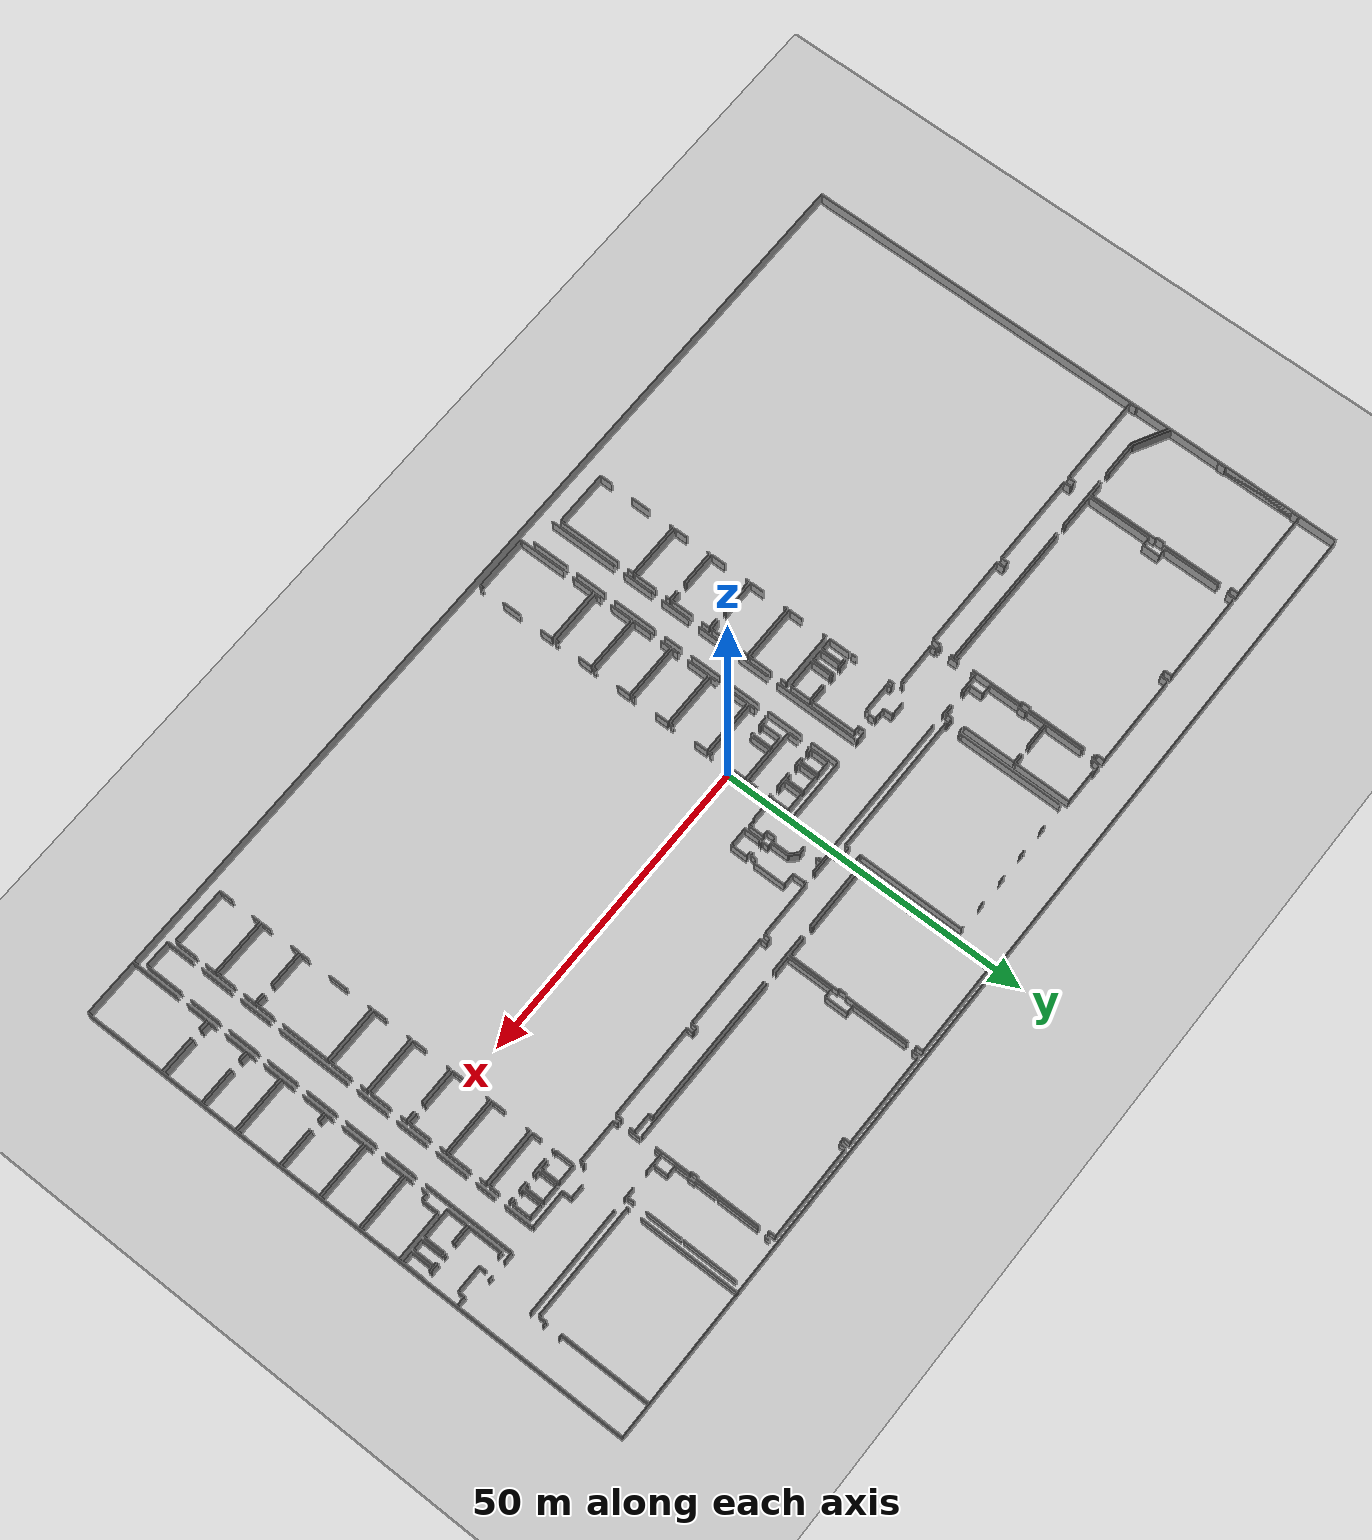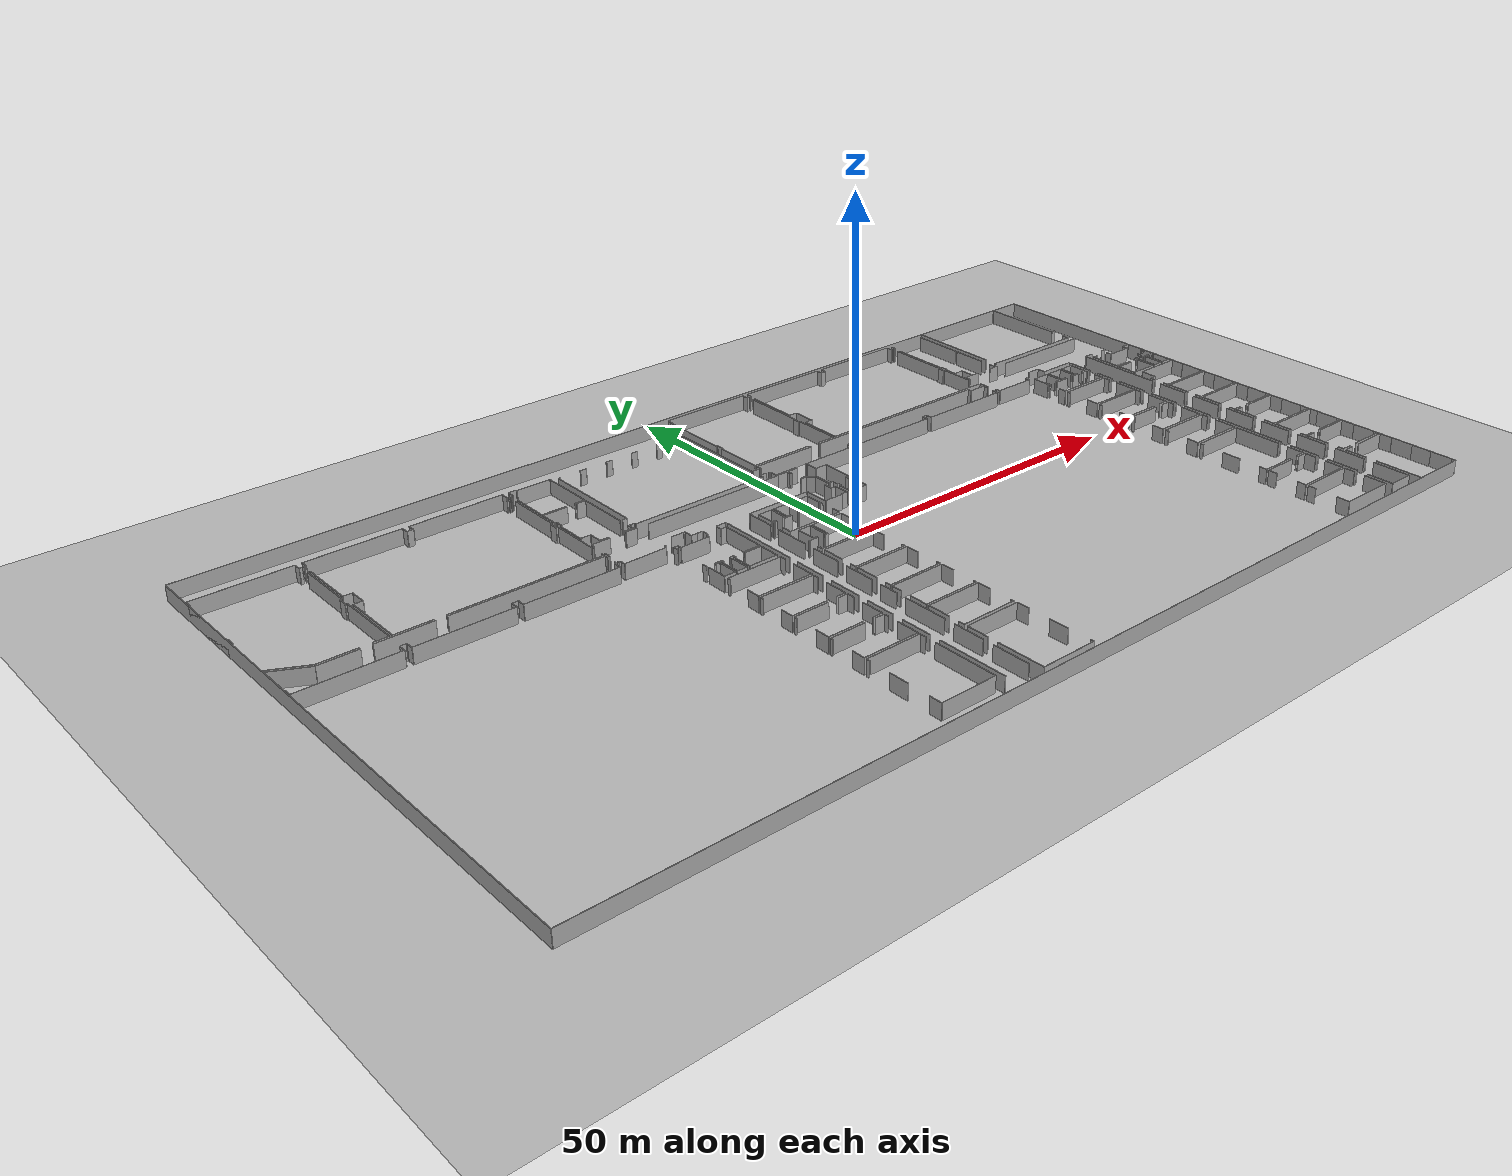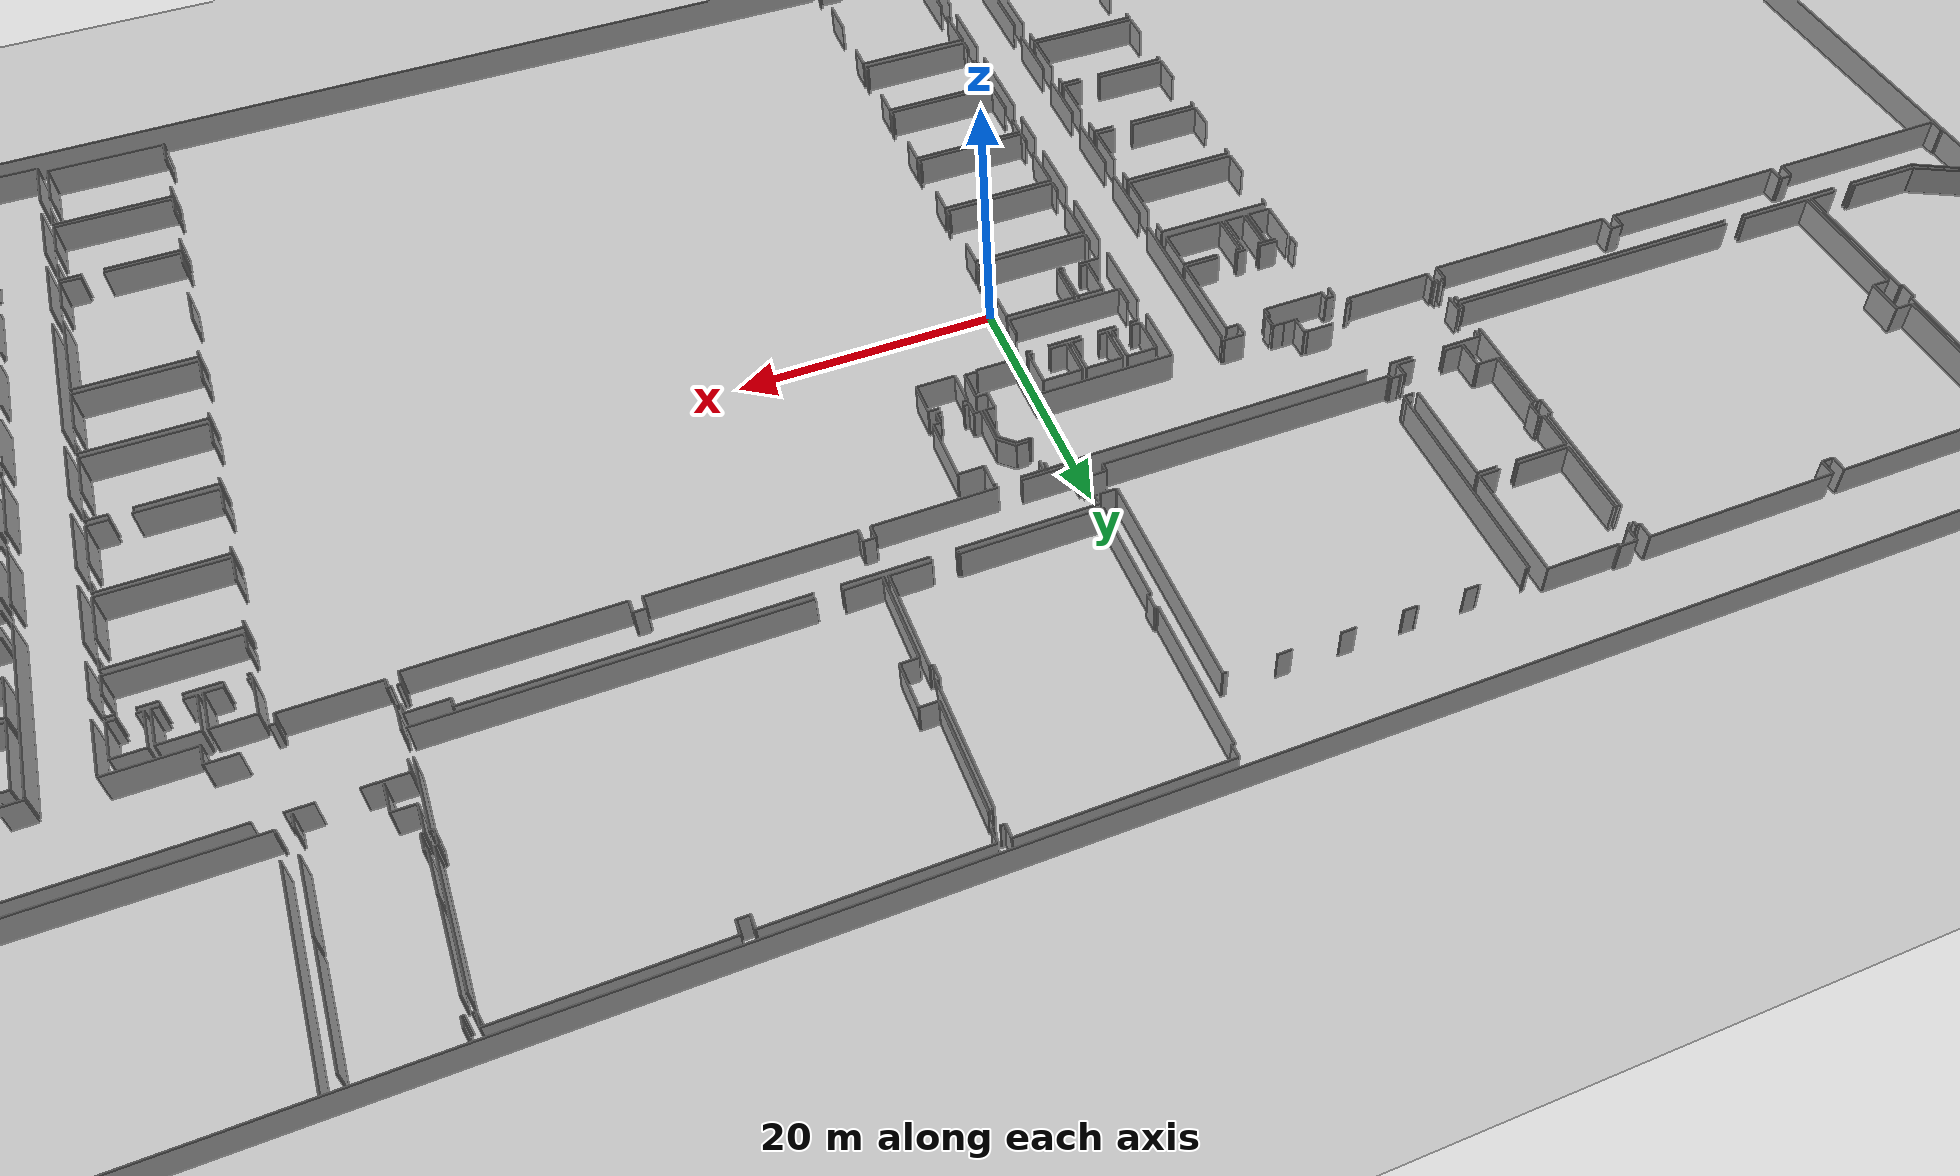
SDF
<sdf version="1.6">
  <world name="default">
    <light name="sun" type="directional">
      <cast_shadows>1</cast_shadows>
      <pose frame="">0 0 10 0 -0 0</pose>
      <diffuse>0.8 0.8 0.8 1</diffuse>
      <specular>0.1 0.1 0.1 1</specular>
      <attenuation>
        <range>1000</range>
        <constant>0.9</constant>
        <linear>0.01</linear>
        <quadratic>0.001</quadratic>
      </attenuation>
      <direction>-0.5 0.5 -1</direction>
    </light>
    <model name="ground_plane">
      <static>1</static>
      <link name="link">
        <collision name="collision">
          <geometry>
            <plane>
              <normal>0 0 1</normal>
              <size>100 100</size>
            </plane>
          </geometry>
          <surface>
            <friction>
              <ode>
                <mu>100</mu>
                <mu2>50</mu2>
              </ode>
              <torsional>
                <ode />
              </torsional>
            </friction>
            <contact>
              <ode />
            </contact>
            <bounce />
          </surface>
          <max_contacts>10</max_contacts>
        </collision>
        <visual name="visual">
          <cast_shadows>0</cast_shadows>
          <geometry>
            <plane>
              <normal>0 0 1</normal>
              <size>100 100</size>
            </plane>
          </geometry>
          <material>
            <script>
              <uri>file://media/materials/scripts/gazebo.material</uri>
              <name>Gazebo/Grey</name>
            </script>
          </material>
        </visual>
        <self_collide>0</self_collide>
        <kinematic>0</kinematic>
        <gravity>1</gravity>
      </link>
    </model>
    <gravity>0 0 -9.8</gravity>
    <magnetic_field>6e-06 2.3e-05 -4.2e-05</magnetic_field>
    <atmosphere type="adiabatic" />
    <physics default="0" name="default_physics" type="ode">
      <max_step_size>0.001</max_step_size>
      <real_time_factor>1</real_time_factor>
      <real_time_update_rate>1000</real_time_update_rate>
    </physics>
    <scene>
      <ambient>0.4 0.4 0.4 1</ambient>
      <background>0.7 0.7 0.7 1</background>
      <shadows>1</shadows>
    </scene>
    <spherical_coordinates>
      <surface_model>EARTH_WGS84</surface_model>
      <latitude_deg>0</latitude_deg>
      <longitude_deg>0</longitude_deg>
      <elevation>0</elevation>
      <heading_deg>0</heading_deg>
    </spherical_coordinates>
  <model name="0510035737_A_40_1_105">
		<static>1</static>
		<link name="Wall_0">
			<collision name="Wall_0_Collision">
				<geometry>
					<box>
						<size>8.16879031489 0.1 2.5</size>
					</box>
				</geometry>
				<pose frame="">4.08439515745 0 1.25 0 0 0</pose>
			</collision>
			<visual name="Wall_0_Visual">
				<pose frame="">4.08439515745 0 1.25 0 0 0</pose>
				<geometry>
					<box>
						<size>8.16879031489 0.1 2.5</size>
					</box>
				</geometry>
				<material>
					<script>
						<uri>file://media/materials/scripts/gazebo.material</uri>
						<name>Gazebo/Grey</name>
					</script>
					<ambient>1 1 1 1</ambient>
				</material>
			</visual>
			<pose frame="">0.00254202281467 -28.3417749674 0 0 0 1.57079632679</pose>
		</link>
		<link name="Wall_1">
			<collision name="Wall_1_Collision">
				<geometry>
					<box>
						<size>0.208616457531 0.1 2.5</size>
					</box>
				</geometry>
				<pose frame="">0.104308228766 0 1.25 0 0 0</pose>
			</collision>
			<visual name="Wall_1_Visual">
				<pose frame="">0.104308228766 0 1.25 0 0 0</pose>
				<geometry>
					<box>
						<size>0.208616457531 0.1 2.5</size>
					</box>
				</geometry>
				<material>
					<script>
						<uri>file://media/materials/scripts/gazebo.material</uri>
						<name>Gazebo/Grey</name>
					</script>
					<ambient>1 1 1 1</ambient>
				</material>
			</visual>
			<pose frame="">0.00254202281467 -20.1729846525 0 0 0 0.551495327385</pose>
		</link>
		<link name="Wall_2">
			<collision name="Wall_2_Collision">
				<geometry>
					<box>
						<size>1.22830542404 0.1 2.5</size>
					</box>
				</geometry>
				<pose frame="">0.614152712021 0 1.25 0 0 0</pose>
			</collision>
			<visual name="Wall_2_Visual">
				<pose frame="">0.614152712021 0 1.25 0 0 0</pose>
				<geometry>
					<box>
						<size>1.22830542404 0.1 2.5</size>
					</box>
				</geometry>
				<material>
					<script>
						<uri>file://media/materials/scripts/gazebo.material</uri>
						<name>Gazebo/Grey</name>
					</script>
					<ambient>1 1 1 1</ambient>
				</material>
			</visual>
			<pose frame="">0.180229417559 -20.0636776715 0 0 0 1.57079632679</pose>
		</link>
		<link name="Wall_3">
			<collision name="Wall_3_Collision">
				<geometry>
					<box>
						<size>0.210785813222 0.1 2.5</size>
					</box>
				</geometry>
				<pose frame="">0.105392906611 0 1.25 0 0 0</pose>
			</collision>
			<visual name="Wall_3_Visual">
				<pose frame="">0.105392906611 0 1.25 0 0 0</pose>
				<geometry>
					<box>
						<size>0.210785813222 0.1 2.5</size>
					</box>
				</geometry>
				<material>
					<script>
						<uri>file://media/materials/scripts/gazebo.material</uri>
						<name>Gazebo/Grey</name>
					</script>
					<ambient>1 1 1 1</ambient>
				</material>
			</visual>
			<pose frame="">0.180229417559 -18.8353722475 0 0 0 2.59641620885</pose>
		</link>
		<link name="Wall_4">
			<collision name="Wall_4_Collision">
				<geometry>
					<box>
						<size>11.3300498872 0.1 2.5</size>
					</box>
				</geometry>
				<pose frame="">5.6650249436 0 1.25 0 0 0</pose>
			</collision>
			<visual name="Wall_4_Visual">
				<pose frame="">5.6650249436 0 1.25 0 0 0</pose>
				<geometry>
					<box>
						<size>11.3300498872 0.1 2.5</size>
					</box>
				</geometry>
				<material>
					<script>
						<uri>file://media/materials/scripts/gazebo.material</uri>
						<name>Gazebo/Grey</name>
					</script>
					<ambient>1 1 1 1</ambient>
				</material>
			</visual>
			<pose frame="">0.0 -18.7260652664 0 0 0 1.57079632679</pose>
		</link>
		<link name="Wall_5">
			<collision name="Wall_5_Collision">
				<geometry>
					<box>
						<size>0.15099615519 0.1 2.5</size>
					</box>
				</geometry>
				<pose frame="">0.0754980775952 0 1.25 0 0 0</pose>
			</collision>
			<visual name="Wall_5_Visual">
				<pose frame="">0.0754980775952 0 1.25 0 0 0</pose>
				<geometry>
					<box>
						<size>0.15099615519 0.1 2.5</size>
					</box>
				</geometry>
				<material>
					<script>
						<uri>file://media/materials/scripts/gazebo.material</uri>
						<name>Gazebo/Grey</name>
					</script>
					<ambient>1 1 1 1</ambient>
				</material>
			</visual>
			<pose frame="">0.0 -7.39601537924 0 0 0 0.0</pose>
		</link>
		<link name="Wall_6">
			<collision name="Wall_6_Collision">
				<geometry>
					<box>
						<size>1.2316100537 0.1 2.5</size>
					</box>
				</geometry>
				<pose frame="">0.61580502685 0 1.25 0 0 0</pose>
			</collision>
			<visual name="Wall_6_Visual">
				<pose frame="">0.61580502685 0 1.25 0 0 0</pose>
				<geometry>
					<box>
						<size>1.2316100537 0.1 2.5</size>
					</box>
				</geometry>
				<material>
					<script>
						<uri>file://media/materials/scripts/gazebo.material</uri>
						<name>Gazebo/Grey</name>
					</script>
					<ambient>1 1 1 1</ambient>
				</material>
			</visual>
			<pose frame="">0.15099615519 -7.39601537924 0 0 0 1.57079632679</pose>
		</link>
		<link name="Wall_7">
			<collision name="Wall_7_Collision">
				<geometry>
					<box>
						<size>15.0340313304 0.1 2.5</size>
					</box>
				</geometry>
				<pose frame="">7.51701566522 0 1.25 0 0 0</pose>
			</collision>
			<visual name="Wall_7_Visual">
				<pose frame="">7.51701566522 0 1.25 0 0 0</pose>
				<geometry>
					<box>
						<size>15.0340313304 0.1 2.5</size>
					</box>
				</geometry>
				<material>
					<script>
						<uri>file://media/materials/scripts/gazebo.material</uri>
						<name>Gazebo/Grey</name>
					</script>
					<ambient>1 1 1 1</ambient>
				</material>
			</visual>
			<pose frame="">0.15099615519 -6.16440532554 0 0 0 0.0</pose>
		</link>
		<link name="Wall_8">
			<collision name="Wall_8_Collision">
				<geometry>
					<box>
						<size>1.21534110769 0.1 2.5</size>
					</box>
				</geometry>
				<pose frame="">0.607670553843 0 1.25 0 0 0</pose>
			</collision>
			<visual name="Wall_8_Visual">
				<pose frame="">0.607670553843 0 1.25 0 0 0</pose>
				<geometry>
					<box>
						<size>1.21534110769 0.1 2.5</size>
					</box>
				</geometry>
				<material>
					<script>
						<uri>file://media/materials/scripts/gazebo.material</uri>
						<name>Gazebo/Grey</name>
					</script>
					<ambient>1 1 1 1</ambient>
				</material>
			</visual>
			<pose frame="">15.1850274856 -6.16440532554 0 0 0 -1.57079632679</pose>
		</link>
		<link name="Wall_9">
			<collision name="Wall_9_Collision">
				<geometry>
					<box>
						<size>0.383082838168 0.1 2.5</size>
					</box>
				</geometry>
				<pose frame="">0.191541419084 0 1.25 0 0 0</pose>
			</collision>
			<visual name="Wall_9_Visual">
				<pose frame="">0.191541419084 0 1.25 0 0 0</pose>
				<geometry>
					<box>
						<size>0.383082838168 0.1 2.5</size>
					</box>
				</geometry>
				<material>
					<script>
						<uri>file://media/materials/scripts/gazebo.material</uri>
						<name>Gazebo/Grey</name>
					</script>
					<ambient>1 1 1 1</ambient>
				</material>
			</visual>
			<pose frame="">15.1850274856 -7.37974643322 0 0 0 0.0</pose>
		</link>
		<link name="Wall_10">
			<collision name="Wall_10_Collision">
				<geometry>
					<box>
						<size>0.142861682184 0.1 2.5</size>
					</box>
				</geometry>
				<pose frame="">0.0714308410918 0 1.25 0 0 0</pose>
			</collision>
			<visual name="Wall_10_Visual">
				<pose frame="">0.0714308410918 0 1.25 0 0 0</pose>
				<geometry>
					<box>
						<size>0.142861682184 0.1 2.5</size>
					</box>
				</geometry>
				<material>
					<script>
						<uri>file://media/materials/scripts/gazebo.material</uri>
						<name>Gazebo/Grey</name>
					</script>
					<ambient>1 1 1 1</ambient>
				</material>
			</visual>
			<pose frame="">15.5681103238 -8.94715770074 0 0 0 -1.57079632679</pose>
		</link>
		<link name="Wall_11">
			<collision name="Wall_11_Collision">
				<geometry>
					<box>
						<size>0.0292332623685 0.1 2.5</size>
					</box>
				</geometry>
				<pose frame="">0.0146166311843 0 1.25 0 0 0</pose>
			</collision>
			<visual name="Wall_11_Visual">
				<pose frame="">0.0146166311843 0 1.25 0 0 0</pose>
				<geometry>
					<box>
						<size>0.0292332623685 0.1 2.5</size>
					</box>
				</geometry>
				<material>
					<script>
						<uri>file://media/materials/scripts/gazebo.material</uri>
						<name>Gazebo/Grey</name>
					</script>
					<ambient>1 1 1 1</ambient>
				</material>
			</visual>
			<pose frame="">15.5681103238 -9.09001938292 0 0 0 3.14159265359</pose>
		</link>
		<link name="Wall_12">
			<collision name="Wall_12_Collision">
				<geometry>
					<box>
						<size>9.67620984398 0.1 2.5</size>
					</box>
				</geometry>
				<pose frame="">4.83810492199 0 1.25 0 0 0</pose>
			</collision>
			<visual name="Wall_12_Visual">
				<pose frame="">4.83810492199 0 1.25 0 0 0</pose>
				<geometry>
					<box>
						<size>9.67620984398 0.1 2.5</size>
					</box>
				</geometry>
				<material>
					<script>
						<uri>file://media/materials/scripts/gazebo.material</uri>
						<name>Gazebo/Grey</name>
					</script>
					<ambient>1 1 1 1</ambient>
				</material>
			</visual>
			<pose frame="">15.5388770614 -9.09001938292 0 0 0 -1.57079632679</pose>
		</link>
		<link name="Wall_13">
			<collision name="Wall_13_Collision">
				<geometry>
					<box>
						<size>0.30351752407 0.1 2.5</size>
					</box>
				</geometry>
				<pose frame="">0.151758762035 0 1.25 0 0 0</pose>
			</collision>
			<visual name="Wall_13_Visual">
				<pose frame="">0.151758762035 0 1.25 0 0 0</pose>
				<geometry>
					<box>
						<size>0.30351752407 0.1 2.5</size>
					</box>
				</geometry>
				<material>
					<script>
						<uri>file://media/materials/scripts/gazebo.material</uri>
						<name>Gazebo/Grey</name>
					</script>
					<ambient>1 1 1 1</ambient>
				</material>
			</visual>
			<pose frame="">15.5388770614 -18.7662292269 0 0 0 3.14159265359</pose>
		</link>
		<link name="Wall_14">
			<collision name="Wall_14_Collision">
				<geometry>
					<box>
						<size>1.37904737695 0.1 2.5</size>
					</box>
				</geometry>
				<pose frame="">0.689523688475 0 1.25 0 0 0</pose>
			</collision>
			<visual name="Wall_14_Visual">
				<pose frame="">0.689523688475 0 1.25 0 0 0</pose>
				<geometry>
					<box>
						<size>1.37904737695 0.1 2.5</size>
					</box>
				</geometry>
				<material>
					<script>
						<uri>file://media/materials/scripts/gazebo.material</uri>
						<name>Gazebo/Grey</name>
					</script>
					<ambient>1 1 1 1</ambient>
				</material>
			</visual>
			<pose frame="">15.2353595374 -18.7662292269 0 0 0 -1.57079632679</pose>
		</link>
		<link name="Wall_15">
			<collision name="Wall_15_Collision">
				<geometry>
					<box>
						<size>0.247593022147 0.1 2.5</size>
					</box>
				</geometry>
				<pose frame="">0.123796511074 0 1.25 0 0 0</pose>
			</collision>
			<visual name="Wall_15_Visual">
				<pose frame="">0.123796511074 0 1.25 0 0 0</pose>
				<geometry>
					<box>
						<size>0.247593022147 0.1 2.5</size>
					</box>
				</geometry>
				<material>
					<script>
						<uri>file://media/materials/scripts/gazebo.material</uri>
						<name>Gazebo/Grey</name>
					</script>
					<ambient>1 1 1 1</ambient>
				</material>
			</visual>
			<pose frame="">15.2353595374 -20.1452766039 0 0 0 0.0</pose>
		</link>
		<link name="Wall_16">
			<collision name="Wall_16_Collision">
				<geometry>
					<box>
						<size>11.1279590734 0.1 2.5</size>
					</box>
				</geometry>
				<pose frame="">5.56397953672 0 1.25 0 0 0</pose>
			</collision>
			<visual name="Wall_16_Visual">
				<pose frame="">5.56397953672 0 1.25 0 0 0</pose>
				<geometry>
					<box>
						<size>11.1279590734 0.1 2.5</size>
					</box>
				</geometry>
				<material>
					<script>
						<uri>file://media/materials/scripts/gazebo.material</uri>
						<name>Gazebo/Grey</name>
					</script>
					<ambient>1 1 1 1</ambient>
				</material>
			</visual>
			<pose frame="">15.4829525595 -20.1452766039 0 0 0 -1.57079632679</pose>
		</link>
		<link name="Wall_17">
			<collision name="Wall_17_Collision">
				<geometry>
					<box>
						<size>2.31247815449 0.1 2.5</size>
					</box>
				</geometry>
				<pose frame="">1.15623907725 0 1.25 0 0 0</pose>
			</collision>
			<visual name="Wall_17_Visual">
				<pose frame="">1.15623907725 0 1.25 0 0 0</pose>
				<geometry>
					<box>
						<size>2.31247815449 0.1 2.5</size>
					</box>
				</geometry>
				<material>
					<script>
						<uri>file://media/materials/scripts/gazebo.material</uri>
						<name>Gazebo/Grey</name>
					</script>
					<ambient>1 1 1 1</ambient>
				</material>
			</visual>
			<pose frame="">15.4829525595 -31.2732356773 0 0 0 3.14159265359</pose>
		</link>
		<link name="Wall_18">
			<collision name="Wall_18_Collision">
				<geometry>
					<box>
						<size>0.087953989387 0.1 2.5</size>
					</box>
				</geometry>
				<pose frame="">0.0439769946935 0 1.25 0 0 0</pose>
			</collision>
			<visual name="Wall_18_Visual">
				<pose frame="">0.0439769946935 0 1.25 0 0 0</pose>
				<geometry>
					<box>
						<size>0.087953989387 0.1 2.5</size>
					</box>
				</geometry>
				<material>
					<script>
						<uri>file://media/materials/scripts/gazebo.material</uri>
						<name>Gazebo/Grey</name>
					</script>
					<ambient>1 1 1 1</ambient>
				</material>
			</visual>
			<pose frame="">13.170474405 -31.2732356773 0 0 0 -1.57079632679</pose>
		</link>
		<link name="Wall_19">
			<collision name="Wall_19_Collision">
				<geometry>
					<box>
						<size>0.0815989323504 0.1 2.5</size>
					</box>
				</geometry>
				<pose frame="">0.0407994661752 0 1.25 0 0 0</pose>
			</collision>
			<visual name="Wall_19_Visual">
				<pose frame="">0.0407994661752 0 1.25 0 0 0</pose>
				<geometry>
					<box>
						<size>0.0815989323504 0.1 2.5</size>
					</box>
				</geometry>
				<material>
					<script>
						<uri>file://media/materials/scripts/gazebo.material</uri>
						<name>Gazebo/Grey</name>
					</script>
					<ambient>1 1 1 1</ambient>
				</material>
			</visual>
			<pose frame="">13.170474405 -31.3611896667 0 0 0 3.14159265359</pose>
		</link>
		<link name="Wall_20">
			<collision name="Wall_20_Collision">
				<geometry>
					<box>
						<size>0.161164246449 0.1 2.5</size>
					</box>
				</geometry>
				<pose frame="">0.0805821232246 0 1.25 0 0 0</pose>
			</collision>
			<visual name="Wall_20_Visual">
				<pose frame="">0.0805821232246 0 1.25 0 0 0</pose>
				<geometry>
					<box>
						<size>0.161164246449 0.1 2.5</size>
					</box>
				</geometry>
				<material>
					<script>
						<uri>file://media/materials/scripts/gazebo.material</uri>
						<name>Gazebo/Grey</name>
					</script>
					<ambient>1 1 1 1</ambient>
				</material>
			</visual>
			<pose frame="">11.373264275 -31.3611896667 0 0 0 3.14159265359</pose>
		</link>
		<link name="Wall_21">
			<collision name="Wall_21_Collision">
				<geometry>
					<box>
						<size>0.0688888182771 0.1 2.5</size>
					</box>
				</geometry>
				<pose frame="">0.0344444091386 0 1.25 0 0 0</pose>
			</collision>
			<visual name="Wall_21_Visual">
				<pose frame="">0.0344444091386 0 1.25 0 0 0</pose>
				<geometry>
					<box>
						<size>0.0688888182771 0.1 2.5</size>
					</box>
				</geometry>
				<material>
					<script>
						<uri>file://media/materials/scripts/gazebo.material</uri>
						<name>Gazebo/Grey</name>
					</script>
					<ambient>1 1 1 1</ambient>
				</material>
			</visual>
			<pose frame="">11.2121000286 -31.3611896667 0 0 0 1.57079632679</pose>
		</link>
		<link name="Wall_22">
			<collision name="Wall_22_Collision">
				<geometry>
					<box>
						<size>5.75946109116 0.1 2.5</size>
					</box>
				</geometry>
				<pose frame="">2.87973054558 0 1.25 0 0 0</pose>
			</collision>
			<visual name="Wall_22_Visual">
				<pose frame="">2.87973054558 0 1.25 0 0 0</pose>
				<geometry>
					<box>
						<size>5.75946109116 0.1 2.5</size>
					</box>
				</geometry>
				<material>
					<script>
						<uri>file://media/materials/scripts/gazebo.material</uri>
						<name>Gazebo/Grey</name>
					</script>
					<ambient>1 1 1 1</ambient>
				</material>
			</visual>
			<pose frame="">11.2121000286 -31.2923008484 0 0 0 3.14159265359</pose>
		</link>
		<link name="Wall_23">
			<collision name="Wall_23_Collision">
				<geometry>
					<box>
						<size>6.19751235199 0.1 2.5</size>
					</box>
				</geometry>
				<pose frame="">3.09875617599 0 1.25 0 0 0</pose>
			</collision>
			<visual name="Wall_23_Visual">
				<pose frame="">3.09875617599 0 1.25 0 0 0</pose>
				<geometry>
					<box>
						<size>6.19751235199 0.1 2.5</size>
					</box>
				</geometry>
				<material>
					<script>
						<uri>file://media/materials/scripts/gazebo.material</uri>
						<name>Gazebo/Grey</name>
					</script>
					<ambient>1 1 1 1</ambient>
				</material>
			</visual>
			<pose frame="">5.45263893743 -31.2923008484 0 0 0 2.6453983167</pose>
		</link>
		<link name="Wall_24">
			<collision name="Wall_24_Collision">
				<geometry>
					<box>
						<size>10.2756188237 0.1 2.5</size>
					</box>
				</geometry>
				<pose frame="">5.13780941184 0 1.25 0 0 0</pose>
			</collision>
			<visual name="Wall_24_Visual">
				<pose frame="">5.13780941184 0 1.25 0 0 0</pose>
				<geometry>
					<box>
						<size>10.2756188237 0.1 2.5</size>
					</box>
				</geometry>
				<material>
					<script>
						<uri>file://media/materials/scripts/gazebo.material</uri>
						<name>Gazebo/Grey</name>
					</script>
					<ambient>1 1 1 1</ambient>
				</material>
			</visual>
			<pose frame="">15.9125544152 -31.2785739252 0 0 0 1.57079632679</pose>
		</link>
		<link name="Wall_25">
			<collision name="Wall_25_Collision">
				<geometry>
					<box>
						<size>1.41768612373 0.1 2.5</size>
					</box>
				</geometry>
				<pose frame="">0.708843061866 0 1.25 0 0 0</pose>
			</collision>
			<visual name="Wall_25_Visual">
				<pose frame="">0.708843061866 0 1.25 0 0 0</pose>
				<geometry>
					<box>
						<size>1.41768612373 0.1 2.5</size>
					</box>
				</geometry>
				<material>
					<script>
						<uri>file://media/materials/scripts/gazebo.material</uri>
						<name>Gazebo/Grey</name>
					</script>
					<ambient>1 1 1 1</ambient>
				</material>
			</visual>
			<pose frame="">15.9125544152 -21.0029551015 0 0 0 0.0</pose>
		</link>
		<link name="Wall_26">
			<collision name="Wall_26_Collision">
				<geometry>
					<box>
						<size>2.81122303073 0.1 2.5</size>
					</box>
				</geometry>
				<pose frame="">1.40561151536 0 1.25 0 0 0</pose>
			</collision>
			<visual name="Wall_26_Visual">
				<pose frame="">1.40561151536 0 1.25 0 0 0</pose>
				<geometry>
					<box>
						<size>2.81122303073 0.1 2.5</size>
					</box>
				</geometry>
				<material>
					<script>
						<uri>file://media/materials/scripts/gazebo.material</uri>
						<name>Gazebo/Grey</name>
					</script>
					<ambient>1 1 1 1</ambient>
				</material>
			</visual>
			<pose frame="">17.3302405389 -21.0029551015 0 0 0 1.57079632679</pose>
		</link>
		<link name="Wall_27">
			<collision name="Wall_27_Collision">
				<geometry>
					<box>
						<size>1.40421340282 0.1 2.5</size>
					</box>
				</geometry>
				<pose frame="">0.702106701408 0 1.25 0 0 0</pose>
			</collision>
			<visual name="Wall_27_Visual">
				<pose frame="">0.702106701408 0 1.25 0 0 0</pose>
				<geometry>
					<box>
						<size>1.40421340282 0.1 2.5</size>
					</box>
				</geometry>
				<material>
					<script>
						<uri>file://media/materials/scripts/gazebo.material</uri>
						<name>Gazebo/Grey</name>
					</script>
					<ambient>1 1 1 1</ambient>
				</material>
			</visual>
			<pose frame="">17.3302405389 -18.1917320708 0 0 0 3.14159265359</pose>
		</link>
		<link name="Wall_28">
			<collision name="Wall_28_Collision">
				<geometry>
					<box>
						<size>9.05493946808 0.1 2.5</size>
					</box>
				</geometry>
				<pose frame="">4.52746973404 0 1.25 0 0 0</pose>
			</collision>
			<visual name="Wall_28_Visual">
				<pose frame="">4.52746973404 0 1.25 0 0 0</pose>
				<geometry>
					<box>
						<size>9.05493946808 0.1 2.5</size>
					</box>
				</geometry>
				<material>
					<script>
						<uri>file://media/materials/scripts/gazebo.material</uri>
						<name>Gazebo/Grey</name>
					</script>
					<ambient>1 1 1 1</ambient>
				</material>
			</visual>
			<pose frame="">15.9260271361 -18.1917320708 0 0 0 1.57079632679</pose>
		</link>
		<link name="Wall_29">
			<collision name="Wall_29_Collision">
				<geometry>
					<box>
						<size>0.0368593308125 0.1 2.5</size>
					</box>
				</geometry>
				<pose frame="">0.0184296654062 0 1.25 0 0 0</pose>
			</collision>
			<visual name="Wall_29_Visual">
				<pose frame="">0.0184296654062 0 1.25 0 0 0</pose>
				<geometry>
					<box>
						<size>0.0368593308125 0.1 2.5</size>
					</box>
				</geometry>
				<material>
					<script>
						<uri>file://media/materials/scripts/gazebo.material</uri>
						<name>Gazebo/Grey</name>
					</script>
					<ambient>1 1 1 1</ambient>
				</material>
			</visual>
			<pose frame="">15.9260271361 -9.13679260271 0 0 0 3.14159265359</pose>
		</link>
		<link name="Wall_30">
			<collision name="Wall_30_Collision">
				<geometry>
					<box>
						<size>0.14743732325 0.1 2.5</size>
					</box>
				</geometry>
				<pose frame="">0.073718661625 0 1.25 0 0 0</pose>
			</collision>
			<visual name="Wall_30_Visual">
				<pose frame="">0.073718661625 0 1.25 0 0 0</pose>
				<geometry>
					<box>
						<size>0.14743732325 0.1 2.5</size>
					</box>
				</geometry>
				<material>
					<script>
						<uri>file://media/materials/scripts/gazebo.material</uri>
						<name>Gazebo/Grey</name>
					</script>
					<ambient>1 1 1 1</ambient>
				</material>
			</visual>
			<pose frame="">15.8891678053 -9.13679260271 0 0 0 1.57079632679</pose>
		</link>
		<link name="Wall_31">
			<collision name="Wall_31_Collision">
				<geometry>
					<box>
						<size>0.131168377236 0.1 2.5</size>
					</box>
				</geometry>
				<pose frame="">0.0655841886181 0 1.25 0 0 0</pose>
			</collision>
			<visual name="Wall_31_Visual">
				<pose frame="">0.0655841886181 0 1.25 0 0 0</pose>
				<geometry>
					<box>
						<size>0.131168377236 0.1 2.5</size>
					</box>
				</geometry>
				<material>
					<script>
						<uri>file://media/materials/scripts/gazebo.material</uri>
						<name>Gazebo/Grey</name>
					</script>
					<ambient>1 1 1 1</ambient>
				</material>
			</visual>
			<pose frame="">15.8891678053 -7.49769629182 0 0 0 1.57079632679</pose>
		</link>
		<link name="Wall_32">
			<collision name="Wall_32_Collision">
				<geometry>
					<box>
						<size>0.300467096692 0.1 2.5</size>
					</box>
				</geometry>
				<pose frame="">0.150233548346 0 1.25 0 0 0</pose>
			</collision>
			<visual name="Wall_32_Visual">
				<pose frame="">0.150233548346 0 1.25 0 0 0</pose>
				<geometry>
					<box>
						<size>0.300467096692 0.1 2.5</size>
					</box>
				</geometry>
				<material>
					<script>
						<uri>file://media/materials/scripts/gazebo.material</uri>
						<name>Gazebo/Grey</name>
					</script>
					<ambient>1 1 1 1</ambient>
				</material>
			</visual>
			<pose frame="">15.8891678053 -7.36652791459 0 0 0 0.0</pose>
		</link>
		<link name="Wall_33">
			<collision name="Wall_33_Collision">
				<geometry>
					<box>
						<size>1.20974865749 0.1 2.5</size>
					</box>
				</geometry>
				<pose frame="">0.604874328747 0 1.25 0 0 0</pose>
			</collision>
			<visual name="Wall_33_Visual">
				<pose frame="">0.604874328747 0 1.25 0 0 0</pose>
				<geometry>
					<box>
						<size>1.20974865749 0.1 2.5</size>
					</box>
				</geometry>
				<material>
					<script>
						<uri>file://media/materials/scripts/gazebo.material</uri>
						<name>Gazebo/Grey</name>
					</script>
					<ambient>1 1 1 1</ambient>
				</material>
			</visual>
			<pose frame="">16.189634902 -7.36652791459 0 0 0 1.57079632679</pose>
		</link>
		<link name="Wall_34">
			<collision name="Wall_34_Collision">
				<geometry>
					<box>
						<size>15.0515712879 0.1 2.5</size>
					</box>
				</geometry>
				<pose frame="">7.52578564393 0 1.25 0 0 0</pose>
			</collision>
			<visual name="Wall_34_Visual">
				<pose frame="">7.52578564393 0 1.25 0 0 0</pose>
				<geometry>
					<box>
						<size>15.0515712879 0.1 2.5</size>
					</box>
				</geometry>
				<material>
					<script>
						<uri>file://media/materials/scripts/gazebo.material</uri>
						<name>Gazebo/Grey</name>
					</script>
					<ambient>1 1 1 1</ambient>
				</material>
			</visual>
			<pose frame="">16.189634902 -6.15677925709 0 0 0 0.0</pose>
		</link>
		<link name="Wall_35">
			<collision name="Wall_35_Collision">
				<geometry>
					<box>
						<size>1.22296717613 0.1 2.5</size>
					</box>
				</geometry>
				<pose frame="">0.611483588065 0 1.25 0 0 0</pose>
			</collision>
			<visual name="Wall_35_Visual">
				<pose frame="">0.611483588065 0 1.25 0 0 0</pose>
				<geometry>
					<box>
						<size>1.22296717613 0.1 2.5</size>
					</box>
				</geometry>
				<material>
					<script>
						<uri>file://media/materials/scripts/gazebo.material</uri>
						<name>Gazebo/Grey</name>
					</script>
					<ambient>1 1 1 1</ambient>
				</material>
			</visual>
			<pose frame="">31.2412061898 -6.15677925709 0 0 0 -1.57079632679</pose>
		</link>
		<link name="Wall_36">
			<collision name="Wall_36_Collision">
				<geometry>
					<box>
						<size>0.961138826221 0.1 2.5</size>
					</box>
				</geometry>
				<pose frame="">0.48056941311 0 1.25 0 0 0</pose>
			</collision>
			<visual name="Wall_36_Visual">
				<pose frame="">0.48056941311 0 1.25 0 0 0</pose>
				<geometry>
					<box>
						<size>0.961138826221 0.1 2.5</size>
					</box>
				</geometry>
				<material>
					<script>
						<uri>file://media/materials/scripts/gazebo.material</uri>
						<name>Gazebo/Grey</name>
					</script>
					<ambient>1 1 1 1</ambient>
				</material>
			</visual>
			<pose frame="">31.2412061898 -7.37974643322 0 0 0 0.0</pose>
		</link>
		<link name="Wall_37">
			<collision name="Wall_37_Collision">
				<geometry>
					<box>
						<size>1.22118776016 0.1 2.5</size>
					</box>
				</geometry>
				<pose frame="">0.61059388008 0 1.25 0 0 0</pose>
			</collision>
			<visual name="Wall_37_Visual">
				<pose frame="">0.61059388008 0 1.25 0 0 0</pose>
				<geometry>
					<box>
						<size>1.22118776016 0.1 2.5</size>
					</box>
				</geometry>
				<material>
					<script>
						<uri>file://media/materials/scripts/gazebo.material</uri>
						<name>Gazebo/Grey</name>
					</script>
					<ambient>1 1 1 1</ambient>
				</material>
			</visual>
			<pose frame="">32.202345016 -7.37974643322 0 0 0 1.57079632679</pose>
		</link>
		<link name="Wall_38">
			<collision name="Wall_38_Collision">
				<geometry>
					<box>
						<size>15.0469956468 0.1 2.5</size>
					</box>
				</geometry>
				<pose frame="">7.52349782339 0 1.25 0 0 0</pose>
			</collision>
			<visual name="Wall_38_Visual">
				<pose frame="">7.52349782339 0 1.25 0 0 0</pose>
				<geometry>
					<box>
						<size>15.0469956468 0.1 2.5</size>
					</box>
				</geometry>
				<material>
					<script>
						<uri>file://media/materials/scripts/gazebo.material</uri>
						<name>Gazebo/Grey</name>
					</script>
					<ambient>1 1 1 1</ambient>
				</material>
			</visual>
			<pose frame="">32.202345016 -6.15855867306 0 0 0 0.0</pose>
		</link>
		<link name="Wall_39">
			<collision name="Wall_39_Collision">
				<geometry>
					<box>
						<size>1.1972927457 0.1 2.5</size>
					</box>
				</geometry>
				<pose frame="">0.598646372851 0 1.25 0 0 0</pose>
			</collision>
			<visual name="Wall_39_Visual">
				<pose frame="">0.598646372851 0 1.25 0 0 0</pose>
				<geometry>
					<box>
						<size>1.1972927457 0.1 2.5</size>
					</box>
				</geometry>
				<material>
					<script>
						<uri>file://media/materials/scripts/gazebo.material</uri>
						<name>Gazebo/Grey</name>
					</script>
					<ambient>1 1 1 1</ambient>
				</material>
			</visual>
			<pose frame="">47.2493406628 -6.15855867306 0 0 0 -1.57079632679</pose>
		</link>
		<link name="Wall_40">
			<collision name="Wall_40_Collision">
				<geometry>
					<box>
						<size>0.305805344603 0.1 2.5</size>
					</box>
				</geometry>
				<pose frame="">0.152902672301 0 1.25 0 0 0</pose>
			</collision>
			<visual name="Wall_40_Visual">
				<pose frame="">0.152902672301 0 1.25 0 0 0</pose>
				<geometry>
					<box>
						<size>0.305805344603 0.1 2.5</size>
					</box>
				</geometry>
				<material>
					<script>
						<uri>file://media/materials/scripts/gazebo.material</uri>
						<name>Gazebo/Grey</name>
					</script>
					<ambient>1 1 1 1</ambient>
				</material>
			</visual>
			<pose frame="">47.2493406628 -7.35585141877 0 0 0 0.0</pose>
		</link>
		<link name="Wall_41">
			<collision name="Wall_41_Collision">
				<geometry>
					<box>
						<size>0.372660544628 0.1 2.5</size>
					</box>
				</geometry>
				<pose frame="">0.186330272314 0 1.25 0 0 0</pose>
			</collision>
			<visual name="Wall_41_Visual">
				<pose frame="">0.186330272314 0 1.25 0 0 0</pose>
				<geometry>
					<box>
						<size>0.372660544628 0.1 2.5</size>
					</box>
				</geometry>
				<material>
					<script>
						<uri>file://media/materials/scripts/gazebo.material</uri>
						<name>Gazebo/Grey</name>
					</script>
					<ambient>1 1 1 1</ambient>
				</material>
			</visual>
			<pose frame="">47.5551460074 -7.35585141877 0 0 0 -1.57079632679</pose>
		</link>
		<link name="Wall_42">
			<collision name="Wall_42_Collision">
				<geometry>
					<box>
						<size>9.49674303327 0.1 2.5</size>
					</box>
				</geometry>
				<pose frame="">4.74837151663 0 1.25 0 0 0</pose>
			</collision>
			<visual name="Wall_42_Visual">
				<pose frame="">4.74837151663 0 1.25 0 0 0</pose>
				<geometry>
					<box>
						<size>9.49674303327 0.1 2.5</size>
					</box>
				</geometry>
				<material>
					<script>
						<uri>file://media/materials/scripts/gazebo.material</uri>
						<name>Gazebo/Grey</name>
					</script>
					<ambient>1 1 1 1</ambient>
				</material>
			</visual>
			<pose frame="">47.5551460074 -9.24228654952 0 0 0 -1.57079632679</pose>
		</link>
		<link name="Wall_43">
			<collision name="Wall_43_Collision">
				<geometry>
					<box>
						<size>0.279368307331 0.1 2.5</size>
					</box>
				</geometry>
				<pose frame="">0.139684153665 0 1.25 0 0 0</pose>
			</collision>
			<visual name="Wall_43_Visual">
				<pose frame="">0.139684153665 0 1.25 0 0 0</pose>
				<geometry>
					<box>
						<size>0.279368307331 0.1 2.5</size>
					</box>
				</geometry>
				<material>
					<script>
						<uri>file://media/materials/scripts/gazebo.material</uri>
						<name>Gazebo/Grey</name>
					</script>
					<ambient>1 1 1 1</ambient>
				</material>
			</visual>
			<pose frame="">47.5551460074 -18.7390295828 0 0 0 3.14159265359</pose>
		</link>
		<link name="Wall_44">
			<collision name="Wall_44_Collision">
				<geometry>
					<box>
						<size>1.40624702107 0.1 2.5</size>
					</box>
				</geometry>
				<pose frame="">0.703123510534 0 1.25 0 0 0</pose>
			</collision>
			<visual name="Wall_44_Visual">
				<pose frame="">0.703123510534 0 1.25 0 0 0</pose>
				<geometry>
					<box>
						<size>1.40624702107 0.1 2.5</size>
					</box>
				</geometry>
				<material>
					<script>
						<uri>file://media/materials/scripts/gazebo.material</uri>
						<name>Gazebo/Grey</name>
					</script>
					<ambient>1 1 1 1</ambient>
				</material>
			</visual>
			<pose frame="">47.2757777001 -18.7390295828 0 0 0 -1.57079632679</pose>
		</link>
		<link name="Wall_45">
			<collision name="Wall_45_Collision">
				<geometry>
					<box>
						<size>0.328175145372 0.1 2.5</size>
					</box>
				</geometry>
				<pose frame="">0.164087572686 0 1.25 0 0 0</pose>
			</collision>
			<visual name="Wall_45_Visual">
				<pose frame="">0.164087572686 0 1.25 0 0 0</pose>
				<geometry>
					<box>
						<size>0.328175145372 0.1 2.5</size>
					</box>
				</geometry>
				<material>
					<script>
						<uri>file://media/materials/scripts/gazebo.material</uri>
						<name>Gazebo/Grey</name>
					</script>
					<ambient>1 1 1 1</ambient>
				</material>
			</visual>
			<pose frame="">47.2757777001 -20.1452766039 0 0 0 0.0</pose>
		</link>
		<link name="Wall_46">
			<collision name="Wall_46_Collision">
				<geometry>
					<box>
						<size>8.22598582822 0.1 2.5</size>
					</box>
				</geometry>
				<pose frame="">4.11299291411 0 1.25 0 0 0</pose>
			</collision>
			<visual name="Wall_46_Visual">
				<pose frame="">4.11299291411 0 1.25 0 0 0</pose>
				<geometry>
					<box>
						<size>8.22598582822 0.1 2.5</size>
					</box>
				</geometry>
				<material>
					<script>
						<uri>file://media/materials/scripts/gazebo.material</uri>
						<name>Gazebo/Grey</name>
					</script>
					<ambient>1 1 1 1</ambient>
				</material>
			</visual>
			<pose frame="">47.6039528455 -20.1452766039 0 0 0 -1.57079632679</pose>
		</link>
		<link name="Wall_47">
			<collision name="Wall_47_Collision">
				<geometry>
					<box>
						<size>0.518064249627 0.1 2.5</size>
					</box>
				</geometry>
				<pose frame="">0.259032124813 0 1.25 0 0 0</pose>
			</collision>
			<visual name="Wall_47_Visual">
				<pose frame="">0.259032124813 0 1.25 0 0 0</pose>
				<geometry>
					<box>
						<size>0.518064249627 0.1 2.5</size>
					</box>
				</geometry>
				<material>
					<script>
						<uri>file://media/materials/scripts/gazebo.material</uri>
						<name>Gazebo/Grey</name>
					</script>
					<ambient>1 1 1 1</ambient>
				</material>
			</visual>
			<pose frame="">47.6039528455 -30.8014362429 0 0 0 -1.57079632679</pose>
		</link>
		<link name="Wall_48">
			<collision name="Wall_48_Collision">
				<geometry>
					<box>
						<size>24.0973594738 0.1 2.5</size>
					</box>
				</geometry>
				<pose frame="">12.0486797369 0 1.25 0 0 0</pose>
			</collision>
			<visual name="Wall_48_Visual">
				<pose frame="">12.0486797369 0 1.25 0 0 0</pose>
				<geometry>
					<box>
						<size>24.0973594738 0.1 2.5</size>
					</box>
				</geometry>
				<material>
					<script>
						<uri>file://media/materials/scripts/gazebo.material</uri>
						<name>Gazebo/Grey</name>
					</script>
					<ambient>1 1 1 1</ambient>
				</material>
			</visual>
			<pose frame="">47.6039528455 -31.3195004925 0 0 0 3.14159265359</pose>
		</link>
		<link name="Wall_49">
			<collision name="Wall_49_Collision">
				<geometry>
					<box>
						<size>5.86281006739 0.1 2.5</size>
					</box>
				</geometry>
				<pose frame="">2.9314050337 0 1.25 0 0 0</pose>
			</collision>
			<visual name="Wall_49_Visual">
				<pose frame="">2.9314050337 0 1.25 0 0 0</pose>
				<geometry>
					<box>
						<size>5.86281006739 0.1 2.5</size>
					</box>
				</geometry>
				<material>
					<script>
						<uri>file://media/materials/scripts/gazebo.material</uri>
						<name>Gazebo/Grey</name>
					</script>
					<ambient>1 1 1 1</ambient>
				</material>
			</visual>
			<pose frame="">21.7752216326 -31.3195004925 0 0 0 3.13461188852</pose>
		</link>
		<link name="Wall_50">
			<collision name="Wall_50_Collision">
				<geometry>
					<box>
						<size>1.13730100728 0.1 2.5</size>
					</box>
				</geometry>
				<pose frame="">0.568650503638 0 1.25 0 0 0</pose>
			</collision>
			<visual name="Wall_50_Visual">
				<pose frame="">0.568650503638 0 1.25 0 0 0</pose>
				<geometry>
					<box>
						<size>1.13730100728 0.1 2.5</size>
					</box>
				</geometry>
				<material>
					<script>
						<uri>file://media/materials/scripts/gazebo.material</uri>
						<name>Gazebo/Grey</name>
					</script>
					<ambient>1 1 1 1</ambient>
				</material>
			</visual>
			<pose frame="">0.169552921737 -35.5601029519 0 0 0 1.57079632679</pose>
		</link>
		<link name="Wall_51">
			<collision name="Wall_51_Collision">
				<geometry>
					<box>
						<size>0.179732518247 0.1 2.5</size>
					</box>
				</geometry>
				<pose frame="">0.0898662591237 0 1.25 0 0 0</pose>
			</collision>
			<visual name="Wall_51_Visual">
				<pose frame="">0.0898662591237 0 1.25 0 0 0</pose>
				<geometry>
					<box>
						<size>0.179732518247 0.1 2.5</size>
					</box>
				</geometry>
				<material>
					<script>
						<uri>file://media/materials/scripts/gazebo.material</uri>
						<name>Gazebo/Grey</name>
					</script>
					<ambient>1 1 1 1</ambient>
				</material>
			</visual>
			<pose frame="">0.169552921737 -34.4228019446 0 0 0 2.45536558078</pose>
		</link>
		<link name="Wall_52">
			<collision name="Wall_52_Collision">
				<geometry>
					<box>
						<size>5.47983858155 0.1 2.5</size>
					</box>
				</geometry>
				<pose frame="">2.73991929078 0 1.25 0 0 0</pose>
			</collision>
			<visual name="Wall_52_Visual">
				<pose frame="">2.73991929078 0 1.25 0 0 0</pose>
				<geometry>
					<box>
						<size>5.47983858155 0.1 2.5</size>
					</box>
				</geometry>
				<material>
					<script>
						<uri>file://media/materials/scripts/gazebo.material</uri>
						<name>Gazebo/Grey</name>
					</script>
					<ambient>1 1 1 1</ambient>
				</material>
			</visual>
			<pose frame="">0.0305042737759 -34.3089193226 0 0 0 1.57079632679</pose>
		</link>
		<link name="Wall_53">
			<collision name="Wall_53_Collision">
				<geometry>
					<box>
						<size>5.99210899888 0.1 2.5</size>
					</box>
				</geometry>
				<pose frame="">2.99605449944 0 1.25 0 0 0</pose>
			</collision>
			<visual name="Wall_53_Visual">
				<pose frame="">2.99605449944 0 1.25 0 0 0</pose>
				<geometry>
					<box>
						<size>5.99210899888 0.1 2.5</size>
					</box>
				</geometry>
				<material>
					<script>
						<uri>file://media/materials/scripts/gazebo.material</uri>
						<name>Gazebo/Grey</name>
					</script>
					<ambient>1 1 1 1</ambient>
				</material>
			</visual>
			<pose frame="">0.0305042737759 -28.829080741 0 0 0 -0.496854835641</pose>
		</link>
		<link name="Wall_54">
			<collision name="Wall_54_Collision">
				<geometry>
					<box>
						<size>6.02866130724 0.1 2.5</size>
					</box>
				</geometry>
				<pose frame="">3.01433065362 0 1.25 0 0 0</pose>
			</collision>
			<visual name="Wall_54_Visual">
				<pose frame="">3.01433065362 0 1.25 0 0 0</pose>
				<geometry>
					<box>
						<size>6.02866130724 0.1 2.5</size>
					</box>
				</geometry>
				<material>
					<script>
						<uri>file://media/materials/scripts/gazebo.material</uri>
						<name>Gazebo/Grey</name>
					</script>
					<ambient>1 1 1 1</ambient>
				</material>
			</visual>
			<pose frame="">5.2980839503 -31.6852975755 0 0 0 0.0</pose>
		</link>
		<link name="Wall_55">
			<collision name="Wall_55_Collision">
				<geometry>
					<box>
						<size>8.72371389533 0.1 2.5</size>
					</box>
				</geometry>
				<pose frame="">4.36185694767 0 1.25 0 0 0</pose>
			</collision>
			<visual name="Wall_55_Visual">
				<pose frame="">4.36185694767 0 1.25 0 0 0</pose>
				<geometry>
					<box>
						<size>8.72371389533 0.1 2.5</size>
					</box>
				</geometry>
				<material>
					<script>
						<uri>file://media/materials/scripts/gazebo.material</uri>
						<name>Gazebo/Grey</name>
					</script>
					<ambient>1 1 1 1</ambient>
				</material>
			</visual>
			<pose frame="">13.0227828795 -31.6852975755 0 0 0 0.0</pose>
		</link>
		<link name="Wall_56">
			<collision name="Wall_56_Collision">
				<geometry>
					<box>
						<size>24.1095611833 0.1 2.5</size>
					</box>
				</geometry>
				<pose frame="">12.0547805917 0 1.25 0 0 0</pose>
			</collision>
			<visual name="Wall_56_Visual">
				<pose frame="">12.0547805917 0 1.25 0 0 0</pose>
				<geometry>
					<box>
						<size>24.1095611833 0.1 2.5</size>
					</box>
				</geometry>
				<material>
					<script>
						<uri>file://media/materials/scripts/gazebo.material</uri>
						<name>Gazebo/Grey</name>
					</script>
					<ambient>1 1 1 1</ambient>
				</material>
			</visual>
			<pose frame="">23.4374503511 -31.6852975755 0 0 0 0.0</pose>
		</link>
		<link name="Wall_57">
			<collision name="Wall_57_Collision">
				<geometry>
					<box>
						<size>0.492898223762 0.1 2.5</size>
					</box>
				</geometry>
				<pose frame="">0.246449111881 0 1.25 0 0 0</pose>
			</collision>
			<visual name="Wall_57_Visual">
				<pose frame="">0.246449111881 0 1.25 0 0 0</pose>
				<geometry>
					<box>
						<size>0.492898223762 0.1 2.5</size>
					</box>
				</geometry>
				<material>
					<script>
						<uri>file://media/materials/scripts/gazebo.material</uri>
						<name>Gazebo/Grey</name>
					</script>
					<ambient>1 1 1 1</ambient>
				</material>
			</visual>
			<pose frame="">47.5470115344 -31.6852975755 0 0 0 -1.57079632679</pose>
		</link>
		<link name="Wall_58">
			<collision name="Wall_58_Collision">
				<geometry>
					<box>
						<size>0.483746941629 0.1 2.5</size>
					</box>
				</geometry>
				<pose frame="">0.241873470814 0 1.25 0 0 0</pose>
			</collision>
			<visual name="Wall_58_Visual">
				<pose frame="">0.241873470814 0 1.25 0 0 0</pose>
				<geometry>
					<box>
						<size>0.483746941629 0.1 2.5</size>
					</box>
				</geometry>
				<material>
					<script>
						<uri>file://media/materials/scripts/gazebo.material</uri>
						<name>Gazebo/Grey</name>
					</script>
					<ambient>1 1 1 1</ambient>
				</material>
			</visual>
			<pose frame="">47.5470115344 -33.8244097741 0 0 0 -1.57079632679</pose>
		</link>
		<link name="Wall_59">
			<collision name="Wall_59_Collision">
				<geometry>
					<box>
						<size>0.269708620635 0.1 2.5</size>
					</box>
				</geometry>
				<pose frame="">0.134854310317 0 1.25 0 0 0</pose>
			</collision>
			<visual name="Wall_59_Visual">
				<pose frame="">0.134854310317 0 1.25 0 0 0</pose>
				<geometry>
					<box>
						<size>0.269708620635 0.1 2.5</size>
					</box>
				</geometry>
				<material>
					<script>
						<uri>file://media/materials/scripts/gazebo.material</uri>
						<name>Gazebo/Grey</name>
					</script>
					<ambient>1 1 1 1</ambient>
				</material>
			</visual>
			<pose frame="">47.5470115344 -34.3081567157 0 0 0 3.14159265359</pose>
		</link>
		<link name="Wall_60">
			<collision name="Wall_60_Collision">
				<geometry>
					<box>
						<size>1.25397985447 0.1 2.5</size>
					</box>
				</geometry>
				<pose frame="">0.626989927235 0 1.25 0 0 0</pose>
			</collision>
			<visual name="Wall_60_Visual">
				<pose frame="">0.626989927235 0 1.25 0 0 0</pose>
				<geometry>
					<box>
						<size>1.25397985447 0.1 2.5</size>
					</box>
				</geometry>
				<material>
					<script>
						<uri>file://media/materials/scripts/gazebo.material</uri>
						<name>Gazebo/Grey</name>
					</script>
					<ambient>1 1 1 1</ambient>
				</material>
			</visual>
			<pose frame="">47.2773029138 -34.3081567157 0 0 0 -1.57079632679</pose>
		</link>
		<link name="Wall_61">
			<collision name="Wall_61_Collision">
				<geometry>
					<box>
						<size>15.0462330399 0.1 2.5</size>
					</box>
				</geometry>
				<pose frame="">7.52311651997 0 1.25 0 0 0</pose>
			</collision>
			<visual name="Wall_61_Visual">
				<pose frame="">7.52311651997 0 1.25 0 0 0</pose>
				<geometry>
					<box>
						<size>15.0462330399 0.1 2.5</size>
					</box>
				</geometry>
				<material>
					<script>
						<uri>file://media/materials/scripts/gazebo.material</uri>
						<name>Gazebo/Grey</name>
					</script>
					<ambient>1 1 1 1</ambient>
				</material>
			</visual>
			<pose frame="">47.2773029138 -35.5621365702 0 0 0 3.14159265359</pose>
		</link>
		<link name="Wall_62">
			<collision name="Wall_62_Collision">
				<geometry>
					<box>
						<size>1.23669409933 0.1 2.5</size>
					</box>
				</geometry>
				<pose frame="">0.618347049665 0 1.25 0 0 0</pose>
			</collision>
			<visual name="Wall_62_Visual">
				<pose frame="">0.618347049665 0 1.25 0 0 0</pose>
				<geometry>
					<box>
						<size>1.23669409933 0.1 2.5</size>
					</box>
				</geometry>
				<material>
					<script>
						<uri>file://media/materials/scripts/gazebo.material</uri>
						<name>Gazebo/Grey</name>
					</script>
					<ambient>1 1 1 1</ambient>
				</material>
			</visual>
			<pose frame="">32.2310698739 -35.5621365702 0 0 0 1.57079632679</pose>
		</link>
		<link name="Wall_63">
			<collision name="Wall_63_Collision">
				<geometry>
					<box>
						<size>0.975374153983 0.1 2.5</size>
					</box>
				</geometry>
				<pose frame="">0.487687076992 0 1.25 0 0 0</pose>
			</collision>
			<visual name="Wall_63_Visual">
				<pose frame="">0.487687076992 0 1.25 0 0 0</pose>
				<geometry>
					<box>
						<size>0.975374153983 0.1 2.5</size>
					</box>
				</geometry>
				<material>
					<script>
						<uri>file://media/materials/scripts/gazebo.material</uri>
						<name>Gazebo/Grey</name>
					</script>
					<ambient>1 1 1 1</ambient>
				</material>
			</visual>
			<pose frame="">32.2310698739 -34.3254424708 0 0 0 3.14159265359</pose>
		</link>
		<link name="Wall_64">
			<collision name="Wall_64_Collision">
				<geometry>
					<box>
						<size>1.22855962632 0.1 2.5</size>
					</box>
				</geometry>
				<pose frame="">0.614279813161 0 1.25 0 0 0</pose>
			</collision>
			<visual name="Wall_64_Visual">
				<pose frame="">0.614279813161 0 1.25 0 0 0</pose>
				<geometry>
					<box>
						<size>1.22855962632 0.1 2.5</size>
					</box>
				</geometry>
				<material>
					<script>
						<uri>file://media/materials/scripts/gazebo.material</uri>
						<name>Gazebo/Grey</name>
					</script>
					<ambient>1 1 1 1</ambient>
				</material>
			</visual>
			<pose frame="">31.2556957199 -34.3254424708 0 0 0 -1.57079632679</pose>
		</link>
		<link name="Wall_65">
			<collision name="Wall_65_Collision">
				<geometry>
					<box>
						<size>15.0353023418 0.1 2.5</size>
					</box>
				</geometry>
				<pose frame="">7.51765117092 0 1.25 0 0 0</pose>
			</collision>
			<visual name="Wall_65_Visual">
				<pose frame="">7.51765117092 0 1.25 0 0 0</pose>
				<geometry>
					<box>
						<size>15.0353023418 0.1 2.5</size>
					</box>
				</geometry>
				<material>
					<script>
						<uri>file://media/materials/scripts/gazebo.material</uri>
						<name>Gazebo/Grey</name>
					</script>
					<ambient>1 1 1 1</ambient>
				</material>
			</visual>
			<pose frame="">31.2556957199 -35.5540020972 0 0 0 3.14159265359</pose>
		</link>
		<link name="Wall_66">
			<collision name="Wall_66_Collision">
				<geometry>
					<box>
						<size>1.1589082012 0.1 2.5</size>
					</box>
				</geometry>
				<pose frame="">0.579454100601 0 1.25 0 0 0</pose>
			</collision>
			<visual name="Wall_66_Visual">
				<pose frame="">0.579454100601 0 1.25 0 0 0</pose>
				<geometry>
					<box>
						<size>1.1589082012 0.1 2.5</size>
					</box>
				</geometry>
				<material>
					<script>
						<uri>file://media/materials/scripts/gazebo.material</uri>
						<name>Gazebo/Grey</name>
					</script>
					<ambient>1 1 1 1</ambient>
				</material>
			</visual>
			<pose frame="">16.220393378 -35.5540020972 0 0 0 1.57079632679</pose>
		</link>
		<link name="Wall_67">
			<collision name="Wall_67_Collision">
				<geometry>
					<box>
						<size>0.153682256566 0.1 2.5</size>
					</box>
				</geometry>
				<pose frame="">0.0768411282828 0 1.25 0 0 0</pose>
			</collision>
			<visual name="Wall_67_Visual">
				<pose frame="">0.0768411282828 0 1.25 0 0 0</pose>
				<geometry>
					<box>
						<size>0.153682256566 0.1 2.5</size>
					</box>
				</geometry>
				<material>
					<script>
						<uri>file://media/materials/scripts/gazebo.material</uri>
						<name>Gazebo/Grey</name>
					</script>
					<ambient>1 1 1 1</ambient>
				</material>
			</visual>
			<pose frame="">16.220393378 -34.395093896 0 0 0 2.47460149163</pose>
		</link>
		<link name="Wall_68">
			<collision name="Wall_68_Collision">
				<geometry>
					<box>
						<size>0.805567029964 0.1 2.5</size>
					</box>
				</geometry>
				<pose frame="">0.402783514982 0 1.25 0 0 0</pose>
			</collision>
			<visual name="Wall_68_Visual">
				<pose frame="">0.402783514982 0 1.25 0 0 0</pose>
				<geometry>
					<box>
						<size>0.805567029964 0.1 2.5</size>
					</box>
				</geometry>
				<material>
					<script>
						<uri>file://media/materials/scripts/gazebo.material</uri>
						<name>Gazebo/Grey</name>
					</script>
					<ambient>1 1 1 1</ambient>
				</material>
			</visual>
			<pose frame="">16.0996472943 -34.3000222427 0 0 0 3.14159265359</pose>
		</link>
		<link name="Wall_69">
			<collision name="Wall_69_Collision">
				<geometry>
					<box>
						<size>0.133161724535 0.1 2.5</size>
					</box>
				</geometry>
				<pose frame="">0.0665808622676 0 1.25 0 0 0</pose>
			</collision>
			<visual name="Wall_69_Visual">
				<pose frame="">0.0665808622676 0 1.25 0 0 0</pose>
				<geometry>
					<box>
						<size>0.133161724535 0.1 2.5</size>
					</box>
				</geometry>
				<material>
					<script>
						<uri>file://media/materials/scripts/gazebo.material</uri>
						<name>Gazebo/Grey</name>
					</script>
					<ambient>1 1 1 1</ambient>
				</material>
			</visual>
			<pose frame="">15.2940802644 -34.3000222427 0 0 0 -2.20169787326</pose>
		</link>
		<link name="Wall_70">
			<collision name="Wall_70_Collision">
				<geometry>
					<box>
						<size>1.14009723237 0.1 2.5</size>
					</box>
				</geometry>
				<pose frame="">0.570048616186 0 1.25 0 0 0</pose>
			</collision>
			<visual name="Wall_70_Visual">
				<pose frame="">0.570048616186 0 1.25 0 0 0</pose>
				<geometry>
					<box>
						<size>1.14009723237 0.1 2.5</size>
					</box>
				</geometry>
				<material>
					<script>
						<uri>file://media/materials/scripts/gazebo.material</uri>
						<name>Gazebo/Grey</name>
					</script>
					<ambient>1 1 1 1</ambient>
				</material>
			</visual>
			<pose frame="">15.2155317594 -34.4075498078 0 0 0 -1.57079632679</pose>
		</link>
		<link name="Wall_71">
			<collision name="Wall_71_Collision">
				<geometry>
					<box>
						<size>15.0459839935 0.1 2.5</size>
					</box>
				</geometry>
				<pose frame="">7.52299199676 0 1.25 0 0 0</pose>
			</collision>
			<visual name="Wall_71_Visual">
				<pose frame="">7.52299199676 0 1.25 0 0 0</pose>
				<geometry>
					<box>
						<size>15.0459839935 0.1 2.5</size>
					</box>
				</geometry>
				<material>
					<script>
						<uri>file://media/materials/scripts/gazebo.material</uri>
						<name>Gazebo/Grey</name>
					</script>
					<ambient>1 1 1 1</ambient>
				</material>
			</visual>
			<pose frame="">15.2155317594 -35.5476470401 0 0 0 -3.14076479725</pose>
		</link>
		<link name="Wall_72">
			<collision name="Wall_72_Collision">
				<geometry>
					<box>
						<size>5.98239649201 0.1 2.5</size>
					</box>
				</geometry>
				<pose frame="">2.991198246 0 1.25 0 0 0</pose>
			</collision>
			<visual name="Wall_72_Visual">
				<pose frame="">2.991198246 0 1.25 0 0 0</pose>
				<geometry>
					<box>
						<size>5.98239649201 0.1 2.5</size>
					</box>
				</geometry>
				<material>
					<script>
						<uri>file://media/materials/scripts/gazebo.material</uri>
						<name>Gazebo/Grey</name>
					</script>
					<ambient>1 1 1 1</ambient>
				</material>
			</visual>
			<pose frame="">47.975596581 -15.4501604652 0 0 0 1.57079632679</pose>
		</link>
		<link name="Wall_73">
			<collision name="Wall_73_Collision">
				<geometry>
					<box>
						<size>0.20501079106 0.1 2.5</size>
					</box>
				</geometry>
				<pose frame="">0.10250539553 0 1.25 0 0 0</pose>
			</collision>
			<visual name="Wall_73_Visual">
				<pose frame="">0.10250539553 0 1.25 0 0 0</pose>
				<geometry>
					<box>
						<size>0.20501079106 0.1 2.5</size>
					</box>
				</geometry>
				<material>
					<script>
						<uri>file://media/materials/scripts/gazebo.material</uri>
						<name>Gazebo/Grey</name>
					</script>
					<ambient>1 1 1 1</ambient>
				</material>
			</visual>
			<pose frame="">47.975596581 -9.46776397318 0 0 0 2.05440800518</pose>
		</link>
		<link name="Wall_74">
			<collision name="Wall_74_Collision">
				<geometry>
					<box>
						<size>0.171460710797 0.1 2.5</size>
					</box>
				</geometry>
				<pose frame="">0.0857303553987 0 1.25 0 0 0</pose>
			</collision>
			<visual name="Wall_74_Visual">
				<pose frame="">0.0857303553987 0 1.25 0 0 0</pose>
				<geometry>
					<box>
						<size>0.171460710797 0.1 2.5</size>
					</box>
				</geometry>
				<material>
					<script>
						<uri>file://media/materials/scripts/gazebo.material</uri>
						<name>Gazebo/Grey</name>
					</script>
					<ambient>1 1 1 1</ambient>
				</material>
			</visual>
			<pose frame="">47.8802707254 -7.72952877252 0 0 0 1.03215663649</pose>
		</link>
		<link name="Wall_75">
			<collision name="Wall_75_Collision">
				<geometry>
					<box>
						<size>0.175907978774 0.1 2.5</size>
					</box>
				</geometry>
				<pose frame="">0.0879539893871 0 1.25 0 0 0</pose>
			</collision>
			<visual name="Wall_75_Visual">
				<pose frame="">0.0879539893871 0 1.25 0 0 0</pose>
				<geometry>
					<box>
						<size>0.175907978774 0.1 2.5</size>
					</box>
				</geometry>
				<material>
					<script>
						<uri>file://media/materials/scripts/gazebo.material</uri>
						<name>Gazebo/Grey</name>
					</script>
					<ambient>1 1 1 1</ambient>
				</material>
			</visual>
			<pose frame="">47.9682247148 -7.58234565155 0 0 0 1.57079632679</pose>
		</link>
		<link name="Wall_76">
			<collision name="Wall_76_Collision">
				<geometry>
					<box>
						<size>0.194718947603 0.1 2.5</size>
					</box>
				</geometry>
				<pose frame="">0.0973594738013 0 1.25 0 0 0</pose>
			</collision>
			<visual name="Wall_76_Visual">
				<pose frame="">0.0973594738013 0 1.25 0 0 0</pose>
				<geometry>
					<box>
						<size>0.194718947603 0.1 2.5</size>
					</box>
				</geometry>
				<material>
					<script>
						<uri>file://media/materials/scripts/gazebo.material</uri>
						<name>Gazebo/Grey</name>
					</script>
					<ambient>1 1 1 1</ambient>
				</material>
			</visual>
			<pose frame="">47.9682247148 -7.40643767278 0 0 0 0.0</pose>
		</link>
		<link name="Wall_77">
			<collision name="Wall_77_Collision">
				<geometry>
					<box>
						<size>0.141744842444 0.1 2.5</size>
					</box>
				</geometry>
				<pose frame="">0.0708724212222 0 1.25 0 0 0</pose>
			</collision>
			<visual name="Wall_77_Visual">
				<pose frame="">0.0708724212222 0 1.25 0 0 0</pose>
				<geometry>
					<box>
						<size>0.141744842444 0.1 2.5</size>
					</box>
				</geometry>
				<material>
					<script>
						<uri>file://media/materials/scripts/gazebo.material</uri>
						<name>Gazebo/Grey</name>
					</script>
					<ambient>1 1 1 1</ambient>
				</material>
			</visual>
			<pose frame="">48.1629436624 -7.40643767278 0 0 0 0.880650440816</pose>
		</link>
		<link name="Wall_78">
			<collision name="Wall_78_Collision">
				<geometry>
					<box>
						<size>0.888436973722 0.1 2.5</size>
					</box>
				</geometry>
				<pose frame="">0.444218486861 0 1.25 0 0 0</pose>
			</collision>
			<visual name="Wall_78_Visual">
				<pose frame="">0.444218486861 0 1.25 0 0 0</pose>
				<geometry>
					<box>
						<size>0.888436973722 0.1 2.5</size>
					</box>
				</geometry>
				<material>
					<script>
						<uri>file://media/materials/scripts/gazebo.material</uri>
						<name>Gazebo/Grey</name>
					</script>
					<ambient>1 1 1 1</ambient>
				</material>
			</visual>
			<pose frame="">48.2531854723 -7.29713069175 0 0 0 1.57079632679</pose>
		</link>
		<link name="Wall_79">
			<collision name="Wall_79_Collision">
				<geometry>
					<box>
						<size>0.0475358266341 0.1 2.5</size>
					</box>
				</geometry>
				<pose frame="">0.023767913317 0 1.25 0 0 0</pose>
			</collision>
			<visual name="Wall_79_Visual">
				<pose frame="">0.023767913317 0 1.25 0 0 0</pose>
				<geometry>
					<box>
						<size>0.0475358266341 0.1 2.5</size>
					</box>
				</geometry>
				<material>
					<script>
						<uri>file://media/materials/scripts/gazebo.material</uri>
						<name>Gazebo/Grey</name>
					</script>
					<ambient>1 1 1 1</ambient>
				</material>
			</visual>
			<pose frame="">48.2531854723 -6.40869371803 0 0 0 0.0</pose>
		</link>
		<link name="Wall_80">
			<collision name="Wall_80_Collision">
				<geometry>
					<box>
						<size>0.213784118712 0.1 2.5</size>
					</box>
				</geometry>
				<pose frame="">0.106892059356 0 1.25 0 0 0</pose>
			</collision>
			<visual name="Wall_80_Visual">
				<pose frame="">0.106892059356 0 1.25 0 0 0</pose>
				<geometry>
					<box>
						<size>0.213784118712 0.1 2.5</size>
					</box>
				</geometry>
				<material>
					<script>
						<uri>file://media/materials/scripts/gazebo.material</uri>
						<name>Gazebo/Grey</name>
					</script>
					<ambient>1 1 1 1</ambient>
				</material>
			</visual>
			<pose frame="">48.300721299 -6.40869371803 0 0 0 1.57079632679</pose>
		</link>
		<link name="Wall_81">
			<collision name="Wall_81_Collision">
				<geometry>
					<box>
						<size>1.26846938451 0.1 2.5</size>
					</box>
				</geometry>
				<pose frame="">0.634234692256 0 1.25 0 0 0</pose>
			</collision>
			<visual name="Wall_81_Visual">
				<pose frame="">0.634234692256 0 1.25 0 0 0</pose>
				<geometry>
					<box>
						<size>1.26846938451 0.1 2.5</size>
					</box>
				</geometry>
				<material>
					<script>
						<uri>file://media/materials/scripts/gazebo.material</uri>
						<name>Gazebo/Grey</name>
					</script>
					<ambient>1 1 1 1</ambient>
				</material>
			</visual>
			<pose frame="">48.300721299 -6.19490959931 0 0 0 0.0</pose>
		</link>
		<link name="Wall_82">
			<collision name="Wall_82_Collision">
				<geometry>
					<box>
						<size>0.204378634298 0.1 2.5</size>
					</box>
				</geometry>
				<pose frame="">0.102189317149 0 1.25 0 0 0</pose>
			</collision>
			<visual name="Wall_82_Visual">
				<pose frame="">0.102189317149 0 1.25 0 0 0</pose>
				<geometry>
					<box>
						<size>0.204378634298 0.1 2.5</size>
					</box>
				</geometry>
				<material>
					<script>
						<uri>file://media/materials/scripts/gazebo.material</uri>
						<name>Gazebo/Grey</name>
					</script>
					<ambient>1 1 1 1</ambient>
				</material>
			</visual>
			<pose frame="">49.5691906835 -6.19490959931 0 0 0 -1.57079632679</pose>
		</link>
		<link name="Wall_83">
			<collision name="Wall_83_Collision">
				<geometry>
					<box>
						<size>5.60465190175 0.1 2.5</size>
					</box>
				</geometry>
				<pose frame="">2.80232595088 0 1.25 0 0 0</pose>
			</collision>
			<visual name="Wall_83_Visual">
				<pose frame="">2.80232595088 0 1.25 0 0 0</pose>
				<geometry>
					<box>
						<size>5.60465190175 0.1 2.5</size>
					</box>
				</geometry>
				<material>
					<script>
						<uri>file://media/materials/scripts/gazebo.material</uri>
						<name>Gazebo/Grey</name>
					</script>
					<ambient>1 1 1 1</ambient>
				</material>
			</visual>
			<pose frame="">49.5691906835 -6.39928823361 0 0 0 0.0</pose>
		</link>
		<link name="Wall_84">
			<collision name="Wall_84_Collision">
				<geometry>
					<box>
						<size>9.03739951066 0.1 2.5</size>
					</box>
				</geometry>
				<pose frame="">4.51869975533 0 1.25 0 0 0</pose>
			</collision>
			<visual name="Wall_84_Visual">
				<pose frame="">4.51869975533 0 1.25 0 0 0</pose>
				<geometry>
					<box>
						<size>9.03739951066 0.1 2.5</size>
					</box>
				</geometry>
				<material>
					<script>
						<uri>file://media/materials/scripts/gazebo.material</uri>
						<name>Gazebo/Grey</name>
					</script>
					<ambient>1 1 1 1</ambient>
				</material>
			</visual>
			<pose frame="">55.1738425852 -6.39928823361 0 0 0 -1.57079632679</pose>
		</link>
		<link name="Wall_85">
			<collision name="Wall_85_Collision">
				<geometry>
					<box>
						<size>1.64748498618 0.1 2.5</size>
					</box>
				</geometry>
				<pose frame="">0.823742493089 0 1.25 0 0 0</pose>
			</collision>
			<visual name="Wall_85_Visual">
				<pose frame="">0.823742493089 0 1.25 0 0 0</pose>
				<geometry>
					<box>
						<size>1.64748498618 0.1 2.5</size>
					</box>
				</geometry>
				<material>
					<script>
						<uri>file://media/materials/scripts/gazebo.material</uri>
						<name>Gazebo/Grey</name>
					</script>
					<ambient>1 1 1 1</ambient>
				</material>
			</visual>
			<pose frame="">55.1738425852 -15.4366877443 0 0 0 3.14159265359</pose>
		</link>
		<link name="Wall_86">
			<collision name="Wall_86_Collision">
				<geometry>
					<box>
						<size>4.04641434545 0.1 2.5</size>
					</box>
				</geometry>
				<pose frame="">2.02320717272 0 1.25 0 0 0</pose>
			</collision>
			<visual name="Wall_86_Visual">
				<pose frame="">2.02320717272 0 1.25 0 0 0</pose>
				<geometry>
					<box>
						<size>4.04641434545 0.1 2.5</size>
					</box>
				</geometry>
				<material>
					<script>
						<uri>file://media/materials/scripts/gazebo.material</uri>
						<name>Gazebo/Grey</name>
					</script>
					<ambient>1 1 1 1</ambient>
				</material>
			</visual>
			<pose frame="">52.0219884973 -15.4366877443 0 0 0 -3.13826310188</pose>
		</link>
		<link name="Wall_87">
			<collision name="Wall_87_Collision">
				<geometry>
					<box>
						<size>4.04283308443 0.1 2.5</size>
					</box>
				</geometry>
				<pose frame="">2.02141654221 0 1.25 0 0 0</pose>
			</collision>
			<visual name="Wall_87_Visual">
				<pose frame="">2.02141654221 0 1.25 0 0 0</pose>
				<geometry>
					<box>
						<size>4.04283308443 0.1 2.5</size>
					</box>
				</geometry>
				<material>
					<script>
						<uri>file://media/materials/scripts/gazebo.material</uri>
						<name>Gazebo/Grey</name>
					</script>
					<ambient>1 1 1 1</ambient>
				</material>
			</visual>
			<pose frame="">47.9565314099 -15.7559658098 0 0 0 0.0</pose>
		</link>
		<link name="Wall_88">
			<collision name="Wall_88_Collision">
				<geometry>
					<box>
						<size>1.5539385466 0.1 2.5</size>
					</box>
				</geometry>
				<pose frame="">0.776969273299 0 1.25 0 0 0</pose>
			</collision>
			<visual name="Wall_88_Visual">
				<pose frame="">0.776969273299 0 1.25 0 0 0</pose>
				<geometry>
					<box>
						<size>1.5539385466 0.1 2.5</size>
					</box>
				</geometry>
				<material>
					<script>
						<uri>file://media/materials/scripts/gazebo.material</uri>
						<name>Gazebo/Grey</name>
					</script>
					<ambient>1 1 1 1</ambient>
				</material>
			</visual>
			<pose frame="">53.6031266881 -15.7559658098 0 0 0 0.0</pose>
		</link>
		<link name="Wall_89">
			<collision name="Wall_89_Collision">
				<geometry>
					<box>
						<size>8.51475961997 0.1 2.5</size>
					</box>
				</geometry>
				<pose frame="">4.25737980998 0 1.25 0 0 0</pose>
			</collision>
			<visual name="Wall_89_Visual">
				<pose frame="">4.25737980998 0 1.25 0 0 0</pose>
				<geometry>
					<box>
						<size>8.51475961997 0.1 2.5</size>
					</box>
				</geometry>
				<material>
					<script>
						<uri>file://media/materials/scripts/gazebo.material</uri>
						<name>Gazebo/Grey</name>
					</script>
					<ambient>1 1 1 1</ambient>
				</material>
			</visual>
			<pose frame="">55.1570652347 -15.7559658098 0 0 0 -1.57079632679</pose>
		</link>
		<link name="Wall_90">
			<collision name="Wall_90_Collision">
				<geometry>
					<box>
						<size>1.15179053732 0.1 2.5</size>
					</box>
				</geometry>
				<pose frame="">0.57589526866 0 1.25 0 0 0</pose>
			</collision>
			<visual name="Wall_90_Visual">
				<pose frame="">0.57589526866 0 1.25 0 0 0</pose>
				<geometry>
					<box>
						<size>1.15179053732 0.1 2.5</size>
					</box>
				</geometry>
				<material>
					<script>
						<uri>file://media/materials/scripts/gazebo.material</uri>
						<name>Gazebo/Grey</name>
					</script>
					<ambient>1 1 1 1</ambient>
				</material>
			</visual>
			<pose frame="">55.1570652347 -26.2006291506 0 0 0 -1.57079632679</pose>
		</link>
		<link name="Wall_91">
			<collision name="Wall_91_Collision">
				<geometry>
					<box>
						<size>1.41412729179 0.1 2.5</size>
					</box>
				</geometry>
				<pose frame="">0.707063645896 0 1.25 0 0 0</pose>
			</collision>
			<visual name="Wall_91_Visual">
				<pose frame="">0.707063645896 0 1.25 0 0 0</pose>
				<geometry>
					<box>
						<size>1.41412729179 0.1 2.5</size>
					</box>
				</geometry>
				<material>
					<script>
						<uri>file://media/materials/scripts/gazebo.material</uri>
						<name>Gazebo/Grey</name>
					</script>
					<ambient>1 1 1 1</ambient>
				</material>
			</visual>
			<pose frame="">55.1570652347 -27.352419688 0 0 0 3.14159265359</pose>
		</link>
		<link name="Wall_92">
			<collision name="Wall_92_Collision">
				<geometry>
					<box>
						<size>1.4578500842 0.1 2.5</size>
					</box>
				</geometry>
				<pose frame="">0.728925042102 0 1.25 0 0 0</pose>
			</collision>
			<visual name="Wall_92_Visual">
				<pose frame="">0.728925042102 0 1.25 0 0 0</pose>
				<geometry>
					<box>
						<size>1.4578500842 0.1 2.5</size>
					</box>
				</geometry>
				<material>
					<script>
						<uri>file://media/materials/scripts/gazebo.material</uri>
						<name>Gazebo/Grey</name>
					</script>
					<ambient>1 1 1 1</ambient>
				</material>
			</visual>
			<pose frame="">51.1228750278 -27.352419688 0 0 0 3.14159265359</pose>
		</link>
		<link name="Wall_93">
			<collision name="Wall_93_Collision">
				<geometry>
					<box>
						<size>2.13885799625 0.1 2.5</size>
					</box>
				</geometry>
				<pose frame="">1.06942899813 0 1.25 0 0 0</pose>
			</collision>
			<visual name="Wall_93_Visual">
				<pose frame="">1.06942899813 0 1.25 0 0 0</pose>
				<geometry>
					<box>
						<size>2.13885799625 0.1 2.5</size>
					</box>
				</geometry>
				<material>
					<script>
						<uri>file://media/materials/scripts/gazebo.material</uri>
						<name>Gazebo/Grey</name>
					</script>
					<ambient>1 1 1 1</ambient>
				</material>
			</visual>
			<pose frame="">49.6650249436 -27.352419688 0 0 0 1.57079632679</pose>
		</link>
		<link name="Wall_94">
			<collision name="Wall_94_Collision">
				<geometry>
					<box>
						<size>0.121265146167 0.1 2.5</size>
					</box>
				</geometry>
				<pose frame="">0.0606325730836 0 1.25 0 0 0</pose>
			</collision>
			<visual name="Wall_94_Visual">
				<pose frame="">0.0606325730836 0 1.25 0 0 0</pose>
				<geometry>
					<box>
						<size>0.121265146167 0.1 2.5</size>
					</box>
				</geometry>
				<material>
					<script>
						<uri>file://media/materials/scripts/gazebo.material</uri>
						<name>Gazebo/Grey</name>
					</script>
					<ambient>1 1 1 1</ambient>
				</material>
			</visual>
			<pose frame="">49.6650249436 -25.2135616917 0 0 0 2.42591783971</pose>
		</link>
		<link name="Wall_95">
			<collision name="Wall_95_Collision">
				<geometry>
					<box>
						<size>1.589526866 0.1 2.5</size>
					</box>
				</geometry>
				<pose frame="">0.794763433002 0 1.25 0 0 0</pose>
			</collision>
			<visual name="Wall_95_Visual">
				<pose frame="">0.794763433002 0 1.25 0 0 0</pose>
				<geometry>
					<box>
						<size>1.589526866 0.1 2.5</size>
					</box>
				</geometry>
				<material>
					<script>
						<uri>file://media/materials/scripts/gazebo.material</uri>
						<name>Gazebo/Grey</name>
					</script>
					<ambient>1 1 1 1</ambient>
				</material>
			</visual>
			<pose frame="">49.5735121223 -25.1339963776 0 0 0 3.14159265359</pose>
		</link>
		<link name="Wall_96">
			<collision name="Wall_96_Collision">
				<geometry>
					<box>
						<size>4.95516507261 0.1 2.5</size>
					</box>
				</geometry>
				<pose frame="">2.4775825363 0 1.25 0 0 0</pose>
			</collision>
			<visual name="Wall_96_Visual">
				<pose frame="">2.4775825363 0 1.25 0 0 0</pose>
				<geometry>
					<box>
						<size>4.95516507261 0.1 2.5</size>
					</box>
				</geometry>
				<material>
					<script>
						<uri>file://media/materials/scripts/gazebo.material</uri>
						<name>Gazebo/Grey</name>
					</script>
					<ambient>1 1 1 1</ambient>
				</material>
			</visual>
			<pose frame="">47.9839852563 -25.1339963776 0 0 0 1.57079632679</pose>
		</link>
		<link name="Wall_97">
			<collision name="Wall_97_Collision">
				<geometry>
					<box>
						<size>0.128880556703 0.1 2.5</size>
					</box>
				</geometry>
				<pose frame="">0.0644402783515 0 1.25 0 0 0</pose>
			</collision>
			<visual name="Wall_97_Visual">
				<pose frame="">0.0644402783515 0 1.25 0 0 0</pose>
				<geometry>
					<box>
						<size>0.128880556703 0.1 2.5</size>
					</box>
				</geometry>
				<material>
					<script>
						<uri>file://media/materials/scripts/gazebo.material</uri>
						<name>Gazebo/Grey</name>
					</script>
					<ambient>1 1 1 1</ambient>
				</material>
			</visual>
			<pose frame="">47.9839852563 -20.178831305 0 0 0 0.0</pose>
		</link>
		<link name="Wall_98">
			<collision name="Wall_98_Collision">
				<geometry>
					<box>
						<size>0.158561309308 0.1 2.5</size>
					</box>
				</geometry>
				<pose frame="">0.0792806546542 0 1.25 0 0 0</pose>
			</collision>
			<visual name="Wall_98_Visual">
				<pose frame="">0.0792806546542 0 1.25 0 0 0</pose>
				<geometry>
					<box>
						<size>0.158561309308 0.1 2.5</size>
					</box>
				</geometry>
				<material>
					<script>
						<uri>file://media/materials/scripts/gazebo.material</uri>
						<name>Gazebo/Grey</name>
					</script>
					<ambient>1 1 1 1</ambient>
				</material>
			</visual>
			<pose frame="">48.112865813 -20.178831305 0 0 0 0.588002603548</pose>
		</link>
		<link name="Wall_99">
			<collision name="Wall_99_Collision">
				<geometry>
					<box>
						<size>1.22601760351 0.1 2.5</size>
					</box>
				</geometry>
				<pose frame="">0.613008801754 0 1.25 0 0 0</pose>
			</collision>
			<visual name="Wall_99_Visual">
				<pose frame="">0.613008801754 0 1.25 0 0 0</pose>
				<geometry>
					<box>
						<size>1.22601760351 0.1 2.5</size>
					</box>
				</geometry>
				<material>
					<script>
						<uri>file://media/materials/scripts/gazebo.material</uri>
						<name>Gazebo/Grey</name>
					</script>
					<ambient>1 1 1 1</ambient>
				</material>
			</visual>
			<pose frame="">48.2447967971 -20.0908773156 0 0 0 1.57079632679</pose>
		</link>
		<link name="Wall_100">
			<collision name="Wall_100_Collision">
				<geometry>
					<box>
						<size>0.15138444848 0.1 2.5</size>
					</box>
				</geometry>
				<pose frame="">0.0756922242402 0 1.25 0 0 0</pose>
			</collision>
			<visual name="Wall_100_Visual">
				<pose frame="">0.0756922242402 0 1.25 0 0 0</pose>
				<geometry>
					<box>
						<size>0.15138444848 0.1 2.5</size>
					</box>
				</geometry>
				<material>
					<script>
						<uri>file://media/materials/scripts/gazebo.material</uri>
						<name>Gazebo/Grey</name>
					</script>
					<ambient>1 1 1 1</ambient>
				</material>
			</visual>
			<pose frame="">48.2447967971 -18.8648597121 0 0 0 2.40965124105</pose>
		</link>
		<link name="Wall_101">
			<collision name="Wall_101_Collision">
				<geometry>
					<box>
						<size>0.164468876108 0.1 2.5</size>
					</box>
				</geometry>
				<pose frame="">0.0822344380541 0 1.25 0 0 0</pose>
			</collision>
			<visual name="Wall_101_Visual">
				<pose frame="">0.0822344380541 0 1.25 0 0 0</pose>
				<geometry>
					<box>
						<size>0.164468876108 0.1 2.5</size>
					</box>
				</geometry>
				<material>
					<script>
						<uri>file://media/materials/scripts/gazebo.material</uri>
						<name>Gazebo/Grey</name>
					</script>
					<ambient>1 1 1 1</ambient>
				</material>
			</visual>
			<pose frame="">48.1321851864 -18.7636872041 0 0 0 3.14159265359</pose>
		</link>
		<link name="Wall_102">
			<collision name="Wall_102_Collision">
				<geometry>
					<box>
						<size>3.00774219103 0.1 2.5</size>
					</box>
				</geometry>
				<pose frame="">1.50387109552 0 1.25 0 0 0</pose>
			</collision>
			<visual name="Wall_102_Visual">
				<pose frame="">1.50387109552 0 1.25 0 0 0</pose>
				<geometry>
					<box>
						<size>3.00774219103 0.1 2.5</size>
					</box>
				</geometry>
				<material>
					<script>
						<uri>file://media/materials/scripts/gazebo.material</uri>
						<name>Gazebo/Grey</name>
					</script>
					<ambient>1 1 1 1</ambient>
				</material>
			</visual>
			<pose frame="">47.9677163103 -18.7636872041 0 0 0 1.57451503852</pose>
		</link>
		<link name="Wall_103">
			<collision name="Wall_103_Collision">
				<geometry>
					<box>
						<size>0.87242222999 0.1 2.5</size>
					</box>
				</geometry>
				<pose frame="">0.436211114995 0 1.25 0 0 0</pose>
			</collision>
			<visual name="Wall_103_Visual">
				<pose frame="">0.436211114995 0 1.25 0 0 0</pose>
				<geometry>
					<box>
						<size>0.87242222999 0.1 2.5</size>
					</box>
				</geometry>
				<material>
					<script>
						<uri>file://media/materials/scripts/gazebo.material</uri>
						<name>Gazebo/Grey</name>
					</script>
					<ambient>1 1 1 1</ambient>
				</material>
			</visual>
			<pose frame="">48.2516602587 -35.2019319373 0 0 0 1.57079632679</pose>
		</link>
		<link name="Wall_104">
			<collision name="Wall_104_Collision">
				<geometry>
					<box>
						<size>0.249372438118 0.1 2.5</size>
					</box>
				</geometry>
				<pose frame="">0.124686219059 0 1.25 0 0 0</pose>
			</collision>
			<visual name="Wall_104_Visual">
				<pose frame="">0.124686219059 0 1.25 0 0 0</pose>
				<geometry>
					<box>
						<size>0.249372438118 0.1 2.5</size>
					</box>
				</geometry>
				<material>
					<script>
						<uri>file://media/materials/scripts/gazebo.material</uri>
						<name>Gazebo/Grey</name>
					</script>
					<ambient>1 1 1 1</ambient>
				</material>
			</visual>
			<pose frame="">48.2516602587 -34.3295097073 0 0 0 3.14159265359</pose>
		</link>
		<link name="Wall_105">
			<collision name="Wall_105_Collision">
				<geometry>
					<box>
						<size>0.481967525659 0.1 2.5</size>
					</box>
				</geometry>
				<pose frame="">0.240983762829 0 1.25 0 0 0</pose>
			</collision>
			<visual name="Wall_105_Visual">
				<pose frame="">0.240983762829 0 1.25 0 0 0</pose>
				<geometry>
					<box>
						<size>0.481967525659 0.1 2.5</size>
					</box>
				</geometry>
				<material>
					<script>
						<uri>file://media/materials/scripts/gazebo.material</uri>
						<name>Gazebo/Grey</name>
					</script>
					<ambient>1 1 1 1</ambient>
				</material>
			</visual>
			<pose frame="">48.0022878205 -34.3295097073 0 0 0 1.57079632679</pose>
		</link>
		<link name="Wall_106">
			<collision name="Wall_106_Collision">
				<geometry>
					<box>
						<size>1.43954751994 0.1 2.5</size>
					</box>
				</geometry>
				<pose frame="">0.719773759969 0 1.25 0 0 0</pose>
			</collision>
			<visual name="Wall_106_Visual">
				<pose frame="">0.719773759969 0 1.25 0 0 0</pose>
				<geometry>
					<box>
						<size>1.43954751994 0.1 2.5</size>
					</box>
				</geometry>
				<material>
					<script>
						<uri>file://media/materials/scripts/gazebo.material</uri>
						<name>Gazebo/Grey</name>
					</script>
					<ambient>1 1 1 1</ambient>
				</material>
			</visual>
			<pose frame="">48.0022878205 -32.2015824092 0 0 0 1.57079632679</pose>
		</link>
		<link name="Wall_107">
			<collision name="Wall_107_Collision">
				<geometry>
					<box>
						<size>0.653554065648 0.1 2.5</size>
					</box>
				</geometry>
				<pose frame="">0.326777032824 0 1.25 0 0 0</pose>
			</collision>
			<visual name="Wall_107_Visual">
				<pose frame="">0.326777032824 0 1.25 0 0 0</pose>
				<geometry>
					<box>
						<size>0.653554065648 0.1 2.5</size>
					</box>
				</geometry>
				<material>
					<script>
						<uri>file://media/materials/scripts/gazebo.material</uri>
						<name>Gazebo/Grey</name>
					</script>
					<ambient>1 1 1 1</ambient>
				</material>
			</visual>
			<pose frame="">48.0022878205 -28.3506720473 0 0 0 1.57079632679</pose>
		</link>
		<link name="Wall_108">
			<collision name="Wall_108_Collision">
				<geometry>
					<box>
						<size>3.08220266277 0.1 2.5</size>
					</box>
				</geometry>
				<pose frame="">1.54110133138 0 1.25 0 0 0</pose>
			</collision>
			<visual name="Wall_108_Visual">
				<pose frame="">1.54110133138 0 1.25 0 0 0</pose>
				<geometry>
					<box>
						<size>3.08220266277 0.1 2.5</size>
					</box>
				</geometry>
				<material>
					<script>
						<uri>file://media/materials/scripts/gazebo.material</uri>
						<name>Gazebo/Grey</name>
					</script>
					<ambient>1 1 1 1</ambient>
				</material>
			</visual>
			<pose frame="">48.0022878205 -27.6971179816 0 0 0 0.0</pose>
		</link>
		<link name="Wall_109">
			<collision name="Wall_109_Collision">
				<geometry>
					<box>
						<size>1.81678370563 0.1 2.5</size>
					</box>
				</geometry>
				<pose frame="">0.908391852817 0 1.25 0 0 0</pose>
			</collision>
			<visual name="Wall_109_Visual">
				<pose frame="">0.908391852817 0 1.25 0 0 0</pose>
				<geometry>
					<box>
						<size>1.81678370563 0.1 2.5</size>
					</box>
				</geometry>
				<material>
					<script>
						<uri>file://media/materials/scripts/gazebo.material</uri>
						<name>Gazebo/Grey</name>
					</script>
					<ambient>1 1 1 1</ambient>
				</material>
			</visual>
			<pose frame="">53.7442089543 -27.6971179816 0 0 0 0.0</pose>
		</link>
		<link name="Wall_110">
			<collision name="Wall_110_Collision">
				<geometry>
					<box>
						<size>0.370626926377 0.1 2.5</size>
					</box>
				</geometry>
				<pose frame="">0.185313463188 0 1.25 0 0 0</pose>
			</collision>
			<visual name="Wall_110_Visual">
				<pose frame="">0.185313463188 0 1.25 0 0 0</pose>
				<geometry>
					<box>
						<size>0.370626926377 0.1 2.5</size>
					</box>
				</geometry>
				<material>
					<script>
						<uri>file://media/materials/scripts/gazebo.material</uri>
						<name>Gazebo/Grey</name>
					</script>
					<ambient>1 1 1 1</ambient>
				</material>
			</visual>
			<pose frame="">55.5609926599 -34.6370944679 0 0 0 3.14159265359</pose>
		</link>
		<link name="Wall_111">
			<collision name="Wall_111_Collision">
				<geometry>
					<box>
						<size>0.481967525659 0.1 2.5</size>
					</box>
				</geometry>
				<pose frame="">0.240983762829 0 1.25 0 0 0</pose>
			</collision>
			<visual name="Wall_111_Visual">
				<pose frame="">0.240983762829 0 1.25 0 0 0</pose>
				<geometry>
					<box>
						<size>0.481967525659 0.1 2.5</size>
					</box>
				</geometry>
				<material>
					<script>
						<uri>file://media/materials/scripts/gazebo.material</uri>
						<name>Gazebo/Grey</name>
					</script>
					<ambient>1 1 1 1</ambient>
				</material>
			</visual>
			<pose frame="">55.1903657335 -34.6370944679 0 0 0 -1.57079632679</pose>
		</link>
		<link name="Wall_112">
			<collision name="Wall_112_Collision">
				<geometry>
					<box>
						<size>6.93920032098 0.1 2.5</size>
					</box>
				</geometry>
				<pose frame="">3.46960016049 0 1.25 0 0 0</pose>
			</collision>
			<visual name="Wall_112_Visual">
				<pose frame="">3.46960016049 0 1.25 0 0 0</pose>
				<geometry>
					<box>
						<size>6.93920032098 0.1 2.5</size>
					</box>
				</geometry>
				<material>
					<script>
						<uri>file://media/materials/scripts/gazebo.material</uri>
						<name>Gazebo/Grey</name>
					</script>
					<ambient>1 1 1 1</ambient>
				</material>
			</visual>
			<pose frame="">55.1903657335 -35.1190619936 0 0 0 -3.12965007954</pose>
		</link>
		<link name="Wall_113">
			<collision name="Wall_113_Collision">
				<geometry>
					<box>
						<size>16.8078548505 0.1 2.5</size>
					</box>
				</geometry>
				<pose frame="">8.40392742525 0 1.25 0 0 0</pose>
			</collision>
			<visual name="Wall_113_Visual">
				<pose frame="">8.40392742525 0 1.25 0 0 0</pose>
				<geometry>
					<box>
						<size>16.8078548505 0.1 2.5</size>
					</box>
				</geometry>
				<material>
					<script>
						<uri>file://media/materials/scripts/gazebo.material</uri>
						<name>Gazebo/Grey</name>
					</script>
					<ambient>1 1 1 1</ambient>
				</material>
			</visual>
			<pose frame="">56.3113977948 -23.7613040577 0 0 0 1.57079632679</pose>
		</link>
		<link name="Wall_114">
			<collision name="Wall_114_Collision">
				<geometry>
					<box>
						<size>0.220901782594 0.1 2.5</size>
					</box>
				</geometry>
				<pose frame="">0.110450891297 0 1.25 0 0 0</pose>
			</collision>
			<visual name="Wall_114_Visual">
				<pose frame="">0.110450891297 0 1.25 0 0 0</pose>
				<geometry>
					<box>
						<size>0.220901782594 0.1 2.5</size>
					</box>
				</geometry>
				<material>
					<script>
						<uri>file://media/materials/scripts/gazebo.material</uri>
						<name>Gazebo/Grey</name>
					</script>
					<ambient>1 1 1 1</ambient>
				</material>
			</visual>
			<pose frame="">56.3113977948 -6.95344920721 0 0 0 0.0</pose>
		</link>
		<link name="Wall_115">
			<collision name="Wall_115_Collision">
				<geometry>
					<box>
						<size>0.0724476502177 0.1 2.5</size>
					</box>
				</geometry>
				<pose frame="">0.0362238251088 0 1.25 0 0 0</pose>
			</collision>
			<visual name="Wall_115_Visual">
				<pose frame="">0.0362238251088 0 1.25 0 0 0</pose>
				<geometry>
					<box>
						<size>0.0724476502177 0.1 2.5</size>
					</box>
				</geometry>
				<material>
					<script>
						<uri>file://media/materials/scripts/gazebo.material</uri>
						<name>Gazebo/Grey</name>
					</script>
					<ambient>1 1 1 1</ambient>
				</material>
			</visual>
			<pose frame="">56.5322995774 -6.95344920721 0 0 0 1.57079632679</pose>
		</link>
		<link name="Wall_116">
			<collision name="Wall_116_Collision">
				<geometry>
					<box>
						<size>0.100583509616 0.1 2.5</size>
					</box>
				</geometry>
				<pose frame="">0.0502917548081 0 1.25 0 0 0</pose>
			</collision>
			<visual name="Wall_116_Visual">
				<pose frame="">0.0502917548081 0 1.25 0 0 0</pose>
				<geometry>
					<box>
						<size>0.100583509616 0.1 2.5</size>
					</box>
				</geometry>
				<material>
					<script>
						<uri>file://media/materials/scripts/gazebo.material</uri>
						<name>Gazebo/Grey</name>
					</script>
					<ambient>1 1 1 1</ambient>
				</material>
			</visual>
			<pose frame="">60.1018080137 -6.88100155699 0 0 0 -0.526982944403</pose>
		</link>
		<link name="Wall_117">
			<collision name="Wall_117_Collision">
				<geometry>
					<box>
						<size>1.00435321407 0.1 2.5</size>
					</box>
				</geometry>
				<pose frame="">0.502176607035 0 1.25 0 0 0</pose>
			</collision>
			<visual name="Wall_117_Visual">
				<pose frame="">0.502176607035 0 1.25 0 0 0</pose>
				<geometry>
					<box>
						<size>1.00435321407 0.1 2.5</size>
					</box>
				</geometry>
				<material>
					<script>
						<uri>file://media/materials/scripts/gazebo.material</uri>
						<name>Gazebo/Grey</name>
					</script>
					<ambient>1 1 1 1</ambient>
				</material>
			</visual>
			<pose frame="">60.188745194 -6.931587811 0 0 0 0.0</pose>
		</link>
		<link name="Wall_118">
			<collision name="Wall_118_Collision">
				<geometry>
					<box>
						<size>0.0432143878491 0.1 2.5</size>
					</box>
				</geometry>
				<pose frame="">0.0216071939246 0 1.25 0 0 0</pose>
			</collision>
			<visual name="Wall_118_Visual">
				<pose frame="">0.0216071939246 0 1.25 0 0 0</pose>
				<geometry>
					<box>
						<size>0.0432143878491 0.1 2.5</size>
					</box>
				</geometry>
				<material>
					<script>
						<uri>file://media/materials/scripts/gazebo.material</uri>
						<name>Gazebo/Grey</name>
					</script>
					<ambient>1 1 1 1</ambient>
				</material>
			</visual>
			<pose frame="">61.1930984081 -6.931587811 0 0 0 1.57079632679</pose>
		</link>
		<link name="Wall_119">
			<collision name="Wall_119_Collision">
				<geometry>
					<box>
						<size>0.126339301096 0.1 2.5</size>
					</box>
				</geometry>
				<pose frame="">0.0631696505481 0 1.25 0 0 0</pose>
			</collision>
			<visual name="Wall_119_Visual">
				<pose frame="">0.0631696505481 0 1.25 0 0 0</pose>
				<geometry>
					<box>
						<size>0.126339301096 0.1 2.5</size>
					</box>
				</geometry>
				<material>
					<script>
						<uri>file://media/materials/scripts/gazebo.material</uri>
						<name>Gazebo/Grey</name>
					</script>
					<ambient>1 1 1 1</ambient>
				</material>
			</visual>
			<pose frame="">64.7409996505 -6.88837342315 0 0 0 -0.541109631286</pose>
		</link>
		<link name="Wall_120">
			<collision name="Wall_120_Collision">
				<geometry>
					<box>
						<size>0.997235550189 0.1 2.5</size>
					</box>
				</geometry>
				<pose frame="">0.498617775095 0 1.25 0 0 0</pose>
			</collision>
			<visual name="Wall_120_Visual">
				<pose frame="">0.498617775095 0 1.25 0 0 0</pose>
				<geometry>
					<box>
						<size>0.997235550189 0.1 2.5</size>
					</box>
				</geometry>
				<material>
					<script>
						<uri>file://media/materials/scripts/gazebo.material</uri>
						<name>Gazebo/Grey</name>
					</script>
					<ambient>1 1 1 1</ambient>
				</material>
			</visual>
			<pose frame="">64.8492898224 -6.95344920721 0 0 0 0.0</pose>
		</link>
		<link name="Wall_121">
			<collision name="Wall_121_Collision">
				<geometry>
					<box>
						<size>0.0505862540116 0.1 2.5</size>
					</box>
				</geometry>
				<pose frame="">0.0252931270058 0 1.25 0 0 0</pose>
			</collision>
			<visual name="Wall_121_Visual">
				<pose frame="">0.0252931270058 0 1.25 0 0 0</pose>
				<geometry>
					<box>
						<size>0.0505862540116 0.1 2.5</size>
					</box>
				</geometry>
				<material>
					<script>
						<uri>file://media/materials/scripts/gazebo.material</uri>
						<name>Gazebo/Grey</name>
					</script>
					<ambient>1 1 1 1</ambient>
				</material>
			</visual>
			<pose frame="">65.8465253726 -6.95344920721 0 0 0 1.57079632679</pose>
		</link>
		<link name="Wall_122">
			<collision name="Wall_122_Collision">
				<geometry>
					<box>
						<size>1.09281560802 0.1 2.5</size>
					</box>
				</geometry>
				<pose frame="">0.54640780401 0 1.25 0 0 0</pose>
			</collision>
			<visual name="Wall_122_Visual">
				<pose frame="">0.54640780401 0 1.25 0 0 0</pose>
				<geometry>
					<box>
						<size>1.09281560802 0.1 2.5</size>
					</box>
				</geometry>
				<material>
					<script>
						<uri>file://media/materials/scripts/gazebo.material</uri>
						<name>Gazebo/Grey</name>
					</script>
					<ambient>1 1 1 1</ambient>
				</material>
			</visual>
			<pose frame="">69.4104413587 -6.9028629532 0 0 0 0.0</pose>
		</link>
		<link name="Wall_123">
			<collision name="Wall_123_Collision">
				<geometry>
					<box>
						<size>1.05621047949 0.1 2.5</size>
					</box>
				</geometry>
				<pose frame="">0.528105239745 0 1.25 0 0 0</pose>
			</collision>
			<visual name="Wall_123_Visual">
				<pose frame="">0.528105239745 0 1.25 0 0 0</pose>
				<geometry>
					<box>
						<size>1.05621047949 0.1 2.5</size>
					</box>
				</geometry>
				<material>
					<script>
						<uri>file://media/materials/scripts/gazebo.material</uri>
						<name>Gazebo/Grey</name>
					</script>
					<ambient>1 1 1 1</ambient>
				</material>
			</visual>
			<pose frame="">74.0788662578 -6.9028629532 0 0 0 0.0</pose>
		</link>
		<link name="Wall_124">
			<collision name="Wall_124_Collision">
				<geometry>
					<box>
						<size>0.318261256395 0.1 2.5</size>
					</box>
				</geometry>
				<pose frame="">0.159130628197 0 1.25 0 0 0</pose>
			</collision>
			<visual name="Wall_124_Visual">
				<pose frame="">0.159130628197 0 1.25 0 0 0</pose>
				<geometry>
					<box>
						<size>0.318261256395 0.1 2.5</size>
					</box>
				</geometry>
				<material>
					<script>
						<uri>file://media/materials/scripts/gazebo.material</uri>
						<name>Gazebo/Grey</name>
					</script>
					<ambient>1 1 1 1</ambient>
				</material>
			</visual>
			<pose frame="">78.7180578946 -6.9028629532 0 0 0 0.0</pose>
		</link>
		<link name="Wall_125">
			<collision name="Wall_125_Collision">
				<geometry>
					<box>
						<size>17.0811223031 0.1 2.5</size>
					</box>
				</geometry>
				<pose frame="">8.54056115154 0 1.25 0 0 0</pose>
			</collision>
			<visual name="Wall_125_Visual">
				<pose frame="">8.54056115154 0 1.25 0 0 0</pose>
				<geometry>
					<box>
						<size>17.0811223031 0.1 2.5</size>
					</box>
				</geometry>
				<material>
					<script>
						<uri>file://media/materials/scripts/gazebo.material</uri>
						<name>Gazebo/Grey</name>
					</script>
					<ambient>1 1 1 1</ambient>
				</material>
			</visual>
			<pose frame="">79.036319151 -6.9028629532 0 0 0 -1.57079632679</pose>
		</link>
		<link name="Wall_126">
			<collision name="Wall_126_Collision">
				<geometry>
					<box>
						<size>0.153946714977 0.1 2.5</size>
					</box>
				</geometry>
				<pose frame="">0.0769733574884 0 1.25 0 0 0</pose>
			</collision>
			<visual name="Wall_126_Visual">
				<pose frame="">0.0769733574884 0 1.25 0 0 0</pose>
				<geometry>
					<box>
						<size>0.153946714977 0.1 2.5</size>
					</box>
				</geometry>
				<material>
					<script>
						<uri>file://media/materials/scripts/gazebo.material</uri>
						<name>Gazebo/Grey</name>
					</script>
					<ambient>1 1 1 1</ambient>
				</material>
			</visual>
			<pose frame="">79.036319151 -23.9839852563 0 0 0 -0.752699541797</pose>
		</link>
		<link name="Wall_127">
			<collision name="Wall_127_Collision">
				<geometry>
					<box>
						<size>1.16602586508 0.1 2.5</size>
					</box>
				</geometry>
				<pose frame="">0.583012932541 0 1.25 0 0 0</pose>
			</collision>
			<visual name="Wall_127_Visual">
				<pose frame="">0.583012932541 0 1.25 0 0 0</pose>
				<geometry>
					<box>
						<size>1.16602586508 0.1 2.5</size>
					</box>
				</geometry>
				<material>
					<script>
						<uri>file://media/materials/scripts/gazebo.material</uri>
						<name>Gazebo/Grey</name>
					</script>
					<ambient>1 1 1 1</ambient>
				</material>
			</visual>
			<pose frame="">79.1486765594 -24.0892250008 0 0 0 0.0</pose>
		</link>
		<link name="Wall_128">
			<collision name="Wall_128_Collision">
				<geometry>
					<box>
						<size>1.23288106511 0.1 2.5</size>
					</box>
				</geometry>
				<pose frame="">0.616440532554 0 1.25 0 0 0</pose>
			</collision>
			<visual name="Wall_128_Visual">
				<pose frame="">0.616440532554 0 1.25 0 0 0</pose>
				<geometry>
					<box>
						<size>1.23288106511 0.1 2.5</size>
					</box>
				</geometry>
				<material>
					<script>
						<uri>file://media/materials/scripts/gazebo.material</uri>
						<name>Gazebo/Grey</name>
					</script>
					<ambient>1 1 1 1</ambient>
				</material>
			</visual>
			<pose frame="">80.3147024245 -25.9049918973 0 0 0 3.14159265359</pose>
		</link>
		<link name="Wall_129">
			<collision name="Wall_129_Collision">
				<geometry>
					<box>
						<size>0.678465889231 0.1 2.5</size>
					</box>
				</geometry>
				<pose frame="">0.339232944616 0 1.25 0 0 0</pose>
			</collision>
			<visual name="Wall_129_Visual">
				<pose frame="">0.339232944616 0 1.25 0 0 0</pose>
				<geometry>
					<box>
						<size>0.678465889231 0.1 2.5</size>
					</box>
				</geometry>
				<material>
					<script>
						<uri>file://media/materials/scripts/gazebo.material</uri>
						<name>Gazebo/Grey</name>
					</script>
					<ambient>1 1 1 1</ambient>
				</material>
			</visual>
			<pose frame="">79.0818213593 -25.9049918973 0 0 0 -1.57079632679</pose>
		</link>
		<link name="Wall_130">
			<collision name="Wall_130_Collision">
				<geometry>
					<box>
						<size>22.7816084649 0.1 2.5</size>
					</box>
				</geometry>
				<pose frame="">11.3908042325 0 1.25 0 0 0</pose>
			</collision>
			<visual name="Wall_130_Visual">
				<pose frame="">11.3908042325 0 1.25 0 0 0</pose>
				<geometry>
					<box>
						<size>22.7816084649 0.1 2.5</size>
					</box>
				</geometry>
				<material>
					<script>
						<uri>file://media/materials/scripts/gazebo.material</uri>
						<name>Gazebo/Grey</name>
					</script>
					<ambient>1 1 1 1</ambient>
				</material>
			</visual>
			<pose frame="">79.0818213593 -26.5834577865 0 0 0 3.14159265359</pose>
		</link>
		<link name="Wall_131">
			<collision name="Wall_131_Collision">
				<geometry>
					<box>
						<size>0.180737822122 0.1 2.5</size>
					</box>
				</geometry>
				<pose frame="">0.090368911061 0 1.25 0 0 0</pose>
			</collision>
			<visual name="Wall_131_Visual">
				<pose frame="">0.090368911061 0 1.25 0 0 0</pose>
				<geometry>
					<box>
						<size>0.180737822122 0.1 2.5</size>
					</box>
				</geometry>
				<material>
					<script>
						<uri>file://media/materials/scripts/gazebo.material</uri>
						<name>Gazebo/Grey</name>
					</script>
					<ambient>1 1 1 1</ambient>
				</material>
			</visual>
			<pose frame="">56.3002128944 -26.5834577865 0 0 0 1.57079632679</pose>
		</link>
		<link name="Wall_132">
			<collision name="Wall_132_Collision">
				<geometry>
					<box>
						<size>0.142949630813 0.1 2.5</size>
					</box>
				</geometry>
				<pose frame="">0.0714748154064 0 1.25 0 0 0</pose>
			</collision>
			<visual name="Wall_132_Visual">
				<pose frame="">0.0714748154064 0 1.25 0 0 0</pose>
				<geometry>
					<box>
						<size>0.142949630813 0.1 2.5</size>
					</box>
				</geometry>
				<material>
					<script>
						<uri>file://media/materials/scripts/gazebo.material</uri>
						<name>Gazebo/Grey</name>
					</script>
					<ambient>1 1 1 1</ambient>
				</material>
			</visual>
			<pose frame="">56.3002128944 -26.4027199644 0 0 0 2.32978553706</pose>
		</link>
		<link name="Wall_133">
			<collision name="Wall_133_Collision">
				<geometry>
					<box>
						<size>0.667026786565 0.1 2.5</size>
					</box>
				</geometry>
				<pose frame="">0.333513393283 0 1.25 0 0 0</pose>
			</collision>
			<visual name="Wall_133_Visual">
				<pose frame="">0.333513393283 0 1.25 0 0 0</pose>
				<geometry>
					<box>
						<size>0.667026786565 0.1 2.5</size>
					</box>
				</geometry>
				<material>
					<script>
						<uri>file://media/materials/scripts/gazebo.material</uri>
						<name>Gazebo/Grey</name>
					</script>
					<ambient>1 1 1 1</ambient>
				</material>
			</visual>
			<pose frame="">56.2018366115 -26.2990054336 0 0 0 3.14159265359</pose>
		</link>
		<link name="Wall_134">
			<collision name="Wall_134_Collision">
				<geometry>
					<box>
						<size>0.103127519033 0.1 2.5</size>
					</box>
				</geometry>
				<pose frame="">0.0515637595165 0 1.25 0 0 0</pose>
			</collision>
			<visual name="Wall_134_Visual">
				<pose frame="">0.0515637595165 0 1.25 0 0 0</pose>
				<geometry>
					<box>
						<size>0.103127519033 0.1 2.5</size>
					</box>
				</geometry>
				<material>
					<script>
						<uri>file://media/materials/scripts/gazebo.material</uri>
						<name>Gazebo/Grey</name>
					</script>
					<ambient>1 1 1 1</ambient>
				</material>
			</visual>
			<pose frame="">55.5348098249 -26.2990054336 0 0 0 2.40676216428</pose>
		</link>
		<link name="Wall_135">
			<collision name="Wall_135_Collision">
				<geometry>
					<box>
						<size>0.099564903922 0.1 2.5</size>
					</box>
				</geometry>
				<pose frame="">0.049782451961 0 1.25 0 0 0</pose>
			</collision>
			<visual name="Wall_135_Visual">
				<pose frame="">0.049782451961 0 1.25 0 0 0</pose>
				<geometry>
					<box>
						<size>0.099564903922 0.1 2.5</size>
					</box>
				</geometry>
				<material>
					<script>
						<uri>file://media/materials/scripts/gazebo.material</uri>
						<name>Gazebo/Grey</name>
					</script>
					<ambient>1 1 1 1</ambient>
				</material>
			</visual>
			<pose frame="">55.4582949382 -24.391979918 0 0 0 0.868539395286</pose>
		</link>
		<link name="Wall_136">
			<collision name="Wall_136_Collision">
				<geometry>
					<box>
						<size>0.722188681643 0.1 2.5</size>
					</box>
				</geometry>
				<pose frame="">0.361094340822 0 1.25 0 0 0</pose>
			</collision>
			<visual name="Wall_136_Visual">
				<pose frame="">0.361094340822 0 1.25 0 0 0</pose>
				<geometry>
					<box>
						<size>0.722188681643 0.1 2.5</size>
					</box>
				</geometry>
				<material>
					<script>
						<uri>file://media/materials/scripts/gazebo.material</uri>
						<name>Gazebo/Grey</name>
					</script>
					<ambient>1 1 1 1</ambient>
				</material>
			</visual>
			<pose frame="">55.5226081154 -24.3159734359 0 0 0 0.0</pose>
		</link>
		<link name="Wall_137">
			<collision name="Wall_137_Collision">
				<geometry>
					<box>
						<size>0.21036970521 0.1 2.5</size>
					</box>
				</geometry>
				<pose frame="">0.105184852605 0 1.25 0 0 0</pose>
			</collision>
			<visual name="Wall_137_Visual">
				<pose frame="">0.105184852605 0 1.25 0 0 0</pose>
				<geometry>
					<box>
						<size>0.21036970521 0.1 2.5</size>
					</box>
				</geometry>
				<material>
					<script>
						<uri>file://media/materials/scripts/gazebo.material</uri>
						<name>Gazebo/Grey</name>
					</script>
					<ambient>1 1 1 1</ambient>
				</material>
			</visual>
			<pose frame="">56.2447967971 -24.3159734359 0 0 0 1.24866365549</pose>
		</link>
		<link name="Wall_138">
			<collision name="Wall_138_Collision">
				<geometry>
					<box>
						<size>0.355120587207 0.1 2.5</size>
					</box>
				</geometry>
				<pose frame="">0.177560293604 0 1.25 0 0 0</pose>
			</collision>
			<visual name="Wall_138_Visual">
				<pose frame="">0.177560293604 0 1.25 0 0 0</pose>
				<geometry>
					<box>
						<size>0.355120587207 0.1 2.5</size>
					</box>
				</geometry>
				<material>
					<script>
						<uri>file://media/materials/scripts/gazebo.material</uri>
						<name>Gazebo/Grey</name>
					</script>
					<ambient>1 1 1 1</ambient>
				</material>
			</visual>
			<pose frame="">56.3113977948 -24.1164246449 0 0 0 1.57079632679</pose>
		</link>
		<link name="Wall_139">
			<collision name="Wall_139_Collision">
				<geometry>
					<box>
						<size>0.988592672619 0.1 2.5</size>
					</box>
				</geometry>
				<pose frame="">0.49429633631 0 1.25 0 0 0</pose>
			</collision>
			<visual name="Wall_139_Visual">
				<pose frame="">0.49429633631 0 1.25 0 0 0</pose>
				<geometry>
					<box>
						<size>0.988592672619 0.1 2.5</size>
					</box>
				</geometry>
				<material>
					<script>
						<uri>file://media/materials/scripts/gazebo.material</uri>
						<name>Gazebo/Grey</name>
					</script>
					<ambient>1 1 1 1</ambient>
				</material>
			</visual>
			<pose frame="">60.8768707699 -34.5725270884 0 0 0 3.14159265359</pose>
		</link>
		<link name="Wall_140">
			<collision name="Wall_140_Collision">
				<geometry>
					<box>
						<size>1.44564837469 0.1 2.5</size>
					</box>
				</geometry>
				<pose frame="">0.722824187347 0 1.25 0 0 0</pose>
			</collision>
			<visual name="Wall_140_Visual">
				<pose frame="">0.722824187347 0 1.25 0 0 0</pose>
				<geometry>
					<box>
						<size>1.44564837469 0.1 2.5</size>
					</box>
				</geometry>
				<material>
					<script>
						<uri>file://media/materials/scripts/gazebo.material</uri>
						<name>Gazebo/Grey</name>
					</script>
					<ambient>1 1 1 1</ambient>
				</material>
			</visual>
			<pose frame="">59.8882780973 -34.5725270884 0 0 0 1.57079632679</pose>
		</link>
		<link name="Wall_141">
			<collision name="Wall_141_Collision">
				<geometry>
					<box>
						<size>0.270217025198 0.1 2.5</size>
					</box>
				</geometry>
				<pose frame="">0.135108512599 0 1.25 0 0 0</pose>
			</collision>
			<visual name="Wall_141_Visual">
				<pose frame="">0.135108512599 0 1.25 0 0 0</pose>
				<geometry>
					<box>
						<size>0.270217025198 0.1 2.5</size>
					</box>
				</geometry>
				<material>
					<script>
						<uri>file://media/materials/scripts/gazebo.material</uri>
						<name>Gazebo/Grey</name>
					</script>
					<ambient>1 1 1 1</ambient>
				</material>
			</visual>
			<pose frame="">59.8882780973 -33.1268787137 0 0 0 3.14159265359</pose>
		</link>
		<link name="Wall_142">
			<collision name="Wall_142_Collision">
				<geometry>
					<box>
						<size>0.0439769946935 0.1 2.5</size>
					</box>
				</geometry>
				<pose frame="">0.0219884973468 0 1.25 0 0 0</pose>
			</collision>
			<visual name="Wall_142_Visual">
				<pose frame="">0.0219884973468 0 1.25 0 0 0</pose>
				<geometry>
					<box>
						<size>0.0439769946935 0.1 2.5</size>
					</box>
				</geometry>
				<material>
					<script>
						<uri>file://media/materials/scripts/gazebo.material</uri>
						<name>Gazebo/Grey</name>
					</script>
					<ambient>1 1 1 1</ambient>
				</material>
			</visual>
			<pose frame="">59.6180610721 -33.1268787137 0 0 0 1.57079632679</pose>
		</link>
		<link name="Wall_143">
			<collision name="Wall_143_Collision">
				<geometry>
					<box>
						<size>2.09945664262 0.1 2.5</size>
					</box>
				</geometry>
				<pose frame="">1.04972832131 0 1.25 0 0 0</pose>
			</collision>
			<visual name="Wall_143_Visual">
				<pose frame="">1.04972832131 0 1.25 0 0 0</pose>
				<geometry>
					<box>
						<size>2.09945664262 0.1 2.5</size>
					</box>
				</geometry>
				<material>
					<script>
						<uri>file://media/materials/scripts/gazebo.material</uri>
						<name>Gazebo/Grey</name>
					</script>
					<ambient>1 1 1 1</ambient>
				</material>
			</visual>
			<pose frame="">59.6180610721 -33.082901719 0 0 0 3.14159265359</pose>
		</link>
		<link name="Wall_144">
			<collision name="Wall_144_Collision">
				<geometry>
					<box>
						<size>23.4633789838 0.1 2.5</size>
					</box>
				</geometry>
				<pose frame="">11.7316894919 0 1.25 0 0 0</pose>
			</collision>
			<visual name="Wall_144_Visual">
				<pose frame="">11.7316894919 0 1.25 0 0 0</pose>
				<geometry>
					<box>
						<size>23.4633789838 0.1 2.5</size>
					</box>
				</geometry>
				<material>
					<script>
						<uri>file://media/materials/scripts/gazebo.material</uri>
						<name>Gazebo/Grey</name>
					</script>
					<ambient>1 1 1 1</ambient>
				</material>
			</visual>
			<pose frame="">57.5186044295 -27.7230466143 0 0 0 0.0</pose>
		</link>
		<link name="Wall_145">
			<collision name="Wall_145_Collision">
				<geometry>
					<box>
						<size>0.0688888182771 0.1 2.5</size>
					</box>
				</geometry>
				<pose frame="">0.0344444091386 0 1.25 0 0 0</pose>
			</collision>
			<visual name="Wall_145_Visual">
				<pose frame="">0.0344444091386 0 1.25 0 0 0</pose>
				<geometry>
					<box>
						<size>0.0688888182771 0.1 2.5</size>
					</box>
				</geometry>
				<material>
					<script>
						<uri>file://media/materials/scripts/gazebo.material</uri>
						<name>Gazebo/Grey</name>
					</script>
					<ambient>1 1 1 1</ambient>
				</material>
			</visual>
			<pose frame="">80.9819834133 -27.7230466143 0 0 0 1.57079632679</pose>
		</link>
		<link name="Wall_146">
			<collision name="Wall_146_Collision">
				<geometry>
					<box>
						<size>1.80331098472 0.1 2.5</size>
					</box>
				</geometry>
				<pose frame="">0.901655492358 0 1.25 0 0 0</pose>
			</collision>
			<visual name="Wall_146_Visual">
				<pose frame="">0.901655492358 0 1.25 0 0 0</pose>
				<geometry>
					<box>
						<size>1.80331098472 0.1 2.5</size>
					</box>
				</geometry>
				<material>
					<script>
						<uri>file://media/materials/scripts/gazebo.material</uri>
						<name>Gazebo/Grey</name>
					</script>
					<ambient>1 1 1 1</ambient>
				</material>
			</visual>
			<pose frame="">80.9819834133 -27.6541577961 0 0 0 0.0</pose>
		</link>
		<link name="Wall_147">
			<collision name="Wall_147_Collision">
				<geometry>
					<box>
						<size>0.571700931016 0.1 2.5</size>
					</box>
				</geometry>
				<pose frame="">0.285850465508 0 1.25 0 0 0</pose>
			</collision>
			<visual name="Wall_147_Visual">
				<pose frame="">0.285850465508 0 1.25 0 0 0</pose>
				<geometry>
					<box>
						<size>0.571700931016 0.1 2.5</size>
					</box>
				</geometry>
				<material>
					<script>
						<uri>file://media/materials/scripts/gazebo.material</uri>
						<name>Gazebo/Grey</name>
					</script>
					<ambient>1 1 1 1</ambient>
				</material>
			</visual>
			<pose frame="">82.785294398 -27.6541577961 0 0 0 -1.57079632679</pose>
		</link>
		<link name="Wall_148">
			<collision name="Wall_148_Collision">
				<geometry>
					<box>
						<size>0.0943090464237 0.1 2.5</size>
					</box>
				</geometry>
				<pose frame="">0.0471545232118 0 1.25 0 0 0</pose>
			</collision>
			<visual name="Wall_148_Visual">
				<pose frame="">0.0471545232118 0 1.25 0 0 0</pose>
				<geometry>
					<box>
						<size>0.0943090464237 0.1 2.5</size>
					</box>
				</geometry>
				<material>
					<script>
						<uri>file://media/materials/scripts/gazebo.material</uri>
						<name>Gazebo/Grey</name>
					</script>
					<ambient>1 1 1 1</ambient>
				</material>
			</visual>
			<pose frame="">82.785294398 -30.745511741 0 0 0 -1.57079632679</pose>
		</link>
		<link name="Wall_149">
			<collision name="Wall_149_Collision">
				<geometry>
					<box>
						<size>1.06815798672 0.1 2.5</size>
					</box>
				</geometry>
				<pose frame="">0.534078993359 0 1.25 0 0 0</pose>
			</collision>
			<visual name="Wall_149_Visual">
				<pose frame="">0.534078993359 0 1.25 0 0 0</pose>
				<geometry>
					<box>
						<size>1.06815798672 0.1 2.5</size>
					</box>
				</geometry>
				<material>
					<script>
						<uri>file://media/materials/scripts/gazebo.material</uri>
						<name>Gazebo/Grey</name>
					</script>
					<ambient>1 1 1 1</ambient>
				</material>
			</visual>
			<pose frame="">82.785294398 -30.8398207874 0 0 0 0.0</pose>
		</link>
		<link name="Wall_150">
			<collision name="Wall_150_Collision">
				<geometry>
					<box>
						<size>1.39245023457 0.1 2.5</size>
					</box>
				</geometry>
				<pose frame="">0.696225117286 0 1.25 0 0 0</pose>
			</collision>
			<visual name="Wall_150_Visual">
				<pose frame="">0.696225117286 0 1.25 0 0 0</pose>
				<geometry>
					<box>
						<size>1.39245023457 0.1 2.5</size>
					</box>
				</geometry>
				<material>
					<script>
						<uri>file://media/materials/scripts/gazebo.material</uri>
						<name>Gazebo/Grey</name>
					</script>
					<ambient>1 1 1 1</ambient>
				</material>
			</visual>
			<pose frame="">83.8534523847 -30.8398207874 0 0 0 -0.764613551993</pose>
		</link>
		<link name="Wall_151">
			<collision name="Wall_151_Collision">
				<geometry>
					<box>
						<size>2.87579041022 0.1 2.5</size>
					</box>
				</geometry>
				<pose frame="">1.43789520511 0 1.25 0 0 0</pose>
			</collision>
			<visual name="Wall_151_Visual">
				<pose frame="">1.43789520511 0 1.25 0 0 0</pose>
				<geometry>
					<box>
						<size>2.87579041022 0.1 2.5</size>
					</box>
				</geometry>
				<material>
					<script>
						<uri>file://media/materials/scripts/gazebo.material</uri>
						<name>Gazebo/Grey</name>
					</script>
					<ambient>1 1 1 1</ambient>
				</material>
			</visual>
			<pose frame="">84.8583140034 -31.8037558387 0 0 0 -1.57079632679</pose>
		</link>
		<link name="Wall_152">
			<collision name="Wall_152_Collision">
				<geometry>
					<box>
						<size>0.780401004099 0.1 2.5</size>
					</box>
				</geometry>
				<pose frame="">0.39020050205 0 1.25 0 0 0</pose>
			</collision>
			<visual name="Wall_152_Visual">
				<pose frame="">0.39020050205 0 1.25 0 0 0</pose>
				<geometry>
					<box>
						<size>0.780401004099 0.1 2.5</size>
					</box>
				</geometry>
				<material>
					<script>
						<uri>file://media/materials/scripts/gazebo.material</uri>
						<name>Gazebo/Grey</name>
					</script>
					<ambient>1 1 1 1</ambient>
				</material>
			</visual>
			<pose frame="">84.8583140034 -34.6795462489 0 0 0 3.14159265359</pose>
		</link>
		<link name="Wall_153">
			<collision name="Wall_153_Collision">
				<geometry>
					<box>
						<size>1.49470941502 0.1 2.5</size>
					</box>
				</geometry>
				<pose frame="">0.747354707508 0 1.25 0 0 0</pose>
			</collision>
			<visual name="Wall_153_Visual">
				<pose frame="">0.747354707508 0 1.25 0 0 0</pose>
				<geometry>
					<box>
						<size>1.49470941502 0.1 2.5</size>
					</box>
				</geometry>
				<material>
					<script>
						<uri>file://media/materials/scripts/gazebo.material</uri>
						<name>Gazebo/Grey</name>
					</script>
					<ambient>1 1 1 1</ambient>
				</material>
			</visual>
			<pose frame="">84.0779129993 -34.6795462489 0 0 0 -1.57079632679</pose>
		</link>
		<link name="Wall_154">
			<collision name="Wall_154_Collision">
				<geometry>
					<box>
						<size>0.878523084745 0.1 2.5</size>
					</box>
				</geometry>
				<pose frame="">0.439261542372 0 1.25 0 0 0</pose>
			</collision>
			<visual name="Wall_154_Visual">
				<pose frame="">0.439261542372 0 1.25 0 0 0</pose>
				<geometry>
					<box>
						<size>0.878523084745 0.1 2.5</size>
					</box>
				</geometry>
				<material>
					<script>
						<uri>file://media/materials/scripts/gazebo.material</uri>
						<name>Gazebo/Grey</name>
					</script>
					<ambient>1 1 1 1</ambient>
				</material>
			</visual>
			<pose frame="">84.0779129993 -36.1742556639 0 0 0 0.0</pose>
		</link>
		<link name="Wall_155">
			<collision name="Wall_155_Collision">
				<geometry>
					<box>
						<size>2.38340059102 0.1 2.5</size>
					</box>
				</geometry>
				<pose frame="">1.19170029551 0 1.25 0 0 0</pose>
			</collision>
			<visual name="Wall_155_Visual">
				<pose frame="">1.19170029551 0 1.25 0 0 0</pose>
				<geometry>
					<box>
						<size>2.38340059102 0.1 2.5</size>
					</box>
				</geometry>
				<material>
					<script>
						<uri>file://media/materials/scripts/gazebo.material</uri>
						<name>Gazebo/Grey</name>
					</script>
					<ambient>1 1 1 1</ambient>
				</material>
			</visual>
			<pose frame="">84.956436084 -36.1742556639 0 0 0 -1.57079632679</pose>
		</link>
		<link name="Wall_156">
			<collision name="Wall_156_Collision">
				<geometry>
					<box>
						<size>0.886149153189 0.1 2.5</size>
					</box>
				</geometry>
				<pose frame="">0.443074576594 0 1.25 0 0 0</pose>
			</collision>
			<visual name="Wall_156_Visual">
				<pose frame="">0.443074576594 0 1.25 0 0 0</pose>
				<geometry>
					<box>
						<size>0.886149153189 0.1 2.5</size>
					</box>
				</geometry>
				<material>
					<script>
						<uri>file://media/materials/scripts/gazebo.material</uri>
						<name>Gazebo/Grey</name>
					</script>
					<ambient>1 1 1 1</ambient>
				</material>
			</visual>
			<pose frame="">84.956436084 -38.557656255 0 0 0 3.14159265359</pose>
		</link>
		<link name="Wall_157">
			<collision name="Wall_157_Collision">
				<geometry>
					<box>
						<size>0.17955428395 0.1 2.5</size>
					</box>
				</geometry>
				<pose frame="">0.089777141975 0 1.25 0 0 0</pose>
			</collision>
			<visual name="Wall_157_Visual">
				<pose frame="">0.089777141975 0 1.25 0 0 0</pose>
				<geometry>
					<box>
						<size>0.17955428395 0.1 2.5</size>
					</box>
				</geometry>
				<material>
					<script>
						<uri>file://media/materials/scripts/gazebo.material</uri>
						<name>Gazebo/Grey</name>
					</script>
					<ambient>1 1 1 1</ambient>
				</material>
			</visual>
			<pose frame="">84.0702869308 -38.557656255 0 0 0 -2.01101567095</pose>
		</link>
		<link name="Wall_158">
			<collision name="Wall_158_Collision">
				<geometry>
					<box>
						<size>3.19710209399 0.1 2.5</size>
					</box>
				</geometry>
				<pose frame="">1.598551047 0 1.25 0 0 0</pose>
			</collision>
			<visual name="Wall_158_Visual">
				<pose frame="">1.598551047 0 1.25 0 0 0</pose>
				<geometry>
					<box>
						<size>3.19710209399 0.1 2.5</size>
					</box>
				</geometry>
				<material>
					<script>
						<uri>file://media/materials/scripts/gazebo.material</uri>
						<name>Gazebo/Grey</name>
					</script>
					<ambient>1 1 1 1</ambient>
				</material>
			</visual>
			<pose frame="">83.9937720441 -38.7200915128 0 0 0 3.14159265359</pose>
		</link>
		<link name="Wall_159">
			<collision name="Wall_159_Collision">
				<geometry>
					<box>
						<size>3.93098408058 0.1 2.5</size>
					</box>
				</geometry>
				<pose frame="">1.96549204029 0 1.25 0 0 0</pose>
			</collision>
			<visual name="Wall_159_Visual">
				<pose frame="">1.96549204029 0 1.25 0 0 0</pose>
				<geometry>
					<box>
						<size>3.93098408058 0.1 2.5</size>
					</box>
				</geometry>
				<material>
					<script>
						<uri>file://media/materials/scripts/gazebo.material</uri>
						<name>Gazebo/Grey</name>
					</script>
					<ambient>1 1 1 1</ambient>
				</material>
			</visual>
			<pose frame="">80.7966699501 -38.7200915128 0 0 0 1.57079632679</pose>
		</link>
		<link name="Wall_160">
			<collision name="Wall_160_Collision">
				<geometry>
					<box>
						<size>0.177620649564 0.1 2.5</size>
					</box>
				</geometry>
				<pose frame="">0.0888103247819 0 1.25 0 0 0</pose>
			</collision>
			<visual name="Wall_160_Visual">
				<pose frame="">0.0888103247819 0 1.25 0 0 0</pose>
				<geometry>
					<box>
						<size>0.177620649564 0.1 2.5</size>
					</box>
				</geometry>
				<material>
					<script>
						<uri>file://media/materials/scripts/gazebo.material</uri>
						<name>Gazebo/Grey</name>
					</script>
					<ambient>1 1 1 1</ambient>
				</material>
			</visual>
			<pose frame="">80.7966699501 -34.7891074322 0 0 0 2.53731518699</pose>
		</link>
		<link name="Wall_161">
			<collision name="Wall_161_Collision">
				<geometry>
					<box>
						<size>10.6271805789 0.1 2.5</size>
					</box>
				</geometry>
				<pose frame="">5.31359028947 0 1.25 0 0 0</pose>
			</collision>
			<visual name="Wall_161_Visual">
				<pose frame="">5.31359028947 0 1.25 0 0 0</pose>
				<geometry>
					<box>
						<size>10.6271805789 0.1 2.5</size>
					</box>
				</geometry>
				<material>
					<script>
						<uri>file://media/materials/scripts/gazebo.material</uri>
						<name>Gazebo/Grey</name>
					</script>
					<ambient>1 1 1 1</ambient>
				</material>
			</visual>
			<pose frame="">80.6505036383 -34.6881891265 0 0 0 3.14159265359</pose>
		</link>
		<link name="Wall_162">
			<collision name="Wall_162_Collision">
				<geometry>
					<box>
						<size>0.175659662409 0.1 2.5</size>
					</box>
				</geometry>
				<pose frame="">0.0878298312046 0 1.25 0 0 0</pose>
			</collision>
			<visual name="Wall_162_Visual">
				<pose frame="">0.0878298312046 0 1.25 0 0 0</pose>
				<geometry>
					<box>
						<size>0.175659662409 0.1 2.5</size>
					</box>
				</geometry>
				<material>
					<script>
						<uri>file://media/materials/scripts/gazebo.material</uri>
						<name>Gazebo/Grey</name>
					</script>
					<ambient>1 1 1 1</ambient>
				</material>
			</visual>
			<pose frame="">65.9395634076 -34.6881891265 0 0 0 2.61383070515</pose>
		</link>
		<link name="Wall_163">
			<collision name="Wall_163_Collision">
				<geometry>
					<box>
						<size>1.60503320517 0.1 2.5</size>
					</box>
				</geometry>
				<pose frame="">0.802516602587 0 1.25 0 0 0</pose>
			</collision>
			<visual name="Wall_163_Visual">
				<pose frame="">0.802516602587 0 1.25 0 0 0</pose>
				<geometry>
					<box>
						<size>1.60503320517 0.1 2.5</size>
					</box>
				</geometry>
				<material>
					<script>
						<uri>file://media/materials/scripts/gazebo.material</uri>
						<name>Gazebo/Grey</name>
					</script>
					<ambient>1 1 1 1</ambient>
				</material>
			</visual>
			<pose frame="">65.7878046455 -34.5997267325 0 0 0 3.14159265359</pose>
		</link>
		<link name="Wall_164">
			<collision name="Wall_164_Collision">
				<geometry>
					<box>
						<size>0.880214446748 0.1 2.5</size>
					</box>
				</geometry>
				<pose frame="">0.440107223374 0 1.25 0 0 0</pose>
			</collision>
			<visual name="Wall_164_Visual">
				<pose frame="">0.440107223374 0 1.25 0 0 0</pose>
				<geometry>
					<box>
						<size>0.880214446748 0.1 2.5</size>
					</box>
				</geometry>
				<material>
					<script>
						<uri>file://media/materials/scripts/gazebo.material</uri>
						<name>Gazebo/Grey</name>
					</script>
					<ambient>1 1 1 1</ambient>
				</material>
			</visual>
			<pose frame="">61.7566648661 -34.5997267325 0 0 0 3.11068657744</pose>
		</link>
		<link name="Wall_165">
			<collision name="Wall_165_Collision">
				<geometry>
					<box>
						<size>0.939277430015 0.1 2.5</size>
					</box>
				</geometry>
				<pose frame="">0.469638715007 0 1.25 0 0 0</pose>
			</collision>
			<visual name="Wall_165_Visual">
				<pose frame="">0.469638715007 0 1.25 0 0 0</pose>
				<geometry>
					<box>
						<size>0.939277430015 0.1 2.5</size>
					</box>
				</geometry>
				<material>
					<script>
						<uri>file://media/materials/scripts/gazebo.material</uri>
						<name>Gazebo/Grey</name>
					</script>
					<ambient>1 1 1 1</ambient>
				</material>
			</visual>
			<pose frame="">55.9964411681 -36.6956245432 0 0 0 1.57079632679</pose>
		</link>
		<link name="Wall_166">
			<collision name="Wall_166_Collision">
				<geometry>
					<box>
						<size>0.702106701408 0.1 2.5</size>
					</box>
				</geometry>
				<pose frame="">0.351053350704 0 1.25 0 0 0</pose>
			</collision>
			<visual name="Wall_166_Visual">
				<pose frame="">0.351053350704 0 1.25 0 0 0</pose>
				<geometry>
					<box>
						<size>0.702106701408 0.1 2.5</size>
					</box>
				</geometry>
				<material>
					<script>
						<uri>file://media/materials/scripts/gazebo.material</uri>
						<name>Gazebo/Grey</name>
					</script>
					<ambient>1 1 1 1</ambient>
				</material>
			</visual>
			<pose frame="">55.9964411681 -35.7563471132 0 0 0 0.0</pose>
		</link>
		<link name="Wall_167">
			<collision name="Wall_167_Collision">
				<geometry>
					<box>
						<size>0.693718026119 0.1 2.5</size>
					</box>
				</geometry>
				<pose frame="">0.34685901306 0 1.25 0 0 0</pose>
			</collision>
			<visual name="Wall_167_Visual">
				<pose frame="">0.34685901306 0 1.25 0 0 0</pose>
				<geometry>
					<box>
						<size>0.693718026119 0.1 2.5</size>
					</box>
				</geometry>
				<material>
					<script>
						<uri>file://media/materials/scripts/gazebo.material</uri>
						<name>Gazebo/Grey</name>
					</script>
					<ambient>1 1 1 1</ambient>
				</material>
			</visual>
			<pose frame="">56.6985478695 -35.7563471132 0 0 0 -1.57079632679</pose>
		</link>
		<link name="Wall_168">
			<collision name="Wall_168_Collision">
				<geometry>
					<box>
						<size>4.85780559881 0.1 2.5</size>
					</box>
				</geometry>
				<pose frame="">2.4289027994 0 1.25 0 0 0</pose>
			</collision>
			<visual name="Wall_168_Visual">
				<pose frame="">2.4289027994 0 1.25 0 0 0</pose>
				<geometry>
					<box>
						<size>4.85780559881 0.1 2.5</size>
					</box>
				</geometry>
				<material>
					<script>
						<uri>file://media/materials/scripts/gazebo.material</uri>
						<name>Gazebo/Grey</name>
					</script>
					<ambient>1 1 1 1</ambient>
				</material>
			</visual>
			<pose frame="">56.6985478695 -36.4500651393 0 0 0 0.0</pose>
		</link>
		<link name="Wall_169">
			<collision name="Wall_169_Collision">
				<geometry>
					<box>
						<size>0.720409265673 0.1 2.5</size>
					</box>
				</geometry>
				<pose frame="">0.360204632837 0 1.25 0 0 0</pose>
			</collision>
			<visual name="Wall_169_Visual">
				<pose frame="">0.360204632837 0 1.25 0 0 0</pose>
				<geometry>
					<box>
						<size>0.720409265673 0.1 2.5</size>
					</box>
				</geometry>
				<material>
					<script>
						<uri>file://media/materials/scripts/gazebo.material</uri>
						<name>Gazebo/Grey</name>
					</script>
					<ambient>1 1 1 1</ambient>
				</material>
			</visual>
			<pose frame="">61.5563534683 -36.4500651393 0 0 0 1.57079632679</pose>
		</link>
		<link name="Wall_170">
			<collision name="Wall_170_Collision">
				<geometry>
					<box>
						<size>0.251406056369 0.1 2.5</size>
					</box>
				</geometry>
				<pose frame="">0.125703028185 0 1.25 0 0 0</pose>
			</collision>
			<visual name="Wall_170_Visual">
				<pose frame="">0.125703028185 0 1.25 0 0 0</pose>
				<geometry>
					<box>
						<size>0.251406056369 0.1 2.5</size>
					</box>
				</geometry>
				<material>
					<script>
						<uri>file://media/materials/scripts/gazebo.material</uri>
						<name>Gazebo/Grey</name>
					</script>
					<ambient>1 1 1 1</ambient>
				</material>
			</visual>
			<pose frame="">61.5563534683 -35.7296558737 0 0 0 0.0</pose>
		</link>
		<link name="Wall_171">
			<collision name="Wall_171_Collision">
				<geometry>
					<box>
						<size>0.98350862699 0.1 2.5</size>
					</box>
				</geometry>
				<pose frame="">0.491754313495 0 1.25 0 0 0</pose>
			</collision>
			<visual name="Wall_171_Visual">
				<pose frame="">0.491754313495 0 1.25 0 0 0</pose>
				<geometry>
					<box>
						<size>0.98350862699 0.1 2.5</size>
					</box>
				</geometry>
				<material>
					<script>
						<uri>file://media/materials/scripts/gazebo.material</uri>
						<name>Gazebo/Grey</name>
					</script>
					<ambient>1 1 1 1</ambient>
				</material>
			</visual>
			<pose frame="">61.8077595246 -35.7296558737 0 0 0 1.57079632679</pose>
		</link>
		<link name="Wall_172">
			<collision name="Wall_172_Collision">
				<geometry>
					<box>
						<size>0.979441390486 0.1 2.5</size>
					</box>
				</geometry>
				<pose frame="">0.489720695243 0 1.25 0 0 0</pose>
			</collision>
			<visual name="Wall_172_Visual">
				<pose frame="">0.489720695243 0 1.25 0 0 0</pose>
				<geometry>
					<box>
						<size>0.979441390486 0.1 2.5</size>
					</box>
				</geometry>
				<material>
					<script>
						<uri>file://media/materials/scripts/gazebo.material</uri>
						<name>Gazebo/Grey</name>
					</script>
					<ambient>1 1 1 1</ambient>
				</material>
			</visual>
			<pose frame="">64.1235423088 -34.7461472467 0 0 0 -1.57079632679</pose>
		</link>
		<link name="Wall_173">
			<collision name="Wall_173_Collision">
				<geometry>
					<box>
						<size>0.980458199612 0.1 2.5</size>
					</box>
				</geometry>
				<pose frame="">0.490229099806 0 1.25 0 0 0</pose>
			</collision>
			<visual name="Wall_173_Visual">
				<pose frame="">0.490229099806 0 1.25 0 0 0</pose>
				<geometry>
					<box>
						<size>0.980458199612 0.1 2.5</size>
					</box>
				</geometry>
				<material>
					<script>
						<uri>file://media/materials/scripts/gazebo.material</uri>
						<name>Gazebo/Grey</name>
					</script>
					<ambient>1 1 1 1</ambient>
				</material>
			</visual>
			<pose frame="">64.1235423088 -35.7255886372 0 0 0 0.0</pose>
		</link>
		<link name="Wall_174">
			<collision name="Wall_174_Collision">
				<geometry>
					<box>
						<size>7.37949223094 0.1 2.5</size>
					</box>
				</geometry>
				<pose frame="">3.68974611547 0 1.25 0 0 0</pose>
			</collision>
			<visual name="Wall_174_Visual">
				<pose frame="">3.68974611547 0 1.25 0 0 0</pose>
				<geometry>
					<box>
						<size>7.37949223094 0.1 2.5</size>
					</box>
				</geometry>
				<material>
					<script>
						<uri>file://media/materials/scripts/gazebo.material</uri>
						<name>Gazebo/Grey</name>
					</script>
					<ambient>1 1 1 1</ambient>
				</material>
			</visual>
			<pose frame="">65.1040005084 -35.7255886372 0 0 0 -1.57079632679</pose>
		</link>
		<link name="Wall_175">
			<collision name="Wall_175_Collision">
				<geometry>
					<box>
						<size>2.85596263226 0.1 2.5</size>
					</box>
				</geometry>
				<pose frame="">1.42798131613 0 1.25 0 0 0</pose>
			</collision>
			<visual name="Wall_175_Visual">
				<pose frame="">1.42798131613 0 1.25 0 0 0</pose>
				<geometry>
					<box>
						<size>2.85596263226 0.1 2.5</size>
					</box>
				</geometry>
				<material>
					<script>
						<uri>file://media/materials/scripts/gazebo.material</uri>
						<name>Gazebo/Grey</name>
					</script>
					<ambient>1 1 1 1</ambient>
				</material>
			</visual>
			<pose frame="">65.1040005084 -43.1050808681 0 0 0 3.14159265359</pose>
		</link>
		<link name="Wall_176">
			<collision name="Wall_176_Collision">
				<geometry>
					<box>
						<size>0.751930348575 0.1 2.5</size>
					</box>
				</geometry>
				<pose frame="">0.375965174287 0 1.25 0 0 0</pose>
			</collision>
			<visual name="Wall_176_Visual">
				<pose frame="">0.375965174287 0 1.25 0 0 0</pose>
				<geometry>
					<box>
						<size>0.751930348575 0.1 2.5</size>
					</box>
				</geometry>
				<material>
					<script>
						<uri>file://media/materials/scripts/gazebo.material</uri>
						<name>Gazebo/Grey</name>
					</script>
					<ambient>1 1 1 1</ambient>
				</material>
			</visual>
			<pose frame="">60.6536811668 -43.1050808681 0 0 0 3.14159265359</pose>
		</link>
		<link name="Wall_177">
			<collision name="Wall_177_Collision">
				<geometry>
					<box>
						<size>1.42607479902 0.1 2.5</size>
					</box>
				</geometry>
				<pose frame="">0.713037399511 0 1.25 0 0 0</pose>
			</collision>
			<visual name="Wall_177_Visual">
				<pose frame="">0.713037399511 0 1.25 0 0 0</pose>
				<geometry>
					<box>
						<size>1.42607479902 0.1 2.5</size>
					</box>
				</geometry>
				<material>
					<script>
						<uri>file://media/materials/scripts/gazebo.material</uri>
						<name>Gazebo/Grey</name>
					</script>
					<ambient>1 1 1 1</ambient>
				</material>
			</visual>
			<pose frame="">58.6988656223 -43.1050808681 0 0 0 3.14159265359</pose>
		</link>
		<link name="Wall_178">
			<collision name="Wall_178_Collision">
				<geometry>
					<box>
						<size>0.86526371654 0.1 2.5</size>
					</box>
				</geometry>
				<pose frame="">0.43263185827 0 1.25 0 0 0</pose>
			</collision>
			<visual name="Wall_178_Visual">
				<pose frame="">0.43263185827 0 1.25 0 0 0</pose>
				<geometry>
					<box>
						<size>0.86526371654 0.1 2.5</size>
					</box>
				</geometry>
				<material>
					<script>
						<uri>file://media/materials/scripts/gazebo.material</uri>
						<name>Gazebo/Grey</name>
					</script>
					<ambient>1 1 1 1</ambient>
				</material>
			</visual>
			<pose frame="">56.0317752852 -43.1050808681 0 0 0 1.61164392545</pose>
		</link>
		<link name="Wall_179">
			<collision name="Wall_179_Collision">
				<geometry>
					<box>
						<size>3.39360045756 0.1 2.5</size>
					</box>
				</geometry>
				<pose frame="">1.69680022878 0 1.25 0 0 0</pose>
			</collision>
			<visual name="Wall_179_Visual">
				<pose frame="">1.69680022878 0 1.25 0 0 0</pose>
				<geometry>
					<box>
						<size>3.39360045756 0.1 2.5</size>
					</box>
				</geometry>
				<material>
					<script>
						<uri>file://media/materials/scripts/gazebo.material</uri>
						<name>Gazebo/Grey</name>
					</script>
					<ambient>1 1 1 1</ambient>
				</material>
			</visual>
			<pose frame="">56.0960884624 -46.8192304026 0 0 0 1.57079632679</pose>
		</link>
		<link name="Wall_180">
			<collision name="Wall_180_Collision">
				<geometry>
					<box>
						<size>0.648470020018 0.1 2.5</size>
					</box>
				</geometry>
				<pose frame="">0.324235010009 0 1.25 0 0 0</pose>
			</collision>
			<visual name="Wall_180_Visual">
				<pose frame="">0.324235010009 0 1.25 0 0 0</pose>
				<geometry>
					<box>
						<size>0.648470020018 0.1 2.5</size>
					</box>
				</geometry>
				<material>
					<script>
						<uri>file://media/materials/scripts/gazebo.material</uri>
						<name>Gazebo/Grey</name>
					</script>
					<ambient>1 1 1 1</ambient>
				</material>
			</visual>
			<pose frame="">57.3114295701 -43.425629945 0 0 0 0.0</pose>
		</link>
		<link name="Wall_181">
			<collision name="Wall_181_Collision">
				<geometry>
					<box>
						<size>3.40351434654 0.1 2.5</size>
					</box>
				</geometry>
				<pose frame="">1.70175717327 0 1.25 0 0 0</pose>
			</collision>
			<visual name="Wall_181_Visual">
				<pose frame="">1.70175717327 0 1.25 0 0 0</pose>
				<geometry>
					<box>
						<size>3.40351434654 0.1 2.5</size>
					</box>
				</geometry>
				<material>
					<script>
						<uri>file://media/materials/scripts/gazebo.material</uri>
						<name>Gazebo/Grey</name>
					</script>
					<ambient>1 1 1 1</ambient>
				</material>
			</visual>
			<pose frame="">57.9598995901 -43.425629945 0 0 0 -1.57079632679</pose>
		</link>
		<link name="Wall_182">
			<collision name="Wall_182_Collision">
				<geometry>
					<box>
						<size>1.86383749424 0.1 2.5</size>
					</box>
				</geometry>
				<pose frame="">0.931918747122 0 1.25 0 0 0</pose>
			</collision>
			<visual name="Wall_182_Visual">
				<pose frame="">0.931918747122 0 1.25 0 0 0</pose>
				<geometry>
					<box>
						<size>1.86383749424 0.1 2.5</size>
					</box>
				</geometry>
				<material>
					<script>
						<uri>file://media/materials/scripts/gazebo.material</uri>
						<name>Gazebo/Grey</name>
					</script>
					<ambient>1 1 1 1</ambient>
				</material>
			</visual>
			<pose frame="">57.9598995901 -46.8291442916 0 0 0 3.13627355482</pose>
		</link>
		<link name="Wall_183">
			<collision name="Wall_183_Collision">
				<geometry>
					<box>
						<size>3.37733151155 0.1 2.5</size>
					</box>
				</geometry>
				<pose frame="">1.68866575578 0 1.25 0 0 0</pose>
			</collision>
			<visual name="Wall_183_Visual">
				<pose frame="">1.68866575578 0 1.25 0 0 0</pose>
				<geometry>
					<box>
						<size>3.37733151155 0.1 2.5</size>
					</box>
				</geometry>
				<material>
					<script>
						<uri>file://media/materials/scripts/gazebo.material</uri>
						<name>Gazebo/Grey</name>
					</script>
					<ambient>1 1 1 1</ambient>
				</material>
			</visual>
			<pose frame="">58.2923961743 -46.812366941 0 0 0 1.57079632679</pose>
		</link>
		<link name="Wall_184">
			<collision name="Wall_184_Collision">
				<geometry>
					<box>
						<size>0.413587111944 0.1 2.5</size>
					</box>
				</geometry>
				<pose frame="">0.206793555972 0 1.25 0 0 0</pose>
			</collision>
			<visual name="Wall_184_Visual">
				<pose frame="">0.206793555972 0 1.25 0 0 0</pose>
				<geometry>
					<box>
						<size>0.413587111944 0.1 2.5</size>
					</box>
				</geometry>
				<material>
					<script>
						<uri>file://media/materials/scripts/gazebo.material</uri>
						<name>Gazebo/Grey</name>
					</script>
					<ambient>1 1 1 1</ambient>
				</material>
			</visual>
			<pose frame="">58.2923961743 -43.4350354294 0 0 0 0.0</pose>
		</link>
		<link name="Wall_185">
			<collision name="Wall_185_Collision">
				<geometry>
					<box>
						<size>0.116424644911 0.1 2.5</size>
					</box>
				</geometry>
				<pose frame="">0.0582123224556 0 1.25 0 0 0</pose>
			</collision>
			<visual name="Wall_185_Visual">
				<pose frame="">0.0582123224556 0 1.25 0 0 0</pose>
				<geometry>
					<box>
						<size>0.116424644911 0.1 2.5</size>
					</box>
				</geometry>
				<material>
					<script>
						<uri>file://media/materials/scripts/gazebo.material</uri>
						<name>Gazebo/Grey</name>
					</script>
					<ambient>1 1 1 1</ambient>
				</material>
			</visual>
			<pose frame="">59.8521813733 -43.4350354294 0 0 0 0.0</pose>
		</link>
		<link name="Wall_186">
			<collision name="Wall_186_Collision">
				<geometry>
					<box>
						<size>3.36767182485 0.1 2.5</size>
					</box>
				</geometry>
				<pose frame="">1.68383591243 0 1.25 0 0 0</pose>
			</collision>
			<visual name="Wall_186_Visual">
				<pose frame="">1.68383591243 0 1.25 0 0 0</pose>
				<geometry>
					<box>
						<size>3.36767182485 0.1 2.5</size>
					</box>
				</geometry>
				<material>
					<script>
						<uri>file://media/materials/scripts/gazebo.material</uri>
						<name>Gazebo/Grey</name>
					</script>
					<ambient>1 1 1 1</ambient>
				</material>
			</visual>
			<pose frame="">59.9686060182 -43.4350354294 0 0 0 -1.57079632679</pose>
		</link>
		<link name="Wall_187">
			<collision name="Wall_187_Collision">
				<geometry>
					<box>
						<size>1.67623767724 0.1 2.5</size>
					</box>
				</geometry>
				<pose frame="">0.838118838622 0 1.25 0 0 0</pose>
			</collision>
			<visual name="Wall_187_Visual">
				<pose frame="">0.838118838622 0 1.25 0 0 0</pose>
				<geometry>
					<box>
						<size>1.67623767724 0.1 2.5</size>
					</box>
				</geometry>
				<material>
					<script>
						<uri>file://media/materials/scripts/gazebo.material</uri>
						<name>Gazebo/Grey</name>
					</script>
					<ambient>1 1 1 1</ambient>
				</material>
			</visual>
			<pose frame="">59.9686060182 -46.8027072543 0 0 0 -3.1358299027</pose>
		</link>
		<link name="Wall_188">
			<collision name="Wall_188_Collision">
				<geometry>
					<box>
						<size>3.38495757999 0.1 2.5</size>
					</box>
				</geometry>
				<pose frame="">1.69247879 0 1.25 0 0 0</pose>
			</collision>
			<visual name="Wall_188_Visual">
				<pose frame="">1.69247879 0 1.25 0 0 0</pose>
				<geometry>
					<box>
						<size>3.38495757999 0.1 2.5</size>
					</box>
				</geometry>
				<material>
					<script>
						<uri>file://media/materials/scripts/gazebo.material</uri>
						<name>Gazebo/Grey</name>
					</script>
					<ambient>1 1 1 1</ambient>
				</material>
			</visual>
			<pose frame="">60.3544850815 -46.8225350323 0 0 0 1.57079632679</pose>
		</link>
		<link name="Wall_189">
			<collision name="Wall_189_Collision">
				<geometry>
					<box>
						<size>0.282164532427 0.1 2.5</size>
					</box>
				</geometry>
				<pose frame="">0.141082266213 0 1.25 0 0 0</pose>
			</collision>
			<visual name="Wall_189_Visual">
				<pose frame="">0.141082266213 0 1.25 0 0 0</pose>
				<geometry>
					<box>
						<size>0.282164532427 0.1 2.5</size>
					</box>
				</geometry>
				<material>
					<script>
						<uri>file://media/materials/scripts/gazebo.material</uri>
						<name>Gazebo/Grey</name>
					</script>
					<ambient>1 1 1 1</ambient>
				</material>
			</visual>
			<pose frame="">60.3544850815 -43.4375774523 0 0 0 0.0</pose>
		</link>
		<link name="Wall_190">
			<collision name="Wall_190_Collision">
				<geometry>
					<box>
						<size>2.83842267484 0.1 2.5</size>
					</box>
				</geometry>
				<pose frame="">1.41921133742 0 1.25 0 0 0</pose>
			</collision>
			<visual name="Wall_190_Visual">
				<pose frame="">1.41921133742 0 1.25 0 0 0</pose>
				<geometry>
					<box>
						<size>2.83842267484 0.1 2.5</size>
					</box>
				</geometry>
				<material>
					<script>
						<uri>file://media/materials/scripts/gazebo.material</uri>
						<name>Gazebo/Grey</name>
					</script>
					<ambient>1 1 1 1</ambient>
				</material>
			</visual>
			<pose frame="">62.2338025484 -43.4375774523 0 0 0 0.0</pose>
		</link>
		<link name="Wall_191">
			<collision name="Wall_191_Collision">
				<geometry>
					<box>
						<size>3.36716342029 0.1 2.5</size>
					</box>
				</geometry>
				<pose frame="">1.68358171015 0 1.25 0 0 0</pose>
			</collision>
			<visual name="Wall_191_Visual">
				<pose frame="">1.68358171015 0 1.25 0 0 0</pose>
				<geometry>
					<box>
						<size>3.36716342029 0.1 2.5</size>
					</box>
				</geometry>
				<material>
					<script>
						<uri>file://media/materials/scripts/gazebo.material</uri>
						<name>Gazebo/Grey</name>
					</script>
					<ambient>1 1 1 1</ambient>
				</material>
			</visual>
			<pose frame="">65.0722252232 -43.4375774523 0 0 0 -1.57079632679</pose>
		</link>
		<link name="Wall_192">
			<collision name="Wall_192_Collision">
				<geometry>
					<box>
						<size>4.7177736992 0.1 2.5</size>
					</box>
				</geometry>
				<pose frame="">2.3588868496 0 1.25 0 0 0</pose>
			</collision>
			<visual name="Wall_192_Visual">
				<pose frame="">2.3588868496 0 1.25 0 0 0</pose>
				<geometry>
					<box>
						<size>4.7177736992 0.1 2.5</size>
					</box>
				</geometry>
				<material>
					<script>
						<uri>file://media/materials/scripts/gazebo.material</uri>
						<name>Gazebo/Grey</name>
					</script>
					<ambient>1 1 1 1</ambient>
				</material>
			</visual>
			<pose frame="">65.0722252232 -46.8047408725 0 0 0 -3.13782091653</pose>
		</link>
		<link name="Wall_193">
			<collision name="Wall_193_Collision">
				<geometry>
					<box>
						<size>2.97213307489 0.1 2.5</size>
					</box>
				</geometry>
				<pose frame="">1.48606653745 0 1.25 0 0 0</pose>
			</collision>
			<visual name="Wall_193_Visual">
				<pose frame="">1.48606653745 0 1.25 0 0 0</pose>
				<geometry>
					<box>
						<size>2.97213307489 0.1 2.5</size>
					</box>
				</geometry>
				<material>
					<script>
						<uri>file://media/materials/scripts/gazebo.material</uri>
						<name>Gazebo/Grey</name>
					</script>
					<ambient>1 1 1 1</ambient>
				</material>
			</visual>
			<pose frame="">85.1120078803 -34.677766833 0 0 0 1.57079632679</pose>
		</link>
		<link name="Wall_194">
			<collision name="Wall_194_Collision">
				<geometry>
					<box>
						<size>1.56112691031 0.1 2.5</size>
					</box>
				</geometry>
				<pose frame="">0.780563455155 0 1.25 0 0 0</pose>
			</collision>
			<visual name="Wall_194_Visual">
				<pose frame="">0.780563455155 0 1.25 0 0 0</pose>
				<geometry>
					<box>
						<size>1.56112691031 0.1 2.5</size>
					</box>
				</geometry>
				<material>
					<script>
						<uri>file://media/materials/scripts/gazebo.material</uri>
						<name>Gazebo/Grey</name>
					</script>
					<ambient>1 1 1 1</ambient>
				</material>
			</visual>
			<pose frame="">85.1120078803 -31.7056337581 0 0 0 2.3519342972</pose>
		</link>
		<link name="Wall_195">
			<collision name="Wall_195_Collision">
				<geometry>
					<box>
						<size>0.948428712148 0.1 2.5</size>
					</box>
				</geometry>
				<pose frame="">0.474214356074 0 1.25 0 0 0</pose>
			</collision>
			<visual name="Wall_195_Visual">
				<pose frame="">0.474214356074 0 1.25 0 0 0</pose>
				<geometry>
					<box>
						<size>0.948428712148 0.1 2.5</size>
					</box>
				</geometry>
				<material>
					<script>
						<uri>file://media/materials/scripts/gazebo.material</uri>
						<name>Gazebo/Grey</name>
					</script>
					<ambient>1 1 1 1</ambient>
				</material>
			</visual>
			<pose frame="">84.0128372152 -30.5970576086 0 0 0 3.14159265359</pose>
		</link>
		<link name="Wall_196">
			<collision name="Wall_196_Collision">
				<geometry>
					<box>
						<size>0.867083982079 0.1 2.5</size>
					</box>
				</geometry>
				<pose frame="">0.433541991039 0 1.25 0 0 0</pose>
			</collision>
			<visual name="Wall_196_Visual">
				<pose frame="">0.433541991039 0 1.25 0 0 0</pose>
				<geometry>
					<box>
						<size>0.867083982079 0.1 2.5</size>
					</box>
				</geometry>
				<material>
					<script>
						<uri>file://media/materials/scripts/gazebo.material</uri>
						<name>Gazebo/Grey</name>
					</script>
					<ambient>1 1 1 1</ambient>
				</material>
			</visual>
			<pose frame="">83.0644085031 -28.5230211941 0 0 0 1.57079632679</pose>
		</link>
		<link name="Wall_197">
			<collision name="Wall_197_Collision">
				<geometry>
					<box>
						<size>1.75780877633 0.1 2.5</size>
					</box>
				</geometry>
				<pose frame="">0.878904388167 0 1.25 0 0 0</pose>
			</collision>
			<visual name="Wall_197_Visual">
				<pose frame="">0.878904388167 0 1.25 0 0 0</pose>
				<geometry>
					<box>
						<size>1.75780877633 0.1 2.5</size>
					</box>
				</geometry>
				<material>
					<script>
						<uri>file://media/materials/scripts/gazebo.material</uri>
						<name>Gazebo/Grey</name>
					</script>
					<ambient>1 1 1 1</ambient>
				</material>
			</visual>
			<pose frame="">83.0644085031 -27.655937212 0 0 0 0.0</pose>
		</link>
		<link name="Wall_198">
			<collision name="Wall_198_Collision">
				<geometry>
					<box>
						<size>0.174382765085 0.1 2.5</size>
					</box>
				</geometry>
				<pose frame="">0.0871913825427 0 1.25 0 0 0</pose>
			</collision>
			<visual name="Wall_198_Visual">
				<pose frame="">0.0871913825427 0 1.25 0 0 0</pose>
				<geometry>
					<box>
						<size>0.174382765085 0.1 2.5</size>
					</box>
				</geometry>
				<material>
					<script>
						<uri>file://media/materials/scripts/gazebo.material</uri>
						<name>Gazebo/Grey</name>
					</script>
					<ambient>1 1 1 1</ambient>
				</material>
			</visual>
			<pose frame="">86.6349337485 -27.655937212 0 0 0 0.0</pose>
		</link>
		<link name="Wall_199">
			<collision name="Wall_199_Collision">
				<geometry>
					<box>
						<size>1.92507387754 0.1 2.5</size>
					</box>
				</geometry>
				<pose frame="">0.962536938769 0 1.25 0 0 0</pose>
			</collision>
			<visual name="Wall_199_Visual">
				<pose frame="">0.962536938769 0 1.25 0 0 0</pose>
				<geometry>
					<box>
						<size>1.92507387754 0.1 2.5</size>
					</box>
				</geometry>
				<material>
					<script>
						<uri>file://media/materials/scripts/gazebo.material</uri>
						<name>Gazebo/Grey</name>
					</script>
					<ambient>1 1 1 1</ambient>
				</material>
			</visual>
			<pose frame="">86.8093165136 -27.655937212 0 0 0 -1.57079632679</pose>
		</link>
		<link name="Wall_200">
			<collision name="Wall_200_Collision">
				<geometry>
					<box>
						<size>1.99294588669 0.1 2.5</size>
					</box>
				</geometry>
				<pose frame="">0.996472943345 0 1.25 0 0 0</pose>
			</collision>
			<visual name="Wall_200_Visual">
				<pose frame="">0.996472943345 0 1.25 0 0 0</pose>
				<geometry>
					<box>
						<size>1.99294588669 0.1 2.5</size>
					</box>
				</geometry>
				<material>
					<script>
						<uri>file://media/materials/scripts/gazebo.material</uri>
						<name>Gazebo/Grey</name>
					</script>
					<ambient>1 1 1 1</ambient>
				</material>
			</visual>
			<pose frame="">86.8093165136 -29.5810110896 0 0 0 0.0</pose>
		</link>
		<link name="Wall_201">
			<collision name="Wall_201_Collision">
				<geometry>
					<box>
						<size>5.14505417686 0.1 2.5</size>
					</box>
				</geometry>
				<pose frame="">2.57252708843 0 1.25 0 0 0</pose>
			</collision>
			<visual name="Wall_201_Visual">
				<pose frame="">2.57252708843 0 1.25 0 0 0</pose>
				<geometry>
					<box>
						<size>5.14505417686 0.1 2.5</size>
					</box>
				</geometry>
				<material>
					<script>
						<uri>file://media/materials/scripts/gazebo.material</uri>
						<name>Gazebo/Grey</name>
					</script>
					<ambient>1 1 1 1</ambient>
				</material>
			</visual>
			<pose frame="">88.8022624003 -29.5810110896 0 0 0 -1.57079632679</pose>
		</link>
		<link name="Wall_202">
			<collision name="Wall_202_Collision">
				<geometry>
					<box>
						<size>0.597883766007 0.1 2.5</size>
					</box>
				</geometry>
				<pose frame="">0.298941883003 0 1.25 0 0 0</pose>
			</collision>
			<visual name="Wall_202_Visual">
				<pose frame="">0.298941883003 0 1.25 0 0 0</pose>
				<geometry>
					<box>
						<size>0.597883766007 0.1 2.5</size>
					</box>
				</geometry>
				<material>
					<script>
						<uri>file://media/materials/scripts/gazebo.material</uri>
						<name>Gazebo/Grey</name>
					</script>
					<ambient>1 1 1 1</ambient>
				</material>
			</visual>
			<pose frame="">88.8022624003 -34.7260652664 0 0 0 3.14159265359</pose>
		</link>
		<link name="Wall_203">
			<collision name="Wall_203_Collision">
				<geometry>
					<box>
						<size>0.944615677926 0.1 2.5</size>
					</box>
				</geometry>
				<pose frame="">0.472307838963 0 1.25 0 0 0</pose>
			</collision>
			<visual name="Wall_203_Visual">
				<pose frame="">0.472307838963 0 1.25 0 0 0</pose>
				<geometry>
					<box>
						<size>0.944615677926 0.1 2.5</size>
					</box>
				</geometry>
				<material>
					<script>
						<uri>file://media/materials/scripts/gazebo.material</uri>
						<name>Gazebo/Grey</name>
					</script>
					<ambient>1 1 1 1</ambient>
				</material>
			</visual>
			<pose frame="">88.2043786343 -34.7260652664 0 0 0 -1.57079632679</pose>
		</link>
		<link name="Wall_204">
			<collision name="Wall_204_Collision">
				<geometry>
					<box>
						<size>0.406723650345 0.1 2.5</size>
					</box>
				</geometry>
				<pose frame="">0.203361825172 0 1.25 0 0 0</pose>
			</collision>
			<visual name="Wall_204_Visual">
				<pose frame="">0.203361825172 0 1.25 0 0 0</pose>
				<geometry>
					<box>
						<size>0.406723650345 0.1 2.5</size>
					</box>
				</geometry>
				<material>
					<script>
						<uri>file://media/materials/scripts/gazebo.material</uri>
						<name>Gazebo/Grey</name>
					</script>
					<ambient>1 1 1 1</ambient>
				</material>
			</visual>
			<pose frame="">88.2043786343 -35.6706809444 0 0 0 3.14159265359</pose>
		</link>
		<link name="Wall_205">
			<collision name="Wall_205_Collision">
				<geometry>
					<box>
						<size>0.397318165931 0.1 2.5</size>
					</box>
				</geometry>
				<pose frame="">0.198659082965 0 1.25 0 0 0</pose>
			</collision>
			<visual name="Wall_205_Visual">
				<pose frame="">0.198659082965 0 1.25 0 0 0</pose>
				<geometry>
					<box>
						<size>0.397318165931 0.1 2.5</size>
					</box>
				</geometry>
				<material>
					<script>
						<uri>file://media/materials/scripts/gazebo.material</uri>
						<name>Gazebo/Grey</name>
					</script>
					<ambient>1 1 1 1</ambient>
				</material>
			</visual>
			<pose frame="">86.1011089575 -35.6706809444 0 0 0 3.14159265359</pose>
		</link>
		<link name="Wall_206">
			<collision name="Wall_206_Collision">
				<geometry>
					<box>
						<size>0.991134695434 0.1 2.5</size>
					</box>
				</geometry>
				<pose frame="">0.495567347717 0 1.25 0 0 0</pose>
			</collision>
			<visual name="Wall_206_Visual">
				<pose frame="">0.495567347717 0 1.25 0 0 0</pose>
				<geometry>
					<box>
						<size>0.991134695434 0.1 2.5</size>
					</box>
				</geometry>
				<material>
					<script>
						<uri>file://media/materials/scripts/gazebo.material</uri>
						<name>Gazebo/Grey</name>
					</script>
					<ambient>1 1 1 1</ambient>
				</material>
			</visual>
			<pose frame="">85.7037907915 -35.6706809444 0 0 0 1.57079632679</pose>
		</link>
		<link name="Wall_207">
			<collision name="Wall_207_Collision">
				<geometry>
					<box>
						<size>0.591785586484 0.1 2.5</size>
					</box>
				</geometry>
				<pose frame="">0.295892793242 0 1.25 0 0 0</pose>
			</collision>
			<visual name="Wall_207_Visual">
				<pose frame="">0.295892793242 0 1.25 0 0 0</pose>
				<geometry>
					<box>
						<size>0.591785586484 0.1 2.5</size>
					</box>
				</geometry>
				<material>
					<script>
						<uri>file://media/materials/scripts/gazebo.material</uri>
						<name>Gazebo/Grey</name>
					</script>
					<ambient>1 1 1 1</ambient>
				</material>
			</visual>
			<pose frame="">85.7037907915 -34.6795462489 0 0 0 3.1385857898</pose>
		</link>
		<link name="Wall_208">
			<collision name="Wall_208_Collision">
				<geometry>
					<box>
						<size>2.67039496679 0.1 2.5</size>
					</box>
				</geometry>
				<pose frame="">1.3351974834 0 1.25 0 0 0</pose>
			</collision>
			<visual name="Wall_208_Visual">
				<pose frame="">1.3351974834 0 1.25 0 0 0</pose>
				<geometry>
					<box>
						<size>2.67039496679 0.1 2.5</size>
					</box>
				</geometry>
				<material>
					<script>
						<uri>file://media/materials/scripts/gazebo.material</uri>
						<name>Gazebo/Grey</name>
					</script>
					<ambient>1 1 1 1</ambient>
				</material>
			</visual>
			<pose frame="">85.6651520447 -38.7734739919 0 0 0 1.57079632679</pose>
		</link>
		<link name="Wall_209">
			<collision name="Wall_209_Collision">
				<geometry>
					<box>
						<size>0.373677353754 0.1 2.5</size>
					</box>
				</geometry>
				<pose frame="">0.186838676877 0 1.25 0 0 0</pose>
			</collision>
			<visual name="Wall_209_Visual">
				<pose frame="">0.186838676877 0 1.25 0 0 0</pose>
				<geometry>
					<box>
						<size>0.373677353754 0.1 2.5</size>
					</box>
				</geometry>
				<material>
					<script>
						<uri>file://media/materials/scripts/gazebo.material</uri>
						<name>Gazebo/Grey</name>
					</script>
					<ambient>1 1 1 1</ambient>
				</material>
			</visual>
			<pose frame="">85.6651520447 -36.1030790251 0 0 0 0.0</pose>
		</link>
		<link name="Wall_210">
			<collision name="Wall_210_Collision">
				<geometry>
					<box>
						<size>0.846239394999 0.1 2.5</size>
					</box>
				</geometry>
				<pose frame="">0.423119697499 0 1.25 0 0 0</pose>
			</collision>
			<visual name="Wall_210_Visual">
				<pose frame="">0.423119697499 0 1.25 0 0 0</pose>
				<geometry>
					<box>
						<size>0.846239394999 0.1 2.5</size>
					</box>
				</geometry>
				<material>
					<script>
						<uri>file://media/materials/scripts/gazebo.material</uri>
						<name>Gazebo/Grey</name>
					</script>
					<ambient>1 1 1 1</ambient>
				</material>
			</visual>
			<pose frame="">87.8192621779 -36.1030790251 0 0 0 0.0</pose>
		</link>
		<link name="Wall_211">
			<collision name="Wall_211_Collision">
				<geometry>
					<box>
						<size>2.64853357059 0.1 2.5</size>
					</box>
				</geometry>
				<pose frame="">1.32426678529 0 1.25 0 0 0</pose>
			</collision>
			<visual name="Wall_211_Visual">
				<pose frame="">1.32426678529 0 1.25 0 0 0</pose>
				<geometry>
					<box>
						<size>2.64853357059 0.1 2.5</size>
					</box>
				</geometry>
				<material>
					<script>
						<uri>file://media/materials/scripts/gazebo.material</uri>
						<name>Gazebo/Grey</name>
					</script>
					<ambient>1 1 1 1</ambient>
				</material>
			</visual>
			<pose frame="">88.6655015729 -36.1030790251 0 0 0 -1.57079632679</pose>
		</link>
		<link name="Wall_212">
			<collision name="Wall_212_Collision">
				<geometry>
					<box>
						<size>3.00042917124 0.1 2.5</size>
					</box>
				</geometry>
				<pose frame="">1.50021458562 0 1.25 0 0 0</pose>
			</collision>
			<visual name="Wall_212_Visual">
				<pose frame="">1.50021458562 0 1.25 0 0 0</pose>
				<geometry>
					<box>
						<size>3.00042917124 0.1 2.5</size>
					</box>
				</geometry>
				<material>
					<script>
						<uri>file://media/materials/scripts/gazebo.material</uri>
						<name>Gazebo/Grey</name>
					</script>
					<ambient>1 1 1 1</ambient>
				</material>
			</visual>
			<pose frame="">88.6655015729 -38.7516125957 0 0 0 -3.13430649938</pose>
		</link>
		<link name="Wall_213">
			<collision name="Wall_213_Collision">
				<geometry>
					<box>
						<size>11.2009151282 0.1 2.5</size>
					</box>
				</geometry>
				<pose frame="">5.60045756411 0 1.25 0 0 0</pose>
			</collision>
			<visual name="Wall_213_Visual">
				<pose frame="">5.60045756411 0 1.25 0 0 0</pose>
				<geometry>
					<box>
						<size>11.2009151282 0.1 2.5</size>
					</box>
				</geometry>
				<material>
					<script>
						<uri>file://media/materials/scripts/gazebo.material</uri>
						<name>Gazebo/Grey</name>
					</script>
					<ambient>1 1 1 1</ambient>
				</material>
			</visual>
			<pose frame="">65.8889771536 -88.7295605478 0 0 0 1.57079632679</pose>
		</link>
		<link name="Wall_214">
			<collision name="Wall_214_Collision">
				<geometry>
					<box>
						<size>5.085570843 0.1 2.5</size>
					</box>
				</geometry>
				<pose frame="">2.5427854215 0 1.25 0 0 0</pose>
			</collision>
			<visual name="Wall_214_Visual">
				<pose frame="">2.5427854215 0 1.25 0 0 0</pose>
				<geometry>
					<box>
						<size>5.085570843 0.1 2.5</size>
					</box>
				</geometry>
				<material>
					<script>
						<uri>file://media/materials/scripts/gazebo.material</uri>
						<name>Gazebo/Grey</name>
					</script>
					<ambient>1 1 1 1</ambient>
				</material>
			</visual>
			<pose frame="">65.8889771536 -75.7848177687 0 0 0 1.57079632679</pose>
		</link>
		<link name="Wall_215">
			<collision name="Wall_215_Collision">
				<geometry>
					<box>
						<size>4.80264370373 0.1 2.5</size>
					</box>
				</geometry>
				<pose frame="">2.40132185186 0 1.25 0 0 0</pose>
			</collision>
			<visual name="Wall_215_Visual">
				<pose frame="">2.40132185186 0 1.25 0 0 0</pose>
				<geometry>
					<box>
						<size>4.80264370373 0.1 2.5</size>
					</box>
				</geometry>
				<material>
					<script>
						<uri>file://media/materials/scripts/gazebo.material</uri>
						<name>Gazebo/Grey</name>
					</script>
					<ambient>1 1 1 1</ambient>
				</material>
			</visual>
			<pose frame="">65.8889771536 -68.9627911411 0 0 0 1.57079632679</pose>
		</link>
		<link name="Wall_216">
			<collision name="Wall_216_Collision">
				<geometry>
					<box>
						<size>5.36112611611 0.1 2.5</size>
					</box>
				</geometry>
				<pose frame="">2.68056305805 0 1.25 0 0 0</pose>
			</collision>
			<visual name="Wall_216_Visual">
				<pose frame="">2.68056305805 0 1.25 0 0 0</pose>
				<geometry>
					<box>
						<size>5.36112611611 0.1 2.5</size>
					</box>
				</geometry>
				<material>
					<script>
						<uri>file://media/materials/scripts/gazebo.material</uri>
						<name>Gazebo/Grey</name>
					</script>
					<ambient>1 1 1 1</ambient>
				</material>
			</visual>
			<pose frame="">65.8889771536 -62.4389437895 0 0 0 1.57079632679</pose>
		</link>
		<link name="Wall_217">
			<collision name="Wall_217_Collision">
				<geometry>
					<box>
						<size>5.12243017381 0.1 2.5</size>
					</box>
				</geometry>
				<pose frame="">2.56121508691 0 1.25 0 0 0</pose>
			</collision>
			<visual name="Wall_217_Visual">
				<pose frame="">2.56121508691 0 1.25 0 0 0</pose>
				<geometry>
					<box>
						<size>5.12243017381 0.1 2.5</size>
					</box>
				</geometry>
				<material>
					<script>
						<uri>file://media/materials/scripts/gazebo.material</uri>
						<name>Gazebo/Grey</name>
					</script>
					<ambient>1 1 1 1</ambient>
				</material>
			</visual>
			<pose frame="">65.8889771536 -55.3243303359 0 0 0 1.57079632679</pose>
		</link>
		<link name="Wall_218">
			<collision name="Wall_218_Collision">
				<geometry>
					<box>
						<size>13.5777064599 0.1 2.5</size>
					</box>
				</geometry>
				<pose frame="">6.78885322996 0 1.25 0 0 0</pose>
			</collision>
			<visual name="Wall_218_Visual">
				<pose frame="">6.78885322996 0 1.25 0 0 0</pose>
				<geometry>
					<box>
						<size>13.5777064599 0.1 2.5</size>
					</box>
				</geometry>
				<material>
					<script>
						<uri>file://media/materials/scripts/gazebo.material</uri>
						<name>Gazebo/Grey</name>
					</script>
					<ambient>1 1 1 1</ambient>
				</material>
			</visual>
			<pose frame="">65.8889771536 -48.5137428108 0 0 0 1.57079632679</pose>
		</link>
		<link name="Wall_219">
			<collision name="Wall_219_Collision">
				<geometry>
					<box>
						<size>4.4409138572 0.1 2.5</size>
					</box>
				</geometry>
				<pose frame="">2.2204569286 0 1.25 0 0 0</pose>
			</collision>
			<visual name="Wall_219_Visual">
				<pose frame="">2.2204569286 0 1.25 0 0 0</pose>
				<geometry>
					<box>
						<size>4.4409138572 0.1 2.5</size>
					</box>
				</geometry>
				<material>
					<script>
						<uri>file://media/materials/scripts/gazebo.material</uri>
						<name>Gazebo/Grey</name>
					</script>
					<ambient>1 1 1 1</ambient>
				</material>
			</visual>
			<pose frame="">70.0217978456 -34.9360363509 0 0 0 -1.57079632679</pose>
		</link>
		<link name="Wall_220">
			<collision name="Wall_220_Collision">
				<geometry>
					<box>
						<size>5.82326586381 0.1 2.5</size>
					</box>
				</geometry>
				<pose frame="">2.91163293191 0 1.25 0 0 0</pose>
			</collision>
			<visual name="Wall_220_Visual">
				<pose frame="">2.91163293191 0 1.25 0 0 0</pose>
				<geometry>
					<box>
						<size>5.82326586381 0.1 2.5</size>
					</box>
				</geometry>
				<material>
					<script>
						<uri>file://media/materials/scripts/gazebo.material</uri>
						<name>Gazebo/Grey</name>
					</script>
					<ambient>1 1 1 1</ambient>
				</material>
			</visual>
			<pose frame="">70.0217978456 -41.0770550666 0 0 0 -1.57079632679</pose>
		</link>
		<link name="Wall_221">
			<collision name="Wall_221_Collision">
				<geometry>
					<box>
						<size>5.08633344984 0.1 2.5</size>
					</box>
				</geometry>
				<pose frame="">2.54316672492 0 1.25 0 0 0</pose>
			</collision>
			<visual name="Wall_221_Visual">
				<pose frame="">2.54316672492 0 1.25 0 0 0</pose>
				<geometry>
					<box>
						<size>5.08633344984 0.1 2.5</size>
					</box>
				</geometry>
				<material>
					<script>
						<uri>file://media/materials/scripts/gazebo.material</uri>
						<name>Gazebo/Grey</name>
					</script>
					<ambient>1 1 1 1</ambient>
				</material>
			</visual>
			<pose frame="">70.0217978456 -48.5607702329 0 0 0 -1.57079632679</pose>
		</link>
		<link name="Wall_222">
			<collision name="Wall_222_Collision">
				<geometry>
					<box>
						<size>5.10666963236 0.1 2.5</size>
					</box>
				</geometry>
				<pose frame="">2.55333481618 0 1.25 0 0 0</pose>
			</collision>
			<visual name="Wall_222_Visual">
				<pose frame="">2.55333481618 0 1.25 0 0 0</pose>
				<geometry>
					<box>
						<size>5.10666963236 0.1 2.5</size>
					</box>
				</geometry>
				<material>
					<script>
						<uri>file://media/materials/scripts/gazebo.material</uri>
						<name>Gazebo/Grey</name>
					</script>
					<ambient>1 1 1 1</ambient>
				</material>
			</visual>
			<pose frame="">70.0217978456 -55.3388198659 0 0 0 -1.57079632679</pose>
		</link>
		<link name="Wall_223">
			<collision name="Wall_223_Collision">
				<geometry>
					<box>
						<size>3.01280543993 0.1 2.5</size>
					</box>
				</geometry>
				<pose frame="">1.50640271996 0 1.25 0 0 0</pose>
			</collision>
			<visual name="Wall_223_Visual">
				<pose frame="">1.50640271996 0 1.25 0 0 0</pose>
				<geometry>
					<box>
						<size>3.01280543993 0.1 2.5</size>
					</box>
				</geometry>
				<material>
					<script>
						<uri>file://media/materials/scripts/gazebo.material</uri>
						<name>Gazebo/Grey</name>
					</script>
					<ambient>1 1 1 1</ambient>
				</material>
			</visual>
			<pose frame="">70.0217978456 -62.2093991294 0 0 0 -1.57079632679</pose>
		</link>
		<link name="Wall_224">
			<collision name="Wall_224_Collision">
				<geometry>
					<box>
						<size>7.18324806965 0.1 2.5</size>
					</box>
				</geometry>
				<pose frame="">3.59162403483 0 1.25 0 0 0</pose>
			</collision>
			<visual name="Wall_224_Visual">
				<pose frame="">3.59162403483 0 1.25 0 0 0</pose>
				<geometry>
					<box>
						<size>7.18324806965 0.1 2.5</size>
					</box>
				</geometry>
				<material>
					<script>
						<uri>file://media/materials/scripts/gazebo.material</uri>
						<name>Gazebo/Grey</name>
					</script>
					<ambient>1 1 1 1</ambient>
				</material>
			</visual>
			<pose frame="">70.0217978456 -66.9365447555 0 0 0 -1.57079632679</pose>
		</link>
		<link name="Wall_225">
			<collision name="Wall_225_Collision">
				<geometry>
					<box>
						<size>5.10539862095 0.1 2.5</size>
					</box>
				</geometry>
				<pose frame="">2.55269931048 0 1.25 0 0 0</pose>
			</collision>
			<visual name="Wall_225_Visual">
				<pose frame="">2.55269931048 0 1.25 0 0 0</pose>
				<geometry>
					<box>
						<size>5.10539862095 0.1 2.5</size>
					</box>
				</geometry>
				<material>
					<script>
						<uri>file://media/materials/scripts/gazebo.material</uri>
						<name>Gazebo/Grey</name>
					</script>
					<ambient>1 1 1 1</ambient>
				</material>
			</visual>
			<pose frame="">70.0217978456 -75.8534523847 0 0 0 -1.57079632679</pose>
		</link>
		<link name="Wall_226">
			<collision name="Wall_226_Collision">
				<geometry>
					<box>
						<size>6.03120333005 0.1 2.5</size>
					</box>
				</geometry>
				<pose frame="">3.01560166502 0 1.25 0 0 0</pose>
			</collision>
			<visual name="Wall_226_Visual">
				<pose frame="">3.01560166502 0 1.25 0 0 0</pose>
				<geometry>
					<box>
						<size>6.03120333005 0.1 2.5</size>
					</box>
				</geometry>
				<material>
					<script>
						<uri>file://media/materials/scripts/gazebo.material</uri>
						<name>Gazebo/Grey</name>
					</script>
					<ambient>1 1 1 1</ambient>
				</material>
			</visual>
			<pose frame="">70.0217978456 -82.6889517333 0 0 0 -1.57079632679</pose>
		</link>
		<link name="Wall_227">
			<collision name="Wall_227_Collision">
				<geometry>
					<box>
						<size>0.0437294425474 0.1 2.5</size>
					</box>
				</geometry>
				<pose frame="">0.0218647212737 0 1.25 0 0 0</pose>
			</collision>
			<visual name="Wall_227_Visual">
				<pose frame="">0.0218647212737 0 1.25 0 0 0</pose>
				<geometry>
					<box>
						<size>0.0437294425474 0.1 2.5</size>
					</box>
				</geometry>
				<material>
					<script>
						<uri>file://media/materials/scripts/gazebo.material</uri>
						<name>Gazebo/Grey</name>
					</script>
					<ambient>1 1 1 1</ambient>
				</material>
			</visual>
			<pose frame="">65.9316831369 -88.7201550634 0 0 0 -2.92481525653</pose>
		</link>
		<link name="Wall_228">
			<collision name="Wall_228_Collision">
				<geometry>
					<box>
						<size>2.24206412253 0.1 2.5</size>
					</box>
				</geometry>
				<pose frame="">1.12103206126 0 1.25 0 0 0</pose>
			</collision>
			<visual name="Wall_228_Visual">
				<pose frame="">1.12103206126 0 1.25 0 0 0</pose>
				<geometry>
					<box>
						<size>2.24206412253 0.1 2.5</size>
					</box>
				</geometry>
				<material>
					<script>
						<uri>file://media/materials/scripts/gazebo.material</uri>
						<name>Gazebo/Grey</name>
					</script>
					<ambient>1 1 1 1</ambient>
				</material>
			</visual>
			<pose frame="">56.0915128213 -53.9945982015 0 0 0 1.57079632679</pose>
		</link>
		<link name="Wall_229">
			<collision name="Wall_229_Collision">
				<geometry>
					<box>
						<size>0.516539035938 0.1 2.5</size>
					</box>
				</geometry>
				<pose frame="">0.258269517969 0 1.25 0 0 0</pose>
			</collision>
			<visual name="Wall_229_Visual">
				<pose frame="">0.258269517969 0 1.25 0 0 0</pose>
				<geometry>
					<box>
						<size>0.516539035938 0.1 2.5</size>
					</box>
				</geometry>
				<material>
					<script>
						<uri>file://media/materials/scripts/gazebo.material</uri>
						<name>Gazebo/Grey</name>
					</script>
					<ambient>1 1 1 1</ambient>
				</material>
			</visual>
			<pose frame="">56.0915128213 -48.0709224365 0 0 0 1.57079632679</pose>
		</link>
		<link name="Wall_230">
			<collision name="Wall_230_Collision">
				<geometry>
					<box>
						<size>9.01172508023 0.1 2.5</size>
					</box>
				</geometry>
				<pose frame="">4.50586254012 0 1.25 0 0 0</pose>
			</collision>
			<visual name="Wall_230_Visual">
				<pose frame="">4.50586254012 0 1.25 0 0 0</pose>
				<geometry>
					<box>
						<size>9.01172508023 0.1 2.5</size>
					</box>
				</geometry>
				<material>
					<script>
						<uri>file://media/materials/scripts/gazebo.material</uri>
						<name>Gazebo/Grey</name>
					</script>
					<ambient>1 1 1 1</ambient>
				</material>
			</visual>
			<pose frame="">56.0915128213 -47.5543834006 0 0 0 0.0</pose>
		</link>
		<link name="Wall_231">
			<collision name="Wall_231_Collision">
				<geometry>
					<box>
						<size>0.948682914429 0.1 2.5</size>
					</box>
				</geometry>
				<pose frame="">0.474341457215 0 1.25 0 0 0</pose>
			</collision>
			<visual name="Wall_231_Visual">
				<pose frame="">0.474341457215 0 1.25 0 0 0</pose>
				<geometry>
					<box>
						<size>0.948682914429 0.1 2.5</size>
					</box>
				</geometry>
				<material>
					<script>
						<uri>file://media/materials/scripts/gazebo.material</uri>
						<name>Gazebo/Grey</name>
					</script>
					<ambient>1 1 1 1</ambient>
				</material>
			</visual>
			<pose frame="">65.1032379016 -47.5543834006 0 0 0 -1.57079632679</pose>
		</link>
		<link name="Wall_232">
			<collision name="Wall_232_Collision">
				<geometry>
					<box>
						<size>3.78227574592 0.1 2.5</size>
					</box>
				</geometry>
				<pose frame="">1.89113787296 0 1.25 0 0 0</pose>
			</collision>
			<visual name="Wall_232_Visual">
				<pose frame="">1.89113787296 0 1.25 0 0 0</pose>
				<geometry>
					<box>
						<size>3.78227574592 0.1 2.5</size>
					</box>
				</geometry>
				<material>
					<script>
						<uri>file://media/materials/scripts/gazebo.material</uri>
						<name>Gazebo/Grey</name>
					</script>
					<ambient>1 1 1 1</ambient>
				</material>
			</visual>
			<pose frame="">65.1032379016 -50.1919862731 0 0 0 -1.57079632679</pose>
		</link>
		<link name="Wall_233">
			<collision name="Wall_233_Collision">
				<geometry>
					<box>
						<size>9.01174802588 0.1 2.5</size>
					</box>
				</geometry>
				<pose frame="">4.50587401294 0 1.25 0 0 0</pose>
			</collision>
			<visual name="Wall_233_Visual">
				<pose frame="">4.50587401294 0 1.25 0 0 0</pose>
				<geometry>
					<box>
						<size>9.01174802588 0.1 2.5</size>
					</box>
				</geometry>
				<material>
					<script>
						<uri>file://media/materials/scripts/gazebo.material</uri>
						<name>Gazebo/Grey</name>
					</script>
					<ambient>1 1 1 1</ambient>
				</material>
			</visual>
			<pose frame="">65.1032379016 -53.974262019 0 0 0 -3.1393360215</pose>
		</link>
		<link name="Wall_234">
			<collision name="Wall_234_Collision">
				<geometry>
					<box>
						<size>2.21867751263 0.1 2.5</size>
					</box>
				</geometry>
				<pose frame="">1.10933875632 0 1.25 0 0 0</pose>
			</collision>
			<visual name="Wall_234_Visual">
				<pose frame="">1.10933875632 0 1.25 0 0 0</pose>
				<geometry>
					<box>
						<size>2.21867751263 0.1 2.5</size>
					</box>
				</geometry>
				<material>
					<script>
						<uri>file://media/materials/scripts/gazebo.material</uri>
						<name>Gazebo/Grey</name>
					</script>
					<ambient>1 1 1 1</ambient>
				</material>
			</visual>
			<pose frame="">56.0795653141 -60.8049315243 0 0 0 1.57079632679</pose>
		</link>
		<link name="Wall_235">
			<collision name="Wall_235_Collision">
				<geometry>
					<box>
						<size>0.515268024531 0.1 2.5</size>
					</box>
				</geometry>
				<pose frame="">0.257634012265 0 1.25 0 0 0</pose>
			</collision>
			<visual name="Wall_235_Visual">
				<pose frame="">0.257634012265 0 1.25 0 0 0</pose>
				<geometry>
					<box>
						<size>0.515268024531 0.1 2.5</size>
					</box>
				</geometry>
				<material>
					<script>
						<uri>file://media/materials/scripts/gazebo.material</uri>
						<name>Gazebo/Grey</name>
					</script>
					<ambient>1 1 1 1</ambient>
				</material>
			</visual>
			<pose frame="">56.0795653141 -54.9214197197 0 0 0 1.57079632679</pose>
		</link>
		<link name="Wall_236">
			<collision name="Wall_236_Collision">
				<geometry>
					<box>
						<size>8.99138889772 0.1 2.5</size>
					</box>
				</geometry>
				<pose frame="">4.49569444886 0 1.25 0 0 0</pose>
			</collision>
			<visual name="Wall_236_Visual">
				<pose frame="">4.49569444886 0 1.25 0 0 0</pose>
				<geometry>
					<box>
						<size>8.99138889772 0.1 2.5</size>
					</box>
				</geometry>
				<material>
					<script>
						<uri>file://media/materials/scripts/gazebo.material</uri>
						<name>Gazebo/Grey</name>
					</script>
					<ambient>1 1 1 1</ambient>
				</material>
			</visual>
			<pose frame="">56.0795653141 -54.4061516952 0 0 0 0.0</pose>
		</link>
		<link name="Wall_237">
			<collision name="Wall_237_Collision">
				<geometry>
					<box>
						<size>0.897588255855 0.1 2.5</size>
					</box>
				</geometry>
				<pose frame="">0.448794127927 0 1.25 0 0 0</pose>
			</collision>
			<visual name="Wall_237_Visual">
				<pose frame="">0.448794127927 0 1.25 0 0 0</pose>
				<geometry>
					<box>
						<size>0.897588255855 0.1 2.5</size>
					</box>
				</geometry>
				<material>
					<script>
						<uri>file://media/materials/scripts/gazebo.material</uri>
						<name>Gazebo/Grey</name>
					</script>
					<ambient>1 1 1 1</ambient>
				</material>
			</visual>
			<pose frame="">65.0709542118 -54.4061516952 0 0 0 -1.57079632679</pose>
		</link>
		<link name="Wall_238">
			<collision name="Wall_238_Collision">
				<geometry>
					<box>
						<size>3.71770836643 0.1 2.5</size>
					</box>
				</geometry>
				<pose frame="">1.85885418322 0 1.25 0 0 0</pose>
			</collision>
			<visual name="Wall_238_Visual">
				<pose frame="">1.85885418322 0 1.25 0 0 0</pose>
				<geometry>
					<box>
						<size>3.71770836643 0.1 2.5</size>
					</box>
				</geometry>
				<material>
					<script>
						<uri>file://media/materials/scripts/gazebo.material</uri>
						<name>Gazebo/Grey</name>
					</script>
					<ambient>1 1 1 1</ambient>
				</material>
			</visual>
			<pose frame="">65.0709542118 -57.0584983 0 0 0 -1.57079632679</pose>
		</link>
		<link name="Wall_239">
			<collision name="Wall_239_Collision">
				<geometry>
					<box>
						<size>1.60223698008 0.1 2.5</size>
					</box>
				</geometry>
				<pose frame="">0.801118490038 0 1.25 0 0 0</pose>
			</collision>
			<visual name="Wall_239_Visual">
				<pose frame="">0.801118490038 0 1.25 0 0 0</pose>
				<geometry>
					<box>
						<size>1.60223698008 0.1 2.5</size>
					</box>
				</geometry>
				<material>
					<script>
						<uri>file://media/materials/scripts/gazebo.material</uri>
						<name>Gazebo/Grey</name>
					</script>
					<ambient>1 1 1 1</ambient>
				</material>
			</visual>
			<pose frame="">65.0709542118 -60.7762066665 0 0 0 3.14159265359</pose>
		</link>
		<link name="Wall_240">
			<collision name="Wall_240_Collision">
				<geometry>
					<box>
						<size>5.78368163985 0.1 2.5</size>
					</box>
				</geometry>
				<pose frame="">2.89184081992 0 1.25 0 0 0</pose>
			</collision>
			<visual name="Wall_240_Visual">
				<pose frame="">2.89184081992 0 1.25 0 0 0</pose>
				<geometry>
					<box>
						<size>5.78368163985 0.1 2.5</size>
					</box>
				</geometry>
				<material>
					<script>
						<uri>file://media/materials/scripts/gazebo.material</uri>
						<name>Gazebo/Grey</name>
					</script>
					<ambient>1 1 1 1</ambient>
				</material>
			</visual>
			<pose frame="">61.863175622 -60.7762066665 0 0 0 -3.13662609808</pose>
		</link>
		<link name="Wall_241">
			<collision name="Wall_241_Collision">
				<geometry>
					<box>
						<size>2.39712751422 0.1 2.5</size>
					</box>
				</geometry>
				<pose frame="">1.19856375711 0 1.25 0 0 0</pose>
			</collision>
			<visual name="Wall_241_Visual">
				<pose frame="">1.19856375711 0 1.25 0 0 0</pose>
				<geometry>
					<box>
						<size>2.39712751422 0.1 2.5</size>
					</box>
				</geometry>
				<material>
					<script>
						<uri>file://media/materials/scripts/gazebo.material</uri>
						<name>Gazebo/Grey</name>
					</script>
					<ambient>1 1 1 1</ambient>
				</material>
			</visual>
			<pose frame="">56.0795653141 -67.8102379969 0 0 0 1.57079632679</pose>
		</link>
		<link name="Wall_242">
			<collision name="Wall_242_Collision">
				<geometry>
					<box>
						<size>0.505608337835 0.1 2.5</size>
					</box>
				</geometry>
				<pose frame="">0.252804168917 0 1.25 0 0 0</pose>
			</collision>
			<visual name="Wall_242_Visual">
				<pose frame="">0.252804168917 0 1.25 0 0 0</pose>
				<geometry>
					<box>
						<size>0.505608337835 0.1 2.5</size>
					</box>
				</geometry>
				<material>
					<script>
						<uri>file://media/materials/scripts/gazebo.material</uri>
						<name>Gazebo/Grey</name>
					</script>
					<ambient>1 1 1 1</ambient>
				</material>
			</visual>
			<pose frame="">56.0795653141 -61.6984525436 0 0 0 1.57079632679</pose>
		</link>
		<link name="Wall_243">
			<collision name="Wall_243_Collision">
				<geometry>
					<box>
						<size>5.72768580598 0.1 2.5</size>
					</box>
				</geometry>
				<pose frame="">2.86384290299 0 1.25 0 0 0</pose>
			</collision>
			<visual name="Wall_243_Visual">
				<pose frame="">2.86384290299 0 1.25 0 0 0</pose>
				<geometry>
					<box>
						<size>5.72768580598 0.1 2.5</size>
					</box>
				</geometry>
				<material>
					<script>
						<uri>file://media/materials/scripts/gazebo.material</uri>
						<name>Gazebo/Grey</name>
					</script>
					<ambient>1 1 1 1</ambient>
				</material>
			</visual>
			<pose frame="">56.0795653141 -61.1928442058 0 0 0 0.0</pose>
		</link>
		<link name="Wall_244">
			<collision name="Wall_244_Collision">
				<geometry>
					<box>
						<size>1.60554160974 0.1 2.5</size>
					</box>
				</geometry>
				<pose frame="">0.802770804868 0 1.25 0 0 0</pose>
			</collision>
			<visual name="Wall_244_Visual">
				<pose frame="">0.802770804868 0 1.25 0 0 0</pose>
				<geometry>
					<box>
						<size>1.60554160974 0.1 2.5</size>
					</box>
				</geometry>
				<material>
					<script>
						<uri>file://media/materials/scripts/gazebo.material</uri>
						<name>Gazebo/Grey</name>
					</script>
					<ambient>1 1 1 1</ambient>
				</material>
			</visual>
			<pose frame="">63.4857487846 -61.1928442058 0 0 0 0.0</pose>
		</link>
		<link name="Wall_245">
			<collision name="Wall_245_Collision">
				<geometry>
					<box>
						<size>1.25753868641 0.1 2.5</size>
					</box>
				</geometry>
				<pose frame="">0.628769343205 0 1.25 0 0 0</pose>
			</collision>
			<visual name="Wall_245_Visual">
				<pose frame="">0.628769343205 0 1.25 0 0 0</pose>
				<geometry>
					<box>
						<size>1.25753868641 0.1 2.5</size>
					</box>
				</geometry>
				<material>
					<script>
						<uri>file://media/materials/scripts/gazebo.material</uri>
						<name>Gazebo/Grey</name>
					</script>
					<ambient>1 1 1 1</ambient>
				</material>
			</visual>
			<pose frame="">65.0912903943 -61.1928442058 0 0 0 -1.57079632679</pose>
		</link>
		<link name="Wall_246">
			<collision name="Wall_246_Collision">
				<geometry>
					<box>
						<size>3.66864732611 0.1 2.5</size>
					</box>
				</geometry>
				<pose frame="">1.83432366305 0 1.25 0 0 0</pose>
			</collision>
			<visual name="Wall_246_Visual">
				<pose frame="">1.83432366305 0 1.25 0 0 0</pose>
				<geometry>
					<box>
						<size>3.66864732611 0.1 2.5</size>
					</box>
				</geometry>
				<material>
					<script>
						<uri>file://media/materials/scripts/gazebo.material</uri>
						<name>Gazebo/Grey</name>
					</script>
					<ambient>1 1 1 1</ambient>
				</material>
			</visual>
			<pose frame="">65.0912903943 -64.1621810556 0 0 0 -1.57079632679</pose>
		</link>
		<link name="Wall_247">
			<collision name="Wall_247_Collision">
				<geometry>
					<box>
						<size>1.58164659528 0.1 2.5</size>
					</box>
				</geometry>
				<pose frame="">0.790823297639 0 1.25 0 0 0</pose>
			</collision>
			<visual name="Wall_247_Visual">
				<pose frame="">0.790823297639 0 1.25 0 0 0</pose>
				<geometry>
					<box>
						<size>1.58164659528 0.1 2.5</size>
					</box>
				</geometry>
				<material>
					<script>
						<uri>file://media/materials/scripts/gazebo.material</uri>
						<name>Gazebo/Grey</name>
					</script>
					<ambient>1 1 1 1</ambient>
				</material>
			</visual>
			<pose frame="">65.0912903943 -67.8308283817 0 0 0 3.14159265359</pose>
		</link>
		<link name="Wall_248">
			<collision name="Wall_248_Collision">
				<geometry>
					<box>
						<size>5.80067840522 0.1 2.5</size>
					</box>
				</geometry>
				<pose frame="">2.90033920261 0 1.25 0 0 0</pose>
			</collision>
			<visual name="Wall_248_Visual">
				<pose frame="">2.90033920261 0 1.25 0 0 0</pose>
				<geometry>
					<box>
						<size>5.80067840522 0.1 2.5</size>
					</box>
				</geometry>
				<material>
					<script>
						<uri>file://media/materials/scripts/gazebo.material</uri>
						<name>Gazebo/Grey</name>
					</script>
					<ambient>1 1 1 1</ambient>
				</material>
			</visual>
			<pose frame="">61.8802071749 -67.8308283817 0 0 0 3.13804299498</pose>
		</link>
		<link name="Wall_249">
			<collision name="Wall_249_Collision">
				<geometry>
					<box>
						<size>2.15970258333 0.1 2.5</size>
					</box>
				</geometry>
				<pose frame="">1.07985129167 0 1.25 0 0 0</pose>
			</collision>
			<visual name="Wall_249_Visual">
				<pose frame="">1.07985129167 0 1.25 0 0 0</pose>
				<geometry>
					<box>
						<size>2.15970258333 0.1 2.5</size>
					</box>
				</geometry>
				<material>
					<script>
						<uri>file://media/materials/scripts/gazebo.material</uri>
						<name>Gazebo/Grey</name>
					</script>
					<ambient>1 1 1 1</ambient>
				</material>
			</visual>
			<pose frame="">56.0892250008 -74.4228019446 0 0 0 1.57079632679</pose>
		</link>
		<link name="Wall_250">
			<collision name="Wall_250_Collision">
				<geometry>
					<box>
						<size>0.382066029043 0.1 2.5</size>
					</box>
				</geometry>
				<pose frame="">0.191033014521 0 1.25 0 0 0</pose>
			</collision>
			<visual name="Wall_250_Visual">
				<pose frame="">0.191033014521 0 1.25 0 0 0</pose>
				<geometry>
					<box>
						<size>0.382066029043 0.1 2.5</size>
					</box>
				</geometry>
				<material>
					<script>
						<uri>file://media/materials/scripts/gazebo.material</uri>
						<name>Gazebo/Grey</name>
					</script>
					<ambient>1 1 1 1</ambient>
				</material>
			</visual>
			<pose frame="">56.0892250008 -68.6028407105 0 0 0 1.57079632679</pose>
		</link>
		<link name="Wall_251">
			<collision name="Wall_251_Collision">
				<geometry>
					<box>
						<size>5.709637444 0.1 2.5</size>
					</box>
				</geometry>
				<pose frame="">2.854818722 0 1.25 0 0 0</pose>
			</collision>
			<visual name="Wall_251_Visual">
				<pose frame="">2.854818722 0 1.25 0 0 0</pose>
				<geometry>
					<box>
						<size>5.709637444 0.1 2.5</size>
					</box>
				</geometry>
				<material>
					<script>
						<uri>file://media/materials/scripts/gazebo.material</uri>
						<name>Gazebo/Grey</name>
					</script>
					<ambient>1 1 1 1</ambient>
				</material>
			</visual>
			<pose frame="">56.0892250008 -68.2207746815 0 0 0 0.0</pose>
		</link>
		<link name="Wall_252">
			<collision name="Wall_252_Collision">
				<geometry>
					<box>
						<size>1.58622223634 0.1 2.5</size>
					</box>
				</geometry>
				<pose frame="">0.793111118172 0 1.25 0 0 0</pose>
			</collision>
			<visual name="Wall_252_Visual">
				<pose frame="">0.793111118172 0 1.25 0 0 0</pose>
				<geometry>
					<box>
						<size>1.58622223634 0.1 2.5</size>
					</box>
				</geometry>
				<material>
					<script>
						<uri>file://media/materials/scripts/gazebo.material</uri>
						<name>Gazebo/Grey</name>
					</script>
					<ambient>1 1 1 1</ambient>
				</material>
			</visual>
			<pose frame="">63.5144736424 -68.2207746815 0 0 0 0.0</pose>
		</link>
		<link name="Wall_253">
			<collision name="Wall_253_Collision">
				<geometry>
					<box>
						<size>0.752692955419 0.1 2.5</size>
					</box>
				</geometry>
				<pose frame="">0.37634647771 0 1.25 0 0 0</pose>
			</collision>
			<visual name="Wall_253_Visual">
				<pose frame="">0.37634647771 0 1.25 0 0 0</pose>
				<geometry>
					<box>
						<size>0.752692955419 0.1 2.5</size>
					</box>
				</geometry>
				<material>
					<script>
						<uri>file://media/materials/scripts/gazebo.material</uri>
						<name>Gazebo/Grey</name>
					</script>
					<ambient>1 1 1 1</ambient>
				</material>
			</visual>
			<pose frame="">65.1006958787 -68.2207746815 0 0 0 -1.57079632679</pose>
		</link>
		<link name="Wall_254">
			<collision name="Wall_254_Collision">
				<geometry>
					<box>
						<size>3.76448158622 0.1 2.5</size>
					</box>
				</geometry>
				<pose frame="">1.88224079311 0 1.25 0 0 0</pose>
			</collision>
			<visual name="Wall_254_Visual">
				<pose frame="">1.88224079311 0 1.25 0 0 0</pose>
				<geometry>
					<box>
						<size>3.76448158622 0.1 2.5</size>
					</box>
				</geometry>
				<material>
					<script>
						<uri>file://media/materials/scripts/gazebo.material</uri>
						<name>Gazebo/Grey</name>
					</script>
					<ambient>1 1 1 1</ambient>
				</material>
			</visual>
			<pose frame="">65.1006958787 -70.683232182 0 0 0 -1.57079632679</pose>
		</link>
		<link name="Wall_255">
			<collision name="Wall_255_Collision">
				<geometry>
					<box>
						<size>9.01150531172 0.1 2.5</size>
					</box>
				</geometry>
				<pose frame="">4.50575265586 0 1.25 0 0 0</pose>
			</collision>
			<visual name="Wall_255_Visual">
				<pose frame="">4.50575265586 0 1.25 0 0 0</pose>
				<geometry>
					<box>
						<size>9.01150531172 0.1 2.5</size>
					</box>
				</geometry>
				<material>
					<script>
						<uri>file://media/materials/scripts/gazebo.material</uri>
						<name>Gazebo/Grey</name>
					</script>
					<ambient>1 1 1 1</ambient>
				</material>
			</visual>
			<pose frame="">65.1006958787 -74.4477137682 0 0 0 3.13882820365</pose>
		</link>
		<link name="Wall_256">
			<collision name="Wall_256_Collision">
				<geometry>
					<box>
						<size>2.05268342283 0.1 2.5</size>
					</box>
				</geometry>
				<pose frame="">1.02634171142 0 1.25 0 0 0</pose>
			</collision>
			<visual name="Wall_256_Visual">
				<pose frame="">1.02634171142 0 1.25 0 0 0</pose>
				<geometry>
					<box>
						<size>2.05268342283 0.1 2.5</size>
					</box>
				</geometry>
				<material>
					<script>
						<uri>file://media/materials/scripts/gazebo.material</uri>
						<name>Gazebo/Grey</name>
					</script>
					<ambient>1 1 1 1</ambient>
				</material>
			</visual>
			<pose frame="">56.0711766388 -87.9534809825 0 0 0 1.57079632679</pose>
		</link>
		<link name="Wall_257">
			<collision name="Wall_257_Collision">
				<geometry>
					<box>
						<size>3.19811890312 0.1 2.5</size>
					</box>
				</geometry>
				<pose frame="">1.59905945156 0 1.25 0 0 0</pose>
			</collision>
			<visual name="Wall_257_Visual">
				<pose frame="">1.59905945156 0 1.25 0 0 0</pose>
				<geometry>
					<box>
						<size>3.19811890312 0.1 2.5</size>
					</box>
				</geometry>
				<material>
					<script>
						<uri>file://media/materials/scripts/gazebo.material</uri>
						<name>Gazebo/Grey</name>
					</script>
					<ambient>1 1 1 1</ambient>
				</material>
			</visual>
			<pose frame="">56.0711766388 -82.2275745925 0 0 0 1.57079632679</pose>
		</link>
		<link name="Wall_258">
			<collision name="Wall_258_Collision">
				<geometry>
					<box>
						<size>0.554160973595 0.1 2.5</size>
					</box>
				</geometry>
				<pose frame="">0.277080486797 0 1.25 0 0 0</pose>
			</collision>
			<visual name="Wall_258_Visual">
				<pose frame="">0.277080486797 0 1.25 0 0 0</pose>
				<geometry>
					<box>
						<size>0.554160973595 0.1 2.5</size>
					</box>
				</geometry>
				<material>
					<script>
						<uri>file://media/materials/scripts/gazebo.material</uri>
						<name>Gazebo/Grey</name>
					</script>
					<ambient>1 1 1 1</ambient>
				</material>
			</visual>
			<pose frame="">56.0711766388 -75.3783483207 0 0 0 1.57079632679</pose>
		</link>
		<link name="Wall_259">
			<collision name="Wall_259_Collision">
				<geometry>
					<box>
						<size>9.01045406883 0.1 2.5</size>
					</box>
				</geometry>
				<pose frame="">4.50522703441 0 1.25 0 0 0</pose>
			</collision>
			<visual name="Wall_259_Visual">
				<pose frame="">4.50522703441 0 1.25 0 0 0</pose>
				<geometry>
					<box>
						<size>9.01045406883 0.1 2.5</size>
					</box>
				</geometry>
				<material>
					<script>
						<uri>file://media/materials/scripts/gazebo.material</uri>
						<name>Gazebo/Grey</name>
					</script>
					<ambient>1 1 1 1</ambient>
				</material>
			</visual>
			<pose frame="">56.0711766388 -74.8241873471 0 0 0 0.0</pose>
		</link>
		<link name="Wall_260">
			<collision name="Wall_260_Collision">
				<geometry>
					<box>
						<size>0.985796447523 0.1 2.5</size>
					</box>
				</geometry>
				<pose frame="">0.492898223762 0 1.25 0 0 0</pose>
			</collision>
			<visual name="Wall_260_Visual">
				<pose frame="">0.492898223762 0 1.25 0 0 0</pose>
				<geometry>
					<box>
						<size>0.985796447523 0.1 2.5</size>
					</box>
				</geometry>
				<material>
					<script>
						<uri>file://media/materials/scripts/gazebo.material</uri>
						<name>Gazebo/Grey</name>
					</script>
					<ambient>1 1 1 1</ambient>
				</material>
			</visual>
			<pose frame="">65.0816307076 -74.8241873471 0 0 0 -1.57079632679</pose>
		</link>
		<link name="Wall_261">
			<collision name="Wall_261_Collision">
				<geometry>
					<box>
						<size>10.4111086397 0.1 2.5</size>
					</box>
				</geometry>
				<pose frame="">5.20555431985 0 1.25 0 0 0</pose>
			</collision>
			<visual name="Wall_261_Visual">
				<pose frame="">5.20555431985 0 1.25 0 0 0</pose>
				<geometry>
					<box>
						<size>10.4111086397 0.1 2.5</size>
					</box>
				</geometry>
				<material>
					<script>
						<uri>file://media/materials/scripts/gazebo.material</uri>
						<name>Gazebo/Grey</name>
					</script>
					<ambient>1 1 1 1</ambient>
				</material>
			</visual>
			<pose frame="">65.0816307076 -77.5095802485 0 0 0 -1.57079632679</pose>
		</link>
		<link name="Wall_262">
			<collision name="Wall_262_Collision">
				<geometry>
					<box>
						<size>9.0105137394 0.1 2.5</size>
					</box>
				</geometry>
				<pose frame="">4.5052568697 0 1.25 0 0 0</pose>
			</collision>
			<visual name="Wall_262_Visual">
				<pose frame="">4.5052568697 0 1.25 0 0 0</pose>
				<geometry>
					<box>
						<size>9.0105137394 0.1 2.5</size>
					</box>
				</geometry>
				<material>
					<script>
						<uri>file://media/materials/scripts/gazebo.material</uri>
						<name>Gazebo/Grey</name>
					</script>
					<ambient>1 1 1 1</ambient>
				</material>
			</visual>
			<pose frame="">65.0816307076 -87.9206888882 0 0 0 -3.13795333094</pose>
		</link>
		<link name="Wall_263">
			<collision name="Wall_263_Collision">
				<geometry>
					<box>
						<size>7.82866766229 0.1 2.5</size>
					</box>
				</geometry>
				<pose frame="">3.91433383115 0 1.25 0 0 0</pose>
			</collision>
			<visual name="Wall_263_Visual">
				<pose frame="">3.91433383115 0 1.25 0 0 0</pose>
				<geometry>
					<box>
						<size>7.82866766229 0.1 2.5</size>
					</box>
				</geometry>
				<material>
					<script>
						<uri>file://media/materials/scripts/gazebo.material</uri>
						<name>Gazebo/Grey</name>
					</script>
					<ambient>1 1 1 1</ambient>
				</material>
			</visual>
			<pose frame="">70.8573607448 -90.4738966032 0 0 0 1.57079632679</pose>
		</link>
		<link name="Wall_264">
			<collision name="Wall_264_Collision">
				<geometry>
					<box>
						<size>3.61221441962 0.1 2.5</size>
					</box>
				</geometry>
				<pose frame="">1.80610720981 0 1.25 0 0 0</pose>
			</collision>
			<visual name="Wall_264_Visual">
				<pose frame="">1.80610720981 0 1.25 0 0 0</pose>
				<geometry>
					<box>
						<size>3.61221441962 0.1 2.5</size>
					</box>
				</geometry>
				<material>
					<script>
						<uri>file://media/materials/scripts/gazebo.material</uri>
						<name>Gazebo/Grey</name>
					</script>
					<ambient>1 1 1 1</ambient>
				</material>
			</visual>
			<pose frame="">70.8573607448 -80.9784245814 0 0 0 1.57079632679</pose>
		</link>
		<link name="Wall_265">
			<collision name="Wall_265_Collision">
				<geometry>
					<box>
						<size>9.0272314194 0.1 2.5</size>
					</box>
				</geometry>
				<pose frame="">4.5136157097 0 1.25 0 0 0</pose>
			</collision>
			<visual name="Wall_265_Visual">
				<pose frame="">4.5136157097 0 1.25 0 0 0</pose>
				<geometry>
					<box>
						<size>9.0272314194 0.1 2.5</size>
					</box>
				</geometry>
				<material>
					<script>
						<uri>file://media/materials/scripts/gazebo.material</uri>
						<name>Gazebo/Grey</name>
					</script>
					<ambient>1 1 1 1</ambient>
				</material>
			</visual>
			<pose frame="">70.8573607448 -77.3662101617 0 0 0 0.0</pose>
		</link>
		<link name="Wall_266">
			<collision name="Wall_266_Collision">
				<geometry>
					<box>
						<size>2.05878427759 0.1 2.5</size>
					</box>
				</geometry>
				<pose frame="">1.02939213879 0 1.25 0 0 0</pose>
			</collision>
			<visual name="Wall_266_Visual">
				<pose frame="">1.02939213879 0 1.25 0 0 0</pose>
				<geometry>
					<box>
						<size>2.05878427759 0.1 2.5</size>
					</box>
				</geometry>
				<material>
					<script>
						<uri>file://media/materials/scripts/gazebo.material</uri>
						<name>Gazebo/Grey</name>
					</script>
					<ambient>1 1 1 1</ambient>
				</material>
			</visual>
			<pose frame="">79.8845921642 -77.3662101617 0 0 0 -1.57079632679</pose>
		</link>
		<link name="Wall_267">
			<collision name="Wall_267_Collision">
				<geometry>
					<box>
						<size>3.15973435862 0.1 2.5</size>
					</box>
				</geometry>
				<pose frame="">1.57986717931 0 1.25 0 0 0</pose>
			</collision>
			<visual name="Wall_267_Visual">
				<pose frame="">1.57986717931 0 1.25 0 0 0</pose>
				<geometry>
					<box>
						<size>3.15973435862 0.1 2.5</size>
					</box>
				</geometry>
				<material>
					<script>
						<uri>file://media/materials/scripts/gazebo.material</uri>
						<name>Gazebo/Grey</name>
					</script>
					<ambient>1 1 1 1</ambient>
				</material>
			</visual>
			<pose frame="">79.8845921642 -83.0550030187 0 0 0 -1.57079632679</pose>
		</link>
		<link name="Wall_268">
			<collision name="Wall_268_Collision">
				<geometry>
					<box>
						<size>0.594070731785 0.1 2.5</size>
					</box>
				</geometry>
				<pose frame="">0.297035365892 0 1.25 0 0 0</pose>
			</collision>
			<visual name="Wall_268_Visual">
				<pose frame="">0.297035365892 0 1.25 0 0 0</pose>
				<geometry>
					<box>
						<size>0.594070731785 0.1 2.5</size>
					</box>
				</geometry>
				<material>
					<script>
						<uri>file://media/materials/scripts/gazebo.material</uri>
						<name>Gazebo/Grey</name>
					</script>
					<ambient>1 1 1 1</ambient>
				</material>
			</visual>
			<pose frame="">79.8845921642 -89.8544056433 0 0 0 -1.57079632679</pose>
		</link>
		<link name="Wall_269">
			<collision name="Wall_269_Collision">
				<geometry>
					<box>
						<size>9.02726721037 0.1 2.5</size>
					</box>
				</geometry>
				<pose frame="">4.51363360519 0 1.25 0 0 0</pose>
			</collision>
			<visual name="Wall_269_Visual">
				<pose frame="">4.51363360519 0 1.25 0 0 0</pose>
				<geometry>
					<box>
						<size>9.02726721037 0.1 2.5</size>
					</box>
				</geometry>
				<material>
					<script>
						<uri>file://media/materials/scripts/gazebo.material</uri>
						<name>Gazebo/Grey</name>
					</script>
					<ambient>1 1 1 1</ambient>
				</material>
			</visual>
			<pose frame="">79.8845921642 -90.4484763751 0 0 0 -3.13877671149</pose>
		</link>
		<link name="Wall_270">
			<collision name="Wall_270_Collision">
				<geometry>
					<box>
						<size>0.973848940294 0.1 2.5</size>
					</box>
				</geometry>
				<pose frame="">0.486924470147 0 1.25 0 0 0</pose>
			</collision>
			<visual name="Wall_270_Visual">
				<pose frame="">0.486924470147 0 1.25 0 0 0</pose>
				<geometry>
					<box>
						<size>0.973848940294 0.1 2.5</size>
					</box>
				</geometry>
				<material>
					<script>
						<uri>file://media/materials/scripts/gazebo.material</uri>
						<name>Gazebo/Grey</name>
					</script>
					<ambient>1 1 1 1</ambient>
				</material>
			</visual>
			<pose frame="">70.8797305456 -76.8313685615 0 0 0 1.57079632679</pose>
		</link>
		<link name="Wall_271">
			<collision name="Wall_271_Collision">
				<geometry>
					<box>
						<size>3.72075879381 0.1 2.5</size>
					</box>
				</geometry>
				<pose frame="">1.86037939691 0 1.25 0 0 0</pose>
			</collision>
			<visual name="Wall_271_Visual">
				<pose frame="">1.86037939691 0 1.25 0 0 0</pose>
				<geometry>
					<box>
						<size>3.72075879381 0.1 2.5</size>
					</box>
				</geometry>
				<material>
					<script>
						<uri>file://media/materials/scripts/gazebo.material</uri>
						<name>Gazebo/Grey</name>
					</script>
					<ambient>1 1 1 1</ambient>
				</material>
			</visual>
			<pose frame="">70.8797305456 -74.1134377681 0 0 0 1.57079632679</pose>
		</link>
		<link name="Wall_272">
			<collision name="Wall_272_Collision">
				<geometry>
					<box>
						<size>8.96774808554 0.1 2.5</size>
					</box>
				</geometry>
				<pose frame="">4.48387404277 0 1.25 0 0 0</pose>
			</collision>
			<visual name="Wall_272_Visual">
				<pose frame="">4.48387404277 0 1.25 0 0 0</pose>
				<geometry>
					<box>
						<size>8.96774808554 0.1 2.5</size>
					</box>
				</geometry>
				<material>
					<script>
						<uri>file://media/materials/scripts/gazebo.material</uri>
						<name>Gazebo/Grey</name>
					</script>
					<ambient>1 1 1 1</ambient>
				</material>
			</visual>
			<pose frame="">70.8797305456 -70.3926789743 0 0 0 0.0</pose>
		</link>
		<link name="Wall_273">
			<collision name="Wall_273_Collision">
				<geometry>
					<box>
						<size>2.20927202822 0.1 2.5</size>
					</box>
				</geometry>
				<pose frame="">1.10463601411 0 1.25 0 0 0</pose>
			</collision>
			<visual name="Wall_273_Visual">
				<pose frame="">1.10463601411 0 1.25 0 0 0</pose>
				<geometry>
					<box>
						<size>2.20927202822 0.1 2.5</size>
					</box>
				</geometry>
				<material>
					<script>
						<uri>file://media/materials/scripts/gazebo.material</uri>
						<name>Gazebo/Grey</name>
					</script>
					<ambient>1 1 1 1</ambient>
				</material>
			</visual>
			<pose frame="">79.8474786311 -70.3926789743 0 0 0 -1.57079632679</pose>
		</link>
		<link name="Wall_274">
			<collision name="Wall_274_Collision">
				<geometry>
					<box>
						<size>0.537637825299 0.1 2.5</size>
					</box>
				</geometry>
				<pose frame="">0.26881891265 0 1.25 0 0 0</pose>
			</collision>
			<visual name="Wall_274_Visual">
				<pose frame="">0.26881891265 0 1.25 0 0 0</pose>
				<geometry>
					<box>
						<size>0.537637825299 0.1 2.5</size>
					</box>
				</geometry>
				<material>
					<script>
						<uri>file://media/materials/scripts/gazebo.material</uri>
						<name>Gazebo/Grey</name>
					</script>
					<ambient>1 1 1 1</ambient>
				</material>
			</visual>
			<pose frame="">79.8474786311 -76.2644974739 0 0 0 -1.57079632679</pose>
		</link>
		<link name="Wall_275">
			<collision name="Wall_275_Collision">
				<geometry>
					<box>
						<size>8.96779573303 0.1 2.5</size>
					</box>
				</geometry>
				<pose frame="">4.48389786651 0 1.25 0 0 0</pose>
			</collision>
			<visual name="Wall_275_Visual">
				<pose frame="">4.48389786651 0 1.25 0 0 0</pose>
				<geometry>
					<box>
						<size>8.96779573303 0.1 2.5</size>
					</box>
				</geometry>
				<material>
					<script>
						<uri>file://media/materials/scripts/gazebo.material</uri>
						<name>Gazebo/Grey</name>
					</script>
					<ambient>1 1 1 1</ambient>
				</material>
			</visual>
			<pose frame="">79.8474786311 -76.8021352992 0 0 0 -3.13833284315</pose>
		</link>
		<link name="Wall_276">
			<collision name="Wall_276_Collision">
				<geometry>
					<box>
						<size>3.05805344603 0.1 2.5</size>
					</box>
				</geometry>
				<pose frame="">1.52902672301 0 1.25 0 0 0</pose>
			</collision>
			<visual name="Wall_276_Visual">
				<pose frame="">1.52902672301 0 1.25 0 0 0</pose>
				<geometry>
					<box>
						<size>3.05805344603 0.1 2.5</size>
					</box>
				</geometry>
				<material>
					<script>
						<uri>file://media/materials/scripts/gazebo.material</uri>
						<name>Gazebo/Grey</name>
					</script>
					<ambient>1 1 1 1</ambient>
				</material>
			</visual>
			<pose frame="">70.8441422262 -69.9981570335 0 0 0 1.57079632679</pose>
		</link>
		<link name="Wall_277">
			<collision name="Wall_277_Collision">
				<geometry>
					<box>
						<size>1.68586953068 0.1 2.5</size>
					</box>
				</geometry>
				<pose frame="">0.84293476534 0 1.25 0 0 0</pose>
			</collision>
			<visual name="Wall_277_Visual">
				<pose frame="">0.84293476534 0 1.25 0 0 0</pose>
				<geometry>
					<box>
						<size>1.68586953068 0.1 2.5</size>
					</box>
				</geometry>
				<material>
					<script>
						<uri>file://media/materials/scripts/gazebo.material</uri>
						<name>Gazebo/Grey</name>
					</script>
					<ambient>1 1 1 1</ambient>
				</material>
			</visual>
			<pose frame="">70.8441422262 -65.203902005 0 0 0 1.57079632679</pose>
		</link>
		<link name="Wall_278">
			<collision name="Wall_278_Collision">
				<geometry>
					<box>
						<size>9.03079025134 0.1 2.5</size>
					</box>
				</geometry>
				<pose frame="">4.51539512567 0 1.25 0 0 0</pose>
			</collision>
			<visual name="Wall_278_Visual">
				<pose frame="">4.51539512567 0 1.25 0 0 0</pose>
				<geometry>
					<box>
						<size>9.03079025134 0.1 2.5</size>
					</box>
				</geometry>
				<material>
					<script>
						<uri>file://media/materials/scripts/gazebo.material</uri>
						<name>Gazebo/Grey</name>
					</script>
					<ambient>1 1 1 1</ambient>
				</material>
			</visual>
			<pose frame="">70.8441422262 -63.5180324743 0 0 0 0.0</pose>
		</link>
		<link name="Wall_279">
			<collision name="Wall_279_Collision">
				<geometry>
					<box>
						<size>2.22757459248 0.1 2.5</size>
					</box>
				</geometry>
				<pose frame="">1.11378729624 0 1.25 0 0 0</pose>
			</collision>
			<visual name="Wall_279_Visual">
				<pose frame="">1.11378729624 0 1.25 0 0 0</pose>
				<geometry>
					<box>
						<size>2.22757459248 0.1 2.5</size>
					</box>
				</geometry>
				<material>
					<script>
						<uri>file://media/materials/scripts/gazebo.material</uri>
						<name>Gazebo/Grey</name>
					</script>
					<ambient>1 1 1 1</ambient>
				</material>
			</visual>
			<pose frame="">79.8749324775 -63.5180324743 0 0 0 -1.57079632679</pose>
		</link>
		<link name="Wall_280">
			<collision name="Wall_280_Collision">
				<geometry>
					<box>
						<size>0.592545518096 0.1 2.5</size>
					</box>
				</geometry>
				<pose frame="">0.296272759048 0 1.25 0 0 0</pose>
			</collision>
			<visual name="Wall_280_Visual">
				<pose frame="">0.296272759048 0 1.25 0 0 0</pose>
				<geometry>
					<box>
						<size>0.592545518096 0.1 2.5</size>
					</box>
				</geometry>
				<material>
					<script>
						<uri>file://media/materials/scripts/gazebo.material</uri>
						<name>Gazebo/Grey</name>
					</script>
					<ambient>1 1 1 1</ambient>
				</material>
			</visual>
			<pose frame="">79.8749324775 -69.4246766865 0 0 0 -1.57079632679</pose>
		</link>
		<link name="Wall_281">
			<collision name="Wall_281_Collision">
				<geometry>
					<box>
						<size>9.03081037585 0.1 2.5</size>
					</box>
				</geometry>
				<pose frame="">4.51540518792 0 1.25 0 0 0</pose>
			</collision>
			<visual name="Wall_281_Visual">
				<pose frame="">4.51540518792 0 1.25 0 0 0</pose>
				<geometry>
					<box>
						<size>9.03081037585 0.1 2.5</size>
					</box>
				</geometry>
				<material>
					<script>
						<uri>file://media/materials/scripts/gazebo.material</uri>
						<name>Gazebo/Grey</name>
					</script>
					<ambient>1 1 1 1</ambient>
				</material>
			</visual>
			<pose frame="">79.8749324775 -70.0172222046 0 0 0 3.13948152685</pose>
		</link>
		<link name="Wall_282">
			<collision name="Wall_282_Collision">
				<geometry>
					<box>
						<size>1.01096247339 0.1 2.5</size>
					</box>
				</geometry>
				<pose frame="">0.505481236694 0 1.25 0 0 0</pose>
			</collision>
			<visual name="Wall_282_Visual">
				<pose frame="">0.505481236694 0 1.25 0 0 0</pose>
				<geometry>
					<box>
						<size>1.01096247339 0.1 2.5</size>
					</box>
				</geometry>
				<material>
					<script>
						<uri>file://media/materials/scripts/gazebo.material</uri>
						<name>Gazebo/Grey</name>
					</script>
					<ambient>1 1 1 1</ambient>
				</material>
			</visual>
			<pose frame="">70.8558355311 -63.1748593944 0 0 0 1.57079632679</pose>
		</link>
		<link name="Wall_283">
			<collision name="Wall_283_Collision">
				<geometry>
					<box>
						<size>3.7113533094 0.1 2.5</size>
					</box>
				</geometry>
				<pose frame="">1.8556766547 0 1.25 0 0 0</pose>
			</collision>
			<visual name="Wall_283_Visual">
				<pose frame="">1.8556766547 0 1.25 0 0 0</pose>
				<geometry>
					<box>
						<size>3.7113533094 0.1 2.5</size>
					</box>
				</geometry>
				<material>
					<script>
						<uri>file://media/materials/scripts/gazebo.material</uri>
						<name>Gazebo/Grey</name>
					</script>
					<ambient>1 1 1 1</ambient>
				</material>
			</visual>
			<pose frame="">70.8558355311 -60.4609958374 0 0 0 1.57079632679</pose>
		</link>
		<link name="Wall_284">
			<collision name="Wall_284_Collision">
				<geometry>
					<box>
						<size>8.9985065616 0.1 2.5</size>
					</box>
				</geometry>
				<pose frame="">4.4992532808 0 1.25 0 0 0</pose>
			</collision>
			<visual name="Wall_284_Visual">
				<pose frame="">4.4992532808 0 1.25 0 0 0</pose>
				<geometry>
					<box>
						<size>8.9985065616 0.1 2.5</size>
					</box>
				</geometry>
				<material>
					<script>
						<uri>file://media/materials/scripts/gazebo.material</uri>
						<name>Gazebo/Grey</name>
					</script>
					<ambient>1 1 1 1</ambient>
				</material>
			</visual>
			<pose frame="">70.8558355311 -56.749642528 0 0 0 0.0</pose>
		</link>
		<link name="Wall_285">
			<collision name="Wall_285_Collision">
				<geometry>
					<box>
						<size>2.17724254075 0.1 2.5</size>
					</box>
				</geometry>
				<pose frame="">1.08862127038 0 1.25 0 0 0</pose>
			</collision>
			<visual name="Wall_285_Visual">
				<pose frame="">1.08862127038 0 1.25 0 0 0</pose>
				<geometry>
					<box>
						<size>2.17724254075 0.1 2.5</size>
					</box>
				</geometry>
				<material>
					<script>
						<uri>file://media/materials/scripts/gazebo.material</uri>
						<name>Gazebo/Grey</name>
					</script>
					<ambient>1 1 1 1</ambient>
				</material>
			</visual>
			<pose frame="">79.8543420927 -56.749642528 0 0 0 -1.57079632679</pose>
		</link>
		<link name="Wall_286">
			<collision name="Wall_286_Collision">
				<geometry>
					<box>
						<size>0.571700931016 0.1 2.5</size>
					</box>
				</geometry>
				<pose frame="">0.285850465508 0 1.25 0 0 0</pose>
			</collision>
			<visual name="Wall_286_Visual">
				<pose frame="">0.285850465508 0 1.25 0 0 0</pose>
				<geometry>
					<box>
						<size>0.571700931016 0.1 2.5</size>
					</box>
				</geometry>
				<material>
					<script>
						<uri>file://media/materials/scripts/gazebo.material</uri>
						<name>Gazebo/Grey</name>
					</script>
					<ambient>1 1 1 1</ambient>
				</material>
			</visual>
			<pose frame="">79.8543420927 -62.5777382352 0 0 0 -1.57079632679</pose>
		</link>
		<link name="Wall_287">
			<collision name="Wall_287_Collision">
				<geometry>
					<box>
						<size>8.99854246682 0.1 2.5</size>
					</box>
				</geometry>
				<pose frame="">4.49927123341 0 1.25 0 0 0</pose>
			</collision>
			<visual name="Wall_287_Visual">
				<pose frame="">4.49927123341 0 1.25 0 0 0</pose>
				<geometry>
					<box>
						<size>8.99854246682 0.1 2.5</size>
					</box>
				</geometry>
				<material>
					<script>
						<uri>file://media/materials/scripts/gazebo.material</uri>
						<name>Gazebo/Grey</name>
					</script>
					<ambient>1 1 1 1</ambient>
				</material>
			</visual>
			<pose frame="">79.8543420927 -63.1494391662 0 0 0 -3.13876772255</pose>
		</link>
		<link name="Wall_288">
			<collision name="Wall_288_Collision">
				<geometry>
					<box>
						<size>1.00028597757 0.1 2.5</size>
					</box>
				</geometry>
				<pose frame="">0.500142988783 0 1.25 0 0 0</pose>
			</collision>
			<visual name="Wall_288_Visual">
				<pose frame="">0.500142988783 0 1.25 0 0 0</pose>
				<geometry>
					<box>
						<size>1.00028597757 0.1 2.5</size>
					</box>
				</geometry>
				<material>
					<script>
						<uri>file://media/materials/scripts/gazebo.material</uri>
						<name>Gazebo/Grey</name>
					</script>
					<ambient>1 1 1 1</ambient>
				</material>
			</visual>
			<pose frame="">70.8510056878 -56.3464777096 0 0 0 1.57079632679</pose>
		</link>
		<link name="Wall_289">
			<collision name="Wall_289_Collision">
				<geometry>
					<box>
						<size>3.72863906454 0.1 2.5</size>
					</box>
				</geometry>
				<pose frame="">1.86431953227 0 1.25 0 0 0</pose>
			</collision>
			<visual name="Wall_289_Visual">
				<pose frame="">1.86431953227 0 1.25 0 0 0</pose>
				<geometry>
					<box>
						<size>3.72863906454 0.1 2.5</size>
					</box>
				</geometry>
				<material>
					<script>
						<uri>file://media/materials/scripts/gazebo.material</uri>
						<name>Gazebo/Grey</name>
					</script>
					<ambient>1 1 1 1</ambient>
				</material>
			</visual>
			<pose frame="">70.8510056878 -53.6582885831 0 0 0 1.57079632679</pose>
		</link>
		<link name="Wall_290">
			<collision name="Wall_290_Collision">
				<geometry>
					<box>
						<size>8.98655905437 0.1 2.5</size>
					</box>
				</geometry>
				<pose frame="">4.49327952718 0 1.25 0 0 0</pose>
			</collision>
			<visual name="Wall_290_Visual">
				<pose frame="">4.49327952718 0 1.25 0 0 0</pose>
				<geometry>
					<box>
						<size>8.98655905437 0.1 2.5</size>
					</box>
				</geometry>
				<material>
					<script>
						<uri>file://media/materials/scripts/gazebo.material</uri>
						<name>Gazebo/Grey</name>
					</script>
					<ambient>1 1 1 1</ambient>
				</material>
			</visual>
			<pose frame="">70.8510056878 -49.9296495186 0 0 0 0.0</pose>
		</link>
		<link name="Wall_291">
			<collision name="Wall_291_Collision">
				<geometry>
					<box>
						<size>2.19147786851 0.1 2.5</size>
					</box>
				</geometry>
				<pose frame="">1.09573893426 0 1.25 0 0 0</pose>
			</collision>
			<visual name="Wall_291_Visual">
				<pose frame="">1.09573893426 0 1.25 0 0 0</pose>
				<geometry>
					<box>
						<size>2.19147786851 0.1 2.5</size>
					</box>
				</geometry>
				<material>
					<script>
						<uri>file://media/materials/scripts/gazebo.material</uri>
						<name>Gazebo/Grey</name>
					</script>
					<ambient>1 1 1 1</ambient>
				</material>
			</visual>
			<pose frame="">79.8375647421 -49.9296495186 0 0 0 -1.57079632679</pose>
		</link>
		<link name="Wall_292">
			<collision name="Wall_292_Collision">
				<geometry>
					<box>
						<size>0.581614819993 0.1 2.5</size>
					</box>
				</geometry>
				<pose frame="">0.290807409997 0 1.25 0 0 0</pose>
			</collision>
			<visual name="Wall_292_Visual">
				<pose frame="">0.290807409997 0 1.25 0 0 0</pose>
				<geometry>
					<box>
						<size>0.581614819993 0.1 2.5</size>
					</box>
				</geometry>
				<material>
					<script>
						<uri>file://media/materials/scripts/gazebo.material</uri>
						<name>Gazebo/Grey</name>
					</script>
					<ambient>1 1 1 1</ambient>
				</material>
			</visual>
			<pose frame="">79.8375647421 -55.7607956531 0 0 0 -1.57079632679</pose>
		</link>
		<link name="Wall_293">
			<collision name="Wall_293_Collision">
				<geometry>
					<box>
						<size>8.98655997476 0.1 2.5</size>
					</box>
				</geometry>
				<pose frame="">4.49327998738 0 1.25 0 0 0</pose>
			</collision>
			<visual name="Wall_293_Visual">
				<pose frame="">4.49327998738 0 1.25 0 0 0</pose>
				<geometry>
					<box>
						<size>8.98655997476 0.1 2.5</size>
					</box>
				</geometry>
				<material>
					<script>
						<uri>file://media/materials/scripts/gazebo.material</uri>
						<name>Gazebo/Grey</name>
					</script>
					<ambient>1 1 1 1</ambient>
				</material>
			</visual>
			<pose frame="">79.8375647421 -56.3424104731 0 0 0 -3.14114006254</pose>
		</link>
		<link name="Wall_294">
			<collision name="Wall_294_Collision">
				<geometry>
					<box>
						<size>0.966985478695 0.1 2.5</size>
					</box>
				</geometry>
				<pose frame="">0.483492739347 0 1.25 0 0 0</pose>
			</collision>
			<visual name="Wall_294_Visual">
				<pose frame="">0.483492739347 0 1.25 0 0 0</pose>
				<geometry>
					<box>
						<size>0.966985478695 0.1 2.5</size>
					</box>
				</geometry>
				<material>
					<script>
						<uri>file://media/materials/scripts/gazebo.material</uri>
						<name>Gazebo/Grey</name>
					</script>
					<ambient>1 1 1 1</ambient>
				</material>
			</visual>
			<pose frame="">70.8510056878 -49.5216548569 0 0 0 1.57079632679</pose>
		</link>
		<link name="Wall_295">
			<collision name="Wall_295_Collision">
				<geometry>
					<box>
						<size>0.274792666264 0.1 2.5</size>
					</box>
				</geometry>
				<pose frame="">0.137396333132 0 1.25 0 0 0</pose>
			</collision>
			<visual name="Wall_295_Visual">
				<pose frame="">0.137396333132 0 1.25 0 0 0</pose>
				<geometry>
					<box>
						<size>0.274792666264 0.1 2.5</size>
					</box>
				</geometry>
				<material>
					<script>
						<uri>file://media/materials/scripts/gazebo.material</uri>
						<name>Gazebo/Grey</name>
					</script>
					<ambient>1 1 1 1</ambient>
				</material>
			</visual>
			<pose frame="">70.8510056878 -46.8840519844 0 0 0 1.57079632679</pose>
		</link>
		<link name="Wall_296">
			<collision name="Wall_296_Collision">
				<geometry>
					<box>
						<size>1.68129388961 0.1 2.5</size>
					</box>
				</geometry>
				<pose frame="">0.840646944806 0 1.25 0 0 0</pose>
			</collision>
			<visual name="Wall_296_Visual">
				<pose frame="">0.840646944806 0 1.25 0 0 0</pose>
				<geometry>
					<box>
						<size>1.68129388961 0.1 2.5</size>
					</box>
				</geometry>
				<material>
					<script>
						<uri>file://media/materials/scripts/gazebo.material</uri>
						<name>Gazebo/Grey</name>
					</script>
					<ambient>1 1 1 1</ambient>
				</material>
			</visual>
			<pose frame="">70.8510056878 -46.6092593181 0 0 0 0.0</pose>
		</link>
		<link name="Wall_297">
			<collision name="Wall_297_Collision">
				<geometry>
					<box>
						<size>0.537892027581 0.1 2.5</size>
					</box>
				</geometry>
				<pose frame="">0.26894601379 0 1.25 0 0 0</pose>
			</collision>
			<visual name="Wall_297_Visual">
				<pose frame="">0.26894601379 0 1.25 0 0 0</pose>
				<geometry>
					<box>
						<size>0.537892027581 0.1 2.5</size>
					</box>
				</geometry>
				<material>
					<script>
						<uri>file://media/materials/scripts/gazebo.material</uri>
						<name>Gazebo/Grey</name>
					</script>
					<ambient>1 1 1 1</ambient>
				</material>
			</visual>
			<pose frame="">73.8447459566 -46.6092593181 0 0 0 0.0</pose>
		</link>
		<link name="Wall_298">
			<collision name="Wall_298_Collision">
				<geometry>
					<box>
						<size>3.38089034349 0.1 2.5</size>
					</box>
				</geometry>
				<pose frame="">1.69044517175 0 1.25 0 0 0</pose>
			</collision>
			<visual name="Wall_298_Visual">
				<pose frame="">1.69044517175 0 1.25 0 0 0</pose>
				<geometry>
					<box>
						<size>3.38089034349 0.1 2.5</size>
					</box>
				</geometry>
				<material>
					<script>
						<uri>file://media/materials/scripts/gazebo.material</uri>
						<name>Gazebo/Grey</name>
					</script>
					<ambient>1 1 1 1</ambient>
				</material>
			</visual>
			<pose frame="">74.3826379842 -46.6092593181 0 0 0 1.57079632679</pose>
		</link>
		<link name="Wall_299">
			<collision name="Wall_299_Collision">
				<geometry>
					<box>
						<size>5.47933017699 0.1 2.5</size>
					</box>
				</geometry>
				<pose frame="">2.73966508849 0 1.25 0 0 0</pose>
			</collision>
			<visual name="Wall_299_Visual">
				<pose frame="">2.73966508849 0 1.25 0 0 0</pose>
				<geometry>
					<box>
						<size>5.47933017699 0.1 2.5</size>
					</box>
				</geometry>
				<material>
					<script>
						<uri>file://media/materials/scripts/gazebo.material</uri>
						<name>Gazebo/Grey</name>
					</script>
					<ambient>1 1 1 1</ambient>
				</material>
			</visual>
			<pose frame="">74.3826379842 -43.2283689746 0 0 0 0.0</pose>
		</link>
		<link name="Wall_300">
			<collision name="Wall_300_Collision">
				<geometry>
					<box>
						<size>2.03793969051 0.1 2.5</size>
					</box>
				</geometry>
				<pose frame="">1.01896984525 0 1.25 0 0 0</pose>
			</collision>
			<visual name="Wall_300_Visual">
				<pose frame="">1.01896984525 0 1.25 0 0 0</pose>
				<geometry>
					<box>
						<size>2.03793969051 0.1 2.5</size>
					</box>
				</geometry>
				<material>
					<script>
						<uri>file://media/materials/scripts/gazebo.material</uri>
						<name>Gazebo/Grey</name>
					</script>
					<ambient>1 1 1 1</ambient>
				</material>
			</visual>
			<pose frame="">79.8619681612 -43.2283689746 0 0 0 -1.57079632679</pose>
		</link>
		<link name="Wall_301">
			<collision name="Wall_301_Collision">
				<geometry>
					<box>
						<size>0.5828858314 0.1 2.5</size>
					</box>
				</geometry>
				<pose frame="">0.2914429157 0 1.25 0 0 0</pose>
			</collision>
			<visual name="Wall_301_Visual">
				<pose frame="">0.2914429157 0 1.25 0 0 0</pose>
				<geometry>
					<box>
						<size>0.5828858314 0.1 2.5</size>
					</box>
				</geometry>
				<material>
					<script>
						<uri>file://media/materials/scripts/gazebo.material</uri>
						<name>Gazebo/Grey</name>
					</script>
					<ambient>1 1 1 1</ambient>
				</material>
			</visual>
			<pose frame="">79.8619681612 -48.9072479426 0 0 0 -1.57079632679</pose>
		</link>
		<link name="Wall_302">
			<collision name="Wall_302_Collision">
				<geometry>
					<box>
						<size>9.01101760488 0.1 2.5</size>
					</box>
				</geometry>
				<pose frame="">4.50550880244 0 1.25 0 0 0</pose>
			</collision>
			<visual name="Wall_302_Visual">
				<pose frame="">4.50550880244 0 1.25 0 0 0</pose>
				<geometry>
					<box>
						<size>9.01101760488 0.1 2.5</size>
					</box>
				</geometry>
				<material>
					<script>
						<uri>file://media/materials/scripts/gazebo.material</uri>
						<name>Gazebo/Grey</name>
					</script>
					<ambient>1 1 1 1</ambient>
				</material>
			</visual>
			<pose frame="">79.8619681612 -49.490133774 0 0 0 -3.13809458616</pose>
		</link>
		<link name="Wall_303">
			<collision name="Wall_303_Collision">
				<geometry>
					<box>
						<size>3.059832862 0.1 2.5</size>
					</box>
				</geometry>
				<pose frame="">1.529916431 0 1.25 0 0 0</pose>
			</collision>
			<visual name="Wall_303_Visual">
				<pose frame="">1.529916431 0 1.25 0 0 0</pose>
				<geometry>
					<box>
						<size>3.059832862 0.1 2.5</size>
					</box>
				</geometry>
				<material>
					<script>
						<uri>file://media/materials/scripts/gazebo.material</uri>
						<name>Gazebo/Grey</name>
					</script>
					<ambient>1 1 1 1</ambient>
				</material>
			</visual>
			<pose frame="">71.9839852563 -46.2907438594 0 0 0 1.57079632679</pose>
		</link>
		<link name="Wall_304">
			<collision name="Wall_304_Collision">
				<geometry>
					<box>
						<size>2.05471704109 0.1 2.5</size>
					</box>
				</geometry>
				<pose frame="">1.02735852054 0 1.25 0 0 0</pose>
			</collision>
			<visual name="Wall_304_Visual">
				<pose frame="">1.02735852054 0 1.25 0 0 0</pose>
				<geometry>
					<box>
						<size>2.05471704109 0.1 2.5</size>
					</box>
				</geometry>
				<material>
					<script>
						<uri>file://media/materials/scripts/gazebo.material</uri>
						<name>Gazebo/Grey</name>
					</script>
					<ambient>1 1 1 1</ambient>
				</material>
			</visual>
			<pose frame="">71.9839852563 -43.2309109974 0 0 0 0.0</pose>
		</link>
		<link name="Wall_305">
			<collision name="Wall_305_Collision">
				<geometry>
					<box>
						<size>3.07254297607 0.1 2.5</size>
					</box>
				</geometry>
				<pose frame="">1.53627148804 0 1.25 0 0 0</pose>
			</collision>
			<visual name="Wall_305_Visual">
				<pose frame="">1.53627148804 0 1.25 0 0 0</pose>
				<geometry>
					<box>
						<size>3.07254297607 0.1 2.5</size>
					</box>
				</geometry>
				<material>
					<script>
						<uri>file://media/materials/scripts/gazebo.material</uri>
						<name>Gazebo/Grey</name>
					</script>
					<ambient>1 1 1 1</ambient>
				</material>
			</visual>
			<pose frame="">74.0387022974 -43.2309109974 0 0 0 -1.57079632679</pose>
		</link>
		<link name="Wall_306">
			<collision name="Wall_306_Collision">
				<geometry>
					<box>
						<size>0.169552921737 0.1 2.5</size>
					</box>
				</geometry>
				<pose frame="">0.0847764608687 0 1.25 0 0 0</pose>
			</collision>
			<visual name="Wall_306_Visual">
				<pose frame="">0.0847764608687 0 1.25 0 0 0</pose>
				<geometry>
					<box>
						<size>0.169552921737 0.1 2.5</size>
					</box>
				</geometry>
				<material>
					<script>
						<uri>file://media/materials/scripts/gazebo.material</uri>
						<name>Gazebo/Grey</name>
					</script>
					<ambient>1 1 1 1</ambient>
				</material>
			</visual>
			<pose frame="">74.0387022974 -46.3034539735 0 0 0 3.14159265359</pose>
		</link>
		<link name="Wall_307">
			<collision name="Wall_307_Collision">
				<geometry>
					<box>
						<size>0.59954371979 0.1 2.5</size>
					</box>
				</geometry>
				<pose frame="">0.299771859895 0 1.25 0 0 0</pose>
			</collision>
			<visual name="Wall_307_Visual">
				<pose frame="">0.299771859895 0 1.25 0 0 0</pose>
				<geometry>
					<box>
						<size>0.59954371979 0.1 2.5</size>
					</box>
				</geometry>
				<material>
					<script>
						<uri>file://media/materials/scripts/gazebo.material</uri>
						<name>Gazebo/Grey</name>
					</script>
					<ambient>1 1 1 1</ambient>
				</material>
			</visual>
			<pose frame="">72.583394236 -46.3034539735 0 0 0 3.12039142024</pose>
		</link>
		<link name="Wall_308">
			<collision name="Wall_308_Collision">
				<geometry>
					<box>
						<size>1.67748085539 0.1 2.5</size>
					</box>
				</geometry>
				<pose frame="">0.838740427695 0 1.25 0 0 0</pose>
			</collision>
			<visual name="Wall_308_Visual">
				<pose frame="">0.838740427695 0 1.25 0 0 0</pose>
				<geometry>
					<box>
						<size>1.67748085539 0.1 2.5</size>
					</box>
				</geometry>
				<material>
					<script>
						<uri>file://media/materials/scripts/gazebo.material</uri>
						<name>Gazebo/Grey</name>
					</script>
					<ambient>1 1 1 1</ambient>
				</material>
			</visual>
			<pose frame="">70.8504972832 -42.767246036 0 0 0 1.57079632679</pose>
		</link>
		<link name="Wall_309">
			<collision name="Wall_309_Collision">
				<geometry>
					<box>
						<size>0.208700073083 0.1 2.5</size>
					</box>
				</geometry>
				<pose frame="">0.104350036542 0 1.25 0 0 0</pose>
			</collision>
			<visual name="Wall_309_Visual">
				<pose frame="">0.104350036542 0 1.25 0 0 0</pose>
				<geometry>
					<box>
						<size>0.208700073083 0.1 2.5</size>
					</box>
				</geometry>
				<material>
					<script>
						<uri>file://media/materials/scripts/gazebo.material</uri>
						<name>Gazebo/Grey</name>
					</script>
					<ambient>1 1 1 1</ambient>
				</material>
			</visual>
			<pose frame="">70.8504972832 -39.2900130279 0 0 0 1.57079632679</pose>
		</link>
		<link name="Wall_310">
			<collision name="Wall_310_Collision">
				<geometry>
					<box>
						<size>0.670839820787 0.1 2.5</size>
					</box>
				</geometry>
				<pose frame="">0.335419910394 0 1.25 0 0 0</pose>
			</collision>
			<visual name="Wall_310_Visual">
				<pose frame="">0.335419910394 0 1.25 0 0 0</pose>
				<geometry>
					<box>
						<size>0.670839820787 0.1 2.5</size>
					</box>
				</geometry>
				<material>
					<script>
						<uri>file://media/materials/scripts/gazebo.material</uri>
						<name>Gazebo/Grey</name>
					</script>
					<ambient>1 1 1 1</ambient>
				</material>
			</visual>
			<pose frame="">70.8504972832 -39.0813129548 0 0 0 0.0</pose>
		</link>
		<link name="Wall_311">
			<collision name="Wall_311_Collision">
				<geometry>
					<box>
						<size>1.39531632296 0.1 2.5</size>
					</box>
				</geometry>
				<pose frame="">0.697658161482 0 1.25 0 0 0</pose>
			</collision>
			<visual name="Wall_311_Visual">
				<pose frame="">0.697658161482 0 1.25 0 0 0</pose>
				<geometry>
					<box>
						<size>1.39531632296 0.1 2.5</size>
					</box>
				</geometry>
				<material>
					<script>
						<uri>file://media/materials/scripts/gazebo.material</uri>
						<name>Gazebo/Grey</name>
					</script>
					<ambient>1 1 1 1</ambient>
				</material>
			</visual>
			<pose frame="">72.7554891805 -39.0813129548 0 0 0 0.0</pose>
		</link>
		<link name="Wall_312">
			<collision name="Wall_312_Collision">
				<geometry>
					<box>
						<size>2.60125194624 0.1 2.5</size>
					</box>
				</geometry>
				<pose frame="">1.30062597312 0 1.25 0 0 0</pose>
			</collision>
			<visual name="Wall_312_Visual">
				<pose frame="">1.30062597312 0 1.25 0 0 0</pose>
				<geometry>
					<box>
						<size>2.60125194624 0.1 2.5</size>
					</box>
				</geometry>
				<material>
					<script>
						<uri>file://media/materials/scripts/gazebo.material</uri>
						<name>Gazebo/Grey</name>
					</script>
					<ambient>1 1 1 1</ambient>
				</material>
			</visual>
			<pose frame="">75.536716342 -39.0813129548 0 0 0 0.0</pose>
		</link>
		<link name="Wall_313">
			<collision name="Wall_313_Collision">
				<geometry>
					<box>
						<size>0.398843379619 0.1 2.5</size>
					</box>
				</geometry>
				<pose frame="">0.19942168981 0 1.25 0 0 0</pose>
			</collision>
			<visual name="Wall_313_Visual">
				<pose frame="">0.19942168981 0 1.25 0 0 0</pose>
				<geometry>
					<box>
						<size>0.398843379619 0.1 2.5</size>
					</box>
				</geometry>
				<material>
					<script>
						<uri>file://media/materials/scripts/gazebo.material</uri>
						<name>Gazebo/Grey</name>
					</script>
					<ambient>1 1 1 1</ambient>
				</material>
			</visual>
			<pose frame="">79.5053223603 -39.0813129548 0 0 0 0.0</pose>
		</link>
		<link name="Wall_314">
			<collision name="Wall_314_Collision">
				<geometry>
					<box>
						<size>1.57885037018 0.1 2.5</size>
					</box>
				</geometry>
				<pose frame="">0.789425185091 0 1.25 0 0 0</pose>
			</collision>
			<visual name="Wall_314_Visual">
				<pose frame="">0.789425185091 0 1.25 0 0 0</pose>
				<geometry>
					<box>
						<size>1.57885037018 0.1 2.5</size>
					</box>
				</geometry>
				<material>
					<script>
						<uri>file://media/materials/scripts/gazebo.material</uri>
						<name>Gazebo/Grey</name>
					</script>
					<ambient>1 1 1 1</ambient>
				</material>
			</visual>
			<pose frame="">79.9041657399 -41.1769565632 0 0 0 -1.57079632679</pose>
		</link>
		<link name="Wall_315">
			<collision name="Wall_315_Collision">
				<geometry>
					<box>
						<size>9.05367568319 0.1 2.5</size>
					</box>
				</geometry>
				<pose frame="">4.5268378416 0 1.25 0 0 0</pose>
			</collision>
			<visual name="Wall_315_Visual">
				<pose frame="">4.5268378416 0 1.25 0 0 0</pose>
				<geometry>
					<box>
						<size>9.05367568319 0.1 2.5</size>
					</box>
				</geometry>
				<material>
					<script>
						<uri>file://media/materials/scripts/gazebo.material</uri>
						<name>Gazebo/Grey</name>
					</script>
					<ambient>1 1 1 1</ambient>
				</material>
			</visual>
			<pose frame="">79.9041657399 -42.7558069334 0 0 0 -3.14032917717</pose>
		</link>
		<link name="Wall_316">
			<collision name="Wall_316_Collision">
				<geometry>
					<box>
						<size>2.91544596613 0.1 2.5</size>
					</box>
				</geometry>
				<pose frame="">1.45772298306 0 1.25 0 0 0</pose>
			</collision>
			<visual name="Wall_316_Visual">
				<pose frame="">1.45772298306 0 1.25 0 0 0</pose>
				<geometry>
					<box>
						<size>2.91544596613 0.1 2.5</size>
					</box>
				</geometry>
				<material>
					<script>
						<uri>file://media/materials/scripts/gazebo.material</uri>
						<name>Gazebo/Grey</name>
					</script>
					<ambient>1 1 1 1</ambient>
				</material>
			</visual>
			<pose frame="">70.840329192 -38.7381398748 0 0 0 1.57079632679</pose>
		</link>
		<link name="Wall_317">
			<collision name="Wall_317_Collision">
				<geometry>
					<box>
						<size>2.30612309745 0.1 2.5</size>
					</box>
				</geometry>
				<pose frame="">1.15306154873 0 1.25 0 0 0</pose>
			</collision>
			<visual name="Wall_317_Visual">
				<pose frame="">1.15306154873 0 1.25 0 0 0</pose>
				<geometry>
					<box>
						<size>2.30612309745 0.1 2.5</size>
					</box>
				</geometry>
				<material>
					<script>
						<uri>file://media/materials/scripts/gazebo.material</uri>
						<name>Gazebo/Grey</name>
					</script>
					<ambient>1 1 1 1</ambient>
				</material>
			</visual>
			<pose frame="">70.840329192 -35.8226939087 0 0 0 0.0</pose>
		</link>
		<link name="Wall_318">
			<collision name="Wall_318_Collision">
				<geometry>
					<box>
						<size>2.90909090909 0.1 2.5</size>
					</box>
				</geometry>
				<pose frame="">1.45454545455 0 1.25 0 0 0</pose>
			</collision>
			<visual name="Wall_318_Visual">
				<pose frame="">1.45454545455 0 1.25 0 0 0</pose>
				<geometry>
					<box>
						<size>2.90909090909 0.1 2.5</size>
					</box>
				</geometry>
				<material>
					<script>
						<uri>file://media/materials/scripts/gazebo.material</uri>
						<name>Gazebo/Grey</name>
					</script>
					<ambient>1 1 1 1</ambient>
				</material>
			</visual>
			<pose frame="">73.1464522894 -35.8226939087 0 0 0 -1.57079632679</pose>
		</link>
		<link name="Wall_319">
			<collision name="Wall_319_Collision">
				<geometry>
					<box>
						<size>0.4649359728 0.1 2.5</size>
					</box>
				</geometry>
				<pose frame="">0.2324679864 0 1.25 0 0 0</pose>
			</collision>
			<visual name="Wall_319_Visual">
				<pose frame="">0.2324679864 0 1.25 0 0 0</pose>
				<geometry>
					<box>
						<size>0.4649359728 0.1 2.5</size>
					</box>
				</geometry>
				<material>
					<script>
						<uri>file://media/materials/scripts/gazebo.material</uri>
						<name>Gazebo/Grey</name>
					</script>
					<ambient>1 1 1 1</ambient>
				</material>
			</visual>
			<pose frame="">73.1464522894 -38.7317848178 0 0 0 3.14159265359</pose>
		</link>
		<link name="Wall_320">
			<collision name="Wall_320_Collision">
				<geometry>
					<box>
						<size>0.712303142642 0.1 2.5</size>
					</box>
				</geometry>
				<pose frame="">0.356151571321 0 1.25 0 0 0</pose>
			</collision>
			<visual name="Wall_320_Visual">
				<pose frame="">0.356151571321 0 1.25 0 0 0</pose>
				<geometry>
					<box>
						<size>0.712303142642 0.1 2.5</size>
					</box>
				</geometry>
				<material>
					<script>
						<uri>file://media/materials/scripts/gazebo.material</uri>
						<name>Gazebo/Grey</name>
					</script>
					<ambient>1 1 1 1</ambient>
				</material>
			</visual>
			<pose frame="">71.5526039846 -38.7317848178 0 0 0 -3.1326706919</pose>
		</link>
		<link name="Wall_321">
			<collision name="Wall_321_Collision">
				<geometry>
					<box>
						<size>2.90654888628 0.1 2.5</size>
					</box>
				</geometry>
				<pose frame="">1.45327444314 0 1.25 0 0 0</pose>
			</collision>
			<visual name="Wall_321_Visual">
				<pose frame="">1.45327444314 0 1.25 0 0 0</pose>
				<geometry>
					<box>
						<size>2.90654888628 0.1 2.5</size>
					</box>
				</geometry>
				<material>
					<script>
						<uri>file://media/materials/scripts/gazebo.material</uri>
						<name>Gazebo/Grey</name>
					</script>
					<ambient>1 1 1 1</ambient>
				</material>
			</visual>
			<pose frame="">73.5661402561 -38.729242795 0 0 0 1.57079632679</pose>
		</link>
		<link name="Wall_322">
			<collision name="Wall_322_Collision">
				<geometry>
					<box>
						<size>2.84655714785 0.1 2.5</size>
					</box>
				</geometry>
				<pose frame="">1.42327857393 0 1.25 0 0 0</pose>
			</collision>
			<visual name="Wall_322_Visual">
				<pose frame="">1.42327857393 0 1.25 0 0 0</pose>
				<geometry>
					<box>
						<size>2.84655714785 0.1 2.5</size>
					</box>
				</geometry>
				<material>
					<script>
						<uri>file://media/materials/scripts/gazebo.material</uri>
						<name>Gazebo/Grey</name>
					</script>
					<ambient>1 1 1 1</ambient>
				</material>
			</visual>
			<pose frame="">73.5661402561 -35.8226939087 0 0 0 0.0</pose>
		</link>
		<link name="Wall_323">
			<collision name="Wall_323_Collision">
				<geometry>
					<box>
						<size>2.90375266118 0.1 2.5</size>
					</box>
				</geometry>
				<pose frame="">1.45187633059 0 1.25 0 0 0</pose>
			</collision>
			<visual name="Wall_323_Visual">
				<pose frame="">1.45187633059 0 1.25 0 0 0</pose>
				<geometry>
					<box>
						<size>2.90375266118 0.1 2.5</size>
					</box>
				</geometry>
				<material>
					<script>
						<uri>file://media/materials/scripts/gazebo.material</uri>
						<name>Gazebo/Grey</name>
					</script>
					<ambient>1 1 1 1</ambient>
				</material>
			</visual>
			<pose frame="">76.412697404 -35.8226939087 0 0 0 -1.57079632679</pose>
		</link>
		<link name="Wall_324">
			<collision name="Wall_324_Collision">
				<geometry>
					<box>
						<size>0.868354993486 0.1 2.5</size>
					</box>
				</geometry>
				<pose frame="">0.434177496743 0 1.25 0 0 0</pose>
			</collision>
			<visual name="Wall_324_Visual">
				<pose frame="">0.434177496743 0 1.25 0 0 0</pose>
				<geometry>
					<box>
						<size>0.868354993486 0.1 2.5</size>
					</box>
				</geometry>
				<material>
					<script>
						<uri>file://media/materials/scripts/gazebo.material</uri>
						<name>Gazebo/Grey</name>
					</script>
					<ambient>1 1 1 1</ambient>
				</material>
			</visual>
			<pose frame="">76.412697404 -38.7264465699 0 0 0 3.14159265359</pose>
		</link>
		<link name="Wall_325">
			<collision name="Wall_325_Collision">
				<geometry>
					<box>
						<size>0.633732456632 0.1 2.5</size>
					</box>
				</geometry>
				<pose frame="">0.316866228316 0 1.25 0 0 0</pose>
			</collision>
			<visual name="Wall_325_Visual">
				<pose frame="">0.316866228316 0 1.25 0 0 0</pose>
				<geometry>
					<box>
						<size>0.633732456632 0.1 2.5</size>
					</box>
				</geometry>
				<material>
					<script>
						<uri>file://media/materials/scripts/gazebo.material</uri>
						<name>Gazebo/Grey</name>
					</script>
					<ambient>1 1 1 1</ambient>
				</material>
			</visual>
			<pose frame="">74.1998665438 -38.7264465699 0 0 0 -3.13718032763</pose>
		</link>
		<link name="Wall_326">
			<collision name="Wall_326_Collision">
				<geometry>
					<box>
						<size>2.91747958438 0.1 2.5</size>
					</box>
				</geometry>
				<pose frame="">1.45873979219 0 1.25 0 0 0</pose>
			</collision>
			<visual name="Wall_326_Visual">
				<pose frame="">1.45873979219 0 1.25 0 0 0</pose>
				<geometry>
					<box>
						<size>2.91747958438 0.1 2.5</size>
					</box>
				</geometry>
				<material>
					<script>
						<uri>file://media/materials/scripts/gazebo.material</uri>
						<name>Gazebo/Grey</name>
					</script>
					<ambient>1 1 1 1</ambient>
				</material>
			</visual>
			<pose frame="">76.8062025357 -38.7401734931 0 0 0 1.57079632679</pose>
		</link>
		<link name="Wall_327">
			<collision name="Wall_327_Collision">
				<geometry>
					<box>
						<size>3.0323790156 0.1 2.5</size>
					</box>
				</geometry>
				<pose frame="">1.5161895078 0 1.25 0 0 0</pose>
			</collision>
			<visual name="Wall_327_Visual">
				<pose frame="">1.5161895078 0 1.25 0 0 0</pose>
				<geometry>
					<box>
						<size>3.0323790156 0.1 2.5</size>
					</box>
				</geometry>
				<material>
					<script>
						<uri>file://media/materials/scripts/gazebo.material</uri>
						<name>Gazebo/Grey</name>
					</script>
					<ambient>1 1 1 1</ambient>
				</material>
			</visual>
			<pose frame="">76.8062025357 -35.8226939087 0 0 0 0.0</pose>
		</link>
		<link name="Wall_328">
			<collision name="Wall_328_Collision">
				<geometry>
					<box>
						<size>2.9034984589 0.1 2.5</size>
					</box>
				</geometry>
				<pose frame="">1.45174922945 0 1.25 0 0 0</pose>
			</collision>
			<visual name="Wall_328_Visual">
				<pose frame="">1.45174922945 0 1.25 0 0 0</pose>
				<geometry>
					<box>
						<size>2.9034984589 0.1 2.5</size>
					</box>
				</geometry>
				<material>
					<script>
						<uri>file://media/materials/scripts/gazebo.material</uri>
						<name>Gazebo/Grey</name>
					</script>
					<ambient>1 1 1 1</ambient>
				</material>
			</visual>
			<pose frame="">79.8385815513 -35.8226939087 0 0 0 -1.57079632679</pose>
		</link>
		<link name="Wall_329">
			<collision name="Wall_329_Collision">
				<geometry>
					<box>
						<size>0.33478440469 0.1 2.5</size>
					</box>
				</geometry>
				<pose frame="">0.167392202345 0 1.25 0 0 0</pose>
			</collision>
			<visual name="Wall_329_Visual">
				<pose frame="">0.167392202345 0 1.25 0 0 0</pose>
				<geometry>
					<box>
						<size>0.33478440469 0.1 2.5</size>
					</box>
				</geometry>
				<material>
					<script>
						<uri>file://media/materials/scripts/gazebo.material</uri>
						<name>Gazebo/Grey</name>
					</script>
					<ambient>1 1 1 1</ambient>
				</material>
			</visual>
			<pose frame="">79.8385815513 -38.7261923676 0 0 0 3.14159265359</pose>
		</link>
		<link name="Wall_330">
			<collision name="Wall_330_Collision">
				<geometry>
					<box>
						<size>1.32802631529 0.1 2.5</size>
					</box>
				</geometry>
				<pose frame="">0.664013157647 0 1.25 0 0 0</pose>
			</collision>
			<visual name="Wall_330_Visual">
				<pose frame="">0.664013157647 0 1.25 0 0 0</pose>
				<geometry>
					<box>
						<size>1.32802631529 0.1 2.5</size>
					</box>
				</geometry>
				<material>
					<script>
						<uri>file://media/materials/scripts/gazebo.material</uri>
						<name>Gazebo/Grey</name>
					</script>
					<ambient>1 1 1 1</ambient>
				</material>
			</visual>
			<pose frame="">78.134155254 -38.7261923676 0 0 0 -3.13106471179</pose>
		</link>
		<link name="Wall_331">
			<collision name="Wall_331_Collision">
				<geometry>
					<box>
						<size>8.10549394681 0.1 2.5</size>
					</box>
				</geometry>
				<pose frame="">4.0527469734 0 1.25 0 0 0</pose>
			</collision>
			<visual name="Wall_331_Visual">
				<pose frame="">4.0527469734 0 1.25 0 0 0</pose>
				<geometry>
					<box>
						<size>8.10549394681 0.1 2.5</size>
					</box>
				</geometry>
				<material>
					<script>
						<uri>file://media/materials/scripts/gazebo.material</uri>
						<name>Gazebo/Grey</name>
					</script>
					<ambient>1 1 1 1</ambient>
				</material>
			</visual>
			<pose frame="">80.6538082679 -22.7833878809 0 0 0 1.57079632679</pose>
		</link>
		<link name="Wall_332">
			<collision name="Wall_332_Collision">
				<geometry>
					<box>
						<size>0.215563534683 0.1 2.5</size>
					</box>
				</geometry>
				<pose frame="">0.107781767341 0 1.25 0 0 0</pose>
			</collision>
			<visual name="Wall_332_Visual">
				<pose frame="">0.107781767341 0 1.25 0 0 0</pose>
				<geometry>
					<box>
						<size>0.215563534683 0.1 2.5</size>
					</box>
				</geometry>
				<material>
					<script>
						<uri>file://media/materials/scripts/gazebo.material</uri>
						<name>Gazebo/Grey</name>
					</script>
					<ambient>1 1 1 1</ambient>
				</material>
			</visual>
			<pose frame="">80.6538082679 -14.6778939341 0 0 0 0.0</pose>
		</link>
		<link name="Wall_333">
			<collision name="Wall_333_Collision">
				<geometry>
					<box>
						<size>1.18407422707 0.1 2.5</size>
					</box>
				</geometry>
				<pose frame="">0.592037113533 0 1.25 0 0 0</pose>
			</collision>
			<visual name="Wall_333_Visual">
				<pose frame="">0.592037113533 0 1.25 0 0 0</pose>
				<geometry>
					<box>
						<size>1.18407422707 0.1 2.5</size>
					</box>
				</geometry>
				<material>
					<script>
						<uri>file://media/materials/scripts/gazebo.material</uri>
						<name>Gazebo/Grey</name>
					</script>
					<ambient>1 1 1 1</ambient>
				</material>
			</visual>
			<pose frame="">80.8693718026 -14.6778939341 0 0 0 1.57079632679</pose>
		</link>
		<link name="Wall_334">
			<collision name="Wall_334_Collision">
				<geometry>
					<box>
						<size>0.130948722163 0.1 2.5</size>
					</box>
				</geometry>
				<pose frame="">0.0654743610814 0 1.25 0 0 0</pose>
			</collision>
			<visual name="Wall_334_Visual">
				<pose frame="">0.0654743610814 0 1.25 0 0 0</pose>
				<geometry>
					<box>
						<size>0.130948722163 0.1 2.5</size>
					</box>
				</geometry>
				<material>
					<script>
						<uri>file://media/materials/scripts/gazebo.material</uri>
						<name>Gazebo/Grey</name>
					</script>
					<ambient>1 1 1 1</ambient>
				</material>
			</visual>
			<pose frame="">80.8693718026 -13.493819707 0 0 0 2.17818260894</pose>
		</link>
		<link name="Wall_335">
			<collision name="Wall_335_Collision">
				<geometry>
					<box>
						<size>0.132185186362 0.1 2.5</size>
					</box>
				</geometry>
				<pose frame="">0.066092593181 0 1.25 0 0 0</pose>
			</collision>
			<visual name="Wall_335_Visual">
				<pose frame="">0.066092593181 0 1.25 0 0 0</pose>
				<geometry>
					<box>
						<size>0.132185186362 0.1 2.5</size>
					</box>
				</geometry>
				<material>
					<script>
						<uri>file://media/materials/scripts/gazebo.material</uri>
						<name>Gazebo/Grey</name>
					</script>
					<ambient>1 1 1 1</ambient>
				</material>
			</visual>
			<pose frame="">80.7946363319 -13.386292142 0 0 0 3.14159265359</pose>
		</link>
		<link name="Wall_336">
			<collision name="Wall_336_Collision">
				<geometry>
					<box>
						<size>11.6475485367 0.1 2.5</size>
					</box>
				</geometry>
				<pose frame="">5.82377426837 0 1.25 0 0 0</pose>
			</collision>
			<visual name="Wall_336_Visual">
				<pose frame="">5.82377426837 0 1.25 0 0 0</pose>
				<geometry>
					<box>
						<size>11.6475485367 0.1 2.5</size>
					</box>
				</geometry>
				<material>
					<script>
						<uri>file://media/materials/scripts/gazebo.material</uri>
						<name>Gazebo/Grey</name>
					</script>
					<ambient>1 1 1 1</ambient>
				</material>
			</visual>
			<pose frame="">80.6624511455 -13.386292142 0 0 0 1.57079632679</pose>
		</link>
		<link name="Wall_337">
			<collision name="Wall_337_Collision">
				<geometry>
					<box>
						<size>0.198023577262 0.1 2.5</size>
					</box>
				</geometry>
				<pose frame="">0.0990117886308 0 1.25 0 0 0</pose>
			</collision>
			<visual name="Wall_337_Visual">
				<pose frame="">0.0990117886308 0 1.25 0 0 0</pose>
				<geometry>
					<box>
						<size>0.198023577262 0.1 2.5</size>
					</box>
				</geometry>
				<material>
					<script>
						<uri>file://media/materials/scripts/gazebo.material</uri>
						<name>Gazebo/Grey</name>
					</script>
					<ambient>1 1 1 1</ambient>
				</material>
			</visual>
			<pose frame="">80.6624511455 -1.73874360522 0 0 0 0.0</pose>
		</link>
		<link name="Wall_338">
			<collision name="Wall_338_Collision">
				<geometry>
					<box>
						<size>1.0163007213 0.1 2.5</size>
					</box>
				</geometry>
				<pose frame="">0.508150360649 0 1.25 0 0 0</pose>
			</collision>
			<visual name="Wall_338_Visual">
				<pose frame="">0.508150360649 0 1.25 0 0 0</pose>
				<geometry>
					<box>
						<size>1.0163007213 0.1 2.5</size>
					</box>
				</geometry>
				<material>
					<script>
						<uri>file://media/materials/scripts/gazebo.material</uri>
						<name>Gazebo/Grey</name>
					</script>
					<ambient>1 1 1 1</ambient>
				</material>
			</visual>
			<pose frame="">80.8604747228 -1.73874360522 0 0 0 1.57079632679</pose>
		</link>
		<link name="Wall_339">
			<collision name="Wall_339_Collision">
				<geometry>
					<box>
						<size>15.101394935 0.1 2.5</size>
					</box>
				</geometry>
				<pose frame="">7.55069746751 0 1.25 0 0 0</pose>
			</collision>
			<visual name="Wall_339_Visual">
				<pose frame="">7.55069746751 0 1.25 0 0 0</pose>
				<geometry>
					<box>
						<size>15.101394935 0.1 2.5</size>
					</box>
				</geometry>
				<material>
					<script>
						<uri>file://media/materials/scripts/gazebo.material</uri>
						<name>Gazebo/Grey</name>
					</script>
					<ambient>1 1 1 1</ambient>
				</material>
			</visual>
			<pose frame="">80.8604747228 -0.722442883925 0 0 0 0.0</pose>
		</link>
		<link name="Wall_340">
			<collision name="Wall_340_Collision">
				<geometry>
					<box>
						<size>1.05621047949 0.1 2.5</size>
					</box>
				</geometry>
				<pose frame="">0.528105239745 0 1.25 0 0 0</pose>
			</collision>
			<visual name="Wall_340_Visual">
				<pose frame="">0.528105239745 0 1.25 0 0 0</pose>
				<geometry>
					<box>
						<size>1.05621047949 0.1 2.5</size>
					</box>
				</geometry>
				<material>
					<script>
						<uri>file://media/materials/scripts/gazebo.material</uri>
						<name>Gazebo/Grey</name>
					</script>
					<ambient>1 1 1 1</ambient>
				</material>
			</visual>
			<pose frame="">95.9618696578 -0.722442883925 0 0 0 -1.57079632679</pose>
		</link>
		<link name="Wall_341">
			<collision name="Wall_341_Collision">
				<geometry>
					<box>
						<size>0.345460900512 0.1 2.5</size>
					</box>
				</geometry>
				<pose frame="">0.172730450256 0 1.25 0 0 0</pose>
			</collision>
			<visual name="Wall_341_Visual">
				<pose frame="">0.172730450256 0 1.25 0 0 0</pose>
				<geometry>
					<box>
						<size>0.345460900512 0.1 2.5</size>
					</box>
				</geometry>
				<material>
					<script>
						<uri>file://media/materials/scripts/gazebo.material</uri>
						<name>Gazebo/Grey</name>
					</script>
					<ambient>1 1 1 1</ambient>
				</material>
			</visual>
			<pose frame="">95.9618696578 -1.77865336341 0 0 0 0.0</pose>
		</link>
		<link name="Wall_342">
			<collision name="Wall_342_Collision">
				<geometry>
					<box>
						<size>0.0915128213276 0.1 2.5</size>
					</box>
				</geometry>
				<pose frame="">0.0457564106638 0 1.25 0 0 0</pose>
			</collision>
			<visual name="Wall_342_Visual">
				<pose frame="">0.0457564106638 0 1.25 0 0 0</pose>
				<geometry>
					<box>
						<size>0.0915128213276 0.1 2.5</size>
					</box>
				</geometry>
				<material>
					<script>
						<uri>file://media/materials/scripts/gazebo.material</uri>
						<name>Gazebo/Grey</name>
					</script>
					<ambient>1 1 1 1</ambient>
				</material>
			</visual>
			<pose frame="">96.3073305583 -2.93451113724 0 0 0 -1.57079632679</pose>
		</link>
		<link name="Wall_343">
			<collision name="Wall_343_Collision">
				<geometry>
					<box>
						<size>0.141197640614 0.1 2.5</size>
					</box>
				</geometry>
				<pose frame="">0.0705988203072 0 1.25 0 0 0</pose>
			</collision>
			<visual name="Wall_343_Visual">
				<pose frame="">0.0705988203072 0 1.25 0 0 0</pose>
				<geometry>
					<box>
						<size>0.141197640614 0.1 2.5</size>
					</box>
				</geometry>
				<material>
					<script>
						<uri>file://media/materials/scripts/gazebo.material</uri>
						<name>Gazebo/Grey</name>
					</script>
					<ambient>1 1 1 1</ambient>
				</material>
			</visual>
			<pose frame="">96.3073305583 -3.02602395857 0 0 0 -2.43648130548</pose>
		</link>
		<link name="Wall_344">
			<collision name="Wall_344_Collision">
				<geometry>
					<box>
						<size>10.2710431826 0.1 2.5</size>
					</box>
				</geometry>
				<pose frame="">5.13552159131 0 1.25 0 0 0</pose>
			</collision>
			<visual name="Wall_344_Visual">
				<pose frame="">5.13552159131 0 1.25 0 0 0</pose>
				<geometry>
					<box>
						<size>10.2710431826 0.1 2.5</size>
					</box>
				</geometry>
				<material>
					<script>
						<uri>file://media/materials/scripts/gazebo.material</uri>
						<name>Gazebo/Grey</name>
					</script>
					<ambient>1 1 1 1</ambient>
				</material>
			</visual>
			<pose frame="">96.1998029932 -3.11753677989 0 0 0 -1.57079632679</pose>
		</link>
		<link name="Wall_345">
			<collision name="Wall_345_Collision">
				<geometry>
					<box>
						<size>0.174382765085 0.1 2.5</size>
					</box>
				</geometry>
				<pose frame="">0.0871913825427 0 1.25 0 0 0</pose>
			</collision>
			<visual name="Wall_345_Visual">
				<pose frame="">0.0871913825427 0 1.25 0 0 0</pose>
				<geometry>
					<box>
						<size>0.174382765085 0.1 2.5</size>
					</box>
				</geometry>
				<material>
					<script>
						<uri>file://media/materials/scripts/gazebo.material</uri>
						<name>Gazebo/Grey</name>
					</script>
					<ambient>1 1 1 1</ambient>
				</material>
			</visual>
			<pose frame="">96.1998029932 -13.3885799625 0 0 0 3.14159265359</pose>
		</link>
		<link name="Wall_346">
			<collision name="Wall_346_Collision">
				<geometry>
					<box>
						<size>0.106514396 0.1 2.5</size>
					</box>
				</geometry>
				<pose frame="">0.053257198 0 1.25 0 0 0</pose>
			</collision>
			<visual name="Wall_346_Visual">
				<pose frame="">0.053257198 0 1.25 0 0 0</pose>
				<geometry>
					<box>
						<size>0.106514396 0.1 2.5</size>
					</box>
				</geometry>
				<material>
					<script>
						<uri>file://media/materials/scripts/gazebo.material</uri>
						<name>Gazebo/Grey</name>
					</script>
					<ambient>1 1 1 1</ambient>
				</material>
			</visual>
			<pose frame="">96.0254202281 -13.3885799625 0 0 0 -2.2462827031</pose>
		</link>
		<link name="Wall_347">
			<collision name="Wall_347_Collision">
				<geometry>
					<box>
						<size>1.18814146357 0.1 2.5</size>
					</box>
				</geometry>
				<pose frame="">0.594070731785 0 1.25 0 0 0</pose>
			</collision>
			<visual name="Wall_347_Visual">
				<pose frame="">0.594070731785 0 1.25 0 0 0</pose>
				<geometry>
					<box>
						<size>1.18814146357 0.1 2.5</size>
					</box>
				</geometry>
				<material>
					<script>
						<uri>file://media/materials/scripts/gazebo.material</uri>
						<name>Gazebo/Grey</name>
					</script>
					<ambient>1 1 1 1</ambient>
				</material>
			</visual>
			<pose frame="">95.9588192304 -13.4717041085 0 0 0 -1.57079632679</pose>
		</link>
		<link name="Wall_348">
			<collision name="Wall_348_Collision">
				<geometry>
					<box>
						<size>0.257761113406 0.1 2.5</size>
					</box>
				</geometry>
				<pose frame="">0.128880556703 0 1.25 0 0 0</pose>
			</collision>
			<visual name="Wall_348_Visual">
				<pose frame="">0.128880556703 0 1.25 0 0 0</pose>
				<geometry>
					<box>
						<size>0.257761113406 0.1 2.5</size>
					</box>
				</geometry>
				<material>
					<script>
						<uri>file://media/materials/scripts/gazebo.material</uri>
						<name>Gazebo/Grey</name>
					</script>
					<ambient>1 1 1 1</ambient>
				</material>
			</visual>
			<pose frame="">95.9588192304 -14.6598455721 0 0 0 0.0</pose>
		</link>
		<link name="Wall_349">
			<collision name="Wall_349_Collision">
				<geometry>
					<box>
						<size>8.11057799244 0.1 2.5</size>
					</box>
				</geometry>
				<pose frame="">4.05528899622 0 1.25 0 0 0</pose>
			</collision>
			<visual name="Wall_349_Visual">
				<pose frame="">4.05528899622 0 1.25 0 0 0</pose>
				<geometry>
					<box>
						<size>8.11057799244 0.1 2.5</size>
					</box>
				</geometry>
				<material>
					<script>
						<uri>file://media/materials/scripts/gazebo.material</uri>
						<name>Gazebo/Grey</name>
					</script>
					<ambient>1 1 1 1</ambient>
				</material>
			</visual>
			<pose frame="">96.2165803438 -14.6598455721 0 0 0 -1.57079632679</pose>
		</link>
		<link name="Wall_350">
			<collision name="Wall_350_Collision">
				<geometry>
					<box>
						<size>3.06644212132 0.1 2.5</size>
					</box>
				</geometry>
				<pose frame="">1.53322106066 0 1.25 0 0 0</pose>
			</collision>
			<visual name="Wall_350_Visual">
				<pose frame="">1.53322106066 0 1.25 0 0 0</pose>
				<geometry>
					<box>
						<size>3.06644212132 0.1 2.5</size>
					</box>
				</geometry>
				<material>
					<script>
						<uri>file://media/materials/scripts/gazebo.material</uri>
						<name>Gazebo/Grey</name>
					</script>
					<ambient>1 1 1 1</ambient>
				</material>
			</visual>
			<pose frame="">96.2165803438 -22.7704235646 0 0 0 3.14159265359</pose>
		</link>
		<link name="Wall_351">
			<collision name="Wall_351_Collision">
				<geometry>
					<box>
						<size>0.191160115662 0.1 2.5</size>
					</box>
				</geometry>
				<pose frame="">0.095580057831 0 1.25 0 0 0</pose>
			</collision>
			<visual name="Wall_351_Visual">
				<pose frame="">0.095580057831 0 1.25 0 0 0</pose>
				<geometry>
					<box>
						<size>0.191160115662 0.1 2.5</size>
					</box>
				</geometry>
				<material>
					<script>
						<uri>file://media/materials/scripts/gazebo.material</uri>
						<name>Gazebo/Grey</name>
					</script>
					<ambient>1 1 1 1</ambient>
				</material>
			</visual>
			<pose frame="">93.1501382225 -22.7704235646 0 0 0 -1.57079632679</pose>
		</link>
		<link name="Wall_352">
			<collision name="Wall_352_Collision">
				<geometry>
					<box>
						<size>0.0747354707509 0.1 2.5</size>
					</box>
				</geometry>
				<pose frame="">0.0373677353754 0 1.25 0 0 0</pose>
			</collision>
			<visual name="Wall_352_Visual">
				<pose frame="">0.0373677353754 0 1.25 0 0 0</pose>
				<geometry>
					<box>
						<size>0.0747354707509 0.1 2.5</size>
					</box>
				</geometry>
				<material>
					<script>
						<uri>file://media/materials/scripts/gazebo.material</uri>
						<name>Gazebo/Grey</name>
					</script>
					<ambient>1 1 1 1</ambient>
				</material>
			</visual>
			<pose frame="">93.1501382225 -22.9615836802 0 0 0 3.14159265359</pose>
		</link>
		<link name="Wall_353">
			<collision name="Wall_353_Collision">
				<geometry>
					<box>
						<size>0.0742270661879 0.1 2.5</size>
					</box>
				</geometry>
				<pose frame="">0.037113533094 0 1.25 0 0 0</pose>
			</collision>
			<visual name="Wall_353_Visual">
				<pose frame="">0.037113533094 0 1.25 0 0 0</pose>
				<geometry>
					<box>
						<size>0.0742270661879 0.1 2.5</size>
					</box>
				</geometry>
				<material>
					<script>
						<uri>file://media/materials/scripts/gazebo.material</uri>
						<name>Gazebo/Grey</name>
					</script>
					<ambient>1 1 1 1</ambient>
				</material>
			</visual>
			<pose frame="">91.3465730355 -22.9615836802 0 0 0 3.14159265359</pose>
		</link>
		<link name="Wall_354">
			<collision name="Wall_354_Collision">
				<geometry>
					<box>
						<size>0.109815385593 0.1 2.5</size>
					</box>
				</geometry>
				<pose frame="">0.0549076927965 0 1.25 0 0 0</pose>
			</collision>
			<visual name="Wall_354_Visual">
				<pose frame="">0.0549076927965 0 1.25 0 0 0</pose>
				<geometry>
					<box>
						<size>0.109815385593 0.1 2.5</size>
					</box>
				</geometry>
				<material>
					<script>
						<uri>file://media/materials/scripts/gazebo.material</uri>
						<name>Gazebo/Grey</name>
					</script>
					<ambient>1 1 1 1</ambient>
				</material>
			</visual>
			<pose frame="">91.2723459693 -22.9615836802 0 0 0 1.57079632679</pose>
		</link>
		<link name="Wall_355">
			<collision name="Wall_355_Collision">
				<geometry>
					<box>
						<size>0.140508572123 0.1 2.5</size>
					</box>
				</geometry>
				<pose frame="">0.0702542860617 0 1.25 0 0 0</pose>
			</collision>
			<visual name="Wall_355_Visual">
				<pose frame="">0.0702542860617 0 1.25 0 0 0</pose>
				<geometry>
					<box>
						<size>0.140508572123 0.1 2.5</size>
					</box>
				</geometry>
				<material>
					<script>
						<uri>file://media/materials/scripts/gazebo.material</uri>
						<name>Gazebo/Grey</name>
					</script>
					<ambient>1 1 1 1</ambient>
				</material>
			</visual>
			<pose frame="">91.2723459693 -22.8517682946 0 0 0 2.39842289231</pose>
		</link>
		<link name="Wall_356">
			<collision name="Wall_356_Collision">
				<geometry>
					<box>
						<size>10.515111249 0.1 2.5</size>
					</box>
				</geometry>
				<pose frame="">5.2575556245 0 1.25 0 0 0</pose>
			</collision>
			<visual name="Wall_356_Visual">
				<pose frame="">5.2575556245 0 1.25 0 0 0</pose>
				<geometry>
					<box>
						<size>10.515111249 0.1 2.5</size>
					</box>
				</geometry>
				<material>
					<script>
						<uri>file://media/materials/scripts/gazebo.material</uri>
						<name>Gazebo/Grey</name>
					</script>
					<ambient>1 1 1 1</ambient>
				</material>
			</visual>
			<pose frame="">91.1688856407 -22.7566966414 0 0 0 -3.13905428119</pose>
		</link>
		<link name="Wall_357">
			<collision name="Wall_357_Collision">
				<geometry>
					<box>
						<size>7.23790156017 0.1 2.5</size>
					</box>
				</geometry>
				<pose frame="">3.61895078008 0 1.25 0 0 0</pose>
			</collision>
			<visual name="Wall_357_Visual">
				<pose frame="">3.61895078008 0 1.25 0 0 0</pose>
				<geometry>
					<box>
						<size>7.23790156017 0.1 2.5</size>
					</box>
				</geometry>
				<material>
					<script>
						<uri>file://media/materials/scripts/gazebo.material</uri>
						<name>Gazebo/Grey</name>
					</script>
					<ambient>1 1 1 1</ambient>
				</material>
			</visual>
			<pose frame="">96.6197451622 -22.8080455022 0 0 0 1.57079632679</pose>
		</link>
		<link name="Wall_358">
			<collision name="Wall_358_Collision">
				<geometry>
					<box>
						<size>1.33710400051 0.1 2.5</size>
					</box>
				</geometry>
				<pose frame="">0.668552000254 0 1.25 0 0 0</pose>
			</collision>
			<visual name="Wall_358_Visual">
				<pose frame="">0.668552000254 0 1.25 0 0 0</pose>
				<geometry>
					<box>
						<size>1.33710400051 0.1 2.5</size>
					</box>
				</geometry>
				<material>
					<script>
						<uri>file://media/materials/scripts/gazebo.material</uri>
						<name>Gazebo/Grey</name>
					</script>
					<ambient>1 1 1 1</ambient>
				</material>
			</visual>
			<pose frame="">96.6197451622 -15.570143942 0 0 0 0.0</pose>
		</link>
		<link name="Wall_359">
			<collision name="Wall_359_Collision">
				<geometry>
					<box>
						<size>3.72075879381 0.1 2.5</size>
					</box>
				</geometry>
				<pose frame="">1.86037939691 0 1.25 0 0 0</pose>
			</collision>
			<visual name="Wall_359_Visual">
				<pose frame="">1.86037939691 0 1.25 0 0 0</pose>
				<geometry>
					<box>
						<size>3.72075879381 0.1 2.5</size>
					</box>
				</geometry>
				<material>
					<script>
						<uri>file://media/materials/scripts/gazebo.material</uri>
						<name>Gazebo/Grey</name>
					</script>
					<ambient>1 1 1 1</ambient>
				</material>
			</visual>
			<pose frame="">97.9568491627 -15.570143942 0 0 0 1.57079632679</pose>
		</link>
		<link name="Wall_360">
			<collision name="Wall_360_Collision">
				<geometry>
					<box>
						<size>1.3660830606 0.1 2.5</size>
					</box>
				</geometry>
				<pose frame="">0.683041530298 0 1.25 0 0 0</pose>
			</collision>
			<visual name="Wall_360_Visual">
				<pose frame="">0.683041530298 0 1.25 0 0 0</pose>
				<geometry>
					<box>
						<size>1.3660830606 0.1 2.5</size>
					</box>
				</geometry>
				<material>
					<script>
						<uri>file://media/materials/scripts/gazebo.material</uri>
						<name>Gazebo/Grey</name>
					</script>
					<ambient>1 1 1 1</ambient>
				</material>
			</visual>
			<pose frame="">97.9568491627 -11.8493851482 0 0 0 3.14159265359</pose>
		</link>
		<link name="Wall_361">
			<collision name="Wall_361_Collision">
				<geometry>
					<box>
						<size>8.90267230148 0.1 2.5</size>
					</box>
				</geometry>
				<pose frame="">4.45133615074 0 1.25 0 0 0</pose>
			</collision>
			<visual name="Wall_361_Visual">
				<pose frame="">4.45133615074 0 1.25 0 0 0</pose>
				<geometry>
					<box>
						<size>8.90267230148 0.1 2.5</size>
					</box>
				</geometry>
				<material>
					<script>
						<uri>file://media/materials/scripts/gazebo.material</uri>
						<name>Gazebo/Grey</name>
					</script>
					<ambient>1 1 1 1</ambient>
				</material>
			</visual>
			<pose frame="">96.5907661021 -11.8493851482 0 0 0 1.57079632679</pose>
		</link>
		<link name="Wall_362">
			<collision name="Wall_362_Collision">
				<geometry>
					<box>
						<size>0.261574147628 0.1 2.5</size>
					</box>
				</geometry>
				<pose frame="">0.130787073814 0 1.25 0 0 0</pose>
			</collision>
			<visual name="Wall_362_Visual">
				<pose frame="">0.130787073814 0 1.25 0 0 0</pose>
				<geometry>
					<box>
						<size>0.261574147628 0.1 2.5</size>
					</box>
				</geometry>
				<material>
					<script>
						<uri>file://media/materials/scripts/gazebo.material</uri>
						<name>Gazebo/Grey</name>
					</script>
					<ambient>1 1 1 1</ambient>
				</material>
			</visual>
			<pose frame="">96.5907661021 -1.79161767977 0 0 0 0.0</pose>
		</link>
		<link name="Wall_363">
			<collision name="Wall_363_Collision">
				<geometry>
					<box>
						<size>1.07552985288 0.1 2.5</size>
					</box>
				</geometry>
				<pose frame="">0.53776492644 0 1.25 0 0 0</pose>
			</collision>
			<visual name="Wall_363_Visual">
				<pose frame="">0.53776492644 0 1.25 0 0 0</pose>
				<geometry>
					<box>
						<size>1.07552985288 0.1 2.5</size>
					</box>
				</geometry>
				<material>
					<script>
						<uri>file://media/materials/scripts/gazebo.material</uri>
						<name>Gazebo/Grey</name>
					</script>
					<ambient>1 1 1 1</ambient>
				</material>
			</visual>
			<pose frame="">96.8523402498 -1.79161767977 0 0 0 1.57079632679</pose>
		</link>
		<link name="Wall_364">
			<collision name="Wall_364_Collision">
				<geometry>
					<box>
						<size>15.0457246354 0.1 2.5</size>
					</box>
				</geometry>
				<pose frame="">7.52286231769 0 1.25 0 0 0</pose>
			</collision>
			<visual name="Wall_364_Visual">
				<pose frame="">7.52286231769 0 1.25 0 0 0</pose>
				<geometry>
					<box>
						<size>15.0457246354 0.1 2.5</size>
					</box>
				</geometry>
				<material>
					<script>
						<uri>file://media/materials/scripts/gazebo.material</uri>
						<name>Gazebo/Grey</name>
					</script>
					<ambient>1 1 1 1</ambient>
				</material>
			</visual>
			<pose frame="">96.8523402498 -0.716087826888 0 0 0 0.0</pose>
		</link>
		<link name="Wall_365">
			<collision name="Wall_365_Collision">
				<geometry>
					<box>
						<size>1.03256966731 0.1 2.5</size>
					</box>
				</geometry>
				<pose frame="">0.516284833656 0 1.25 0 0 0</pose>
			</collision>
			<visual name="Wall_365_Visual">
				<pose frame="">0.516284833656 0 1.25 0 0 0</pose>
				<geometry>
					<box>
						<size>1.03256966731 0.1 2.5</size>
					</box>
				</geometry>
				<material>
					<script>
						<uri>file://media/materials/scripts/gazebo.material</uri>
						<name>Gazebo/Grey</name>
					</script>
					<ambient>1 1 1 1</ambient>
				</material>
			</visual>
			<pose frame="">111.898064885 -0.716087826888 0 0 0 -1.57079632679</pose>
		</link>
		<link name="Wall_366">
			<collision name="Wall_366_Collision">
				<geometry>
					<box>
						<size>0.890216389692 0.1 2.5</size>
					</box>
				</geometry>
				<pose frame="">0.445108194846 0 1.25 0 0 0</pose>
			</collision>
			<visual name="Wall_366_Visual">
				<pose frame="">0.445108194846 0 1.25 0 0 0</pose>
				<geometry>
					<box>
						<size>0.890216389692 0.1 2.5</size>
					</box>
				</geometry>
				<material>
					<script>
						<uri>file://media/materials/scripts/gazebo.material</uri>
						<name>Gazebo/Grey</name>
					</script>
					<ambient>1 1 1 1</ambient>
				</material>
			</visual>
			<pose frame="">111.898064885 -1.7486574942 0 0 0 0.0</pose>
		</link>
		<link name="Wall_367">
			<collision name="Wall_367_Collision">
				<geometry>
					<box>
						<size>1.04400876998 0.1 2.5</size>
					</box>
				</geometry>
				<pose frame="">0.522004384989 0 1.25 0 0 0</pose>
			</collision>
			<visual name="Wall_367_Visual">
				<pose frame="">0.522004384989 0 1.25 0 0 0</pose>
				<geometry>
					<box>
						<size>1.04400876998 0.1 2.5</size>
					</box>
				</geometry>
				<material>
					<script>
						<uri>file://media/materials/scripts/gazebo.material</uri>
						<name>Gazebo/Grey</name>
					</script>
					<ambient>1 1 1 1</ambient>
				</material>
			</visual>
			<pose frame="">112.788281275 -1.7486574942 0 0 0 1.57079632679</pose>
		</link>
		<link name="Wall_368">
			<collision name="Wall_368_Collision">
				<geometry>
					<box>
						<size>15.0724158749 0.1 2.5</size>
					</box>
				</geometry>
				<pose frame="">7.53620793747 0 1.25 0 0 0</pose>
			</collision>
			<visual name="Wall_368_Visual">
				<pose frame="">7.53620793747 0 1.25 0 0 0</pose>
				<geometry>
					<box>
						<size>15.0724158749 0.1 2.5</size>
					</box>
				</geometry>
				<material>
					<script>
						<uri>file://media/materials/scripts/gazebo.material</uri>
						<name>Gazebo/Grey</name>
					</script>
					<ambient>1 1 1 1</ambient>
				</material>
			</visual>
			<pose frame="">112.788281275 -0.704648724222 0 0 0 0.0</pose>
		</link>
		<link name="Wall_369">
			<collision name="Wall_369_Collision">
				<geometry>
					<box>
						<size>1.06612436847 0.1 2.5</size>
					</box>
				</geometry>
				<pose frame="">0.533062184233 0 1.25 0 0 0</pose>
			</collision>
			<visual name="Wall_369_Visual">
				<pose frame="">0.533062184233 0 1.25 0 0 0</pose>
				<geometry>
					<box>
						<size>1.06612436847 0.1 2.5</size>
					</box>
				</geometry>
				<material>
					<script>
						<uri>file://media/materials/scripts/gazebo.material</uri>
						<name>Gazebo/Grey</name>
					</script>
					<ambient>1 1 1 1</ambient>
				</material>
			</visual>
			<pose frame="">127.86069715 -0.704648724222 0 0 0 -1.57079632679</pose>
		</link>
		<link name="Wall_370">
			<collision name="Wall_370_Collision">
				<geometry>
					<box>
						<size>0.258269517969 0.1 2.5</size>
					</box>
				</geometry>
				<pose frame="">0.129134758984 0 1.25 0 0 0</pose>
			</collision>
			<visual name="Wall_370_Visual">
				<pose frame="">0.129134758984 0 1.25 0 0 0</pose>
				<geometry>
					<box>
						<size>0.258269517969 0.1 2.5</size>
					</box>
				</geometry>
				<material>
					<script>
						<uri>file://media/materials/scripts/gazebo.material</uri>
						<name>Gazebo/Grey</name>
					</script>
					<ambient>1 1 1 1</ambient>
				</material>
			</visual>
			<pose frame="">127.86069715 -1.77077309269 0 0 0 0.0</pose>
		</link>
		<link name="Wall_371">
			<collision name="Wall_371_Collision">
				<geometry>
					<box>
						<size>10.3579803629 0.1 2.5</size>
					</box>
				</geometry>
				<pose frame="">5.17899018144 0 1.25 0 0 0</pose>
			</collision>
			<visual name="Wall_371_Visual">
				<pose frame="">5.17899018144 0 1.25 0 0 0</pose>
				<geometry>
					<box>
						<size>10.3579803629 0.1 2.5</size>
					</box>
				</geometry>
				<material>
					<script>
						<uri>file://media/materials/scripts/gazebo.material</uri>
						<name>Gazebo/Grey</name>
					</script>
					<ambient>1 1 1 1</ambient>
				</material>
			</visual>
			<pose frame="">128.118966668 -3.07305138064 0 0 0 -1.57079632679</pose>
		</link>
		<link name="Wall_372">
			<collision name="Wall_372_Collision">
				<geometry>
					<box>
						<size>0.252677067777 0.1 2.5</size>
					</box>
				</geometry>
				<pose frame="">0.126338533888 0 1.25 0 0 0</pose>
			</collision>
			<visual name="Wall_372_Visual">
				<pose frame="">0.126338533888 0 1.25 0 0 0</pose>
				<geometry>
					<box>
						<size>0.252677067777 0.1 2.5</size>
					</box>
				</geometry>
				<material>
					<script>
						<uri>file://media/materials/scripts/gazebo.material</uri>
						<name>Gazebo/Grey</name>
					</script>
					<ambient>1 1 1 1</ambient>
				</material>
			</visual>
			<pose frame="">128.118966668 -13.4310317435 0 0 0 3.14159265359</pose>
		</link>
		<link name="Wall_373">
			<collision name="Wall_373_Collision">
				<geometry>
					<box>
						<size>1.17593975406 0.1 2.5</size>
					</box>
				</geometry>
				<pose frame="">0.58796987703 0 1.25 0 0 0</pose>
			</collision>
			<visual name="Wall_373_Visual">
				<pose frame="">0.58796987703 0 1.25 0 0 0</pose>
				<geometry>
					<box>
						<size>1.17593975406 0.1 2.5</size>
					</box>
				</geometry>
				<material>
					<script>
						<uri>file://media/materials/scripts/gazebo.material</uri>
						<name>Gazebo/Grey</name>
					</script>
					<ambient>1 1 1 1</ambient>
				</material>
			</visual>
			<pose frame="">127.8662896 -13.4310317435 0 0 0 -1.57079632679</pose>
		</link>
		<link name="Wall_374">
			<collision name="Wall_374_Collision">
				<geometry>
					<box>
						<size>0.274792666264 0.1 2.5</size>
					</box>
				</geometry>
				<pose frame="">0.137396333132 0 1.25 0 0 0</pose>
			</collision>
			<visual name="Wall_374_Visual">
				<pose frame="">0.137396333132 0 1.25 0 0 0</pose>
				<geometry>
					<box>
						<size>0.274792666264 0.1 2.5</size>
					</box>
				</geometry>
				<material>
					<script>
						<uri>file://media/materials/scripts/gazebo.material</uri>
						<name>Gazebo/Grey</name>
					</script>
					<ambient>1 1 1 1</ambient>
				</material>
			</visual>
			<pose frame="">127.8662896 -14.6069714976 0 0 0 0.0</pose>
		</link>
		<link name="Wall_375">
			<collision name="Wall_375_Collision">
				<geometry>
					<box>
						<size>5.75361443869 0.1 2.5</size>
					</box>
				</geometry>
				<pose frame="">2.87680721934 0 1.25 0 0 0</pose>
			</collision>
			<visual name="Wall_375_Visual">
				<pose frame="">2.87680721934 0 1.25 0 0 0</pose>
				<geometry>
					<box>
						<size>5.75361443869 0.1 2.5</size>
					</box>
				</geometry>
				<material>
					<script>
						<uri>file://media/materials/scripts/gazebo.material</uri>
						<name>Gazebo/Grey</name>
					</script>
					<ambient>1 1 1 1</ambient>
				</material>
			</visual>
			<pose frame="">128.141082266 -14.6069714976 0 0 0 -1.57079632679</pose>
		</link>
		<link name="Wall_376">
			<collision name="Wall_376_Collision">
				<geometry>
					<box>
						<size>26.801563344 0.1 2.5</size>
					</box>
				</geometry>
				<pose frame="">13.400781672 0 1.25 0 0 0</pose>
			</collision>
			<visual name="Wall_376_Visual">
				<pose frame="">13.400781672 0 1.25 0 0 0</pose>
				<geometry>
					<box>
						<size>26.801563344 0.1 2.5</size>
					</box>
				</geometry>
				<material>
					<script>
						<uri>file://media/materials/scripts/gazebo.material</uri>
						<name>Gazebo/Grey</name>
					</script>
					<ambient>1 1 1 1</ambient>
				</material>
			</visual>
			<pose frame="">128.141082266 -22.7539004163 0 0 0 3.14159265359</pose>
		</link>
		<link name="Wall_377">
			<collision name="Wall_377_Collision">
				<geometry>
					<box>
						<size>2.82013153293 0.1 2.5</size>
					</box>
				</geometry>
				<pose frame="">1.41006576647 0 1.25 0 0 0</pose>
			</collision>
			<visual name="Wall_377_Visual">
				<pose frame="">1.41006576647 0 1.25 0 0 0</pose>
				<geometry>
					<box>
						<size>2.82013153293 0.1 2.5</size>
					</box>
				</geometry>
				<material>
					<script>
						<uri>file://media/materials/scripts/gazebo.material</uri>
						<name>Gazebo/Grey</name>
					</script>
					<ambient>1 1 1 1</ambient>
				</material>
			</visual>
			<pose frame="">99.4393568682 -22.7539004163 0 0 0 -3.12239198427</pose>
		</link>
		<link name="Wall_378">
			<collision name="Wall_378_Collision">
				<geometry>
					<box>
						<size>1.03307807188 0.1 2.5</size>
					</box>
				</geometry>
				<pose frame="">0.516539035938 0 1.25 0 0 0</pose>
			</collision>
			<visual name="Wall_378_Visual">
				<pose frame="">0.516539035938 0 1.25 0 0 0</pose>
				<geometry>
					<box>
						<size>1.03307807188 0.1 2.5</size>
					</box>
				</geometry>
				<material>
					<script>
						<uri>file://media/materials/scripts/gazebo.material</uri>
						<name>Gazebo/Grey</name>
					</script>
					<ambient>1 1 1 1</ambient>
				</material>
			</visual>
			<pose frame="">80.9176702361 -27.3331003146 0 0 0 1.57079632679</pose>
		</link>
		<link name="Wall_379">
			<collision name="Wall_379_Collision">
				<geometry>
					<box>
						<size>0.263861968161 0.1 2.5</size>
					</box>
				</geometry>
				<pose frame="">0.131930984081 0 1.25 0 0 0</pose>
			</collision>
			<visual name="Wall_379_Visual">
				<pose frame="">0.131930984081 0 1.25 0 0 0</pose>
				<geometry>
					<box>
						<size>0.263861968161 0.1 2.5</size>
					</box>
				</geometry>
				<material>
					<script>
						<uri>file://media/materials/scripts/gazebo.material</uri>
						<name>Gazebo/Grey</name>
					</script>
					<ambient>1 1 1 1</ambient>
				</material>
			</visual>
			<pose frame="">80.9176702361 -26.3000222427 0 0 0 3.14159265359</pose>
		</link>
		<link name="Wall_380">
			<collision name="Wall_380_Collision">
				<geometry>
					<box>
						<size>0.384608051857 0.1 2.5</size>
					</box>
				</geometry>
				<pose frame="">0.192304025929 0 1.25 0 0 0</pose>
			</collision>
			<visual name="Wall_380_Visual">
				<pose frame="">0.192304025929 0 1.25 0 0 0</pose>
				<geometry>
					<box>
						<size>0.384608051857 0.1 2.5</size>
					</box>
				</geometry>
				<material>
					<script>
						<uri>file://media/materials/scripts/gazebo.material</uri>
						<name>Gazebo/Grey</name>
					</script>
					<ambient>1 1 1 1</ambient>
				</material>
			</visual>
			<pose frame="">80.6538082679 -26.3000222427 0 0 0 1.57079632679</pose>
		</link>
		<link name="Wall_381">
			<collision name="Wall_381_Collision">
				<geometry>
					<box>
						<size>0.859966318198 0.1 2.5</size>
					</box>
				</geometry>
				<pose frame="">0.429983159099 0 1.25 0 0 0</pose>
			</collision>
			<visual name="Wall_381_Visual">
				<pose frame="">0.429983159099 0 1.25 0 0 0</pose>
				<geometry>
					<box>
						<size>0.859966318198 0.1 2.5</size>
					</box>
				</geometry>
				<material>
					<script>
						<uri>file://media/materials/scripts/gazebo.material</uri>
						<name>Gazebo/Grey</name>
					</script>
					<ambient>1 1 1 1</ambient>
				</material>
			</visual>
			<pose frame="">80.6538082679 -24.1080359696 0 0 0 1.57079632679</pose>
		</link>
		<link name="Wall_382">
			<collision name="Wall_382_Collision">
				<geometry>
					<box>
						<size>10.6284515904 0.1 2.5</size>
					</box>
				</geometry>
				<pose frame="">5.31422579518 0 1.25 0 0 0</pose>
			</collision>
			<visual name="Wall_382_Visual">
				<pose frame="">5.31422579518 0 1.25 0 0 0</pose>
				<geometry>
					<box>
						<size>10.6284515904 0.1 2.5</size>
					</box>
				</geometry>
				<material>
					<script>
						<uri>file://media/materials/scripts/gazebo.material</uri>
						<name>Gazebo/Grey</name>
					</script>
					<ambient>1 1 1 1</ambient>
				</material>
			</visual>
			<pose frame="">80.6538082679 -23.2480696514 0 0 0 0.0</pose>
		</link>
		<link name="Wall_383">
			<collision name="Wall_383_Collision">
				<geometry>
					<box>
						<size>6.33751707922 0.1 2.5</size>
					</box>
				</geometry>
				<pose frame="">3.16875853961 0 1.25 0 0 0</pose>
			</collision>
			<visual name="Wall_383_Visual">
				<pose frame="">3.16875853961 0 1.25 0 0 0</pose>
				<geometry>
					<box>
						<size>6.33751707922 0.1 2.5</size>
					</box>
				</geometry>
				<material>
					<script>
						<uri>file://media/materials/scripts/gazebo.material</uri>
						<name>Gazebo/Grey</name>
					</script>
					<ambient>1 1 1 1</ambient>
				</material>
			</visual>
			<pose frame="">93.1089574529 -23.2480696514 0 0 0 0.0</pose>
		</link>
		<link name="Wall_384">
			<collision name="Wall_384_Collision">
				<geometry>
					<box>
						<size>23.7857074767 0.1 2.5</size>
					</box>
				</geometry>
				<pose frame="">11.8928537384 0 1.25 0 0 0</pose>
			</collision>
			<visual name="Wall_384_Visual">
				<pose frame="">11.8928537384 0 1.25 0 0 0</pose>
				<geometry>
					<box>
						<size>23.7857074767 0.1 2.5</size>
					</box>
				</geometry>
				<material>
					<script>
						<uri>file://media/materials/scripts/gazebo.material</uri>
						<name>Gazebo/Grey</name>
					</script>
					<ambient>1 1 1 1</ambient>
				</material>
			</visual>
			<pose frame="">101.338756315 -23.2480696514 0 0 0 0.0</pose>
		</link>
		<link name="Wall_385">
			<collision name="Wall_385_Collision">
				<geometry>
					<box>
						<size>0.678720091513 0.1 2.5</size>
					</box>
				</geometry>
				<pose frame="">0.339360045756 0 1.25 0 0 0</pose>
			</collision>
			<visual name="Wall_385_Visual">
				<pose frame="">0.339360045756 0 1.25 0 0 0</pose>
				<geometry>
					<box>
						<size>0.678720091513 0.1 2.5</size>
					</box>
				</geometry>
				<material>
					<script>
						<uri>file://media/materials/scripts/gazebo.material</uri>
						<name>Gazebo/Grey</name>
					</script>
					<ambient>1 1 1 1</ambient>
				</material>
			</visual>
			<pose frame="">125.124463792 -23.2480696514 0 0 0 -1.57079632679</pose>
		</link>
		<link name="Wall_386">
			<collision name="Wall_386_Collision">
				<geometry>
					<box>
						<size>3.03898827492 0.1 2.5</size>
					</box>
				</geometry>
				<pose frame="">1.51949413746 0 1.25 0 0 0</pose>
			</collision>
			<visual name="Wall_386_Visual">
				<pose frame="">1.51949413746 0 1.25 0 0 0</pose>
				<geometry>
					<box>
						<size>3.03898827492 0.1 2.5</size>
					</box>
				</geometry>
				<material>
					<script>
						<uri>file://media/materials/scripts/gazebo.material</uri>
						<name>Gazebo/Grey</name>
					</script>
					<ambient>1 1 1 1</ambient>
				</material>
			</visual>
			<pose frame="">125.124463792 -23.9267897429 0 0 0 0.0</pose>
		</link>
		<link name="Wall_387">
			<collision name="Wall_387_Collision">
				<geometry>
					<box>
						<size>0.746592100664 0.1 2.5</size>
					</box>
				</geometry>
				<pose frame="">0.373296050332 0 1.25 0 0 0</pose>
			</collision>
			<visual name="Wall_387_Visual">
				<pose frame="">0.373296050332 0 1.25 0 0 0</pose>
				<geometry>
					<box>
						<size>0.746592100664 0.1 2.5</size>
					</box>
				</geometry>
				<material>
					<script>
						<uri>file://media/materials/scripts/gazebo.material</uri>
						<name>Gazebo/Grey</name>
					</script>
					<ambient>1 1 1 1</ambient>
				</material>
			</visual>
			<pose frame="">128.163452067 -23.9267897429 0 0 0 -1.57079632679</pose>
		</link>
		<link name="Wall_388">
			<collision name="Wall_388_Collision">
				<geometry>
					<box>
						<size>0.28623176893 0.1 2.5</size>
					</box>
				</geometry>
				<pose frame="">0.143115884465 0 1.25 0 0 0</pose>
			</collision>
			<visual name="Wall_388_Visual">
				<pose frame="">0.143115884465 0 1.25 0 0 0</pose>
				<geometry>
					<box>
						<size>0.28623176893 0.1 2.5</size>
					</box>
				</geometry>
				<material>
					<script>
						<uri>file://media/materials/scripts/gazebo.material</uri>
						<name>Gazebo/Grey</name>
					</script>
					<ambient>1 1 1 1</ambient>
				</material>
			</visual>
			<pose frame="">128.163452067 -26.2687553621 0 0 0 3.14159265359</pose>
		</link>
		<link name="Wall_389">
			<collision name="Wall_389_Collision">
				<geometry>
					<box>
						<size>1.06383654793 0.1 2.5</size>
					</box>
				</geometry>
				<pose frame="">0.531918273967 0 1.25 0 0 0</pose>
			</collision>
			<visual name="Wall_389_Visual">
				<pose frame="">0.531918273967 0 1.25 0 0 0</pose>
				<geometry>
					<box>
						<size>1.06383654793 0.1 2.5</size>
					</box>
				</geometry>
				<material>
					<script>
						<uri>file://media/materials/scripts/gazebo.material</uri>
						<name>Gazebo/Grey</name>
					</script>
					<ambient>1 1 1 1</ambient>
				</material>
			</visual>
			<pose frame="">127.877220298 -26.2687553621 0 0 0 -1.57079632679</pose>
		</link>
		<link name="Wall_390">
			<collision name="Wall_390_Collision">
				<geometry>
					<box>
						<size>15.0874138095 0.1 2.5</size>
					</box>
				</geometry>
				<pose frame="">7.54370690477 0 1.25 0 0 0</pose>
			</collision>
			<visual name="Wall_390_Visual">
				<pose frame="">7.54370690477 0 1.25 0 0 0</pose>
				<geometry>
					<box>
						<size>15.0874138095 0.1 2.5</size>
					</box>
				</geometry>
				<material>
					<script>
						<uri>file://media/materials/scripts/gazebo.material</uri>
						<name>Gazebo/Grey</name>
					</script>
					<ambient>1 1 1 1</ambient>
				</material>
			</visual>
			<pose frame="">127.877220298 -27.33259191 0 0 0 3.14159265359</pose>
		</link>
		<link name="Wall_391">
			<collision name="Wall_391_Collision">
				<geometry>
					<box>
						<size>1.0615487274 0.1 2.5</size>
					</box>
				</geometry>
				<pose frame="">0.5307743637 0 1.25 0 0 0</pose>
			</collision>
			<visual name="Wall_391_Visual">
				<pose frame="">0.5307743637 0 1.25 0 0 0</pose>
				<geometry>
					<box>
						<size>1.0615487274 0.1 2.5</size>
					</box>
				</geometry>
				<material>
					<script>
						<uri>file://media/materials/scripts/gazebo.material</uri>
						<name>Gazebo/Grey</name>
					</script>
					<ambient>1 1 1 1</ambient>
				</material>
			</visual>
			<pose frame="">112.789806489 -27.33259191 0 0 0 1.57079632679</pose>
		</link>
		<link name="Wall_392">
			<collision name="Wall_392_Collision">
				<geometry>
					<box>
						<size>0.897334053573 0.1 2.5</size>
					</box>
				</geometry>
				<pose frame="">0.448667026787 0 1.25 0 0 0</pose>
			</collision>
			<visual name="Wall_392_Visual">
				<pose frame="">0.448667026787 0 1.25 0 0 0</pose>
				<geometry>
					<box>
						<size>0.897334053573 0.1 2.5</size>
					</box>
				</geometry>
				<material>
					<script>
						<uri>file://media/materials/scripts/gazebo.material</uri>
						<name>Gazebo/Grey</name>
					</script>
					<ambient>1 1 1 1</ambient>
				</material>
			</visual>
			<pose frame="">112.789806489 -26.2710431826 0 0 0 3.14159265359</pose>
		</link>
		<link name="Wall_393">
			<collision name="Wall_393_Collision">
				<geometry>
					<box>
						<size>1.04883861333 0.1 2.5</size>
					</box>
				</geometry>
				<pose frame="">0.524419306663 0 1.25 0 0 0</pose>
			</collision>
			<visual name="Wall_393_Visual">
				<pose frame="">0.524419306663 0 1.25 0 0 0</pose>
				<geometry>
					<box>
						<size>1.04883861333 0.1 2.5</size>
					</box>
				</geometry>
				<material>
					<script>
						<uri>file://media/materials/scripts/gazebo.material</uri>
						<name>Gazebo/Grey</name>
					</script>
					<ambient>1 1 1 1</ambient>
				</material>
			</visual>
			<pose frame="">111.892472435 -26.2710431826 0 0 0 -1.57079632679</pose>
		</link>
		<link name="Wall_394">
			<collision name="Wall_394_Collision">
				<geometry>
					<box>
						<size>15.0358107464 0.1 2.5</size>
					</box>
				</geometry>
				<pose frame="">7.5179053732 0 1.25 0 0 0</pose>
			</collision>
			<visual name="Wall_394_Visual">
				<pose frame="">7.5179053732 0 1.25 0 0 0</pose>
				<geometry>
					<box>
						<size>15.0358107464 0.1 2.5</size>
					</box>
				</geometry>
				<material>
					<script>
						<uri>file://media/materials/scripts/gazebo.material</uri>
						<name>Gazebo/Grey</name>
					</script>
					<ambient>1 1 1 1</ambient>
				</material>
			</visual>
			<pose frame="">111.892472435 -27.3198817959 0 0 0 3.14159265359</pose>
		</link>
		<link name="Wall_395">
			<collision name="Wall_395_Collision">
				<geometry>
					<box>
						<size>1.04222935401 0.1 2.5</size>
					</box>
				</geometry>
				<pose frame="">0.521114677004 0 1.25 0 0 0</pose>
			</collision>
			<visual name="Wall_395_Visual">
				<pose frame="">0.521114677004 0 1.25 0 0 0</pose>
				<geometry>
					<box>
						<size>1.04222935401 0.1 2.5</size>
					</box>
				</geometry>
				<material>
					<script>
						<uri>file://media/materials/scripts/gazebo.material</uri>
						<name>Gazebo/Grey</name>
					</script>
					<ambient>1 1 1 1</ambient>
				</material>
			</visual>
			<pose frame="">96.8566616885 -27.3198817959 0 0 0 1.57079632679</pose>
		</link>
		<link name="Wall_396">
			<collision name="Wall_396_Collision">
				<geometry>
					<box>
						<size>0.888691176003 0.1 2.5</size>
					</box>
				</geometry>
				<pose frame="">0.444345588002 0 1.25 0 0 0</pose>
			</collision>
			<visual name="Wall_396_Visual">
				<pose frame="">0.444345588002 0 1.25 0 0 0</pose>
				<geometry>
					<box>
						<size>0.888691176003 0.1 2.5</size>
					</box>
				</geometry>
				<material>
					<script>
						<uri>file://media/materials/scripts/gazebo.material</uri>
						<name>Gazebo/Grey</name>
					</script>
					<ambient>1 1 1 1</ambient>
				</material>
			</visual>
			<pose frame="">96.8566616885 -26.2776524419 0 0 0 3.14159265359</pose>
		</link>
		<link name="Wall_397">
			<collision name="Wall_397_Collision">
				<geometry>
					<box>
						<size>1.07985129167 0.1 2.5</size>
					</box>
				</geometry>
				<pose frame="">0.539925645833 0 1.25 0 0 0</pose>
			</collision>
			<visual name="Wall_397_Visual">
				<pose frame="">0.539925645833 0 1.25 0 0 0</pose>
				<geometry>
					<box>
						<size>1.07985129167 0.1 2.5</size>
					</box>
				</geometry>
				<material>
					<script>
						<uri>file://media/materials/scripts/gazebo.material</uri>
						<name>Gazebo/Grey</name>
					</script>
					<ambient>1 1 1 1</ambient>
				</material>
			</visual>
			<pose frame="">95.9679705125 -26.2776524419 0 0 0 -1.57079632679</pose>
		</link>
		<link name="Wall_398">
			<collision name="Wall_398_Collision">
				<geometry>
					<box>
						<size>9.34854310317 0.1 2.5</size>
					</box>
				</geometry>
				<pose frame="">4.67427155159 0 1.25 0 0 0</pose>
			</collision>
			<visual name="Wall_398_Visual">
				<pose frame="">4.67427155159 0 1.25 0 0 0</pose>
				<geometry>
					<box>
						<size>9.34854310317 0.1 2.5</size>
					</box>
				</geometry>
				<material>
					<script>
						<uri>file://media/materials/scripts/gazebo.material</uri>
						<name>Gazebo/Grey</name>
					</script>
					<ambient>1 1 1 1</ambient>
				</material>
			</visual>
			<pose frame="">95.9679705125 -27.3575037336 0 0 0 3.14159265359</pose>
		</link>
		<link name="Wall_399">
			<collision name="Wall_399_Collision">
				<geometry>
					<box>
						<size>3.94402389503 0.1 2.5</size>
					</box>
				</geometry>
				<pose frame="">1.97201194751 0 1.25 0 0 0</pose>
			</collision>
			<visual name="Wall_399_Visual">
				<pose frame="">1.97201194751 0 1.25 0 0 0</pose>
				<geometry>
					<box>
						<size>3.94402389503 0.1 2.5</size>
					</box>
				</geometry>
				<material>
					<script>
						<uri>file://media/materials/scripts/gazebo.material</uri>
						<name>Gazebo/Grey</name>
					</script>
					<ambient>1 1 1 1</ambient>
				</material>
			</visual>
			<pose frame="">84.861618633 -27.3575037336 0 0 0 3.13540517213</pose>
		</link>
		<link name="Wall_400">
			<collision name="Wall_400_Collision">
				<geometry>
					<box>
						<size>0.71634202917 0.1 2.5</size>
					</box>
				</geometry>
				<pose frame="">0.358171014585 0 1.25 0 0 0</pose>
			</collision>
			<visual name="Wall_400_Visual">
				<pose frame="">0.358171014585 0 1.25 0 0 0</pose>
				<geometry>
					<box>
						<size>0.71634202917 0.1 2.5</size>
					</box>
				</geometry>
				<material>
					<script>
						<uri>file://media/materials/scripts/gazebo.material</uri>
						<name>Gazebo/Grey</name>
					</script>
					<ambient>1 1 1 1</ambient>
				</material>
			</visual>
			<pose frame="">128.758031203 -27.0168726764 0 0 0 1.57079632679</pose>
		</link>
		<link name="Wall_401">
			<collision name="Wall_401_Collision">
				<geometry>
					<box>
						<size>0.281656127864 0.1 2.5</size>
					</box>
				</geometry>
				<pose frame="">0.140828063932 0 1.25 0 0 0</pose>
			</collision>
			<visual name="Wall_401_Visual">
				<pose frame="">0.140828063932 0 1.25 0 0 0</pose>
				<geometry>
					<box>
						<size>0.281656127864 0.1 2.5</size>
					</box>
				</geometry>
				<material>
					<script>
						<uri>file://media/materials/scripts/gazebo.material</uri>
						<name>Gazebo/Grey</name>
					</script>
					<ambient>1 1 1 1</ambient>
				</material>
			</visual>
			<pose frame="">128.758031203 -26.3005306473 0 0 0 3.14159265359</pose>
		</link>
		<link name="Wall_402">
			<collision name="Wall_402_Collision">
				<geometry>
					<box>
						<size>1.9530361285 0.1 2.5</size>
					</box>
				</geometry>
				<pose frame="">0.97651806425 0 1.25 0 0 0</pose>
			</collision>
			<visual name="Wall_402_Visual">
				<pose frame="">0.97651806425 0 1.25 0 0 0</pose>
				<geometry>
					<box>
						<size>1.9530361285 0.1 2.5</size>
					</box>
				</geometry>
				<material>
					<script>
						<uri>file://media/materials/scripts/gazebo.material</uri>
						<name>Gazebo/Grey</name>
					</script>
					<ambient>1 1 1 1</ambient>
				</material>
			</visual>
			<pose frame="">128.476375075 -24.6817705189 0 0 0 1.57079632679</pose>
		</link>
		<link name="Wall_403">
			<collision name="Wall_403_Collision">
				<geometry>
					<box>
						<size>1.01121667567 0.1 2.5</size>
					</box>
				</geometry>
				<pose frame="">0.505608337835 0 1.25 0 0 0</pose>
			</collision>
			<visual name="Wall_403_Visual">
				<pose frame="">0.505608337835 0 1.25 0 0 0</pose>
				<geometry>
					<box>
						<size>1.01121667567 0.1 2.5</size>
					</box>
				</geometry>
				<material>
					<script>
						<uri>file://media/materials/scripts/gazebo.material</uri>
						<name>Gazebo/Grey</name>
					</script>
					<ambient>1 1 1 1</ambient>
				</material>
			</visual>
			<pose frame="">128.476375075 -20.3183883575 0 0 0 1.57079632679</pose>
		</link>
		<link name="Wall_404">
			<collision name="Wall_404_Collision">
				<geometry>
					<box>
						<size>3.09415017 0.1 2.5</size>
					</box>
				</geometry>
				<pose frame="">1.547075085 0 1.25 0 0 0</pose>
			</collision>
			<visual name="Wall_404_Visual">
				<pose frame="">1.547075085 0 1.25 0 0 0</pose>
				<geometry>
					<box>
						<size>3.09415017 0.1 2.5</size>
					</box>
				</geometry>
				<material>
					<script>
						<uri>file://media/materials/scripts/gazebo.material</uri>
						<name>Gazebo/Grey</name>
					</script>
					<ambient>1 1 1 1</ambient>
				</material>
			</visual>
			<pose frame="">128.476375075 -19.3071716819 0 0 0 0.0</pose>
		</link>
		<link name="Wall_405">
			<collision name="Wall_405_Collision">
				<geometry>
					<box>
						<size>1.87194560071 0.1 2.5</size>
					</box>
				</geometry>
				<pose frame="">0.935972800356 0 1.25 0 0 0</pose>
			</collision>
			<visual name="Wall_405_Visual">
				<pose frame="">0.935972800356 0 1.25 0 0 0</pose>
				<geometry>
					<box>
						<size>1.87194560071 0.1 2.5</size>
					</box>
				</geometry>
				<material>
					<script>
						<uri>file://media/materials/scripts/gazebo.material</uri>
						<name>Gazebo/Grey</name>
					</script>
					<ambient>1 1 1 1</ambient>
				</material>
			</visual>
			<pose frame="">134.251342506 -19.3071716819 0 0 0 0.0</pose>
		</link>
		<link name="Wall_406">
			<collision name="Wall_406_Collision">
				<geometry>
					<box>
						<size>0.432652283054 0.1 2.5</size>
					</box>
				</geometry>
				<pose frame="">0.216326141527 0 1.25 0 0 0</pose>
			</collision>
			<visual name="Wall_406_Visual">
				<pose frame="">0.216326141527 0 1.25 0 0 0</pose>
				<geometry>
					<box>
						<size>0.432652283054 0.1 2.5</size>
					</box>
				</geometry>
				<material>
					<script>
						<uri>file://media/materials/scripts/gazebo.material</uri>
						<name>Gazebo/Grey</name>
					</script>
					<ambient>1 1 1 1</ambient>
				</material>
			</visual>
			<pose frame="">136.123288107 -26.2204569286 0 0 0 3.14159265359</pose>
		</link>
		<link name="Wall_407">
			<collision name="Wall_407_Collision">
				<geometry>
					<box>
						<size>0.821327571415 0.1 2.5</size>
					</box>
				</geometry>
				<pose frame="">0.410663785707 0 1.25 0 0 0</pose>
			</collision>
			<visual name="Wall_407_Visual">
				<pose frame="">0.410663785707 0 1.25 0 0 0</pose>
				<geometry>
					<box>
						<size>0.821327571415 0.1 2.5</size>
					</box>
				</geometry>
				<material>
					<script>
						<uri>file://media/materials/scripts/gazebo.material</uri>
						<name>Gazebo/Grey</name>
					</script>
					<ambient>1 1 1 1</ambient>
				</material>
			</visual>
			<pose frame="">135.690635823 -26.2204569286 0 0 0 -1.57079632679</pose>
		</link>
		<link name="Wall_408">
			<collision name="Wall_408_Collision">
				<geometry>
					<box>
						<size>6.93264937942 0.1 2.5</size>
					</box>
				</geometry>
				<pose frame="">3.46632468971 0 1.25 0 0 0</pose>
			</collision>
			<visual name="Wall_408_Visual">
				<pose frame="">3.46632468971 0 1.25 0 0 0</pose>
				<geometry>
					<box>
						<size>6.93264937942 0.1 2.5</size>
					</box>
				</geometry>
				<material>
					<script>
						<uri>file://media/materials/scripts/gazebo.material</uri>
						<name>Gazebo/Grey</name>
					</script>
					<ambient>1 1 1 1</ambient>
				</material>
			</visual>
			<pose frame="">135.690635823 -27.0417845 0 0 0 3.1379992399</pose>
		</link>
		<link name="Wall_409">
			<collision name="Wall_409_Collision">
				<geometry>
					<box>
						<size>2.17597152934 0.1 2.5</size>
					</box>
				</geometry>
				<pose frame="">1.08798576467 0 1.25 0 0 0</pose>
			</collision>
			<visual name="Wall_409_Visual">
				<pose frame="">1.08798576467 0 1.25 0 0 0</pose>
				<geometry>
					<box>
						<size>2.17597152934 0.1 2.5</size>
					</box>
				</geometry>
				<material>
					<script>
						<uri>file://media/materials/scripts/gazebo.material</uri>
						<name>Gazebo/Grey</name>
					</script>
					<ambient>1 1 1 1</ambient>
				</material>
			</visual>
			<pose frame="">130.152330717 -19.0138222491 0 0 0 1.57079632679</pose>
		</link>
		<link name="Wall_410">
			<collision name="Wall_410_Collision">
				<geometry>
					<box>
						<size>1.67061739379 0.1 2.5</size>
					</box>
				</geometry>
				<pose frame="">0.835308696896 0 1.25 0 0 0</pose>
			</collision>
			<visual name="Wall_410_Visual">
				<pose frame="">0.835308696896 0 1.25 0 0 0</pose>
				<geometry>
					<box>
						<size>1.67061739379 0.1 2.5</size>
					</box>
				</geometry>
				<material>
					<script>
						<uri>file://media/materials/scripts/gazebo.material</uri>
						<name>Gazebo/Grey</name>
					</script>
					<ambient>1 1 1 1</ambient>
				</material>
			</visual>
			<pose frame="">130.152330717 -16.8378507197 0 0 0 3.14159265359</pose>
		</link>
		<link name="Wall_411">
			<collision name="Wall_411_Collision">
				<geometry>
					<box>
						<size>2.23087922214 0.1 2.5</size>
					</box>
				</geometry>
				<pose frame="">1.11543961107 0 1.25 0 0 0</pose>
			</collision>
			<visual name="Wall_411_Visual">
				<pose frame="">1.11543961107 0 1.25 0 0 0</pose>
				<geometry>
					<box>
						<size>2.23087922214 0.1 2.5</size>
					</box>
				</geometry>
				<material>
					<script>
						<uri>file://media/materials/scripts/gazebo.material</uri>
						<name>Gazebo/Grey</name>
					</script>
					<ambient>1 1 1 1</ambient>
				</material>
			</visual>
			<pose frame="">128.481713323 -16.8378507197 0 0 0 1.57079632679</pose>
		</link>
		<link name="Wall_412">
			<collision name="Wall_412_Collision">
				<geometry>
					<box>
						<size>0.241746369674 0.1 2.5</size>
					</box>
				</geometry>
				<pose frame="">0.120873184837 0 1.25 0 0 0</pose>
			</collision>
			<visual name="Wall_412_Visual">
				<pose frame="">0.120873184837 0 1.25 0 0 0</pose>
				<geometry>
					<box>
						<size>0.241746369674 0.1 2.5</size>
					</box>
				</geometry>
				<material>
					<script>
						<uri>file://media/materials/scripts/gazebo.material</uri>
						<name>Gazebo/Grey</name>
					</script>
					<ambient>1 1 1 1</ambient>
				</material>
			</visual>
			<pose frame="">128.481713323 -14.6069714976 0 0 0 0.0</pose>
		</link>
		<link name="Wall_413">
			<collision name="Wall_413_Collision">
				<geometry>
					<box>
						<size>1.21991674875 0.1 2.5</size>
					</box>
				</geometry>
				<pose frame="">0.609958374376 0 1.25 0 0 0</pose>
			</collision>
			<visual name="Wall_413_Visual">
				<pose frame="">0.609958374376 0 1.25 0 0 0</pose>
				<geometry>
					<box>
						<size>1.21991674875 0.1 2.5</size>
					</box>
				</geometry>
				<material>
					<script>
						<uri>file://media/materials/scripts/gazebo.material</uri>
						<name>Gazebo/Grey</name>
					</script>
					<ambient>1 1 1 1</ambient>
				</material>
			</visual>
			<pose frame="">128.723459693 -14.6069714976 0 0 0 1.57079632679</pose>
		</link>
		<link name="Wall_414">
			<collision name="Wall_414_Collision">
				<geometry>
					<box>
						<size>0.208700073083 0.1 2.5</size>
					</box>
				</geometry>
				<pose frame="">0.104350036542 0 1.25 0 0 0</pose>
			</collision>
			<visual name="Wall_414_Visual">
				<pose frame="">0.104350036542 0 1.25 0 0 0</pose>
				<geometry>
					<box>
						<size>0.208700073083 0.1 2.5</size>
					</box>
				</geometry>
				<material>
					<script>
						<uri>file://media/materials/scripts/gazebo.material</uri>
						<name>Gazebo/Grey</name>
					</script>
					<ambient>1 1 1 1</ambient>
				</material>
			</visual>
			<pose frame="">128.723459693 -13.3870547488 0 0 0 3.14159265359</pose>
		</link>
		<link name="Wall_415">
			<collision name="Wall_415_Collision">
				<geometry>
					<box>
						<size>3.3300498872 0.1 2.5</size>
					</box>
				</geometry>
				<pose frame="">1.6650249436 0 1.25 0 0 0</pose>
			</collision>
			<visual name="Wall_415_Visual">
				<pose frame="">1.6650249436 0 1.25 0 0 0</pose>
				<geometry>
					<box>
						<size>3.3300498872 0.1 2.5</size>
					</box>
				</geometry>
				<material>
					<script>
						<uri>file://media/materials/scripts/gazebo.material</uri>
						<name>Gazebo/Grey</name>
					</script>
					<ambient>1 1 1 1</ambient>
				</material>
			</visual>
			<pose frame="">128.51475962 -13.3870547488 0 0 0 1.57079632679</pose>
		</link>
		<link name="Wall_416">
			<collision name="Wall_416_Collision">
				<geometry>
					<box>
						<size>5.91427028058 0.1 2.5</size>
					</box>
				</geometry>
				<pose frame="">2.95713514029 0 1.25 0 0 0</pose>
			</collision>
			<visual name="Wall_416_Visual">
				<pose frame="">2.95713514029 0 1.25 0 0 0</pose>
				<geometry>
					<box>
						<size>5.91427028058 0.1 2.5</size>
					</box>
				</geometry>
				<material>
					<script>
						<uri>file://media/materials/scripts/gazebo.material</uri>
						<name>Gazebo/Grey</name>
					</script>
					<ambient>1 1 1 1</ambient>
				</material>
			</visual>
			<pose frame="">135.665215595 -10.0570048616 0 0 0 -1.57079632679</pose>
		</link>
		<link name="Wall_417">
			<collision name="Wall_417_Collision">
				<geometry>
					<box>
						<size>1.06612436847 0.1 2.5</size>
					</box>
				</geometry>
				<pose frame="">0.533062184233 0 1.25 0 0 0</pose>
			</collision>
			<visual name="Wall_417_Visual">
				<pose frame="">0.533062184233 0 1.25 0 0 0</pose>
				<geometry>
					<box>
						<size>1.06612436847 0.1 2.5</size>
					</box>
				</geometry>
				<material>
					<script>
						<uri>file://media/materials/scripts/gazebo.material</uri>
						<name>Gazebo/Grey</name>
					</script>
					<ambient>1 1 1 1</ambient>
				</material>
			</visual>
			<pose frame="">135.665215595 -17.9807441772 0 0 0 -1.57079632679</pose>
		</link>
		<link name="Wall_418">
			<collision name="Wall_418_Collision">
				<geometry>
					<box>
						<size>0.0424791712169 0.1 2.5</size>
					</box>
				</geometry>
				<pose frame="">0.0212395856084 0 1.25 0 0 0</pose>
			</collision>
			<visual name="Wall_418_Visual">
				<pose frame="">0.0212395856084 0 1.25 0 0 0</pose>
				<geometry>
					<box>
						<size>0.0424791712169 0.1 2.5</size>
					</box>
				</geometry>
				<material>
					<script>
						<uri>file://media/materials/scripts/gazebo.material</uri>
						<name>Gazebo/Grey</name>
					</script>
					<ambient>1 1 1 1</ambient>
				</material>
			</visual>
			<pose frame="">130.179021957 -19.0468685456 0 0 0 2.2502101322</pose>
		</link>
		<link name="Wall_419">
			<collision name="Wall_419_Collision">
				<geometry>
					<box>
						<size>6.6476438626 0.1 2.5</size>
					</box>
				</geometry>
				<pose frame="">3.3238219313 0 1.25 0 0 0</pose>
			</collision>
			<visual name="Wall_419_Visual">
				<pose frame="">3.3238219313 0 1.25 0 0 0</pose>
				<geometry>
					<box>
						<size>6.6476438626 0.1 2.5</size>
					</box>
				</geometry>
				<material>
					<script>
						<uri>file://media/materials/scripts/gazebo.material</uri>
						<name>Gazebo/Grey</name>
					</script>
					<ambient>1 1 1 1</ambient>
				</material>
			</visual>
			<pose frame="">128.499253281 -9.72730450256 0 0 0 1.57079632679</pose>
		</link>
		<link name="Wall_420">
			<collision name="Wall_420_Collision">
				<geometry>
					<box>
						<size>0.228019446475 0.1 2.5</size>
					</box>
				</geometry>
				<pose frame="">0.114009723237 0 1.25 0 0 0</pose>
			</collision>
			<visual name="Wall_420_Visual">
				<pose frame="">0.114009723237 0 1.25 0 0 0</pose>
				<geometry>
					<box>
						<size>0.228019446475 0.1 2.5</size>
					</box>
				</geometry>
				<material>
					<script>
						<uri>file://media/materials/scripts/gazebo.material</uri>
						<name>Gazebo/Grey</name>
					</script>
					<ambient>1 1 1 1</ambient>
				</material>
			</visual>
			<pose frame="">128.499253281 -1.77509453147 0 0 0 0.0</pose>
		</link>
		<link name="Wall_421">
			<collision name="Wall_421_Collision">
				<geometry>
					<box>
						<size>0.802770804868 0.1 2.5</size>
					</box>
				</geometry>
				<pose frame="">0.401385402434 0 1.25 0 0 0</pose>
			</collision>
			<visual name="Wall_421_Visual">
				<pose frame="">0.401385402434 0 1.25 0 0 0</pose>
				<geometry>
					<box>
						<size>0.802770804868 0.1 2.5</size>
					</box>
				</geometry>
				<material>
					<script>
						<uri>file://media/materials/scripts/gazebo.material</uri>
						<name>Gazebo/Grey</name>
					</script>
					<ambient>1 1 1 1</ambient>
				</material>
			</visual>
			<pose frame="">128.727272727 -1.77509453147 0 0 0 1.57079632679</pose>
		</link>
		<link name="Wall_422">
			<collision name="Wall_422_Collision">
				<geometry>
					<box>
						<size>8.80124559118 0.1 2.5</size>
					</box>
				</geometry>
				<pose frame="">4.40062279559 0 1.25 0 0 0</pose>
			</collision>
			<visual name="Wall_422_Visual">
				<pose frame="">4.40062279559 0 1.25 0 0 0</pose>
				<geometry>
					<box>
						<size>8.80124559118 0.1 2.5</size>
					</box>
				</geometry>
				<material>
					<script>
						<uri>file://media/materials/scripts/gazebo.material</uri>
						<name>Gazebo/Grey</name>
					</script>
					<ambient>1 1 1 1</ambient>
				</material>
			</visual>
			<pose frame="">135.658097931 -0.972323726605 0 0 0 -1.57079632679</pose>
		</link>
		<link name="Wall_423">
			<collision name="Wall_423_Collision">
				<geometry>
					<box>
						<size>0.0531598906707 0.1 2.5</size>
					</box>
				</geometry>
				<pose frame="">0.0265799453354 0 1.25 0 0 0</pose>
			</collision>
			<visual name="Wall_423_Visual">
				<pose frame="">0.0265799453354 0 1.25 0 0 0</pose>
				<geometry>
					<box>
						<size>0.0531598906707 0.1 2.5</size>
					</box>
				</geometry>
				<material>
					<script>
						<uri>file://media/materials/scripts/gazebo.material</uri>
						<name>Gazebo/Grey</name>
					</script>
					<ambient>1 1 1 1</ambient>
				</material>
			</visual>
			<pose frame="">128.525436116 -9.77356931778 0 0 0 2.08579062623</pose>
		</link>
		<link name="Wall_424">
			<collision name="Wall_424_Collision">
				<geometry>
					<box>
						<size>0.285214959804 0.1 2.5</size>
					</box>
				</geometry>
				<pose frame="">0.142607479902 0 1.25 0 0 0</pose>
			</collision>
			<visual name="Wall_424_Visual">
				<pose frame="">0.142607479902 0 1.25 0 0 0</pose>
				<geometry>
					<box>
						<size>0.285214959804 0.1 2.5</size>
					</box>
				</geometry>
				<material>
					<script>
						<uri>file://media/materials/scripts/gazebo.material</uri>
						<name>Gazebo/Grey</name>
					</script>
					<ambient>1 1 1 1</ambient>
				</material>
			</visual>
			<pose frame="">136.752184551 -18.2583330685 0 0 0 1.57079632679</pose>
		</link>
		<link name="Wall_425">
			<collision name="Wall_425_Collision">
				<geometry>
					<box>
						<size>15.9567856122 0.1 2.5</size>
					</box>
				</geometry>
				<pose frame="">7.97839280608 0 1.25 0 0 0</pose>
			</collision>
			<visual name="Wall_425_Visual">
				<pose frame="">7.97839280608 0 1.25 0 0 0</pose>
				<geometry>
					<box>
						<size>15.9567856122 0.1 2.5</size>
					</box>
				</geometry>
				<material>
					<script>
						<uri>file://media/materials/scripts/gazebo.material</uri>
						<name>Gazebo/Grey</name>
					</script>
					<ambient>1 1 1 1</ambient>
				</material>
			</visual>
			<pose frame="">136.752184551 -15.9567856122 0 0 0 1.57079632679</pose>
		</link>
		<link name="Wall_426">
			<collision name="Wall_426_Collision">
				<geometry>
					<box>
						<size>0.207429061676 0.1 2.5</size>
					</box>
				</geometry>
				<pose frame="">0.103714530838 0 1.25 0 0 0</pose>
			</collision>
			<visual name="Wall_426_Visual">
				<pose frame="">0.103714530838 0 1.25 0 0 0</pose>
				<geometry>
					<box>
						<size>0.207429061676 0.1 2.5</size>
					</box>
				</geometry>
				<material>
					<script>
						<uri>file://media/materials/scripts/gazebo.material</uri>
						<name>Gazebo/Grey</name>
					</script>
					<ambient>1 1 1 1</ambient>
				</material>
			</visual>
			<pose frame="">136.752184551 -0.0 0 0 0 0.0</pose>
		</link>
		<link name="Wall_427">
			<collision name="Wall_427_Collision">
				<geometry>
					<box>
						<size>0.366559689873 0.1 2.5</size>
					</box>
				</geometry>
				<pose frame="">0.183279844937 0 1.25 0 0 0</pose>
			</collision>
			<visual name="Wall_427_Visual">
				<pose frame="">0.183279844937 0 1.25 0 0 0</pose>
				<geometry>
					<box>
						<size>0.366559689873 0.1 2.5</size>
					</box>
				</geometry>
				<material>
					<script>
						<uri>file://media/materials/scripts/gazebo.material</uri>
						<name>Gazebo/Grey</name>
					</script>
					<ambient>1 1 1 1</ambient>
				</material>
			</visual>
			<pose frame="">154.610149026 -0.0 0 0 0 0.0</pose>
		</link>
		<link name="Wall_428">
			<collision name="Wall_428_Collision">
				<geometry>
					<box>
						<size>14.3908995583 0.1 2.5</size>
					</box>
				</geometry>
				<pose frame="">7.19544977916 0 1.25 0 0 0</pose>
			</collision>
			<visual name="Wall_428_Visual">
				<pose frame="">7.19544977916 0 1.25 0 0 0</pose>
				<geometry>
					<box>
						<size>14.3908995583 0.1 2.5</size>
					</box>
				</geometry>
				<material>
					<script>
						<uri>file://media/materials/scripts/gazebo.material</uri>
						<name>Gazebo/Grey</name>
					</script>
					<ambient>1 1 1 1</ambient>
				</material>
			</visual>
			<pose frame="">154.976708716 -0.0 0 0 0 -1.57079632679</pose>
		</link>
		<link name="Wall_429">
			<collision name="Wall_429_Collision">
				<geometry>
					<box>
						<size>0.644402783515 0.1 2.5</size>
					</box>
				</geometry>
				<pose frame="">0.322201391757 0 1.25 0 0 0</pose>
			</collision>
			<visual name="Wall_429_Visual">
				<pose frame="">0.322201391757 0 1.25 0 0 0</pose>
				<geometry>
					<box>
						<size>0.644402783515 0.1 2.5</size>
					</box>
				</geometry>
				<material>
					<script>
						<uri>file://media/materials/scripts/gazebo.material</uri>
						<name>Gazebo/Grey</name>
					</script>
					<ambient>1 1 1 1</ambient>
				</material>
			</visual>
			<pose frame="">154.976708716 -14.3908995583 0 0 0 0.0</pose>
		</link>
		<link name="Wall_430">
			<collision name="Wall_430_Collision">
				<geometry>
					<box>
						<size>0.7076991516 0.1 2.5</size>
					</box>
				</geometry>
				<pose frame="">0.3538495758 0 1.25 0 0 0</pose>
			</collision>
			<visual name="Wall_430_Visual">
				<pose frame="">0.3538495758 0 1.25 0 0 0</pose>
				<geometry>
					<box>
						<size>0.7076991516 0.1 2.5</size>
					</box>
				</geometry>
				<material>
					<script>
						<uri>file://media/materials/scripts/gazebo.material</uri>
						<name>Gazebo/Grey</name>
					</script>
					<ambient>1 1 1 1</ambient>
				</material>
			</visual>
			<pose frame="">155.621111499 -17.0450255791 0 0 0 3.14159265359</pose>
		</link>
		<link name="Wall_431">
			<collision name="Wall_431_Collision">
				<geometry>
					<box>
						<size>1.25118362937 0.1 2.5</size>
					</box>
				</geometry>
				<pose frame="">0.625591814687 0 1.25 0 0 0</pose>
			</collision>
			<visual name="Wall_431_Visual">
				<pose frame="">0.625591814687 0 1.25 0 0 0</pose>
				<geometry>
					<box>
						<size>1.25118362937 0.1 2.5</size>
					</box>
				</geometry>
				<material>
					<script>
						<uri>file://media/materials/scripts/gazebo.material</uri>
						<name>Gazebo/Grey</name>
					</script>
					<ambient>1 1 1 1</ambient>
				</material>
			</visual>
			<pose frame="">154.913412348 -17.0450255791 0 0 0 -1.57079632679</pose>
		</link>
		<link name="Wall_432">
			<collision name="Wall_432_Collision">
				<geometry>
					<box>
						<size>18.1612672933 0.1 2.5</size>
					</box>
				</geometry>
				<pose frame="">9.08063364663 0 1.25 0 0 0</pose>
			</collision>
			<visual name="Wall_432_Visual">
				<pose frame="">9.08063364663 0 1.25 0 0 0</pose>
				<geometry>
					<box>
						<size>18.1612672933 0.1 2.5</size>
					</box>
				</geometry>
				<material>
					<script>
						<uri>file://media/materials/scripts/gazebo.material</uri>
						<name>Gazebo/Grey</name>
					</script>
					<ambient>1 1 1 1</ambient>
				</material>
			</visual>
			<pose frame="">154.913412348 -18.2962092085 0 0 0 3.13950710709</pose>
		</link>
		<link name="Wall_433">
			<collision name="Wall_433_Collision">
				<geometry>
					<box>
						<size>1.51657081122 0.1 2.5</size>
					</box>
				</geometry>
				<pose frame="">0.758285405612 0 1.25 0 0 0</pose>
			</collision>
			<visual name="Wall_433_Visual">
				<pose frame="">0.758285405612 0 1.25 0 0 0</pose>
				<geometry>
					<box>
						<size>1.51657081122 0.1 2.5</size>
					</box>
				</geometry>
				<material>
					<script>
						<uri>file://media/materials/scripts/gazebo.material</uri>
						<name>Gazebo/Grey</name>
					</script>
					<ambient>1 1 1 1</ambient>
				</material>
			</visual>
			<pose frame="">140.240348257 -26.2962092085 0 0 0 1.57079632679</pose>
		</link>
		<link name="Wall_434">
			<collision name="Wall_434_Collision">
				<geometry>
					<box>
						<size>2.22426996282 0.1 2.5</size>
					</box>
				</geometry>
				<pose frame="">1.11213498141 0 1.25 0 0 0</pose>
			</collision>
			<visual name="Wall_434_Visual">
				<pose frame="">1.11213498141 0 1.25 0 0 0</pose>
				<geometry>
					<box>
						<size>2.22426996282 0.1 2.5</size>
					</box>
				</geometry>
				<material>
					<script>
						<uri>file://media/materials/scripts/gazebo.material</uri>
						<name>Gazebo/Grey</name>
					</script>
					<ambient>1 1 1 1</ambient>
				</material>
			</visual>
			<pose frame="">140.240348257 -24.7796383973 0 0 0 3.14159265359</pose>
		</link>
		<link name="Wall_435">
			<collision name="Wall_435_Collision">
				<geometry>
					<box>
						<size>17.3795557815 0.1 2.5</size>
					</box>
				</geometry>
				<pose frame="">8.68977789076 0 1.25 0 0 0</pose>
			</collision>
			<visual name="Wall_435_Visual">
				<pose frame="">8.68977789076 0 1.25 0 0 0</pose>
				<geometry>
					<box>
						<size>17.3795557815 0.1 2.5</size>
					</box>
				</geometry>
				<material>
					<script>
						<uri>file://media/materials/scripts/gazebo.material</uri>
						<name>Gazebo/Grey</name>
					</script>
					<ambient>1 1 1 1</ambient>
				</material>
			</visual>
			<pose frame="">138.016078294 -19.3549617108 0 0 0 0.0</pose>
		</link>
		<link name="Wall_436">
			<collision name="Wall_436_Collision">
				<geometry>
					<box>
						<size>0.735915604843 0.1 2.5</size>
					</box>
				</geometry>
				<pose frame="">0.367957802421 0 1.25 0 0 0</pose>
			</collision>
			<visual name="Wall_436_Visual">
				<pose frame="">0.367957802421 0 1.25 0 0 0</pose>
				<geometry>
					<box>
						<size>0.735915604843 0.1 2.5</size>
					</box>
				</geometry>
				<material>
					<script>
						<uri>file://media/materials/scripts/gazebo.material</uri>
						<name>Gazebo/Grey</name>
					</script>
					<ambient>1 1 1 1</ambient>
				</material>
			</visual>
			<pose frame="">155.395634076 -26.3000222427 0 0 0 3.14159265359</pose>
		</link>
		<link name="Wall_437">
			<collision name="Wall_437_Collision">
				<geometry>
					<box>
						<size>1.69146198087 0.1 2.5</size>
					</box>
				</geometry>
				<pose frame="">0.845730990436 0 1.25 0 0 0</pose>
			</collision>
			<visual name="Wall_437_Visual">
				<pose frame="">0.845730990436 0 1.25 0 0 0</pose>
				<geometry>
					<box>
						<size>1.69146198087 0.1 2.5</size>
					</box>
				</geometry>
				<material>
					<script>
						<uri>file://media/materials/scripts/gazebo.material</uri>
						<name>Gazebo/Grey</name>
					</script>
					<ambient>1 1 1 1</ambient>
				</material>
			</visual>
			<pose frame="">152.240475358 -26.3000222427 0 0 0 3.14159265359</pose>
		</link>
		<link name="Wall_438">
			<collision name="Wall_438_Collision">
				<geometry>
					<box>
						<size>6.11839590075 0.1 2.5</size>
					</box>
				</geometry>
				<pose frame="">3.05919795037 0 1.25 0 0 0</pose>
			</collision>
			<visual name="Wall_438_Visual">
				<pose frame="">3.05919795037 0 1.25 0 0 0</pose>
				<geometry>
					<box>
						<size>6.11839590075 0.1 2.5</size>
					</box>
				</geometry>
				<material>
					<script>
						<uri>file://media/materials/scripts/gazebo.material</uri>
						<name>Gazebo/Grey</name>
					</script>
					<ambient>1 1 1 1</ambient>
				</material>
			</visual>
			<pose frame="">146.35874297 -26.3000222427 0 0 0 3.14096944539</pose>
		</link>
		<link name="Wall_439">
			<collision name="Wall_439_Collision">
				<geometry>
					<box>
						<size>4.36312795907 0.1 2.5</size>
					</box>
				</geometry>
				<pose frame="">2.18156397954 0 1.25 0 0 0</pose>
			</collision>
			<visual name="Wall_439_Visual">
				<pose frame="">2.18156397954 0 1.25 0 0 0</pose>
				<geometry>
					<box>
						<size>4.36312795907 0.1 2.5</size>
					</box>
				</geometry>
				<material>
					<script>
						<uri>file://media/materials/scripts/gazebo.material</uri>
						<name>Gazebo/Grey</name>
					</script>
					<ambient>1 1 1 1</ambient>
				</material>
			</visual>
			<pose frame="">146.378062343 -89.6858695307 0 0 0 1.57079632679</pose>
		</link>
		<link name="Wall_440">
			<collision name="Wall_440_Collision">
				<geometry>
					<box>
						<size>5.16894919132 0.1 2.5</size>
					</box>
				</geometry>
				<pose frame="">2.58447459566 0 1.25 0 0 0</pose>
			</collision>
			<visual name="Wall_440_Visual">
				<pose frame="">2.58447459566 0 1.25 0 0 0</pose>
				<geometry>
					<box>
						<size>5.16894919132 0.1 2.5</size>
					</box>
				</geometry>
				<material>
					<script>
						<uri>file://media/materials/scripts/gazebo.material</uri>
						<name>Gazebo/Grey</name>
					</script>
					<ambient>1 1 1 1</ambient>
				</material>
			</visual>
			<pose frame="">146.378062343 -83.6363636364 0 0 0 1.57079632679</pose>
		</link>
		<link name="Wall_441">
			<collision name="Wall_441_Collision">
				<geometry>
					<box>
						<size>5.17276222554 0.1 2.5</size>
					</box>
				</geometry>
				<pose frame="">2.58638111277 0 1.25 0 0 0</pose>
			</collision>
			<visual name="Wall_441_Visual">
				<pose frame="">2.58638111277 0 1.25 0 0 0</pose>
				<geometry>
					<box>
						<size>5.17276222554 0.1 2.5</size>
					</box>
				</geometry>
				<material>
					<script>
						<uri>file://media/materials/scripts/gazebo.material</uri>
						<name>Gazebo/Grey</name>
					</script>
					<ambient>1 1 1 1</ambient>
				</material>
			</visual>
			<pose frame="">146.378062343 -76.7863747577 0 0 0 1.57079632679</pose>
		</link>
		<link name="Wall_442">
			<collision name="Wall_442_Collision">
				<geometry>
					<box>
						<size>11.8877696927 0.1 2.5</size>
					</box>
				</geometry>
				<pose frame="">5.94388484637 0 1.25 0 0 0</pose>
			</collision>
			<visual name="Wall_442_Visual">
				<pose frame="">5.94388484637 0 1.25 0 0 0</pose>
				<geometry>
					<box>
						<size>11.8877696927 0.1 2.5</size>
					</box>
				</geometry>
				<material>
					<script>
						<uri>file://media/materials/scripts/gazebo.material</uri>
						<name>Gazebo/Grey</name>
					</script>
					<ambient>1 1 1 1</ambient>
				</material>
			</visual>
			<pose frame="">146.378062343 -69.9188459216 0 0 0 1.57079632679</pose>
		</link>
		<link name="Wall_443">
			<collision name="Wall_443_Collision">
				<geometry>
					<box>
						<size>5.1417495472 0.1 2.5</size>
					</box>
				</geometry>
				<pose frame="">2.5708747736 0 1.25 0 0 0</pose>
			</collision>
			<visual name="Wall_443_Visual">
				<pose frame="">2.5708747736 0 1.25 0 0 0</pose>
				<geometry>
					<box>
						<size>5.1417495472 0.1 2.5</size>
					</box>
				</geometry>
				<material>
					<script>
						<uri>file://media/materials/scripts/gazebo.material</uri>
						<name>Gazebo/Grey</name>
					</script>
					<ambient>1 1 1 1</ambient>
				</material>
			</visual>
			<pose frame="">146.378062343 -56.3228368975 0 0 0 1.57079632679</pose>
		</link>
		<link name="Wall_444">
			<collision name="Wall_444_Collision">
				<geometry>
					<box>
						<size>5.12573480347 0.1 2.5</size>
					</box>
				</geometry>
				<pose frame="">2.56286740173 0 1.25 0 0 0</pose>
			</collision>
			<visual name="Wall_444_Visual">
				<pose frame="">2.56286740173 0 1.25 0 0 0</pose>
				<geometry>
					<box>
						<size>5.12573480347 0.1 2.5</size>
					</box>
				</geometry>
				<material>
					<script>
						<uri>file://media/materials/scripts/gazebo.material</uri>
						<name>Gazebo/Grey</name>
					</script>
					<ambient>1 1 1 1</ambient>
				</material>
			</visual>
			<pose frame="">146.378062343 -49.4776778622 0 0 0 1.57079632679</pose>
		</link>
		<link name="Wall_445">
			<collision name="Wall_445_Collision">
				<geometry>
					<box>
						<size>5.13717390614 0.1 2.5</size>
					</box>
				</geometry>
				<pose frame="">2.56858695307 0 1.25 0 0 0</pose>
			</collision>
			<visual name="Wall_445_Visual">
				<pose frame="">2.56858695307 0 1.25 0 0 0</pose>
				<geometry>
					<box>
						<size>5.13717390614 0.1 2.5</size>
					</box>
				</geometry>
				<material>
					<script>
						<uri>file://media/materials/scripts/gazebo.material</uri>
						<name>Gazebo/Grey</name>
					</script>
					<ambient>1 1 1 1</ambient>
				</material>
			</visual>
			<pose frame="">146.378062343 -42.6754790124 0 0 0 1.57079632679</pose>
		</link>
		<link name="Wall_446">
			<collision name="Wall_446_Collision">
				<geometry>
					<box>
						<size>3.12490864606 0.1 2.5</size>
					</box>
				</geometry>
				<pose frame="">1.56245432303 0 1.25 0 0 0</pose>
			</collision>
			<visual name="Wall_446_Visual">
				<pose frame="">1.56245432303 0 1.25 0 0 0</pose>
				<geometry>
					<box>
						<size>3.12490864606 0.1 2.5</size>
					</box>
				</geometry>
				<material>
					<script>
						<uri>file://media/materials/scripts/gazebo.material</uri>
						<name>Gazebo/Grey</name>
					</script>
					<ambient>1 1 1 1</ambient>
				</material>
			</visual>
			<pose frame="">146.378062343 -35.8160846494 0 0 0 1.57079632679</pose>
		</link>
		<link name="Wall_447">
			<collision name="Wall_447_Collision">
				<geometry>
					<box>
						<size>4.49963458422 0.1 2.5</size>
					</box>
				</geometry>
				<pose frame="">2.24981729211 0 1.25 0 0 0</pose>
			</collision>
			<visual name="Wall_447_Visual">
				<pose frame="">2.24981729211 0 1.25 0 0 0</pose>
				<geometry>
					<box>
						<size>4.49963458422 0.1 2.5</size>
					</box>
				</geometry>
				<material>
					<script>
						<uri>file://media/materials/scripts/gazebo.material</uri>
						<name>Gazebo/Grey</name>
					</script>
					<ambient>1 1 1 1</ambient>
				</material>
			</visual>
			<pose frame="">146.378062343 -30.983953481 0 0 0 1.57079632679</pose>
		</link>
		<link name="Wall_448">
			<collision name="Wall_448_Collision">
				<geometry>
					<box>
						<size>14.4745321089 0.1 2.5</size>
					</box>
				</geometry>
				<pose frame="">7.23726605446 0 1.25 0 0 0</pose>
			</collision>
			<visual name="Wall_448_Visual">
				<pose frame="">7.23726605446 0 1.25 0 0 0</pose>
				<geometry>
					<box>
						<size>14.4745321089 0.1 2.5</size>
					</box>
				</geometry>
				<material>
					<script>
						<uri>file://media/materials/scripts/gazebo.material</uri>
						<name>Gazebo/Grey</name>
					</script>
					<ambient>1 1 1 1</ambient>
				</material>
			</visual>
			<pose frame="">150.591210956 -26.4843188968 0 0 0 -1.57079632679</pose>
		</link>
		<link name="Wall_449">
			<collision name="Wall_449_Collision">
				<geometry>
					<box>
						<size>5.08785866353 0.1 2.5</size>
					</box>
				</geometry>
				<pose frame="">2.54392933177 0 1.25 0 0 0</pose>
			</collision>
			<visual name="Wall_449_Visual">
				<pose frame="">2.54392933177 0 1.25 0 0 0</pose>
				<geometry>
					<box>
						<size>5.08785866353 0.1 2.5</size>
					</box>
				</geometry>
				<material>
					<script>
						<uri>file://media/materials/scripts/gazebo.material</uri>
						<name>Gazebo/Grey</name>
					</script>
					<ambient>1 1 1 1</ambient>
				</material>
			</visual>
			<pose frame="">150.591210956 -42.6762416193 0 0 0 -1.57079632679</pose>
		</link>
		<link name="Wall_450">
			<collision name="Wall_450_Collision">
				<geometry>
					<box>
						<size>5.11277048712 0.1 2.5</size>
					</box>
				</geometry>
				<pose frame="">2.55638524356 0 1.25 0 0 0</pose>
			</collision>
			<visual name="Wall_450_Visual">
				<pose frame="">2.55638524356 0 1.25 0 0 0</pose>
				<geometry>
					<box>
						<size>5.11277048712 0.1 2.5</size>
					</box>
				</geometry>
				<material>
					<script>
						<uri>file://media/materials/scripts/gazebo.material</uri>
						<name>Gazebo/Grey</name>
					</script>
					<ambient>1 1 1 1</ambient>
				</material>
			</visual>
			<pose frame="">150.591210956 -49.5132661816 0 0 0 -1.57079632679</pose>
		</link>
		<link name="Wall_451">
			<collision name="Wall_451_Collision">
				<geometry>
					<box>
						<size>5.11277048712 0.1 2.5</size>
					</box>
				</geometry>
				<pose frame="">2.55638524356 0 1.25 0 0 0</pose>
			</collision>
			<visual name="Wall_451_Visual">
				<pose frame="">2.55638524356 0 1.25 0 0 0</pose>
				<geometry>
					<box>
						<size>5.11277048712 0.1 2.5</size>
					</box>
				</geometry>
				<material>
					<script>
						<uri>file://media/materials/scripts/gazebo.material</uri>
						<name>Gazebo/Grey</name>
					</script>
					<ambient>1 1 1 1</ambient>
				</material>
			</visual>
			<pose frame="">150.591210956 -56.3561373963 0 0 0 -1.57079632679</pose>
		</link>
		<link name="Wall_452">
			<collision name="Wall_452_Collision">
				<geometry>
					<box>
						<size>5.06167582854 0.1 2.5</size>
					</box>
				</geometry>
				<pose frame="">2.53083791427 0 1.25 0 0 0</pose>
			</collision>
			<visual name="Wall_452_Visual">
				<pose frame="">2.53083791427 0 1.25 0 0 0</pose>
				<geometry>
					<box>
						<size>5.06167582854 0.1 2.5</size>
					</box>
				</geometry>
				<material>
					<script>
						<uri>file://media/materials/scripts/gazebo.material</uri>
						<name>Gazebo/Grey</name>
					</script>
					<ambient>1 1 1 1</ambient>
				</material>
			</visual>
			<pose frame="">150.591210956 -63.1748593944 0 0 0 -1.57079632679</pose>
		</link>
		<link name="Wall_453">
			<collision name="Wall_453_Collision">
				<geometry>
					<box>
						<size>5.07565695402 0.1 2.5</size>
					</box>
				</geometry>
				<pose frame="">2.53782847701 0 1.25 0 0 0</pose>
			</collision>
			<visual name="Wall_453_Visual">
				<pose frame="">2.53782847701 0 1.25 0 0 0</pose>
				<geometry>
					<box>
						<size>5.07565695402 0.1 2.5</size>
					</box>
				</geometry>
				<material>
					<script>
						<uri>file://media/materials/scripts/gazebo.material</uri>
						<name>Gazebo/Grey</name>
					</script>
					<ambient>1 1 1 1</ambient>
				</material>
			</visual>
			<pose frame="">150.591210956 -69.9915477741 0 0 0 -1.57079632679</pose>
		</link>
		<link name="Wall_454">
			<collision name="Wall_454_Collision">
				<geometry>
					<box>
						<size>5.09345111372 0.1 2.5</size>
					</box>
				</geometry>
				<pose frame="">2.54672555686 0 1.25 0 0 0</pose>
			</collision>
			<visual name="Wall_454_Visual">
				<pose frame="">2.54672555686 0 1.25 0 0 0</pose>
				<geometry>
					<box>
						<size>5.09345111372 0.1 2.5</size>
					</box>
				</geometry>
				<material>
					<script>
						<uri>file://media/materials/scripts/gazebo.material</uri>
						<name>Gazebo/Grey</name>
					</script>
					<ambient>1 1 1 1</ambient>
				</material>
			</visual>
			<pose frame="">150.591210956 -76.8461122939 0 0 0 -1.57079632679</pose>
		</link>
		<link name="Wall_455">
			<collision name="Wall_455_Collision">
				<geometry>
					<box>
						<size>6.07390931334 0.1 2.5</size>
					</box>
				</geometry>
				<pose frame="">3.03695465667 0 1.25 0 0 0</pose>
			</collision>
			<visual name="Wall_455_Visual">
				<pose frame="">3.03695465667 0 1.25 0 0 0</pose>
				<geometry>
					<box>
						<size>6.07390931334 0.1 2.5</size>
					</box>
				</geometry>
				<material>
					<script>
						<uri>file://media/materials/scripts/gazebo.material</uri>
						<name>Gazebo/Grey</name>
					</script>
					<ambient>1 1 1 1</ambient>
				</material>
			</visual>
			<pose frame="">150.591210956 -83.6696641352 0 0 0 -1.57079632679</pose>
		</link>
		<link name="Wall_456">
			<collision name="Wall_456_Collision">
				<geometry>
					<box>
						<size>4.21354375525 0.1 2.5</size>
					</box>
				</geometry>
				<pose frame="">2.10677187763 0 1.25 0 0 0</pose>
			</collision>
			<visual name="Wall_456_Visual">
				<pose frame="">2.10677187763 0 1.25 0 0 0</pose>
				<geometry>
					<box>
						<size>4.21354375525 0.1 2.5</size>
					</box>
				</geometry>
				<material>
					<script>
						<uri>file://media/materials/scripts/gazebo.material</uri>
						<name>Gazebo/Grey</name>
					</script>
					<ambient>1 1 1 1</ambient>
				</material>
			</visual>
			<pose frame="">150.591210956 -89.7435734486 0 0 0 3.12789735929</pose>
		</link>
		<link name="Wall_457">
			<collision name="Wall_457_Collision">
				<geometry>
					<box>
						<size>1.37370912904 0.1 2.5</size>
					</box>
				</geometry>
				<pose frame="">0.68685456452 0 1.25 0 0 0</pose>
			</collision>
			<visual name="Wall_457_Visual">
				<pose frame="">0.68685456452 0 1.25 0 0 0</pose>
				<geometry>
					<box>
						<size>1.37370912904 0.1 2.5</size>
					</box>
				</geometry>
				<material>
					<script>
						<uri>file://media/materials/scripts/gazebo.material</uri>
						<name>Gazebo/Grey</name>
					</script>
					<ambient>1 1 1 1</ambient>
				</material>
			</visual>
			<pose frame="">136.603222014 -34.2786692511 0 0 0 1.57079632679</pose>
		</link>
		<link name="Wall_458">
			<collision name="Wall_458_Collision">
				<geometry>
					<box>
						<size>0.263861968161 0.1 2.5</size>
					</box>
				</geometry>
				<pose frame="">0.131930984081 0 1.25 0 0 0</pose>
			</collision>
			<visual name="Wall_458_Visual">
				<pose frame="">0.131930984081 0 1.25 0 0 0</pose>
				<geometry>
					<box>
						<size>0.263861968161 0.1 2.5</size>
					</box>
				</geometry>
				<material>
					<script>
						<uri>file://media/materials/scripts/gazebo.material</uri>
						<name>Gazebo/Grey</name>
					</script>
					<ambient>1 1 1 1</ambient>
				</material>
			</visual>
			<pose frame="">136.603222014 -30.8169425821 0 0 0 0.0</pose>
		</link>
		<link name="Wall_459">
			<collision name="Wall_459_Collision">
				<geometry>
					<box>
						<size>2.52346604811 0.1 2.5</size>
					</box>
				</geometry>
				<pose frame="">1.26173302405 0 1.25 0 0 0</pose>
			</collision>
			<visual name="Wall_459_Visual">
				<pose frame="">1.26173302405 0 1.25 0 0 0</pose>
				<geometry>
					<box>
						<size>2.52346604811 0.1 2.5</size>
					</box>
				</geometry>
				<material>
					<script>
						<uri>file://media/materials/scripts/gazebo.material</uri>
						<name>Gazebo/Grey</name>
					</script>
					<ambient>1 1 1 1</ambient>
				</material>
			</visual>
			<pose frame="">138.350608497 -30.8169425821 0 0 0 0.0</pose>
		</link>
		<link name="Wall_460">
			<collision name="Wall_460_Collision">
				<geometry>
					<box>
						<size>1.42404118077 0.1 2.5</size>
					</box>
				</geometry>
				<pose frame="">0.712020590385 0 1.25 0 0 0</pose>
			</collision>
			<visual name="Wall_460_Visual">
				<pose frame="">0.712020590385 0 1.25 0 0 0</pose>
				<geometry>
					<box>
						<size>1.42404118077 0.1 2.5</size>
					</box>
				</geometry>
				<material>
					<script>
						<uri>file://media/materials/scripts/gazebo.material</uri>
						<name>Gazebo/Grey</name>
					</script>
					<ambient>1 1 1 1</ambient>
				</material>
			</visual>
			<pose frame="">142.297353119 -30.8169425821 0 0 0 0.0</pose>
		</link>
		<link name="Wall_461">
			<collision name="Wall_461_Collision">
				<geometry>
					<box>
						<size>0.656604493025 0.1 2.5</size>
					</box>
				</geometry>
				<pose frame="">0.328302246513 0 1.25 0 0 0</pose>
			</collision>
			<visual name="Wall_461_Visual">
				<pose frame="">0.328302246513 0 1.25 0 0 0</pose>
				<geometry>
					<box>
						<size>0.656604493025 0.1 2.5</size>
					</box>
				</geometry>
				<material>
					<script>
						<uri>file://media/materials/scripts/gazebo.material</uri>
						<name>Gazebo/Grey</name>
					</script>
					<ambient>1 1 1 1</ambient>
				</material>
			</visual>
			<pose frame="">144.954021162 -30.8169425821 0 0 0 0.0</pose>
		</link>
		<link name="Wall_462">
			<collision name="Wall_462_Collision">
				<geometry>
					<box>
						<size>0.197006768136 0.1 2.5</size>
					</box>
				</geometry>
				<pose frame="">0.0985033840679 0 1.25 0 0 0</pose>
			</collision>
			<visual name="Wall_462_Visual">
				<pose frame="">0.0985033840679 0 1.25 0 0 0</pose>
				<geometry>
					<box>
						<size>0.197006768136 0.1 2.5</size>
					</box>
				</geometry>
				<material>
					<script>
						<uri>file://media/materials/scripts/gazebo.material</uri>
						<name>Gazebo/Grey</name>
					</script>
					<ambient>1 1 1 1</ambient>
				</material>
			</visual>
			<pose frame="">145.610625655 -30.8169425821 0 0 0 -1.57079632679</pose>
		</link>
		<link name="Wall_463">
			<collision name="Wall_463_Collision">
				<geometry>
					<box>
						<size>1.60452480061 0.1 2.5</size>
					</box>
				</geometry>
				<pose frame="">0.802262400305 0 1.25 0 0 0</pose>
			</collision>
			<visual name="Wall_463_Visual">
				<pose frame="">0.802262400305 0 1.25 0 0 0</pose>
				<geometry>
					<box>
						<size>1.60452480061 0.1 2.5</size>
					</box>
				</geometry>
				<material>
					<script>
						<uri>file://media/materials/scripts/gazebo.material</uri>
						<name>Gazebo/Grey</name>
					</script>
					<ambient>1 1 1 1</ambient>
				</material>
			</visual>
			<pose frame="">145.610625655 -32.6962600489 0 0 0 -1.57079632679</pose>
		</link>
		<link name="Wall_464">
			<collision name="Wall_464_Collision">
				<geometry>
					<box>
						<size>9.00743079128 0.1 2.5</size>
					</box>
				</geometry>
				<pose frame="">4.50371539564 0 1.25 0 0 0</pose>
			</collision>
			<visual name="Wall_464_Visual">
				<pose frame="">4.50371539564 0 1.25 0 0 0</pose>
				<geometry>
					<box>
						<size>9.00743079128 0.1 2.5</size>
					</box>
				</geometry>
				<material>
					<script>
						<uri>file://media/materials/scripts/gazebo.material</uri>
						<name>Gazebo/Grey</name>
					</script>
					<ambient>1 1 1 1</ambient>
				</material>
			</visual>
			<pose frame="">145.610625655 -34.3007848495 0 0 0 3.13913738957</pose>
		</link>
		<link name="Wall_465">
			<collision name="Wall_465_Collision">
				<geometry>
					<box>
						<size>3.03339582473 0.1 2.5</size>
					</box>
				</geometry>
				<pose frame="">1.51669791236 0 1.25 0 0 0</pose>
			</collision>
			<visual name="Wall_465_Visual">
				<pose frame="">1.51669791236 0 1.25 0 0 0</pose>
				<geometry>
					<box>
						<size>3.03339582473 0.1 2.5</size>
					</box>
				</geometry>
				<material>
					<script>
						<uri>file://media/materials/scripts/gazebo.material</uri>
						<name>Gazebo/Grey</name>
					</script>
					<ambient>1 1 1 1</ambient>
				</material>
			</visual>
			<pose frame="">136.600425789 -30.4290299005 0 0 0 1.57079632679</pose>
		</link>
		<link name="Wall_466">
			<collision name="Wall_466_Collision">
				<geometry>
					<box>
						<size>3.04585173652 0.1 2.5</size>
					</box>
				</geometry>
				<pose frame="">1.52292586826 0 1.25 0 0 0</pose>
			</collision>
			<visual name="Wall_466_Visual">
				<pose frame="">1.52292586826 0 1.25 0 0 0</pose>
				<geometry>
					<box>
						<size>3.04585173652 0.1 2.5</size>
					</box>
				</geometry>
				<material>
					<script>
						<uri>file://media/materials/scripts/gazebo.material</uri>
						<name>Gazebo/Grey</name>
					</script>
					<ambient>1 1 1 1</ambient>
				</material>
			</visual>
			<pose frame="">136.600425789 -27.3956340758 0 0 0 0.0</pose>
		</link>
		<link name="Wall_467">
			<collision name="Wall_467_Collision">
				<geometry>
					<box>
						<size>2.99551968479 0.1 2.5</size>
					</box>
				</geometry>
				<pose frame="">1.49775984239 0 1.25 0 0 0</pose>
			</collision>
			<visual name="Wall_467_Visual">
				<pose frame="">1.49775984239 0 1.25 0 0 0</pose>
				<geometry>
					<box>
						<size>2.99551968479 0.1 2.5</size>
					</box>
				</geometry>
				<material>
					<script>
						<uri>file://media/materials/scripts/gazebo.material</uri>
						<name>Gazebo/Grey</name>
					</script>
					<ambient>1 1 1 1</ambient>
				</material>
			</visual>
			<pose frame="">139.646277525 -27.3956340758 0 0 0 -1.57079632679</pose>
		</link>
		<link name="Wall_468">
			<collision name="Wall_468_Collision">
				<geometry>
					<box>
						<size>1.26363954116 0.1 2.5</size>
					</box>
				</geometry>
				<pose frame="">0.631819770582 0 1.25 0 0 0</pose>
			</collision>
			<visual name="Wall_468_Visual">
				<pose frame="">0.631819770582 0 1.25 0 0 0</pose>
				<geometry>
					<box>
						<size>1.26363954116 0.1 2.5</size>
					</box>
				</geometry>
				<material>
					<script>
						<uri>file://media/materials/scripts/gazebo.material</uri>
						<name>Gazebo/Grey</name>
					</script>
					<ambient>1 1 1 1</ambient>
				</material>
			</visual>
			<pose frame="">139.646277525 -30.3911537606 0 0 0 3.14159265359</pose>
		</link>
		<link name="Wall_469">
			<collision name="Wall_469_Collision">
				<geometry>
					<box>
						<size>0.305871687794 0.1 2.5</size>
					</box>
				</geometry>
				<pose frame="">0.152935843897 0 1.25 0 0 0</pose>
			</collision>
			<visual name="Wall_469_Visual">
				<pose frame="">0.152935843897 0 1.25 0 0 0</pose>
				<geometry>
					<box>
						<size>0.305871687794 0.1 2.5</size>
					</box>
				</geometry>
				<material>
					<script>
						<uri>file://media/materials/scripts/gazebo.material</uri>
						<name>Gazebo/Grey</name>
					</script>
					<ambient>1 1 1 1</ambient>
				</material>
			</visual>
			<pose frame="">136.903943313 -30.3911537606 0 0 0 -3.01744382335</pose>
		</link>
		<link name="Wall_470">
			<collision name="Wall_470_Collision">
				<geometry>
					<box>
						<size>2.97492929999 0.1 2.5</size>
					</box>
				</geometry>
				<pose frame="">1.48746465 0 1.25 0 0 0</pose>
			</collision>
			<visual name="Wall_470_Visual">
				<pose frame="">1.48746465 0 1.25 0 0 0</pose>
				<geometry>
					<box>
						<size>2.97492929999 0.1 2.5</size>
					</box>
				</geometry>
				<material>
					<script>
						<uri>file://media/materials/scripts/gazebo.material</uri>
						<name>Gazebo/Grey</name>
					</script>
					<ambient>1 1 1 1</ambient>
				</material>
			</visual>
			<pose frame="">140.017921261 -30.3822566808 0 0 0 1.57079632679</pose>
		</link>
		<link name="Wall_471">
			<collision name="Wall_471_Collision">
				<geometry>
					<box>
						<size>2.84198150678 0.1 2.5</size>
					</box>
				</geometry>
				<pose frame="">1.42099075339 0 1.25 0 0 0</pose>
			</collision>
			<visual name="Wall_471_Visual">
				<pose frame="">1.42099075339 0 1.25 0 0 0</pose>
				<geometry>
					<box>
						<size>2.84198150678 0.1 2.5</size>
					</box>
				</geometry>
				<material>
					<script>
						<uri>file://media/materials/scripts/gazebo.material</uri>
						<name>Gazebo/Grey</name>
					</script>
					<ambient>1 1 1 1</ambient>
				</material>
			</visual>
			<pose frame="">140.017921261 -27.4073273808 0 0 0 0.0</pose>
		</link>
		<link name="Wall_472">
			<collision name="Wall_472_Collision">
				<geometry>
					<box>
						<size>2.9665406247 0.1 2.5</size>
					</box>
				</geometry>
				<pose frame="">1.48327031235 0 1.25 0 0 0</pose>
			</collision>
			<visual name="Wall_472_Visual">
				<pose frame="">1.48327031235 0 1.25 0 0 0</pose>
				<geometry>
					<box>
						<size>2.9665406247 0.1 2.5</size>
					</box>
				</geometry>
				<material>
					<script>
						<uri>file://media/materials/scripts/gazebo.material</uri>
						<name>Gazebo/Grey</name>
					</script>
					<ambient>1 1 1 1</ambient>
				</material>
			</visual>
			<pose frame="">142.859902768 -27.4073273808 0 0 0 -1.57079632679</pose>
		</link>
		<link name="Wall_473">
			<collision name="Wall_473_Collision">
				<geometry>
					<box>
						<size>0.556702996409 0.1 2.5</size>
					</box>
				</geometry>
				<pose frame="">0.278351498205 0 1.25 0 0 0</pose>
			</collision>
			<visual name="Wall_473_Visual">
				<pose frame="">0.278351498205 0 1.25 0 0 0</pose>
				<geometry>
					<box>
						<size>0.556702996409 0.1 2.5</size>
					</box>
				</geometry>
				<material>
					<script>
						<uri>file://media/materials/scripts/gazebo.material</uri>
						<name>Gazebo/Grey</name>
					</script>
					<ambient>1 1 1 1</ambient>
				</material>
			</visual>
			<pose frame="">142.859902768 -30.3738680055 0 0 0 3.14159265359</pose>
		</link>
		<link name="Wall_474">
			<collision name="Wall_474_Collision">
				<geometry>
					<box>
						<size>0.86509103673 0.1 2.5</size>
					</box>
				</geometry>
				<pose frame="">0.432545518365 0 1.25 0 0 0</pose>
			</collision>
			<visual name="Wall_474_Visual">
				<pose frame="">0.432545518365 0 1.25 0 0 0</pose>
				<geometry>
					<box>
						<size>0.86509103673 0.1 2.5</size>
					</box>
				</geometry>
				<material>
					<script>
						<uri>file://media/materials/scripts/gazebo.material</uri>
						<name>Gazebo/Grey</name>
					</script>
					<ambient>1 1 1 1</ambient>
				</material>
			</visual>
			<pose frame="">140.882971625 -30.3738680055 0 0 0 -3.13189563166</pose>
		</link>
		<link name="Wall_475">
			<collision name="Wall_475_Collision">
				<geometry>
					<box>
						<size>2.99729910076 0.1 2.5</size>
					</box>
				</geometry>
				<pose frame="">1.49864955038 0 1.25 0 0 0</pose>
			</collision>
			<visual name="Wall_475_Visual">
				<pose frame="">1.49864955038 0 1.25 0 0 0</pose>
				<geometry>
					<box>
						<size>2.99729910076 0.1 2.5</size>
					</box>
				</geometry>
				<material>
					<script>
						<uri>file://media/materials/scripts/gazebo.material</uri>
						<name>Gazebo/Grey</name>
					</script>
					<ambient>1 1 1 1</ambient>
				</material>
			</visual>
			<pose frame="">143.27018525 -30.3936957834 0 0 0 1.57079632679</pose>
		</link>
		<link name="Wall_476">
			<collision name="Wall_476_Collision">
				<geometry>
					<box>
						<size>2.31857900925 0.1 2.5</size>
					</box>
				</geometry>
				<pose frame="">1.15928950462 0 1.25 0 0 0</pose>
			</collision>
			<visual name="Wall_476_Visual">
				<pose frame="">1.15928950462 0 1.25 0 0 0</pose>
				<geometry>
					<box>
						<size>2.31857900925 0.1 2.5</size>
					</box>
				</geometry>
				<material>
					<script>
						<uri>file://media/materials/scripts/gazebo.material</uri>
						<name>Gazebo/Grey</name>
					</script>
					<ambient>1 1 1 1</ambient>
				</material>
			</visual>
			<pose frame="">143.27018525 -27.3963966827 0 0 0 0.0</pose>
		</link>
		<link name="Wall_477">
			<collision name="Wall_477_Collision">
				<geometry>
					<box>
						<size>3.00263734867 0.1 2.5</size>
					</box>
				</geometry>
				<pose frame="">1.50131867434 0 1.25 0 0 0</pose>
			</collision>
			<visual name="Wall_477_Visual">
				<pose frame="">1.50131867434 0 1.25 0 0 0</pose>
				<geometry>
					<box>
						<size>3.00263734867 0.1 2.5</size>
					</box>
				</geometry>
				<material>
					<script>
						<uri>file://media/materials/scripts/gazebo.material</uri>
						<name>Gazebo/Grey</name>
					</script>
					<ambient>1 1 1 1</ambient>
				</material>
			</visual>
			<pose frame="">145.588764259 -27.3963966827 0 0 0 -1.57079632679</pose>
		</link>
		<link name="Wall_478">
			<collision name="Wall_478_Collision">
				<geometry>
					<box>
						<size>0.617965746243 0.1 2.5</size>
					</box>
				</geometry>
				<pose frame="">0.308982873121 0 1.25 0 0 0</pose>
			</collision>
			<visual name="Wall_478_Visual">
				<pose frame="">0.308982873121 0 1.25 0 0 0</pose>
				<geometry>
					<box>
						<size>0.617965746243 0.1 2.5</size>
					</box>
				</geometry>
				<material>
					<script>
						<uri>file://media/materials/scripts/gazebo.material</uri>
						<name>Gazebo/Grey</name>
					</script>
					<ambient>1 1 1 1</ambient>
				</material>
			</visual>
			<pose frame="">145.588764259 -30.3990340313 0 0 0 3.14159265359</pose>
		</link>
		<link name="Wall_479">
			<collision name="Wall_479_Collision">
				<geometry>
					<box>
						<size>0.48758919896 0.1 2.5</size>
					</box>
				</geometry>
				<pose frame="">0.24379459948 0 1.25 0 0 0</pose>
			</collision>
			<visual name="Wall_479_Visual">
				<pose frame="">0.24379459948 0 1.25 0 0 0</pose>
				<geometry>
					<box>
						<size>0.48758919896 0.1 2.5</size>
					</box>
				</geometry>
				<material>
					<script>
						<uri>file://media/materials/scripts/gazebo.material</uri>
						<name>Gazebo/Grey</name>
					</script>
					<ambient>1 1 1 1</ambient>
				</material>
			</visual>
			<pose frame="">143.757745226 -30.3990340313 0 0 0 3.13064418596</pose>
		</link>
		<link name="Wall_480">
			<collision name="Wall_480_Collision">
				<geometry>
					<box>
						<size>2.14317943504 0.1 2.5</size>
					</box>
				</geometry>
				<pose frame="">1.07158971752 0 1.25 0 0 0</pose>
			</collision>
			<visual name="Wall_480_Visual">
				<pose frame="">1.07158971752 0 1.25 0 0 0</pose>
				<geometry>
					<box>
						<size>2.14317943504 0.1 2.5</size>
					</box>
				</geometry>
				<material>
					<script>
						<uri>file://media/materials/scripts/gazebo.material</uri>
						<name>Gazebo/Grey</name>
					</script>
					<ambient>1 1 1 1</ambient>
				</material>
			</visual>
			<pose frame="">136.581360618 -41.246353786 0 0 0 1.57079632679</pose>
		</link>
		<link name="Wall_481">
			<collision name="Wall_481_Collision">
				<geometry>
					<box>
						<size>0.593562327222 0.1 2.5</size>
					</box>
				</geometry>
				<pose frame="">0.296781163611 0 1.25 0 0 0</pose>
			</collision>
			<visual name="Wall_481_Visual">
				<pose frame="">0.296781163611 0 1.25 0 0 0</pose>
				<geometry>
					<box>
						<size>0.593562327222 0.1 2.5</size>
					</box>
				</geometry>
				<material>
					<script>
						<uri>file://media/materials/scripts/gazebo.material</uri>
						<name>Gazebo/Grey</name>
					</script>
					<ambient>1 1 1 1</ambient>
				</material>
			</visual>
			<pose frame="">136.581360618 -35.4327476089 0 0 0 1.57079632679</pose>
		</link>
		<link name="Wall_482">
			<collision name="Wall_482_Collision">
				<geometry>
					<box>
						<size>9.03028184678 0.1 2.5</size>
					</box>
				</geometry>
				<pose frame="">4.51514092339 0 1.25 0 0 0</pose>
			</collision>
			<visual name="Wall_482_Visual">
				<pose frame="">4.51514092339 0 1.25 0 0 0</pose>
				<geometry>
					<box>
						<size>9.03028184678 0.1 2.5</size>
					</box>
				</geometry>
				<material>
					<script>
						<uri>file://media/materials/scripts/gazebo.material</uri>
						<name>Gazebo/Grey</name>
					</script>
					<ambient>1 1 1 1</ambient>
				</material>
			</visual>
			<pose frame="">136.581360618 -34.8391852817 0 0 0 0.0</pose>
		</link>
		<link name="Wall_483">
			<collision name="Wall_483_Collision">
				<geometry>
					<box>
						<size>0.986304852086 0.1 2.5</size>
					</box>
				</geometry>
				<pose frame="">0.493152426043 0 1.25 0 0 0</pose>
			</collision>
			<visual name="Wall_483_Visual">
				<pose frame="">0.493152426043 0 1.25 0 0 0</pose>
				<geometry>
					<box>
						<size>0.986304852086 0.1 2.5</size>
					</box>
				</geometry>
				<material>
					<script>
						<uri>file://media/materials/scripts/gazebo.material</uri>
						<name>Gazebo/Grey</name>
					</script>
					<ambient>1 1 1 1</ambient>
				</material>
			</visual>
			<pose frame="">145.611642464 -34.8391852817 0 0 0 -1.57079632679</pose>
		</link>
		<link name="Wall_484">
			<collision name="Wall_484_Collision">
				<geometry>
					<box>
						<size>3.74490801055 0.1 2.5</size>
					</box>
				</geometry>
				<pose frame="">1.87245400527 0 1.25 0 0 0</pose>
			</collision>
			<visual name="Wall_484_Visual">
				<pose frame="">1.87245400527 0 1.25 0 0 0</pose>
				<geometry>
					<box>
						<size>3.74490801055 0.1 2.5</size>
					</box>
				</geometry>
				<material>
					<script>
						<uri>file://media/materials/scripts/gazebo.material</uri>
						<name>Gazebo/Grey</name>
					</script>
					<ambient>1 1 1 1</ambient>
				</material>
			</visual>
			<pose frame="">145.611642464 -37.531695847 0 0 0 -1.57079632679</pose>
		</link>
		<link name="Wall_485">
			<collision name="Wall_485_Collision">
				<geometry>
					<box>
						<size>9.03033251321 0.1 2.5</size>
					</box>
				</geometry>
				<pose frame="">4.5151662566 0 1.25 0 0 0</pose>
			</collision>
			<visual name="Wall_485_Visual">
				<pose frame="">4.5151662566 0 1.25 0 0 0</pose>
				<geometry>
					<box>
						<size>9.03033251321 0.1 2.5</size>
					</box>
				</geometry>
				<material>
					<script>
						<uri>file://media/materials/scripts/gazebo.material</uri>
						<name>Gazebo/Grey</name>
					</script>
					<ambient>1 1 1 1</ambient>
				</material>
			</visual>
			<pose frame="">145.611642464 -41.2766038575 0 0 0 3.13824281813</pose>
		</link>
		<link name="Wall_486">
			<collision name="Wall_486_Collision">
				<geometry>
					<box>
						<size>2.01099424867 0.1 2.5</size>
					</box>
				</geometry>
				<pose frame="">1.00549712434 0 1.25 0 0 0</pose>
			</collision>
			<visual name="Wall_486_Visual">
				<pose frame="">1.00549712434 0 1.25 0 0 0</pose>
				<geometry>
					<box>
						<size>2.01099424867 0.1 2.5</size>
					</box>
				</geometry>
				<material>
					<script>
						<uri>file://media/materials/scripts/gazebo.material</uri>
						<name>Gazebo/Grey</name>
					</script>
					<ambient>1 1 1 1</ambient>
				</material>
			</visual>
			<pose frame="">136.594324934 -47.9328905977 0 0 0 1.57079632679</pose>
		</link>
		<link name="Wall_487">
			<collision name="Wall_487_Collision">
				<geometry>
					<box>
						<size>0.614915318865 0.1 2.5</size>
					</box>
				</geometry>
				<pose frame="">0.307457659432 0 1.25 0 0 0</pose>
			</collision>
			<visual name="Wall_487_Visual">
				<pose frame="">0.307457659432 0 1.25 0 0 0</pose>
				<geometry>
					<box>
						<size>0.614915318865 0.1 2.5</size>
					</box>
				</geometry>
				<material>
					<script>
						<uri>file://media/materials/scripts/gazebo.material</uri>
						<name>Gazebo/Grey</name>
					</script>
					<ambient>1 1 1 1</ambient>
				</material>
			</visual>
			<pose frame="">136.594324934 -42.2654507324 0 0 0 1.57079632679</pose>
		</link>
		<link name="Wall_488">
			<collision name="Wall_488_Collision">
				<geometry>
					<box>
						<size>8.98045819961 0.1 2.5</size>
					</box>
				</geometry>
				<pose frame="">4.49022909981 0 1.25 0 0 0</pose>
			</collision>
			<visual name="Wall_488_Visual">
				<pose frame="">4.49022909981 0 1.25 0 0 0</pose>
				<geometry>
					<box>
						<size>8.98045819961 0.1 2.5</size>
					</box>
				</geometry>
				<material>
					<script>
						<uri>file://media/materials/scripts/gazebo.material</uri>
						<name>Gazebo/Grey</name>
					</script>
					<ambient>1 1 1 1</ambient>
				</material>
			</visual>
			<pose frame="">136.594324934 -41.6505354136 0 0 0 0.0</pose>
		</link>
		<link name="Wall_489">
			<collision name="Wall_489_Collision">
				<geometry>
					<box>
						<size>0.996472943345 0.1 2.5</size>
					</box>
				</geometry>
				<pose frame="">0.498236471672 0 1.25 0 0 0</pose>
			</collision>
			<visual name="Wall_489_Visual">
				<pose frame="">0.498236471672 0 1.25 0 0 0</pose>
				<geometry>
					<box>
						<size>0.996472943345 0.1 2.5</size>
					</box>
				</geometry>
				<material>
					<script>
						<uri>file://media/materials/scripts/gazebo.material</uri>
						<name>Gazebo/Grey</name>
					</script>
					<ambient>1 1 1 1</ambient>
				</material>
			</visual>
			<pose frame="">145.574783134 -41.6505354136 0 0 0 -1.57079632679</pose>
		</link>
		<link name="Wall_490">
			<collision name="Wall_490_Collision">
				<geometry>
					<box>
						<size>3.58984461886 0.1 2.5</size>
					</box>
				</geometry>
				<pose frame="">1.79492230943 0 1.25 0 0 0</pose>
			</collision>
			<visual name="Wall_490_Visual">
				<pose frame="">1.79492230943 0 1.25 0 0 0</pose>
				<geometry>
					<box>
						<size>3.58984461886 0.1 2.5</size>
					</box>
				</geometry>
				<material>
					<script>
						<uri>file://media/materials/scripts/gazebo.material</uri>
						<name>Gazebo/Grey</name>
					</script>
					<ambient>1 1 1 1</ambient>
				</material>
			</visual>
			<pose frame="">145.574783134 -44.37660068 0 0 0 -1.57079632679</pose>
		</link>
		<link name="Wall_491">
			<collision name="Wall_491_Collision">
				<geometry>
					<box>
						<size>1.57376632455 0.1 2.5</size>
					</box>
				</geometry>
				<pose frame="">0.786883162276 0 1.25 0 0 0</pose>
			</collision>
			<visual name="Wall_491_Visual">
				<pose frame="">0.786883162276 0 1.25 0 0 0</pose>
				<geometry>
					<box>
						<size>1.57376632455 0.1 2.5</size>
					</box>
				</geometry>
				<material>
					<script>
						<uri>file://media/materials/scripts/gazebo.material</uri>
						<name>Gazebo/Grey</name>
					</script>
					<ambient>1 1 1 1</ambient>
				</material>
			</visual>
			<pose frame="">145.574783134 -47.9664452988 0 0 0 3.14159265359</pose>
		</link>
		<link name="Wall_492">
			<collision name="Wall_492_Collision">
				<geometry>
					<box>
						<size>5.92097461943 0.1 2.5</size>
					</box>
				</geometry>
				<pose frame="">2.96048730971 0 1.25 0 0 0</pose>
			</collision>
			<visual name="Wall_492_Visual">
				<pose frame="">2.96048730971 0 1.25 0 0 0</pose>
				<geometry>
					<box>
						<size>5.92097461943 0.1 2.5</size>
					</box>
				</geometry>
				<material>
					<script>
						<uri>file://media/materials/scripts/gazebo.material</uri>
						<name>Gazebo/Grey</name>
					</script>
					<ambient>1 1 1 1</ambient>
				</material>
			</visual>
			<pose frame="">142.515204474 -47.9664452988 0 0 0 3.13592553239</pose>
		</link>
		<link name="Wall_493">
			<collision name="Wall_493_Collision">
				<geometry>
					<box>
						<size>2.04734517492 0.1 2.5</size>
					</box>
				</geometry>
				<pose frame="">1.02367258746 0 1.25 0 0 0</pose>
			</collision>
			<visual name="Wall_493_Visual">
				<pose frame="">1.02367258746 0 1.25 0 0 0</pose>
				<geometry>
					<box>
						<size>2.04734517492 0.1 2.5</size>
					</box>
				</geometry>
				<material>
					<script>
						<uri>file://media/materials/scripts/gazebo.material</uri>
						<name>Gazebo/Grey</name>
					</script>
					<ambient>1 1 1 1</ambient>
				</material>
			</visual>
			<pose frame="">136.600425789 -54.7704235646 0 0 0 1.57079632679</pose>
		</link>
		<link name="Wall_494">
			<collision name="Wall_494_Collision">
				<geometry>
					<box>
						<size>0.593816529503 0.1 2.5</size>
					</box>
				</geometry>
				<pose frame="">0.296908264752 0 1.25 0 0 0</pose>
			</collision>
			<visual name="Wall_494_Visual">
				<pose frame="">0.296908264752 0 1.25 0 0 0</pose>
				<geometry>
					<box>
						<size>0.593816529503 0.1 2.5</size>
					</box>
				</geometry>
				<material>
					<script>
						<uri>file://media/materials/scripts/gazebo.material</uri>
						<name>Gazebo/Grey</name>
					</script>
					<ambient>1 1 1 1</ambient>
				</material>
			</visual>
			<pose frame="">136.600425789 -49.0704458073 0 0 0 1.57079632679</pose>
		</link>
		<link name="Wall_495">
			<collision name="Wall_495_Collision">
				<geometry>
					<box>
						<size>5.82148644784 0.1 2.5</size>
					</box>
				</geometry>
				<pose frame="">2.91074322392 0 1.25 0 0 0</pose>
			</collision>
			<visual name="Wall_495_Visual">
				<pose frame="">2.91074322392 0 1.25 0 0 0</pose>
				<geometry>
					<box>
						<size>5.82148644784 0.1 2.5</size>
					</box>
				</geometry>
				<material>
					<script>
						<uri>file://media/materials/scripts/gazebo.material</uri>
						<name>Gazebo/Grey</name>
					</script>
					<ambient>1 1 1 1</ambient>
				</material>
			</visual>
			<pose frame="">136.600425789 -48.4766292777 0 0 0 0.0</pose>
		</link>
		<link name="Wall_496">
			<collision name="Wall_496_Collision">
				<geometry>
					<box>
						<size>1.54961710781 0.1 2.5</size>
					</box>
				</geometry>
				<pose frame="">0.774808553907 0 1.25 0 0 0</pose>
			</collision>
			<visual name="Wall_496_Visual">
				<pose frame="">0.774808553907 0 1.25 0 0 0</pose>
				<geometry>
					<box>
						<size>1.54961710781 0.1 2.5</size>
					</box>
				</geometry>
				<material>
					<script>
						<uri>file://media/materials/scripts/gazebo.material</uri>
						<name>Gazebo/Grey</name>
					</script>
					<ambient>1 1 1 1</ambient>
				</material>
			</visual>
			<pose frame="">144.021352992 -48.4766292777 0 0 0 0.0</pose>
		</link>
		<link name="Wall_497">
			<collision name="Wall_497_Collision">
				<geometry>
					<box>
						<size>1.00104858441 0.1 2.5</size>
					</box>
				</geometry>
				<pose frame="">0.500524292206 0 1.25 0 0 0</pose>
			</collision>
			<visual name="Wall_497_Visual">
				<pose frame="">0.500524292206 0 1.25 0 0 0</pose>
				<geometry>
					<box>
						<size>1.00104858441 0.1 2.5</size>
					</box>
				</geometry>
				<material>
					<script>
						<uri>file://media/materials/scripts/gazebo.material</uri>
						<name>Gazebo/Grey</name>
					</script>
					<ambient>1 1 1 1</ambient>
				</material>
			</visual>
			<pose frame="">145.570970099 -48.4766292777 0 0 0 -1.57079632679</pose>
		</link>
		<link name="Wall_498">
			<collision name="Wall_498_Collision">
				<geometry>
					<box>
						<size>3.54637602872 0.1 2.5</size>
					</box>
				</geometry>
				<pose frame="">1.77318801436 0 1.25 0 0 0</pose>
			</collision>
			<visual name="Wall_498_Visual">
				<pose frame="">1.77318801436 0 1.25 0 0 0</pose>
				<geometry>
					<box>
						<size>3.54637602872 0.1 2.5</size>
					</box>
				</geometry>
				<material>
					<script>
						<uri>file://media/materials/scripts/gazebo.material</uri>
						<name>Gazebo/Grey</name>
					</script>
					<ambient>1 1 1 1</ambient>
				</material>
			</visual>
			<pose frame="">145.570970099 -51.2367576499 0 0 0 -1.57079632679</pose>
		</link>
		<link name="Wall_499">
			<collision name="Wall_499_Collision">
				<geometry>
					<box>
						<size>8.97055331493 0.1 2.5</size>
					</box>
				</geometry>
				<pose frame="">4.48527665747 0 1.25 0 0 0</pose>
			</collision>
			<visual name="Wall_499_Visual">
				<pose frame="">4.48527665747 0 1.25 0 0 0</pose>
				<geometry>
					<box>
						<size>8.97055331493 0.1 2.5</size>
					</box>
				</geometry>
				<material>
					<script>
						<uri>file://media/materials/scripts/gazebo.material</uri>
						<name>Gazebo/Grey</name>
					</script>
					<ambient>1 1 1 1</ambient>
				</material>
			</visual>
			<pose frame="">145.570970099 -54.7831336786 0 0 0 3.14017578242</pose>
		</link>
		<link name="Wall_500">
			<collision name="Wall_500_Collision">
				<geometry>
					<box>
						<size>2.00972323727 0.1 2.5</size>
					</box>
				</geometry>
				<pose frame="">1.00486161863 0 1.25 0 0 0</pose>
			</collision>
			<visual name="Wall_500_Visual">
				<pose frame="">1.00486161863 0 1.25 0 0 0</pose>
				<geometry>
					<box>
						<size>2.00972323727 0.1 2.5</size>
					</box>
				</geometry>
				<material>
					<script>
						<uri>file://media/materials/scripts/gazebo.material</uri>
						<name>Gazebo/Grey</name>
					</script>
					<ambient>1 1 1 1</ambient>
				</material>
			</visual>
			<pose frame="">136.600425789 -61.5952464173 0 0 0 1.57079632679</pose>
		</link>
		<link name="Wall_501">
			<collision name="Wall_501_Collision">
				<geometry>
					<box>
						<size>0.61923675765 0.1 2.5</size>
					</box>
				</geometry>
				<pose frame="">0.309618378825 0 1.25 0 0 0</pose>
			</collision>
			<visual name="Wall_501_Visual">
				<pose frame="">0.309618378825 0 1.25 0 0 0</pose>
				<geometry>
					<box>
						<size>0.61923675765 0.1 2.5</size>
					</box>
				</geometry>
				<material>
					<script>
						<uri>file://media/materials/scripts/gazebo.material</uri>
						<name>Gazebo/Grey</name>
					</script>
					<ambient>1 1 1 1</ambient>
				</material>
			</visual>
			<pose frame="">136.600425789 -55.89526866 0 0 0 1.57079632679</pose>
		</link>
		<link name="Wall_502">
			<collision name="Wall_502_Collision">
				<geometry>
					<box>
						<size>9.02392678974 0.1 2.5</size>
					</box>
				</geometry>
				<pose frame="">4.51196339487 0 1.25 0 0 0</pose>
			</collision>
			<visual name="Wall_502_Visual">
				<pose frame="">4.51196339487 0 1.25 0 0 0</pose>
				<geometry>
					<box>
						<size>9.02392678974 0.1 2.5</size>
					</box>
				</geometry>
				<material>
					<script>
						<uri>file://media/materials/scripts/gazebo.material</uri>
						<name>Gazebo/Grey</name>
					</script>
					<ambient>1 1 1 1</ambient>
				</material>
			</visual>
			<pose frame="">136.600425789 -55.2760319024 0 0 0 0.0</pose>
		</link>
		<link name="Wall_503">
			<collision name="Wall_503_Collision">
				<geometry>
					<box>
						<size>1.04883861333 0.1 2.5</size>
					</box>
				</geometry>
				<pose frame="">0.524419306663 0 1.25 0 0 0</pose>
			</collision>
			<visual name="Wall_503_Visual">
				<pose frame="">0.524419306663 0 1.25 0 0 0</pose>
				<geometry>
					<box>
						<size>1.04883861333 0.1 2.5</size>
					</box>
				</geometry>
				<material>
					<script>
						<uri>file://media/materials/scripts/gazebo.material</uri>
						<name>Gazebo/Grey</name>
					</script>
					<ambient>1 1 1 1</ambient>
				</material>
			</visual>
			<pose frame="">145.624352579 -55.2760319024 0 0 0 -1.57079632679</pose>
		</link>
		<link name="Wall_504">
			<collision name="Wall_504_Collision">
				<geometry>
					<box>
						<size>3.57510088653 0.1 2.5</size>
					</box>
				</geometry>
				<pose frame="">1.78755044327 0 1.25 0 0 0</pose>
			</collision>
			<visual name="Wall_504_Visual">
				<pose frame="">1.78755044327 0 1.25 0 0 0</pose>
				<geometry>
					<box>
						<size>3.57510088653 0.1 2.5</size>
					</box>
				</geometry>
				<material>
					<script>
						<uri>file://media/materials/scripts/gazebo.material</uri>
						<name>Gazebo/Grey</name>
					</script>
					<ambient>1 1 1 1</ambient>
				</material>
			</visual>
			<pose frame="">145.624352579 -58.0282800038 0 0 0 -1.57079632679</pose>
		</link>
		<link name="Wall_505">
			<collision name="Wall_505_Collision">
				<geometry>
					<box>
						<size>9.02393045609 0.1 2.5</size>
					</box>
				</geometry>
				<pose frame="">4.51196522804 0 1.25 0 0 0</pose>
			</collision>
			<visual name="Wall_505_Visual">
				<pose frame="">4.51196522804 0 1.25 0 0 0</pose>
				<geometry>
					<box>
						<size>9.02393045609 0.1 2.5</size>
					</box>
				</geometry>
				<material>
					<script>
						<uri>file://media/materials/scripts/gazebo.material</uri>
						<name>Gazebo/Grey</name>
					</script>
					<ambient>1 1 1 1</ambient>
				</material>
			</visual>
			<pose frame="">145.624352579 -61.6033808903 0 0 0 3.14069121999</pose>
		</link>
		<link name="Wall_506">
			<collision name="Wall_506_Collision">
				<geometry>
					<box>
						<size>1.26465635029 0.1 2.5</size>
					</box>
				</geometry>
				<pose frame="">0.632328175145 0 1.25 0 0 0</pose>
			</collision>
			<visual name="Wall_506_Visual">
				<pose frame="">0.632328175145 0 1.25 0 0 0</pose>
				<geometry>
					<box>
						<size>1.26465635029 0.1 2.5</size>
					</box>
				</geometry>
				<material>
					<script>
						<uri>file://media/materials/scripts/gazebo.material</uri>
						<name>Gazebo/Grey</name>
					</script>
					<ambient>1 1 1 1</ambient>
				</material>
			</visual>
			<pose frame="">136.602967812 -74.5059260907 0 0 0 1.57079632679</pose>
		</link>
		<link name="Wall_507">
			<collision name="Wall_507_Collision">
				<geometry>
					<box>
						<size>3.1393981761 0.1 2.5</size>
					</box>
				</geometry>
				<pose frame="">1.56969908805 0 1.25 0 0 0</pose>
			</collision>
			<visual name="Wall_507_Visual">
				<pose frame="">1.56969908805 0 1.25 0 0 0</pose>
				<geometry>
					<box>
						<size>3.1393981761 0.1 2.5</size>
					</box>
				</geometry>
				<material>
					<script>
						<uri>file://media/materials/scripts/gazebo.material</uri>
						<name>Gazebo/Grey</name>
					</script>
					<ambient>1 1 1 1</ambient>
				</material>
			</visual>
			<pose frame="">136.602967812 -69.549744209 0 0 0 1.57079632679</pose>
		</link>
		<link name="Wall_508">
			<collision name="Wall_508_Collision">
				<geometry>
					<box>
						<size>0.595850147755 0.1 2.5</size>
					</box>
				</geometry>
				<pose frame="">0.297925073878 0 1.25 0 0 0</pose>
			</collision>
			<visual name="Wall_508_Visual">
				<pose frame="">0.297925073878 0 1.25 0 0 0</pose>
				<geometry>
					<box>
						<size>0.595850147755 0.1 2.5</size>
					</box>
				</geometry>
				<material>
					<script>
						<uri>file://media/materials/scripts/gazebo.material</uri>
						<name>Gazebo/Grey</name>
					</script>
					<ambient>1 1 1 1</ambient>
				</material>
			</visual>
			<pose frame="">136.602967812 -62.7040767691 0 0 0 1.57079632679</pose>
		</link>
		<link name="Wall_509">
			<collision name="Wall_509_Collision">
				<geometry>
					<box>
						<size>8.99672714563 0.1 2.5</size>
					</box>
				</geometry>
				<pose frame="">4.49836357281 0 1.25 0 0 0</pose>
			</collision>
			<visual name="Wall_509_Visual">
				<pose frame="">4.49836357281 0 1.25 0 0 0</pose>
				<geometry>
					<box>
						<size>8.99672714563 0.1 2.5</size>
					</box>
				</geometry>
				<material>
					<script>
						<uri>file://media/materials/scripts/gazebo.material</uri>
						<name>Gazebo/Grey</name>
					</script>
					<ambient>1 1 1 1</ambient>
				</material>
			</visual>
			<pose frame="">136.602967812 -62.1082266213 0 0 0 0.0</pose>
		</link>
		<link name="Wall_510">
			<collision name="Wall_510_Collision">
				<geometry>
					<box>
						<size>7.84849544025 0.1 2.5</size>
					</box>
				</geometry>
				<pose frame="">3.92424772012 0 1.25 0 0 0</pose>
			</collision>
			<visual name="Wall_510_Visual">
				<pose frame="">3.92424772012 0 1.25 0 0 0</pose>
				<geometry>
					<box>
						<size>7.84849544025 0.1 2.5</size>
					</box>
				</geometry>
				<material>
					<script>
						<uri>file://media/materials/scripts/gazebo.material</uri>
						<name>Gazebo/Grey</name>
					</script>
					<ambient>1 1 1 1</ambient>
				</material>
			</visual>
			<pose frame="">145.599694957 -62.1082266213 0 0 0 -1.57079632679</pose>
		</link>
		<link name="Wall_511">
			<collision name="Wall_511_Collision">
				<geometry>
					<box>
						<size>2.84477773188 0.1 2.5</size>
					</box>
				</geometry>
				<pose frame="">1.42238886594 0 1.25 0 0 0</pose>
			</collision>
			<visual name="Wall_511_Visual">
				<pose frame="">1.42238886594 0 1.25 0 0 0</pose>
				<geometry>
					<box>
						<size>2.84477773188 0.1 2.5</size>
					</box>
				</geometry>
				<material>
					<script>
						<uri>file://media/materials/scripts/gazebo.material</uri>
						<name>Gazebo/Grey</name>
					</script>
					<ambient>1 1 1 1</ambient>
				</material>
			</visual>
			<pose frame="">145.599694957 -71.6563185155 0 0 0 -1.57079632679</pose>
		</link>
		<link name="Wall_512">
			<collision name="Wall_512_Collision">
				<geometry>
					<box>
						<size>1.58037558387 0.1 2.5</size>
					</box>
				</geometry>
				<pose frame="">0.790187791935 0 1.25 0 0 0</pose>
			</collision>
			<visual name="Wall_512_Visual">
				<pose frame="">0.790187791935 0 1.25 0 0 0</pose>
				<geometry>
					<box>
						<size>1.58037558387 0.1 2.5</size>
					</box>
				</geometry>
				<material>
					<script>
						<uri>file://media/materials/scripts/gazebo.material</uri>
						<name>Gazebo/Grey</name>
					</script>
					<ambient>1 1 1 1</ambient>
				</material>
			</visual>
			<pose frame="">145.599694957 -74.5010962473 0 0 0 3.14159265359</pose>
		</link>
		<link name="Wall_513">
			<collision name="Wall_513_Collision">
				<geometry>
					<box>
						<size>5.77013960837 0.1 2.5</size>
					</box>
				</geometry>
				<pose frame="">2.88506980419 0 1.25 0 0 0</pose>
			</collision>
			<visual name="Wall_513_Visual">
				<pose frame="">2.88506980419 0 1.25 0 0 0</pose>
				<geometry>
					<box>
						<size>5.77013960837 0.1 2.5</size>
					</box>
				</geometry>
				<material>
					<script>
						<uri>file://media/materials/scripts/gazebo.material</uri>
						<name>Gazebo/Grey</name>
					</script>
					<ambient>1 1 1 1</ambient>
				</material>
			</visual>
			<pose frame="">142.373105399 -74.5010962473 0 0 0 -3.14075561251</pose>
		</link>
		<link name="Wall_514">
			<collision name="Wall_514_Collision">
				<geometry>
					<box>
						<size>1.47081440056 0.1 2.5</size>
					</box>
				</geometry>
				<pose frame="">0.73540720028 0 1.25 0 0 0</pose>
			</collision>
			<visual name="Wall_514_Visual">
				<pose frame="">0.73540720028 0 1.25 0 0 0</pose>
				<geometry>
					<box>
						<size>1.47081440056 0.1 2.5</size>
					</box>
				</geometry>
				<material>
					<script>
						<uri>file://media/materials/scripts/gazebo.material</uri>
						<name>Gazebo/Grey</name>
					</script>
					<ambient>1 1 1 1</ambient>
				</material>
			</visual>
			<pose frame="">136.565854279 -81.4741190302 0 0 0 1.57079632679</pose>
		</link>
		<link name="Wall_515">
			<collision name="Wall_515_Collision">
				<geometry>
					<box>
						<size>1.47869467128 0.1 2.5</size>
					</box>
				</geometry>
				<pose frame="">0.739347335642 0 1.25 0 0 0</pose>
			</collision>
			<visual name="Wall_515_Visual">
				<pose frame="">0.739347335642 0 1.25 0 0 0</pose>
				<geometry>
					<box>
						<size>1.47869467128 0.1 2.5</size>
					</box>
				</geometry>
				<material>
					<script>
						<uri>file://media/materials/scripts/gazebo.material</uri>
						<name>Gazebo/Grey</name>
					</script>
					<ambient>1 1 1 1</ambient>
				</material>
			</visual>
			<pose frame="">136.565854279 -76.356772902 0 0 0 1.57079632679</pose>
		</link>
		<link name="Wall_516">
			<collision name="Wall_516_Collision">
				<geometry>
					<box>
						<size>5.75971529344 0.1 2.5</size>
					</box>
				</geometry>
				<pose frame="">2.87985764672 0 1.25 0 0 0</pose>
			</collision>
			<visual name="Wall_516_Visual">
				<pose frame="">2.87985764672 0 1.25 0 0 0</pose>
				<geometry>
					<box>
						<size>5.75971529344 0.1 2.5</size>
					</box>
				</geometry>
				<material>
					<script>
						<uri>file://media/materials/scripts/gazebo.material</uri>
						<name>Gazebo/Grey</name>
					</script>
					<ambient>1 1 1 1</ambient>
				</material>
			</visual>
			<pose frame="">136.565854279 -74.8780782308 0 0 0 0.0</pose>
		</link>
		<link name="Wall_517">
			<collision name="Wall_517_Collision">
				<geometry>
					<box>
						<size>1.64240094055 0.1 2.5</size>
					</box>
				</geometry>
				<pose frame="">0.821200470274 0 1.25 0 0 0</pose>
			</collision>
			<visual name="Wall_517_Visual">
				<pose frame="">0.821200470274 0 1.25 0 0 0</pose>
				<geometry>
					<box>
						<size>1.64240094055 0.1 2.5</size>
					</box>
				</geometry>
				<material>
					<script>
						<uri>file://media/materials/scripts/gazebo.material</uri>
						<name>Gazebo/Grey</name>
					</script>
					<ambient>1 1 1 1</ambient>
				</material>
			</visual>
			<pose frame="">143.957294017 -74.8780782308 0 0 0 0.0</pose>
		</link>
		<link name="Wall_518">
			<collision name="Wall_518_Collision">
				<geometry>
					<box>
						<size>1.92405706841 0.1 2.5</size>
					</box>
				</geometry>
				<pose frame="">0.962028534206 0 1.25 0 0 0</pose>
			</collision>
			<visual name="Wall_518_Visual">
				<pose frame="">0.962028534206 0 1.25 0 0 0</pose>
				<geometry>
					<box>
						<size>1.92405706841 0.1 2.5</size>
					</box>
				</geometry>
				<material>
					<script>
						<uri>file://media/materials/scripts/gazebo.material</uri>
						<name>Gazebo/Grey</name>
					</script>
					<ambient>1 1 1 1</ambient>
				</material>
			</visual>
			<pose frame="">145.599694957 -74.8780782308 0 0 0 -1.57079632679</pose>
		</link>
		<link name="Wall_519">
			<collision name="Wall_519_Collision">
				<geometry>
					<box>
						<size>3.00111213498 0.1 2.5</size>
					</box>
				</geometry>
				<pose frame="">1.50055606749 0 1.25 0 0 0</pose>
			</collision>
			<visual name="Wall_519_Visual">
				<pose frame="">1.50055606749 0 1.25 0 0 0</pose>
				<geometry>
					<box>
						<size>3.00111213498 0.1 2.5</size>
					</box>
				</geometry>
				<material>
					<script>
						<uri>file://media/materials/scripts/gazebo.material</uri>
						<name>Gazebo/Grey</name>
					</script>
					<ambient>1 1 1 1</ambient>
				</material>
			</visual>
			<pose frame="">145.599694957 -78.5157128785 0 0 0 -1.57079632679</pose>
		</link>
		<link name="Wall_520">
			<collision name="Wall_520_Collision">
				<geometry>
					<box>
						<size>9.03394162088 0.1 2.5</size>
					</box>
				</geometry>
				<pose frame="">4.51697081044 0 1.25 0 0 0</pose>
			</collision>
			<visual name="Wall_520_Visual">
				<pose frame="">4.51697081044 0 1.25 0 0 0</pose>
				<geometry>
					<box>
						<size>9.03394162088 0.1 2.5</size>
					</box>
				</geometry>
				<material>
					<script>
						<uri>file://media/materials/scripts/gazebo.material</uri>
						<name>Gazebo/Grey</name>
					</script>
					<ambient>1 1 1 1</ambient>
				</material>
			</visual>
			<pose frame="">145.599694957 -81.5168250135 0 0 0 3.13686535468</pose>
		</link>
		<link name="Wall_521">
			<collision name="Wall_521_Collision">
				<geometry>
					<box>
						<size>2.11013313844 0.1 2.5</size>
					</box>
				</geometry>
				<pose frame="">1.05506656922 0 1.25 0 0 0</pose>
			</collision>
			<visual name="Wall_521_Visual">
				<pose frame="">1.05506656922 0 1.25 0 0 0</pose>
				<geometry>
					<box>
						<size>2.11013313844 0.1 2.5</size>
					</box>
				</geometry>
				<material>
					<script>
						<uri>file://media/materials/scripts/gazebo.material</uri>
						<name>Gazebo/Grey</name>
					</script>
					<ambient>1 1 1 1</ambient>
				</material>
			</visual>
			<pose frame="">136.581360618 -88.9532585555 0 0 0 1.57079632679</pose>
		</link>
		<link name="Wall_522">
			<collision name="Wall_522_Collision">
				<geometry>
					<box>
						<size>1.32058085221 0.1 2.5</size>
					</box>
				</geometry>
				<pose frame="">0.660290426107 0 1.25 0 0 0</pose>
			</collision>
			<visual name="Wall_522_Visual">
				<pose frame="">0.660290426107 0 1.25 0 0 0</pose>
				<geometry>
					<box>
						<size>1.32058085221 0.1 2.5</size>
					</box>
				</geometry>
				<material>
					<script>
						<uri>file://media/materials/scripts/gazebo.material</uri>
						<name>Gazebo/Grey</name>
					</script>
					<ambient>1 1 1 1</ambient>
				</material>
			</visual>
			<pose frame="">136.581360618 -83.1958310826 0 0 0 1.57079632679</pose>
		</link>
		<link name="Wall_523">
			<collision name="Wall_523_Collision">
				<geometry>
					<box>
						<size>9.0437545677 0.1 2.5</size>
					</box>
				</geometry>
				<pose frame="">4.52187728385 0 1.25 0 0 0</pose>
			</collision>
			<visual name="Wall_523_Visual">
				<pose frame="">4.52187728385 0 1.25 0 0 0</pose>
				<geometry>
					<box>
						<size>9.0437545677 0.1 2.5</size>
					</box>
				</geometry>
				<material>
					<script>
						<uri>file://media/materials/scripts/gazebo.material</uri>
						<name>Gazebo/Grey</name>
					</script>
					<ambient>1 1 1 1</ambient>
				</material>
			</visual>
			<pose frame="">136.581360618 -81.8752502304 0 0 0 0.0</pose>
		</link>
		<link name="Wall_524">
			<collision name="Wall_524_Collision">
				<geometry>
					<box>
						<size>1.75501255124 0.1 2.5</size>
					</box>
				</geometry>
				<pose frame="">0.877506275619 0 1.25 0 0 0</pose>
			</collision>
			<visual name="Wall_524_Visual">
				<pose frame="">0.877506275619 0 1.25 0 0 0</pose>
				<geometry>
					<box>
						<size>1.75501255124 0.1 2.5</size>
					</box>
				</geometry>
				<material>
					<script>
						<uri>file://media/materials/scripts/gazebo.material</uri>
						<name>Gazebo/Grey</name>
					</script>
					<ambient>1 1 1 1</ambient>
				</material>
			</visual>
			<pose frame="">145.625115185 -81.8752502304 0 0 0 -1.57079632679</pose>
		</link>
		<link name="Wall_525">
			<collision name="Wall_525_Collision">
				<geometry>
					<box>
						<size>3.66940993295 0.1 2.5</size>
					</box>
				</geometry>
				<pose frame="">1.83470496648 0 1.25 0 0 0</pose>
			</collision>
			<visual name="Wall_525_Visual">
				<pose frame="">1.83470496648 0 1.25 0 0 0</pose>
				<geometry>
					<box>
						<size>3.66940993295 0.1 2.5</size>
					</box>
				</geometry>
				<material>
					<script>
						<uri>file://media/materials/scripts/gazebo.material</uri>
						<name>Gazebo/Grey</name>
					</script>
					<ambient>1 1 1 1</ambient>
				</material>
			</visual>
			<pose frame="">145.625115185 -85.3456197769 0 0 0 -1.57079632679</pose>
		</link>
		<link name="Wall_526">
			<collision name="Wall_526_Collision">
				<geometry>
					<box>
						<size>9.04396552162 0.1 2.5</size>
					</box>
				</geometry>
				<pose frame="">4.52198276081 0 1.25 0 0 0</pose>
			</collision>
			<visual name="Wall_526_Visual">
				<pose frame="">4.52198276081 0 1.25 0 0 0</pose>
				<geometry>
					<box>
						<size>9.04396552162 0.1 2.5</size>
					</box>
				</geometry>
				<material>
					<script>
						<uri>file://media/materials/scripts/gazebo.material</uri>
						<name>Gazebo/Grey</name>
					</script>
					<ambient>1 1 1 1</ambient>
				</material>
			</visual>
			<pose frame="">145.625115185 -89.0150297099 0 0 0 3.1347625043</pose>
		</link>
		<link name="Wall_527">
			<collision name="Wall_527_Collision">
				<geometry>
					<box>
						<size>7.78824949954 0.1 2.5</size>
					</box>
				</geometry>
				<pose frame="">3.89412474977 0 1.25 0 0 0</pose>
			</collision>
			<visual name="Wall_527_Visual">
				<pose frame="">3.89412474977 0 1.25 0 0 0</pose>
				<geometry>
					<box>
						<size>7.78824949954 0.1 2.5</size>
					</box>
				</geometry>
				<material>
					<script>
						<uri>file://media/materials/scripts/gazebo.material</uri>
						<name>Gazebo/Grey</name>
					</script>
					<ambient>1 1 1 1</ambient>
				</material>
			</visual>
			<pose frame="">151.324076134 -91.4215627085 0 0 0 1.57079632679</pose>
		</link>
		<link name="Wall_528">
			<collision name="Wall_528_Collision">
				<geometry>
					<box>
						<size>3.60585936259 0.1 2.5</size>
					</box>
				</geometry>
				<pose frame="">1.80292968129 0 1.25 0 0 0</pose>
			</collision>
			<visual name="Wall_528_Visual">
				<pose frame="">1.80292968129 0 1.25 0 0 0</pose>
				<geometry>
					<box>
						<size>3.60585936259 0.1 2.5</size>
					</box>
				</geometry>
				<material>
					<script>
						<uri>file://media/materials/scripts/gazebo.material</uri>
						<name>Gazebo/Grey</name>
					</script>
					<ambient>1 1 1 1</ambient>
				</material>
			</visual>
			<pose frame="">151.324076134 -81.9088049315 0 0 0 1.57079632679</pose>
		</link>
		<link name="Wall_529">
			<collision name="Wall_529_Collision">
				<geometry>
					<box>
						<size>1.60528740745 0.1 2.5</size>
					</box>
				</geometry>
				<pose frame="">0.802643703727 0 1.25 0 0 0</pose>
			</collision>
			<visual name="Wall_529_Visual">
				<pose frame="">0.802643703727 0 1.25 0 0 0</pose>
				<geometry>
					<box>
						<size>1.60528740745 0.1 2.5</size>
					</box>
				</geometry>
				<material>
					<script>
						<uri>file://media/materials/scripts/gazebo.material</uri>
						<name>Gazebo/Grey</name>
					</script>
					<ambient>1 1 1 1</ambient>
				</material>
			</visual>
			<pose frame="">151.324076134 -78.3029455689 0 0 0 0.0</pose>
		</link>
		<link name="Wall_530">
			<collision name="Wall_530_Collision">
				<geometry>
					<box>
						<size>5.81665660449 0.1 2.5</size>
					</box>
				</geometry>
				<pose frame="">2.90832830225 0 1.25 0 0 0</pose>
			</collision>
			<visual name="Wall_530_Visual">
				<pose frame="">2.90832830225 0 1.25 0 0 0</pose>
				<geometry>
					<box>
						<size>5.81665660449 0.1 2.5</size>
					</box>
				</geometry>
				<material>
					<script>
						<uri>file://media/materials/scripts/gazebo.material</uri>
						<name>Gazebo/Grey</name>
					</script>
					<ambient>1 1 1 1</ambient>
				</material>
			</visual>
			<pose frame="">154.567188841 -78.3029455689 0 0 0 0.0</pose>
		</link>
		<link name="Wall_531">
			<collision name="Wall_531_Collision">
				<geometry>
					<box>
						<size>2.10149026088 0.1 2.5</size>
					</box>
				</geometry>
				<pose frame="">1.05074513044 0 1.25 0 0 0</pose>
			</collision>
			<visual name="Wall_531_Visual">
				<pose frame="">1.05074513044 0 1.25 0 0 0</pose>
				<geometry>
					<box>
						<size>2.10149026088 0.1 2.5</size>
					</box>
				</geometry>
				<material>
					<script>
						<uri>file://media/materials/scripts/gazebo.material</uri>
						<name>Gazebo/Grey</name>
					</script>
					<ambient>1 1 1 1</ambient>
				</material>
			</visual>
			<pose frame="">160.383845445 -78.3029455689 0 0 0 -1.57079632679</pose>
		</link>
		<link name="Wall_532">
			<collision name="Wall_532_Collision">
				<geometry>
					<box>
						<size>3.19761049855 0.1 2.5</size>
					</box>
				</geometry>
				<pose frame="">1.59880524928 0 1.25 0 0 0</pose>
			</collision>
			<visual name="Wall_532_Visual">
				<pose frame="">1.59880524928 0 1.25 0 0 0</pose>
				<geometry>
					<box>
						<size>3.19761049855 0.1 2.5</size>
					</box>
				</geometry>
				<material>
					<script>
						<uri>file://media/materials/scripts/gazebo.material</uri>
						<name>Gazebo/Grey</name>
					</script>
					<ambient>1 1 1 1</ambient>
				</material>
			</visual>
			<pose frame="">160.383845445 -84.0280893521 0 0 0 -1.57079632679</pose>
		</link>
		<link name="Wall_533">
			<collision name="Wall_533_Collision">
				<geometry>
					<box>
						<size>0.601696800229 0.1 2.5</size>
					</box>
				</geometry>
				<pose frame="">0.300848400114 0 1.25 0 0 0</pose>
			</collision>
			<visual name="Wall_533_Visual">
				<pose frame="">0.300848400114 0 1.25 0 0 0</pose>
				<geometry>
					<box>
						<size>0.601696800229 0.1 2.5</size>
					</box>
				</geometry>
				<material>
					<script>
						<uri>file://media/materials/scripts/gazebo.material</uri>
						<name>Gazebo/Grey</name>
					</script>
					<ambient>1 1 1 1</ambient>
				</material>
			</visual>
			<pose frame="">160.383845445 -90.8341012361 0 0 0 -1.57079632679</pose>
		</link>
		<link name="Wall_534">
			<collision name="Wall_534_Collision">
				<geometry>
					<box>
						<size>9.05978049518 0.1 2.5</size>
					</box>
				</geometry>
				<pose frame="">4.52989024759 0 1.25 0 0 0</pose>
			</collision>
			<visual name="Wall_534_Visual">
				<pose frame="">4.52989024759 0 1.25 0 0 0</pose>
				<geometry>
					<box>
						<size>9.05978049518 0.1 2.5</size>
					</box>
				</geometry>
				<material>
					<script>
						<uri>file://media/materials/scripts/gazebo.material</uri>
						<name>Gazebo/Grey</name>
					</script>
					<ambient>1 1 1 1</ambient>
				</material>
			</visual>
			<pose frame="">160.383845445 -91.4357980363 0 0 0 3.14002138664</pose>
		</link>
		<link name="Wall_535">
			<collision name="Wall_535_Collision">
				<geometry>
					<box>
						<size>1.00003177529 0.1 2.5</size>
					</box>
				</geometry>
				<pose frame="">0.500015887643 0 1.25 0 0 0</pose>
			</collision>
			<visual name="Wall_535_Visual">
				<pose frame="">0.500015887643 0 1.25 0 0 0</pose>
				<geometry>
					<box>
						<size>1.00003177529 0.1 2.5</size>
					</box>
				</geometry>
				<material>
					<script>
						<uri>file://media/materials/scripts/gazebo.material</uri>
						<name>Gazebo/Grey</name>
					</script>
					<ambient>1 1 1 1</ambient>
				</material>
			</visual>
			<pose frame="">151.36271488 -77.8095389406 0 0 0 1.57079632679</pose>
		</link>
		<link name="Wall_536">
			<collision name="Wall_536_Collision">
				<geometry>
					<box>
						<size>3.74389120142 0.1 2.5</size>
					</box>
				</geometry>
				<pose frame="">1.87194560071 0 1.25 0 0 0</pose>
			</collision>
			<visual name="Wall_536_Visual">
				<pose frame="">1.87194560071 0 1.25 0 0 0</pose>
				<geometry>
					<box>
						<size>3.74389120142 0.1 2.5</size>
					</box>
				</geometry>
				<material>
					<script>
						<uri>file://media/materials/scripts/gazebo.material</uri>
						<name>Gazebo/Grey</name>
					</script>
					<ambient>1 1 1 1</ambient>
				</material>
			</visual>
			<pose frame="">151.36271488 -75.0893203266 0 0 0 1.57079632679</pose>
		</link>
		<link name="Wall_537">
			<collision name="Wall_537_Collision">
				<geometry>
					<box>
						<size>1.56639445839 0.1 2.5</size>
					</box>
				</geometry>
				<pose frame="">0.783197229195 0 1.25 0 0 0</pose>
			</collision>
			<visual name="Wall_537_Visual">
				<pose frame="">0.783197229195 0 1.25 0 0 0</pose>
				<geometry>
					<box>
						<size>1.56639445839 0.1 2.5</size>
					</box>
				</geometry>
				<material>
					<script>
						<uri>file://media/materials/scripts/gazebo.material</uri>
						<name>Gazebo/Grey</name>
					</script>
					<ambient>1 1 1 1</ambient>
				</material>
			</visual>
			<pose frame="">151.36271488 -71.3454291252 0 0 0 0.0</pose>
		</link>
		<link name="Wall_538">
			<collision name="Wall_538_Collision">
				<geometry>
					<box>
						<size>5.79987925392 0.1 2.5</size>
					</box>
				</geometry>
				<pose frame="">2.89993962696 0 1.25 0 0 0</pose>
			</collision>
			<visual name="Wall_538_Visual">
				<pose frame="">2.89993962696 0 1.25 0 0 0</pose>
				<geometry>
					<box>
						<size>5.79987925392 0.1 2.5</size>
					</box>
				</geometry>
				<material>
					<script>
						<uri>file://media/materials/scripts/gazebo.material</uri>
						<name>Gazebo/Grey</name>
					</script>
					<ambient>1 1 1 1</ambient>
				</material>
			</visual>
			<pose frame="">154.567188841 -71.3454291252 0 0 0 0.0</pose>
		</link>
		<link name="Wall_539">
			<collision name="Wall_539_Collision">
				<geometry>
					<box>
						<size>2.22299895142 0.1 2.5</size>
					</box>
				</geometry>
				<pose frame="">1.11149947571 0 1.25 0 0 0</pose>
			</collision>
			<visual name="Wall_539_Visual">
				<pose frame="">1.11149947571 0 1.25 0 0 0</pose>
				<geometry>
					<box>
						<size>2.22299895142 0.1 2.5</size>
					</box>
				</geometry>
				<material>
					<script>
						<uri>file://media/materials/scripts/gazebo.material</uri>
						<name>Gazebo/Grey</name>
					</script>
					<ambient>1 1 1 1</ambient>
				</material>
			</visual>
			<pose frame="">160.367068094 -71.3454291252 0 0 0 -1.57079632679</pose>
		</link>
		<link name="Wall_540">
			<collision name="Wall_540_Collision">
				<geometry>
					<box>
						<size>0.585173651934 0.1 2.5</size>
					</box>
				</geometry>
				<pose frame="">0.292586825967 0 1.25 0 0 0</pose>
			</collision>
			<visual name="Wall_540_Visual">
				<pose frame="">0.292586825967 0 1.25 0 0 0</pose>
				<geometry>
					<box>
						<size>0.585173651934 0.1 2.5</size>
					</box>
				</geometry>
				<material>
					<script>
						<uri>file://media/materials/scripts/gazebo.material</uri>
						<name>Gazebo/Grey</name>
					</script>
					<ambient>1 1 1 1</ambient>
				</material>
			</visual>
			<pose frame="">160.367068094 -77.2286867275 0 0 0 -1.57079632679</pose>
		</link>
		<link name="Wall_541">
			<collision name="Wall_541_Collision">
				<geometry>
					<box>
						<size>5.79835404023 0.1 2.5</size>
					</box>
				</geometry>
				<pose frame="">2.89917702011 0 1.25 0 0 0</pose>
			</collision>
			<visual name="Wall_541_Visual">
				<pose frame="">2.89917702011 0 1.25 0 0 0</pose>
				<geometry>
					<box>
						<size>5.79835404023 0.1 2.5</size>
					</box>
				</geometry>
				<material>
					<script>
						<uri>file://media/materials/scripts/gazebo.material</uri>
						<name>Gazebo/Grey</name>
					</script>
					<ambient>1 1 1 1</ambient>
				</material>
			</visual>
			<pose frame="">160.367068094 -77.8138603794 0 0 0 3.14159265359</pose>
		</link>
		<link name="Wall_542">
			<collision name="Wall_542_Collision">
				<geometry>
					<box>
						<size>1.64749065385 0.1 2.5</size>
					</box>
				</geometry>
				<pose frame="">0.823745326924 0 1.25 0 0 0</pose>
			</collision>
			<visual name="Wall_542_Visual">
				<pose frame="">0.823745326924 0 1.25 0 0 0</pose>
				<geometry>
					<box>
						<size>1.64749065385 0.1 2.5</size>
					</box>
				</geometry>
				<material>
					<script>
						<uri>file://media/materials/scripts/gazebo.material</uri>
						<name>Gazebo/Grey</name>
					</script>
					<ambient>1 1 1 1</ambient>
				</material>
			</visual>
			<pose frame="">153.010199867 -77.8138603794 0 0 0 3.13896960761</pose>
		</link>
		<link name="Wall_543">
			<collision name="Wall_543_Collision">
				<geometry>
					<box>
						<size>0.989101077182 0.1 2.5</size>
					</box>
				</geometry>
				<pose frame="">0.494550538591 0 1.25 0 0 0</pose>
			</collision>
			<visual name="Wall_543_Visual">
				<pose frame="">0.494550538591 0 1.25 0 0 0</pose>
				<geometry>
					<box>
						<size>0.989101077182 0.1 2.5</size>
					</box>
				</geometry>
				<material>
					<script>
						<uri>file://media/materials/scripts/gazebo.material</uri>
						<name>Gazebo/Grey</name>
					</script>
					<ambient>1 1 1 1</ambient>
				</material>
			</visual>
			<pose frame="">151.36271488 -70.9628546916 0 0 0 1.57079632679</pose>
		</link>
		<link name="Wall_544">
			<collision name="Wall_544_Collision">
				<geometry>
					<box>
						<size>2.90832830225 0.1 2.5</size>
					</box>
				</geometry>
				<pose frame="">1.45416415112 0 1.25 0 0 0</pose>
			</collision>
			<visual name="Wall_544_Visual">
				<pose frame="">1.45416415112 0 1.25 0 0 0</pose>
				<geometry>
					<box>
						<size>2.90832830225 0.1 2.5</size>
					</box>
				</geometry>
				<material>
					<script>
						<uri>file://media/materials/scripts/gazebo.material</uri>
						<name>Gazebo/Grey</name>
					</script>
					<ambient>1 1 1 1</ambient>
				</material>
			</visual>
			<pose frame="">151.36271488 -68.2533125735 0 0 0 1.57079632679</pose>
		</link>
		<link name="Wall_545">
			<collision name="Wall_545_Collision">
				<geometry>
					<box>
						<size>9.05443106352 0.1 2.5</size>
					</box>
				</geometry>
				<pose frame="">4.52721553176 0 1.25 0 0 0</pose>
			</collision>
			<visual name="Wall_545_Visual">
				<pose frame="">4.52721553176 0 1.25 0 0 0</pose>
				<geometry>
					<box>
						<size>9.05443106352 0.1 2.5</size>
					</box>
				</geometry>
				<material>
					<script>
						<uri>file://media/materials/scripts/gazebo.material</uri>
						<name>Gazebo/Grey</name>
					</script>
					<ambient>1 1 1 1</ambient>
				</material>
			</visual>
			<pose frame="">151.36271488 -65.3449842712 0 0 0 0.0</pose>
		</link>
		<link name="Wall_546">
			<collision name="Wall_546_Collision">
				<geometry>
					<box>
						<size>1.35388135109 0.1 2.5</size>
					</box>
				</geometry>
				<pose frame="">0.676940675543 0 1.25 0 0 0</pose>
			</collision>
			<visual name="Wall_546_Visual">
				<pose frame="">0.676940675543 0 1.25 0 0 0</pose>
				<geometry>
					<box>
						<size>1.35388135109 0.1 2.5</size>
					</box>
				</geometry>
				<material>
					<script>
						<uri>file://media/materials/scripts/gazebo.material</uri>
						<name>Gazebo/Grey</name>
					</script>
					<ambient>1 1 1 1</ambient>
				</material>
			</visual>
			<pose frame="">160.417145944 -65.3449842712 0 0 0 -1.57079632679</pose>
		</link>
		<link name="Wall_547">
			<collision name="Wall_547_Collision">
				<geometry>
					<box>
						<size>0.584919449652 0.1 2.5</size>
					</box>
				</geometry>
				<pose frame="">0.292459724826 0 1.25 0 0 0</pose>
			</collision>
			<visual name="Wall_547_Visual">
				<pose frame="">0.292459724826 0 1.25 0 0 0</pose>
				<geometry>
					<box>
						<size>0.584919449652 0.1 2.5</size>
					</box>
				</geometry>
				<material>
					<script>
						<uri>file://media/materials/scripts/gazebo.material</uri>
						<name>Gazebo/Grey</name>
					</script>
					<ambient>1 1 1 1</ambient>
				</material>
			</visual>
			<pose frame="">160.417145944 -70.4094563249 0 0 0 -1.57079632679</pose>
		</link>
		<link name="Wall_548">
			<collision name="Wall_548_Collision">
				<geometry>
					<box>
						<size>5.85682056496 0.1 2.5</size>
					</box>
				</geometry>
				<pose frame="">2.92841028248 0 1.25 0 0 0</pose>
			</collision>
			<visual name="Wall_548_Visual">
				<pose frame="">2.92841028248 0 1.25 0 0 0</pose>
				<geometry>
					<box>
						<size>5.85682056496 0.1 2.5</size>
					</box>
				</geometry>
				<material>
					<script>
						<uri>file://media/materials/scripts/gazebo.material</uri>
						<name>Gazebo/Grey</name>
					</script>
					<ambient>1 1 1 1</ambient>
				</material>
			</visual>
			<pose frame="">160.417145944 -70.9943757745 0 0 0 3.14159265359</pose>
		</link>
		<link name="Wall_549">
			<collision name="Wall_549_Collision">
				<geometry>
					<box>
						<size>1.58348557157 0.1 2.5</size>
					</box>
				</geometry>
				<pose frame="">0.791742785786 0 1.25 0 0 0</pose>
			</collision>
			<visual name="Wall_549_Visual">
				<pose frame="">0.791742785786 0 1.25 0 0 0</pose>
				<geometry>
					<box>
						<size>1.58348557157 0.1 2.5</size>
					</box>
				</geometry>
				<material>
					<script>
						<uri>file://media/materials/scripts/gazebo.material</uri>
						<name>Gazebo/Grey</name>
					</script>
					<ambient>1 1 1 1</ambient>
				</material>
			</visual>
			<pose frame="">152.945886689 -70.9943757745 0 0 0 3.12168520033</pose>
		</link>
		<link name="Wall_550">
			<collision name="Wall_550_Collision">
				<geometry>
					<box>
						<size>1.83254424708 0.1 2.5</size>
					</box>
				</geometry>
				<pose frame="">0.916272123542 0 1.25 0 0 0</pose>
			</collision>
			<visual name="Wall_550_Visual">
				<pose frame="">0.916272123542 0 1.25 0 0 0</pose>
				<geometry>
					<box>
						<size>1.83254424708 0.1 2.5</size>
					</box>
				</geometry>
				<material>
					<script>
						<uri>file://media/materials/scripts/gazebo.material</uri>
						<name>Gazebo/Grey</name>
					</script>
					<ambient>1 1 1 1</ambient>
				</material>
			</visual>
			<pose frame="">151.349496362 -64.9822376156 0 0 0 1.57079632679</pose>
		</link>
		<link name="Wall_551">
			<collision name="Wall_551_Collision">
				<geometry>
					<box>
						<size>3.75812652919 0.1 2.5</size>
					</box>
				</geometry>
				<pose frame="">1.87906326459 0 1.25 0 0 0</pose>
			</collision>
			<visual name="Wall_551_Visual">
				<pose frame="">1.87906326459 0 1.25 0 0 0</pose>
				<geometry>
					<box>
						<size>3.75812652919 0.1 2.5</size>
					</box>
				</geometry>
				<material>
					<script>
						<uri>file://media/materials/scripts/gazebo.material</uri>
						<name>Gazebo/Grey</name>
					</script>
					<ambient>1 1 1 1</ambient>
				</material>
			</visual>
			<pose frame="">151.349496362 -61.4561977694 0 0 0 1.57079632679</pose>
		</link>
		<link name="Wall_552">
			<collision name="Wall_552_Collision">
				<geometry>
					<box>
						<size>1.37599694957 0.1 2.5</size>
					</box>
				</geometry>
				<pose frame="">0.687998474786 0 1.25 0 0 0</pose>
			</collision>
			<visual name="Wall_552_Visual">
				<pose frame="">0.687998474786 0 1.25 0 0 0</pose>
				<geometry>
					<box>
						<size>1.37599694957 0.1 2.5</size>
					</box>
				</geometry>
				<material>
					<script>
						<uri>file://media/materials/scripts/gazebo.material</uri>
						<name>Gazebo/Grey</name>
					</script>
					<ambient>1 1 1 1</ambient>
				</material>
			</visual>
			<pose frame="">151.349496362 -57.6980712402 0 0 0 0.0</pose>
		</link>
		<link name="Wall_553">
			<collision name="Wall_553_Collision">
				<geometry>
					<box>
						<size>6.04594706237 0.1 2.5</size>
					</box>
				</geometry>
				<pose frame="">3.02297353119 0 1.25 0 0 0</pose>
			</collision>
			<visual name="Wall_553_Visual">
				<pose frame="">3.02297353119 0 1.25 0 0 0</pose>
				<geometry>
					<box>
						<size>6.04594706237 0.1 2.5</size>
					</box>
				</geometry>
				<material>
					<script>
						<uri>file://media/materials/scripts/gazebo.material</uri>
						<name>Gazebo/Grey</name>
					</script>
					<ambient>1 1 1 1</ambient>
				</material>
			</visual>
			<pose frame="">154.363827015 -57.6980712402 0 0 0 0.0</pose>
		</link>
		<link name="Wall_554">
			<collision name="Wall_554_Collision">
				<geometry>
					<box>
						<size>2.20088335293 0.1 2.5</size>
					</box>
				</geometry>
				<pose frame="">1.10044167646 0 1.25 0 0 0</pose>
			</collision>
			<visual name="Wall_554_Visual">
				<pose frame="">1.10044167646 0 1.25 0 0 0</pose>
				<geometry>
					<box>
						<size>2.20088335293 0.1 2.5</size>
					</box>
				</geometry>
				<material>
					<script>
						<uri>file://media/materials/scripts/gazebo.material</uri>
						<name>Gazebo/Grey</name>
					</script>
					<ambient>1 1 1 1</ambient>
				</material>
			</visual>
			<pose frame="">160.409774078 -57.6980712402 0 0 0 -1.57079632679</pose>
		</link>
		<link name="Wall_555">
			<collision name="Wall_555_Collision">
				<geometry>
					<box>
						<size>1.42073655111 0.1 2.5</size>
					</box>
				</geometry>
				<pose frame="">0.710368275555 0 1.25 0 0 0</pose>
			</collision>
			<visual name="Wall_555_Visual">
				<pose frame="">0.710368275555 0 1.25 0 0 0</pose>
				<geometry>
					<box>
						<size>1.42073655111 0.1 2.5</size>
					</box>
				</geometry>
				<material>
					<script>
						<uri>file://media/materials/scripts/gazebo.material</uri>
						<name>Gazebo/Grey</name>
					</script>
					<ambient>1 1 1 1</ambient>
				</material>
			</visual>
			<pose frame="">160.409774078 -63.5398938705 0 0 0 -1.57079632679</pose>
		</link>
		<link name="Wall_556">
			<collision name="Wall_556_Collision">
				<geometry>
					<box>
						<size>9.06030348066 0.1 2.5</size>
					</box>
				</geometry>
				<pose frame="">4.53015174033 0 1.25 0 0 0</pose>
			</collision>
			<visual name="Wall_556_Visual">
				<pose frame="">4.53015174033 0 1.25 0 0 0</pose>
				<geometry>
					<box>
						<size>9.06030348066 0.1 2.5</size>
					</box>
				</geometry>
				<material>
					<script>
						<uri>file://media/materials/scripts/gazebo.material</uri>
						<name>Gazebo/Grey</name>
					</script>
					<ambient>1 1 1 1</ambient>
				</material>
			</visual>
			<pose frame="">160.409774078 -64.9606304217 0 0 0 -3.13920783122</pose>
		</link>
		<link name="Wall_557">
			<collision name="Wall_557_Collision">
				<geometry>
					<box>
						<size>0.965206062724 0.1 2.5</size>
					</box>
				</geometry>
				<pose frame="">0.482603031362 0 1.25 0 0 0</pose>
			</collision>
			<visual name="Wall_557_Visual">
				<pose frame="">0.482603031362 0 1.25 0 0 0</pose>
				<geometry>
					<box>
						<size>0.965206062724 0.1 2.5</size>
					</box>
				</geometry>
				<material>
					<script>
						<uri>file://media/materials/scripts/gazebo.material</uri>
						<name>Gazebo/Grey</name>
					</script>
					<ambient>1 1 1 1</ambient>
				</material>
			</visual>
			<pose frame="">151.366527915 -57.316767818 0 0 0 1.57079632679</pose>
		</link>
		<link name="Wall_558">
			<collision name="Wall_558_Collision">
				<geometry>
					<box>
						<size>3.73524832385 0.1 2.5</size>
					</box>
				</geometry>
				<pose frame="">1.86762416193 0 1.25 0 0 0</pose>
			</collision>
			<visual name="Wall_558_Visual">
				<pose frame="">1.86762416193 0 1.25 0 0 0</pose>
				<geometry>
					<box>
						<size>3.73524832385 0.1 2.5</size>
					</box>
				</geometry>
				<material>
					<script>
						<uri>file://media/materials/scripts/gazebo.material</uri>
						<name>Gazebo/Grey</name>
					</script>
					<ambient>1 1 1 1</ambient>
				</material>
			</visual>
			<pose frame="">151.366527915 -54.6232404436 0 0 0 1.57079632679</pose>
		</link>
		<link name="Wall_559">
			<collision name="Wall_559_Collision">
				<geometry>
					<box>
						<size>8.999777573 0.1 2.5</size>
					</box>
				</geometry>
				<pose frame="">4.4998887865 0 1.25 0 0 0</pose>
			</collision>
			<visual name="Wall_559_Visual">
				<pose frame="">4.4998887865 0 1.25 0 0 0</pose>
				<geometry>
					<box>
						<size>8.999777573 0.1 2.5</size>
					</box>
				</geometry>
				<material>
					<script>
						<uri>file://media/materials/scripts/gazebo.material</uri>
						<name>Gazebo/Grey</name>
					</script>
					<ambient>1 1 1 1</ambient>
				</material>
			</visual>
			<pose frame="">151.366527915 -50.8879921197 0 0 0 0.0</pose>
		</link>
		<link name="Wall_560">
			<collision name="Wall_560_Collision">
				<geometry>
					<box>
						<size>2.22376155826 0.1 2.5</size>
					</box>
				</geometry>
				<pose frame="">1.11188077913 0 1.25 0 0 0</pose>
			</collision>
			<visual name="Wall_560_Visual">
				<pose frame="">1.11188077913 0 1.25 0 0 0</pose>
				<geometry>
					<box>
						<size>2.22376155826 0.1 2.5</size>
					</box>
				</geometry>
				<material>
					<script>
						<uri>file://media/materials/scripts/gazebo.material</uri>
						<name>Gazebo/Grey</name>
					</script>
					<ambient>1 1 1 1</ambient>
				</material>
			</visual>
			<pose frame="">160.366305488 -50.8879921197 0 0 0 -1.57079632679</pose>
		</link>
		<link name="Wall_561">
			<collision name="Wall_561_Collision">
				<geometry>
					<box>
						<size>0.595850147755 0.1 2.5</size>
					</box>
				</geometry>
				<pose frame="">0.297925073878 0 1.25 0 0 0</pose>
			</collision>
			<visual name="Wall_561_Visual">
				<pose frame="">0.297925073878 0 1.25 0 0 0</pose>
				<geometry>
					<box>
						<size>0.595850147755 0.1 2.5</size>
					</box>
				</geometry>
				<material>
					<script>
						<uri>file://media/materials/scripts/gazebo.material</uri>
						<name>Gazebo/Grey</name>
					</script>
					<ambient>1 1 1 1</ambient>
				</material>
			</visual>
			<pose frame="">160.366305488 -56.7160878269 0 0 0 -1.57079632679</pose>
		</link>
		<link name="Wall_562">
			<collision name="Wall_562_Collision">
				<geometry>
					<box>
						<size>6.03171173461 0.1 2.5</size>
					</box>
				</geometry>
				<pose frame="">3.01585586731 0 1.25 0 0 0</pose>
			</collision>
			<visual name="Wall_562_Visual">
				<pose frame="">3.01585586731 0 1.25 0 0 0</pose>
				<geometry>
					<box>
						<size>6.03171173461 0.1 2.5</size>
					</box>
				</geometry>
				<material>
					<script>
						<uri>file://media/materials/scripts/gazebo.material</uri>
						<name>Gazebo/Grey</name>
					</script>
					<ambient>1 1 1 1</ambient>
				</material>
			</visual>
			<pose frame="">160.366305488 -57.3119379746 0 0 0 3.14159265359</pose>
		</link>
		<link name="Wall_563">
			<collision name="Wall_563_Collision">
				<geometry>
					<box>
						<size>1.39176587155 0.1 2.5</size>
					</box>
				</geometry>
				<pose frame="">0.695882935774 0 1.25 0 0 0</pose>
			</collision>
			<visual name="Wall_563_Visual">
				<pose frame="">0.695882935774 0 1.25 0 0 0</pose>
				<geometry>
					<box>
						<size>1.39176587155 0.1 2.5</size>
					</box>
				</geometry>
				<material>
					<script>
						<uri>file://media/materials/scripts/gazebo.material</uri>
						<name>Gazebo/Grey</name>
					</script>
					<ambient>1 1 1 1</ambient>
				</material>
			</visual>
			<pose frame="">152.758285406 -57.3119379746 0 0 0 -3.13812234789</pose>
		</link>
		<link name="Wall_564">
			<collision name="Wall_564_Collision">
				<geometry>
					<box>
						<size>1.03307807188 0.1 2.5</size>
					</box>
				</geometry>
				<pose frame="">0.516539035938 0 1.25 0 0 0</pose>
			</collision>
			<visual name="Wall_564_Visual">
				<pose frame="">0.516539035938 0 1.25 0 0 0</pose>
				<geometry>
					<box>
						<size>1.03307807188 0.1 2.5</size>
					</box>
				</geometry>
				<material>
					<script>
						<uri>file://media/materials/scripts/gazebo.material</uri>
						<name>Gazebo/Grey</name>
					</script>
					<ambient>1 1 1 1</ambient>
				</material>
			</visual>
			<pose frame="">151.373645578 -50.510755934 0 0 0 1.57079632679</pose>
		</link>
		<link name="Wall_565">
			<collision name="Wall_565_Collision">
				<geometry>
					<box>
						<size>3.760668552 0.1 2.5</size>
					</box>
				</geometry>
				<pose frame="">1.880334276 0 1.25 0 0 0</pose>
			</collision>
			<visual name="Wall_565_Visual">
				<pose frame="">1.880334276 0 1.25 0 0 0</pose>
				<geometry>
					<box>
						<size>3.760668552 0.1 2.5</size>
					</box>
				</geometry>
				<material>
					<script>
						<uri>file://media/materials/scripts/gazebo.material</uri>
						<name>Gazebo/Grey</name>
					</script>
					<ambient>1 1 1 1</ambient>
				</material>
			</visual>
			<pose frame="">151.373645578 -47.7951129611 0 0 0 1.57079632679</pose>
		</link>
		<link name="Wall_566">
			<collision name="Wall_566_Collision">
				<geometry>
					<box>
						<size>9.01019986654 0.1 2.5</size>
					</box>
				</geometry>
				<pose frame="">4.50509993327 0 1.25 0 0 0</pose>
			</collision>
			<visual name="Wall_566_Visual">
				<pose frame="">4.50509993327 0 1.25 0 0 0</pose>
				<geometry>
					<box>
						<size>9.01019986654 0.1 2.5</size>
					</box>
				</geometry>
				<material>
					<script>
						<uri>file://media/materials/scripts/gazebo.material</uri>
						<name>Gazebo/Grey</name>
					</script>
					<ambient>1 1 1 1</ambient>
				</material>
			</visual>
			<pose frame="">151.373645578 -44.0344444091 0 0 0 0.0</pose>
		</link>
		<link name="Wall_567">
			<collision name="Wall_567_Collision">
				<geometry>
					<box>
						<size>2.17266689969 0.1 2.5</size>
					</box>
				</geometry>
				<pose frame="">1.08633344984 0 1.25 0 0 0</pose>
			</collision>
			<visual name="Wall_567_Visual">
				<pose frame="">1.08633344984 0 1.25 0 0 0</pose>
				<geometry>
					<box>
						<size>2.17266689969 0.1 2.5</size>
					</box>
				</geometry>
				<material>
					<script>
						<uri>file://media/materials/scripts/gazebo.material</uri>
						<name>Gazebo/Grey</name>
					</script>
					<ambient>1 1 1 1</ambient>
				</material>
			</visual>
			<pose frame="">160.383845445 -44.0344444091 0 0 0 -1.57079632679</pose>
		</link>
		<link name="Wall_568">
			<collision name="Wall_568_Collision">
				<geometry>
					<box>
						<size>0.566871087668 0.1 2.5</size>
					</box>
				</geometry>
				<pose frame="">0.283435543834 0 1.25 0 0 0</pose>
			</collision>
			<visual name="Wall_568_Visual">
				<pose frame="">0.283435543834 0 1.25 0 0 0</pose>
				<geometry>
					<box>
						<size>0.566871087668 0.1 2.5</size>
					</box>
				</geometry>
				<material>
					<script>
						<uri>file://media/materials/scripts/gazebo.material</uri>
						<name>Gazebo/Grey</name>
					</script>
					<ambient>1 1 1 1</ambient>
				</material>
			</visual>
			<pose frame="">160.383845445 -49.9286327095 0 0 0 -1.57079632679</pose>
		</link>
		<link name="Wall_569">
			<collision name="Wall_569_Collision">
				<geometry>
					<box>
						<size>9.01021277566 0.1 2.5</size>
					</box>
				</geometry>
				<pose frame="">4.50510638783 0 1.25 0 0 0</pose>
			</collision>
			<visual name="Wall_569_Visual">
				<pose frame="">4.50510638783 0 1.25 0 0 0</pose>
				<geometry>
					<box>
						<size>9.01021277566 0.1 2.5</size>
					</box>
				</geometry>
				<material>
					<script>
						<uri>file://media/materials/scripts/gazebo.material</uri>
						<name>Gazebo/Grey</name>
					</script>
					<ambient>1 1 1 1</ambient>
				</material>
			</visual>
			<pose frame="">160.383845445 -50.4955037971 0 0 0 -3.13989989177</pose>
		</link>
		<link name="Wall_570">
			<collision name="Wall_570_Collision">
				<geometry>
					<box>
						<size>1.00003177529 0.1 2.5</size>
					</box>
				</geometry>
				<pose frame="">0.500015887643 0 1.25 0 0 0</pose>
			</collision>
			<visual name="Wall_570_Visual">
				<pose frame="">0.500015887643 0 1.25 0 0 0</pose>
				<geometry>
					<box>
						<size>1.00003177529 0.1 2.5</size>
					</box>
				</geometry>
				<material>
					<script>
						<uri>file://media/materials/scripts/gazebo.material</uri>
						<name>Gazebo/Grey</name>
					</script>
					<ambient>1 1 1 1</ambient>
				</material>
			</visual>
			<pose frame="">151.351784182 -43.664071685 0 0 0 1.57079632679</pose>
		</link>
		<link name="Wall_571">
			<collision name="Wall_571_Collision">
				<geometry>
					<box>
						<size>0.935464395793 0.1 2.5</size>
					</box>
				</geometry>
				<pose frame="">0.467732197896 0 1.25 0 0 0</pose>
			</collision>
			<visual name="Wall_571_Visual">
				<pose frame="">0.467732197896 0 1.25 0 0 0</pose>
				<geometry>
					<box>
						<size>0.935464395793 0.1 2.5</size>
					</box>
				</geometry>
				<material>
					<script>
						<uri>file://media/materials/scripts/gazebo.material</uri>
						<name>Gazebo/Grey</name>
					</script>
					<ambient>1 1 1 1</ambient>
				</material>
			</visual>
			<pose frame="">151.351784182 -40.9568173874 0 0 0 1.57079632679</pose>
		</link>
		<link name="Wall_572">
			<collision name="Wall_572_Collision">
				<geometry>
					<box>
						<size>1.12255727495 0.1 2.5</size>
					</box>
				</geometry>
				<pose frame="">0.561278637476 0 1.25 0 0 0</pose>
			</collision>
			<visual name="Wall_572_Visual">
				<pose frame="">0.561278637476 0 1.25 0 0 0</pose>
				<geometry>
					<box>
						<size>1.12255727495 0.1 2.5</size>
					</box>
				</geometry>
				<material>
					<script>
						<uri>file://media/materials/scripts/gazebo.material</uri>
						<name>Gazebo/Grey</name>
					</script>
					<ambient>1 1 1 1</ambient>
				</material>
			</visual>
			<pose frame="">151.351784182 -40.0213529916 0 0 0 0.0</pose>
		</link>
		<link name="Wall_573">
			<collision name="Wall_573_Collision">
				<geometry>
					<box>
						<size>2.7677544406 0.1 2.5</size>
					</box>
				</geometry>
				<pose frame="">1.3838772203 0 1.25 0 0 0</pose>
			</collision>
			<visual name="Wall_573_Visual">
				<pose frame="">1.3838772203 0 1.25 0 0 0</pose>
				<geometry>
					<box>
						<size>2.7677544406 0.1 2.5</size>
					</box>
				</geometry>
				<material>
					<script>
						<uri>file://media/materials/scripts/gazebo.material</uri>
						<name>Gazebo/Grey</name>
					</script>
					<ambient>1 1 1 1</ambient>
				</material>
			</visual>
			<pose frame="">152.474341457 -40.0213529916 0 0 0 1.57079632679</pose>
		</link>
		<link name="Wall_574">
			<collision name="Wall_574_Collision">
				<geometry>
					<box>
						<size>7.89196403038 0.1 2.5</size>
					</box>
				</geometry>
				<pose frame="">3.94598201519 0 1.25 0 0 0</pose>
			</collision>
			<visual name="Wall_574_Visual">
				<pose frame="">3.94598201519 0 1.25 0 0 0</pose>
				<geometry>
					<box>
						<size>7.89196403038 0.1 2.5</size>
					</box>
				</geometry>
				<material>
					<script>
						<uri>file://media/materials/scripts/gazebo.material</uri>
						<name>Gazebo/Grey</name>
					</script>
					<ambient>1 1 1 1</ambient>
				</material>
			</visual>
			<pose frame="">152.474341457 -37.253598551 0 0 0 0.0</pose>
		</link>
		<link name="Wall_575">
			<collision name="Wall_575_Collision">
				<geometry>
					<box>
						<size>2.18156397954 0.1 2.5</size>
					</box>
				</geometry>
				<pose frame="">1.09078198977 0 1.25 0 0 0</pose>
			</collision>
			<visual name="Wall_575_Visual">
				<pose frame="">1.09078198977 0 1.25 0 0 0</pose>
				<geometry>
					<box>
						<size>2.18156397954 0.1 2.5</size>
					</box>
				</geometry>
				<material>
					<script>
						<uri>file://media/materials/scripts/gazebo.material</uri>
						<name>Gazebo/Grey</name>
					</script>
					<ambient>1 1 1 1</ambient>
				</material>
			</visual>
			<pose frame="">160.366305488 -37.253598551 0 0 0 -1.57079632679</pose>
		</link>
		<link name="Wall_576">
			<collision name="Wall_576_Collision">
				<geometry>
					<box>
						<size>0.537637825299 0.1 2.5</size>
					</box>
				</geometry>
				<pose frame="">0.26881891265 0 1.25 0 0 0</pose>
			</collision>
			<visual name="Wall_576_Visual">
				<pose frame="">0.26881891265 0 1.25 0 0 0</pose>
				<geometry>
					<box>
						<size>0.537637825299 0.1 2.5</size>
					</box>
				</geometry>
				<material>
					<script>
						<uri>file://media/materials/scripts/gazebo.material</uri>
						<name>Gazebo/Grey</name>
					</script>
					<ambient>1 1 1 1</ambient>
				</material>
			</visual>
			<pose frame="">160.366305488 -43.112198532 0 0 0 -1.57079632679</pose>
		</link>
		<link name="Wall_577">
			<collision name="Wall_577_Collision">
				<geometry>
					<box>
						<size>9.01453254522 0.1 2.5</size>
					</box>
				</geometry>
				<pose frame="">4.50726627261 0 1.25 0 0 0</pose>
			</collision>
			<visual name="Wall_577_Visual">
				<pose frame="">4.50726627261 0 1.25 0 0 0</pose>
				<geometry>
					<box>
						<size>9.01453254522 0.1 2.5</size>
					</box>
				</geometry>
				<material>
					<script>
						<uri>file://media/materials/scripts/gazebo.material</uri>
						<name>Gazebo/Grey</name>
					</script>
					<ambient>1 1 1 1</ambient>
				</material>
			</visual>
			<pose frame="">160.366305488 -43.6498363573 0 0 0 -3.14001349975</pose>
		</link>
		<link name="Wall_578">
			<collision name="Wall_578_Collision">
				<geometry>
					<box>
						<size>5.43408217089 0.1 2.5</size>
					</box>
				</geometry>
				<pose frame="">2.71704108544 0 1.25 0 0 0</pose>
			</collision>
			<visual name="Wall_578_Visual">
				<pose frame="">2.71704108544 0 1.25 0 0 0</pose>
				<geometry>
					<box>
						<size>5.43408217089 0.1 2.5</size>
					</box>
				</geometry>
				<material>
					<script>
						<uri>file://media/materials/scripts/gazebo.material</uri>
						<name>Gazebo/Grey</name>
					</script>
					<ambient>1 1 1 1</ambient>
				</material>
			</visual>
			<pose frame="">151.352038385 -32.8225985828 0 0 0 1.57079632679</pose>
		</link>
		<link name="Wall_579">
			<collision name="Wall_579_Collision">
				<geometry>
					<box>
						<size>0.859966318198 0.1 2.5</size>
					</box>
				</geometry>
				<pose frame="">0.429983159099 0 1.25 0 0 0</pose>
			</collision>
			<visual name="Wall_579_Visual">
				<pose frame="">0.429983159099 0 1.25 0 0 0</pose>
				<geometry>
					<box>
						<size>0.859966318198 0.1 2.5</size>
					</box>
				</geometry>
				<material>
					<script>
						<uri>file://media/materials/scripts/gazebo.material</uri>
						<name>Gazebo/Grey</name>
					</script>
					<ambient>1 1 1 1</ambient>
				</material>
			</visual>
			<pose frame="">151.352038385 -27.3885164119 0 0 0 0.0</pose>
		</link>
		<link name="Wall_580">
			<collision name="Wall_580_Collision">
				<geometry>
					<box>
						<size>1.10247529472 0.1 2.5</size>
					</box>
				</geometry>
				<pose frame="">0.551237647358 0 1.25 0 0 0</pose>
			</collision>
			<visual name="Wall_580_Visual">
				<pose frame="">0.551237647358 0 1.25 0 0 0</pose>
				<geometry>
					<box>
						<size>1.10247529472 0.1 2.5</size>
					</box>
				</geometry>
				<material>
					<script>
						<uri>file://media/materials/scripts/gazebo.material</uri>
						<name>Gazebo/Grey</name>
					</script>
					<ambient>1 1 1 1</ambient>
				</material>
			</visual>
			<pose frame="">154.625401163 -27.3885164119 0 0 0 -1.57079632679</pose>
		</link>
		<link name="Wall_581">
			<collision name="Wall_581_Collision">
				<geometry>
					<box>
						<size>4.25839661911 0.1 2.5</size>
					</box>
				</geometry>
				<pose frame="">2.12919830955 0 1.25 0 0 0</pose>
			</collision>
			<visual name="Wall_581_Visual">
				<pose frame="">2.12919830955 0 1.25 0 0 0</pose>
				<geometry>
					<box>
						<size>4.25839661911 0.1 2.5</size>
					</box>
				</geometry>
				<material>
					<script>
						<uri>file://media/materials/scripts/gazebo.material</uri>
						<name>Gazebo/Grey</name>
					</script>
					<ambient>1 1 1 1</ambient>
				</material>
			</visual>
			<pose frame="">154.625401163 -28.4909917067 0 0 0 0.0</pose>
		</link>
		<link name="Wall_582">
			<collision name="Wall_582_Collision">
				<geometry>
					<box>
						<size>1.09027358521 0.1 2.5</size>
					</box>
				</geometry>
				<pose frame="">0.545136792603 0 1.25 0 0 0</pose>
			</collision>
			<visual name="Wall_582_Visual">
				<pose frame="">0.545136792603 0 1.25 0 0 0</pose>
				<geometry>
					<box>
						<size>1.09027358521 0.1 2.5</size>
					</box>
				</geometry>
				<material>
					<script>
						<uri>file://media/materials/scripts/gazebo.material</uri>
						<name>Gazebo/Grey</name>
					</script>
					<ambient>1 1 1 1</ambient>
				</material>
			</visual>
			<pose frame="">158.883797782 -28.4909917067 0 0 0 1.57079632679</pose>
		</link>
		<link name="Wall_583">
			<collision name="Wall_583_Collision">
				<geometry>
					<box>
						<size>1.54554987131 0.1 2.5</size>
					</box>
				</geometry>
				<pose frame="">0.772774935655 0 1.25 0 0 0</pose>
			</collision>
			<visual name="Wall_583_Visual">
				<pose frame="">0.772774935655 0 1.25 0 0 0</pose>
				<geometry>
					<box>
						<size>1.54554987131 0.1 2.5</size>
					</box>
				</geometry>
				<material>
					<script>
						<uri>file://media/materials/scripts/gazebo.material</uri>
						<name>Gazebo/Grey</name>
					</script>
					<ambient>1 1 1 1</ambient>
				</material>
			</visual>
			<pose frame="">158.883797782 -27.4007181214 0 0 0 0.0</pose>
		</link>
		<link name="Wall_584">
			<collision name="Wall_584_Collision">
				<geometry>
					<box>
						<size>5.44933430778 0.1 2.5</size>
					</box>
				</geometry>
				<pose frame="">2.72466715389 0 1.25 0 0 0</pose>
			</collision>
			<visual name="Wall_584_Visual">
				<pose frame="">2.72466715389 0 1.25 0 0 0</pose>
				<geometry>
					<box>
						<size>5.44933430778 0.1 2.5</size>
					</box>
				</geometry>
				<material>
					<script>
						<uri>file://media/materials/scripts/gazebo.material</uri>
						<name>Gazebo/Grey</name>
					</script>
					<ambient>1 1 1 1</ambient>
				</material>
			</visual>
			<pose frame="">160.429347653 -27.4007181214 0 0 0 -1.57079632679</pose>
		</link>
		<link name="Wall_585">
			<collision name="Wall_585_Collision">
				<geometry>
					<box>
						<size>0.077023291284 0.1 2.5</size>
					</box>
				</geometry>
				<pose frame="">0.038511645642 0 1.25 0 0 0</pose>
			</collision>
			<visual name="Wall_585_Visual">
				<pose frame="">0.038511645642 0 1.25 0 0 0</pose>
				<geometry>
					<box>
						<size>0.077023291284 0.1 2.5</size>
					</box>
				</geometry>
				<material>
					<script>
						<uri>file://media/materials/scripts/gazebo.material</uri>
						<name>Gazebo/Grey</name>
					</script>
					<ambient>1 1 1 1</ambient>
				</material>
			</visual>
			<pose frame="">160.429347653 -32.8500524292 0 0 0 3.14159265359</pose>
		</link>
		<link name="Wall_586">
			<collision name="Wall_586_Collision">
				<geometry>
					<box>
						<size>1.41285628039 0.1 2.5</size>
					</box>
				</geometry>
				<pose frame="">0.706428140193 0 1.25 0 0 0</pose>
			</collision>
			<visual name="Wall_586_Visual">
				<pose frame="">0.706428140193 0 1.25 0 0 0</pose>
				<geometry>
					<box>
						<size>1.41285628039 0.1 2.5</size>
					</box>
				</geometry>
				<material>
					<script>
						<uri>file://media/materials/scripts/gazebo.material</uri>
						<name>Gazebo/Grey</name>
					</script>
					<ambient>1 1 1 1</ambient>
				</material>
			</visual>
			<pose frame="">159.164182899 -32.8500524292 0 0 0 3.14159265359</pose>
		</link>
		<link name="Wall_587">
			<collision name="Wall_587_Collision">
				<geometry>
					<box>
						<size>0.490101998665 0.1 2.5</size>
					</box>
				</geometry>
				<pose frame="">0.245050999333 0 1.25 0 0 0</pose>
			</collision>
			<visual name="Wall_587_Visual">
				<pose frame="">0.245050999333 0 1.25 0 0 0</pose>
				<geometry>
					<box>
						<size>0.490101998665 0.1 2.5</size>
					</box>
				</geometry>
				<material>
					<script>
						<uri>file://media/materials/scripts/gazebo.material</uri>
						<name>Gazebo/Grey</name>
					</script>
					<ambient>1 1 1 1</ambient>
				</material>
			</visual>
			<pose frame="">156.572336437 -32.8500524292 0 0 0 3.14159265359</pose>
		</link>
		<link name="Wall_588">
			<collision name="Wall_588_Collision">
				<geometry>
					<box>
						<size>3.05665152557 0.1 2.5</size>
					</box>
				</geometry>
				<pose frame="">1.52832576279 0 1.25 0 0 0</pose>
			</collision>
			<visual name="Wall_588_Visual">
				<pose frame="">1.52832576279 0 1.25 0 0 0</pose>
				<geometry>
					<box>
						<size>3.05665152557 0.1 2.5</size>
					</box>
				</geometry>
				<material>
					<script>
						<uri>file://media/materials/scripts/gazebo.material</uri>
						<name>Gazebo/Grey</name>
					</script>
					<ambient>1 1 1 1</ambient>
				</material>
			</visual>
			<pose frame="">154.408566617 -32.8500524292 0 0 0 3.1326108592</pose>
		</link>
		<link name="Wall_589">
			<collision name="Wall_589_Collision">
				<geometry>
					<box>
						<size>3.3519112834 0.1 2.5</size>
					</box>
				</geometry>
				<pose frame="">1.6759556417 0 1.25 0 0 0</pose>
			</collision>
			<visual name="Wall_589_Visual">
				<pose frame="">1.6759556417 0 1.25 0 0 0</pose>
				<geometry>
					<box>
						<size>3.3519112834 0.1 2.5</size>
					</box>
				</geometry>
				<material>
					<script>
						<uri>file://media/materials/scripts/gazebo.material</uri>
						<name>Gazebo/Grey</name>
					</script>
					<ambient>1 1 1 1</ambient>
				</material>
			</visual>
			<pose frame="">151.351784182 -36.5647103683 0 0 0 1.57079632679</pose>
		</link>
		<link name="Wall_590">
			<collision name="Wall_590_Collision">
				<geometry>
					<box>
						<size>3.03314162245 0.1 2.5</size>
					</box>
				</geometry>
				<pose frame="">1.51657081122 0 1.25 0 0 0</pose>
			</collision>
			<visual name="Wall_590_Visual">
				<pose frame="">1.51657081122 0 1.25 0 0 0</pose>
				<geometry>
					<box>
						<size>3.03314162245 0.1 2.5</size>
					</box>
				</geometry>
				<material>
					<script>
						<uri>file://media/materials/scripts/gazebo.material</uri>
						<name>Gazebo/Grey</name>
					</script>
					<ambient>1 1 1 1</ambient>
				</material>
			</visual>
			<pose frame="">151.351784182 -33.2127990849 0 0 0 0.0</pose>
		</link>
		<link name="Wall_591">
			<collision name="Wall_591_Collision">
				<geometry>
					<box>
						<size>3.37097645451 0.1 2.5</size>
					</box>
				</geometry>
				<pose frame="">1.68548822726 0 1.25 0 0 0</pose>
			</collision>
			<visual name="Wall_591_Visual">
				<pose frame="">1.68548822726 0 1.25 0 0 0</pose>
				<geometry>
					<box>
						<size>3.37097645451 0.1 2.5</size>
					</box>
				</geometry>
				<material>
					<script>
						<uri>file://media/materials/scripts/gazebo.material</uri>
						<name>Gazebo/Grey</name>
					</script>
					<ambient>1 1 1 1</ambient>
				</material>
			</visual>
			<pose frame="">156.063677672 -33.2127990849 0 0 0 -1.57079632679</pose>
		</link>
		<link name="Wall_592">
			<collision name="Wall_592_Collision">
				<geometry>
					<box>
						<size>4.71193205965 0.1 2.5</size>
					</box>
				</geometry>
				<pose frame="">2.35596602982 0 1.25 0 0 0</pose>
			</collision>
			<visual name="Wall_592_Visual">
				<pose frame="">2.35596602982 0 1.25 0 0 0</pose>
				<geometry>
					<box>
						<size>4.71193205965 0.1 2.5</size>
					</box>
				</geometry>
				<material>
					<script>
						<uri>file://media/materials/scripts/gazebo.material</uri>
						<name>Gazebo/Grey</name>
					</script>
					<ambient>1 1 1 1</ambient>
				</material>
			</visual>
			<pose frame="">156.063677672 -36.5837755394 0 0 0 3.13754649526</pose>
		</link>
		<link name="Wall_593">
			<collision name="Wall_593_Collision">
				<geometry>
					<box>
						<size>3.41393664008 0.1 2.5</size>
					</box>
				</geometry>
				<pose frame="">1.70696832004 0 1.25 0 0 0</pose>
			</collision>
			<visual name="Wall_593_Visual">
				<pose frame="">1.70696832004 0 1.25 0 0 0</pose>
				<geometry>
					<box>
						<size>3.41393664008 0.1 2.5</size>
					</box>
				</geometry>
				<material>
					<script>
						<uri>file://media/materials/scripts/gazebo.material</uri>
						<name>Gazebo/Grey</name>
					</script>
					<ambient>1 1 1 1</ambient>
				</material>
			</visual>
			<pose frame="">156.496838359 -36.5799625052 0 0 0 1.57079632679</pose>
		</link>
		<link name="Wall_594">
			<collision name="Wall_594_Collision">
				<geometry>
					<box>
						<size>0.417145943885 0.1 2.5</size>
					</box>
				</geometry>
				<pose frame="">0.208572971942 0 1.25 0 0 0</pose>
			</collision>
			<visual name="Wall_594_Visual">
				<pose frame="">0.208572971942 0 1.25 0 0 0</pose>
				<geometry>
					<box>
						<size>0.417145943885 0.1 2.5</size>
					</box>
				</geometry>
				<material>
					<script>
						<uri>file://media/materials/scripts/gazebo.material</uri>
						<name>Gazebo/Grey</name>
					</script>
					<ambient>1 1 1 1</ambient>
				</material>
			</visual>
			<pose frame="">157.782339296 -33.1660258651 0 0 0 0.0</pose>
		</link>
		<link name="Wall_595">
			<collision name="Wall_595_Collision">
				<geometry>
					<box>
						<size>3.4177496743 0.1 2.5</size>
					</box>
				</geometry>
				<pose frame="">1.70887483715 0 1.25 0 0 0</pose>
			</collision>
			<visual name="Wall_595_Visual">
				<pose frame="">1.70887483715 0 1.25 0 0 0</pose>
				<geometry>
					<box>
						<size>3.4177496743 0.1 2.5</size>
					</box>
				</geometry>
				<material>
					<script>
						<uri>file://media/materials/scripts/gazebo.material</uri>
						<name>Gazebo/Grey</name>
					</script>
					<ambient>1 1 1 1</ambient>
				</material>
			</visual>
			<pose frame="">158.19948524 -33.1660258651 0 0 0 -1.57079632679</pose>
		</link>
		<link name="Wall_596">
			<collision name="Wall_596_Collision">
				<geometry>
					<box>
						<size>1.70265115085 0.1 2.5</size>
					</box>
				</geometry>
				<pose frame="">0.851325575423 0 1.25 0 0 0</pose>
			</collision>
			<visual name="Wall_596_Visual">
				<pose frame="">0.851325575423 0 1.25 0 0 0</pose>
				<geometry>
					<box>
						<size>1.70265115085 0.1 2.5</size>
					</box>
				</geometry>
				<material>
					<script>
						<uri>file://media/materials/scripts/gazebo.material</uri>
						<name>Gazebo/Grey</name>
					</script>
					<ambient>1 1 1 1</ambient>
				</material>
			</visual>
			<pose frame="">158.19948524 -36.5837755394 0 0 0 3.13935318286</pose>
		</link>
		<link name="Wall_597">
			<collision name="Wall_597_Collision">
				<geometry>
					<box>
						<size>3.37453528645 0.1 2.5</size>
					</box>
				</geometry>
				<pose frame="">1.68726764323 0 1.25 0 0 0</pose>
			</collision>
			<visual name="Wall_597_Visual">
				<pose frame="">1.68726764323 0 1.25 0 0 0</pose>
				<geometry>
					<box>
						<size>3.37453528645 0.1 2.5</size>
					</box>
				</geometry>
				<material>
					<script>
						<uri>file://media/materials/scripts/gazebo.material</uri>
						<name>Gazebo/Grey</name>
					</script>
					<ambient>1 1 1 1</ambient>
				</material>
			</visual>
			<pose frame="">158.527406183 -36.5799625052 0 0 0 1.57079632679</pose>
		</link>
		<link name="Wall_598">
			<collision name="Wall_598_Collision">
				<geometry>
					<box>
						<size>0.599917384259 0.1 2.5</size>
					</box>
				</geometry>
				<pose frame="">0.299958692129 0 1.25 0 0 0</pose>
			</collision>
			<visual name="Wall_598_Visual">
				<pose frame="">0.299958692129 0 1.25 0 0 0</pose>
				<geometry>
					<box>
						<size>0.599917384259 0.1 2.5</size>
					</box>
				</geometry>
				<material>
					<script>
						<uri>file://media/materials/scripts/gazebo.material</uri>
						<name>Gazebo/Grey</name>
					</script>
					<ambient>1 1 1 1</ambient>
				</material>
			</visual>
			<pose frame="">158.527406183 -33.2054272187 0 0 0 0.0</pose>
		</link>
		<link name="Wall_599">
			<collision name="Wall_599_Collision">
				<geometry>
					<box>
						<size>3.3643671952 0.1 2.5</size>
					</box>
				</geometry>
				<pose frame="">1.6821835976 0 1.25 0 0 0</pose>
			</collision>
			<visual name="Wall_599_Visual">
				<pose frame="">1.6821835976 0 1.25 0 0 0</pose>
				<geometry>
					<box>
						<size>3.3643671952 0.1 2.5</size>
					</box>
				</geometry>
				<material>
					<script>
						<uri>file://media/materials/scripts/gazebo.material</uri>
						<name>Gazebo/Grey</name>
					</script>
					<ambient>1 1 1 1</ambient>
				</material>
			</visual>
			<pose frame="">160.33986845 -33.2054272187 0 0 0 -1.57079632679</pose>
		</link>
		<link name="Wall_600">
			<collision name="Wall_600_Collision">
				<geometry>
					<box>
						<size>1.81249078862 0.1 2.5</size>
					</box>
				</geometry>
				<pose frame="">0.90624539431 0 1.25 0 0 0</pose>
			</collision>
			<visual name="Wall_600_Visual">
				<pose frame="">0.90624539431 0 1.25 0 0 0</pose>
				<geometry>
					<box>
						<size>1.81249078862 0.1 2.5</size>
					</box>
				</geometry>
				<material>
					<script>
						<uri>file://media/materials/scripts/gazebo.material</uri>
						<name>Gazebo/Grey</name>
					</script>
					<ambient>1 1 1 1</ambient>
				</material>
			</visual>
			<pose frame="">160.33986845 -36.5697944139 0 0 0 -3.13598261427</pose>
		</link>
		<link name="Wall_601">
			<collision name="Wall_601_Collision">
				<geometry>
					<box>
						<size>91.4357980363 0.1 2.5</size>
					</box>
				</geometry>
				<pose frame="">45.7178990181 0 1.25 0 0 0</pose>
			</collision>
			<visual name="Wall_601_Visual">
				<pose frame="">45.7178990181 0 1.25 0 0 0</pose>
				<geometry>
					<box>
						<size>91.4357980363 0.1 2.5</size>
					</box>
				</geometry>
				<material>
					<script>
						<uri>file://media/materials/scripts/gazebo.material</uri>
						<name>Gazebo/Grey</name>
					</script>
					<ambient>1 1 1 1</ambient>
				</material>
			</visual>
			<pose frame="">160.429347653 -91.4357980363 0 0 0 1.57079632679</pose>
		</link>
		<link name="Wall_602">
			<collision name="Wall_602_Collision">
				<geometry>
					<box>
						<size>160.429347653 0.1 2.5</size>
					</box>
				</geometry>
				<pose frame="">80.2146738267 0 1.25 0 0 0</pose>
			</collision>
			<visual name="Wall_602_Visual">
				<pose frame="">80.2146738267 0 1.25 0 0 0</pose>
				<geometry>
					<box>
						<size>160.429347653 0.1 2.5</size>
					</box>
				</geometry>
				<material>
					<script>
						<uri>file://media/materials/scripts/gazebo.material</uri>
						<name>Gazebo/Grey</name>
					</script>
					<ambient>1 1 1 1</ambient>
				</material>
			</visual>
			<pose frame="">160.429347653 -91.4357980363 0 0 0 3.14159265359</pose>
		</link>
		<link name="Wall_603">
			<collision name="Wall_603_Collision">
				<geometry>
					<box>
						<size>91.4357980363 0.1 2.5</size>
					</box>
				</geometry>
				<pose frame="">45.7178990181 0 1.25 0 0 0</pose>
			</collision>
			<visual name="Wall_603_Visual">
				<pose frame="">45.7178990181 0 1.25 0 0 0</pose>
				<geometry>
					<box>
						<size>91.4357980363 0.1 2.5</size>
					</box>
				</geometry>
				<material>
					<script>
						<uri>file://media/materials/scripts/gazebo.material</uri>
						<name>Gazebo/Grey</name>
					</script>
					<ambient>1 1 1 1</ambient>
				</material>
			</visual>
			<pose frame="">0.0 -91.4357980363 0 0 0 1.57079632679</pose>
		</link>
		<link name="Wall_604">
			<collision name="Wall_604_Collision">
				<geometry>
					<box>
						<size>160.429347653 0.1 2.5</size>
					</box>
				</geometry>
				<pose frame="">80.2146738267 0 1.25 0 0 0</pose>
			</collision>
			<visual name="Wall_604_Visual">
				<pose frame="">80.2146738267 0 1.25 0 0 0</pose>
				<geometry>
					<box>
						<size>160.429347653 0.1 2.5</size>
					</box>
				</geometry>
				<material>
					<script>
						<uri>file://media/materials/scripts/gazebo.material</uri>
						<name>Gazebo/Grey</name>
					</script>
					<ambient>1 1 1 1</ambient>
				</material>
			</visual>
			<pose frame="">0.0 -0.0 0 0 0 0.0</pose>
		</link>
		<pose frame="">-80.2 45.8857980363 0 0 0 0</pose>
	</model>
</world>
</sdf>
